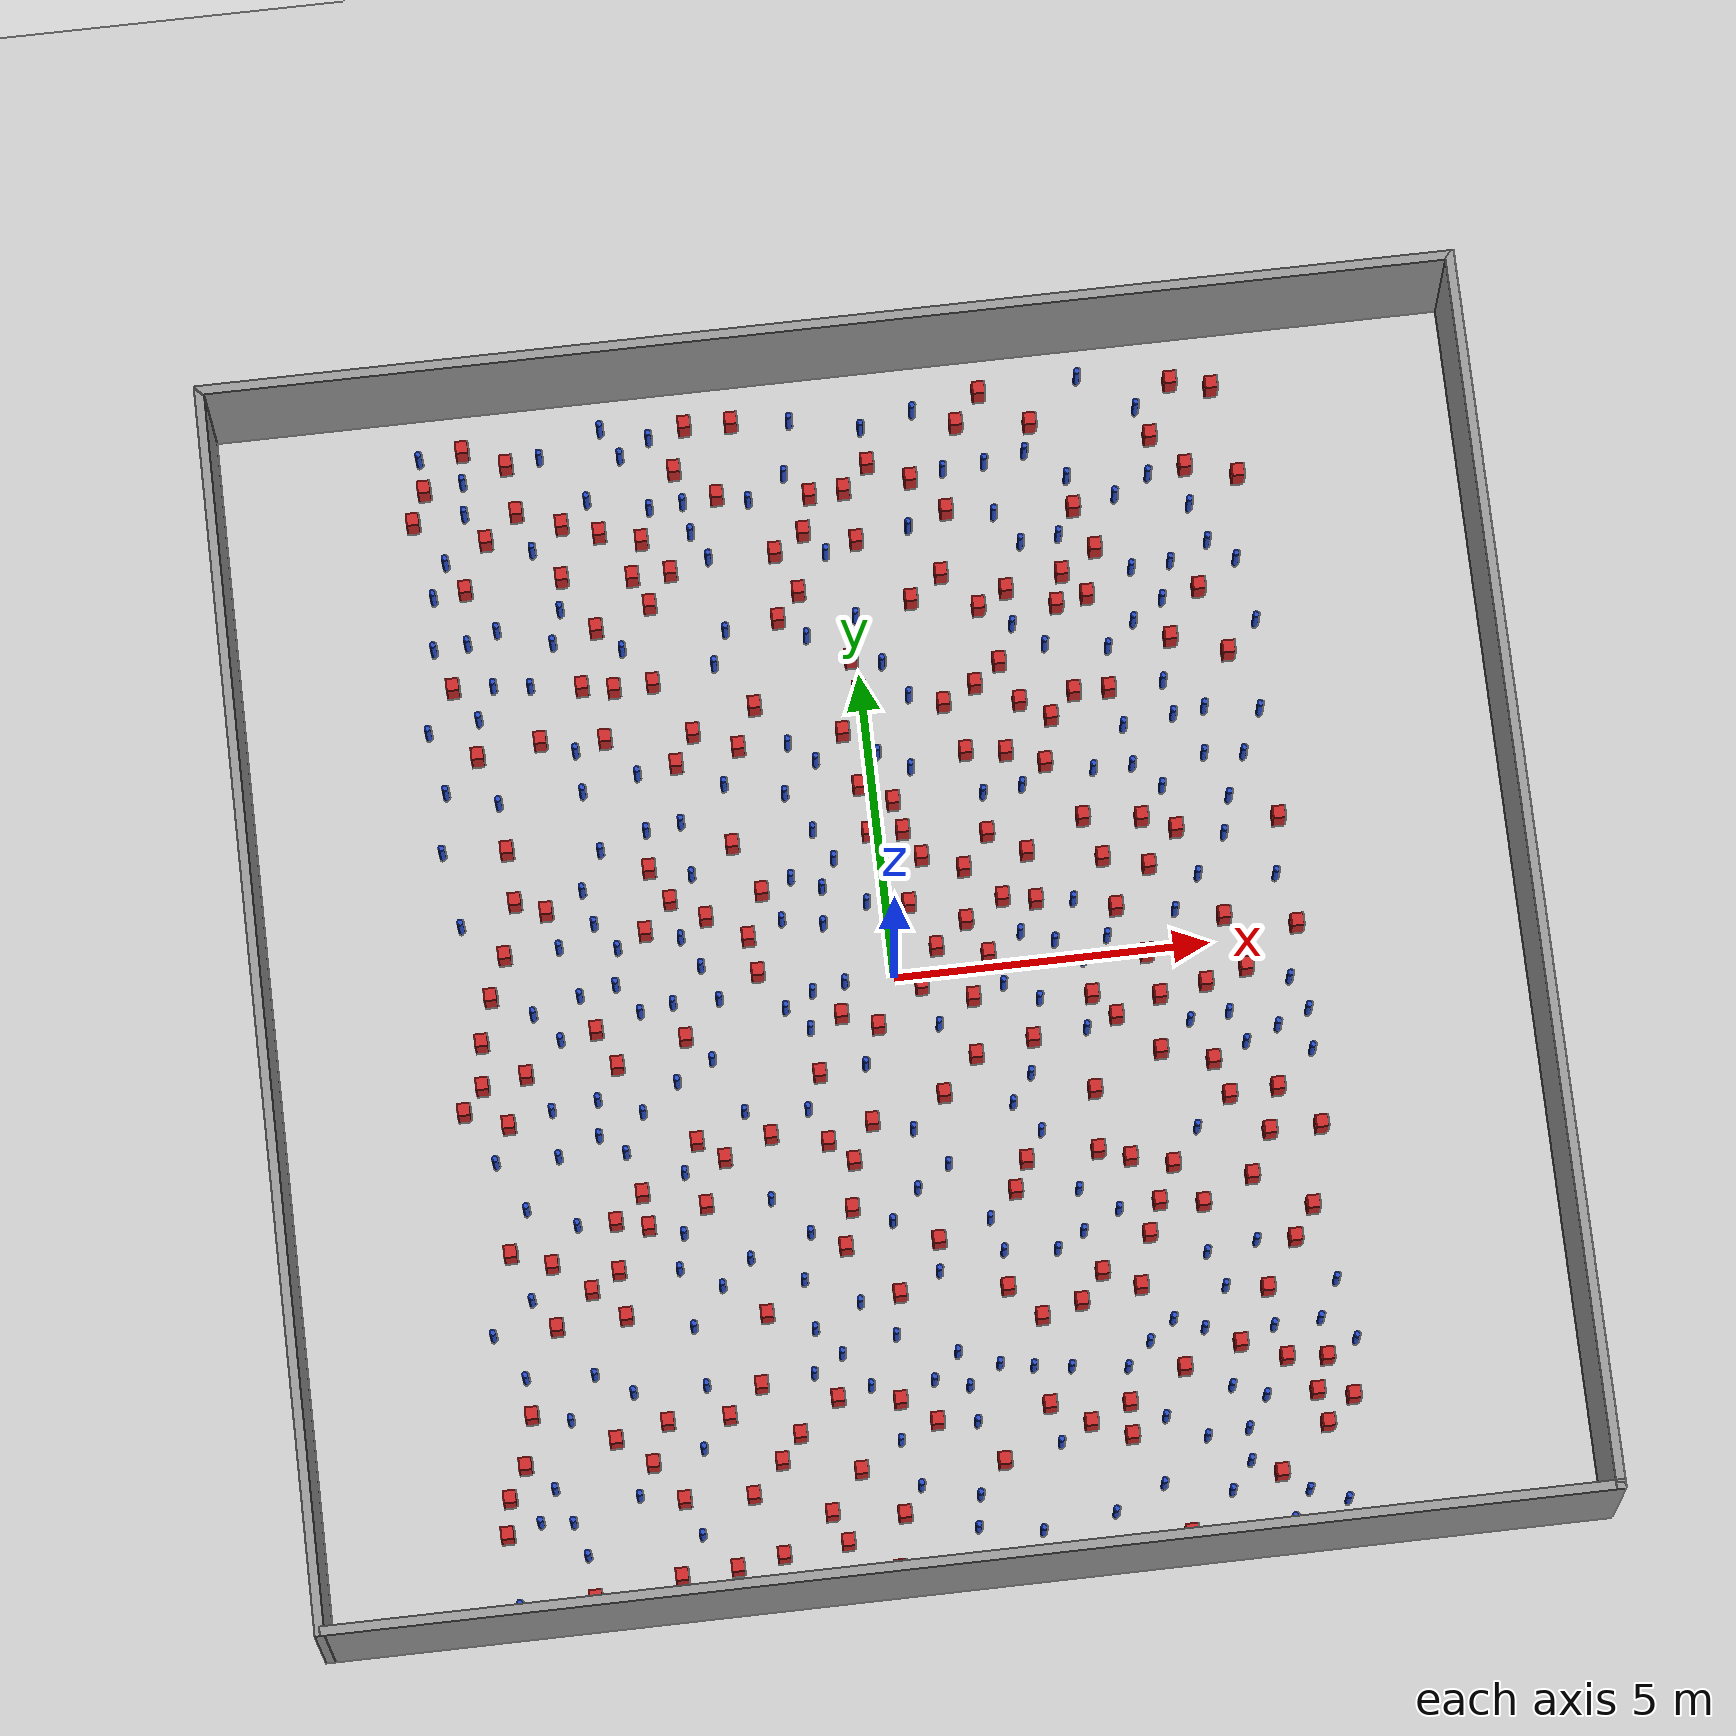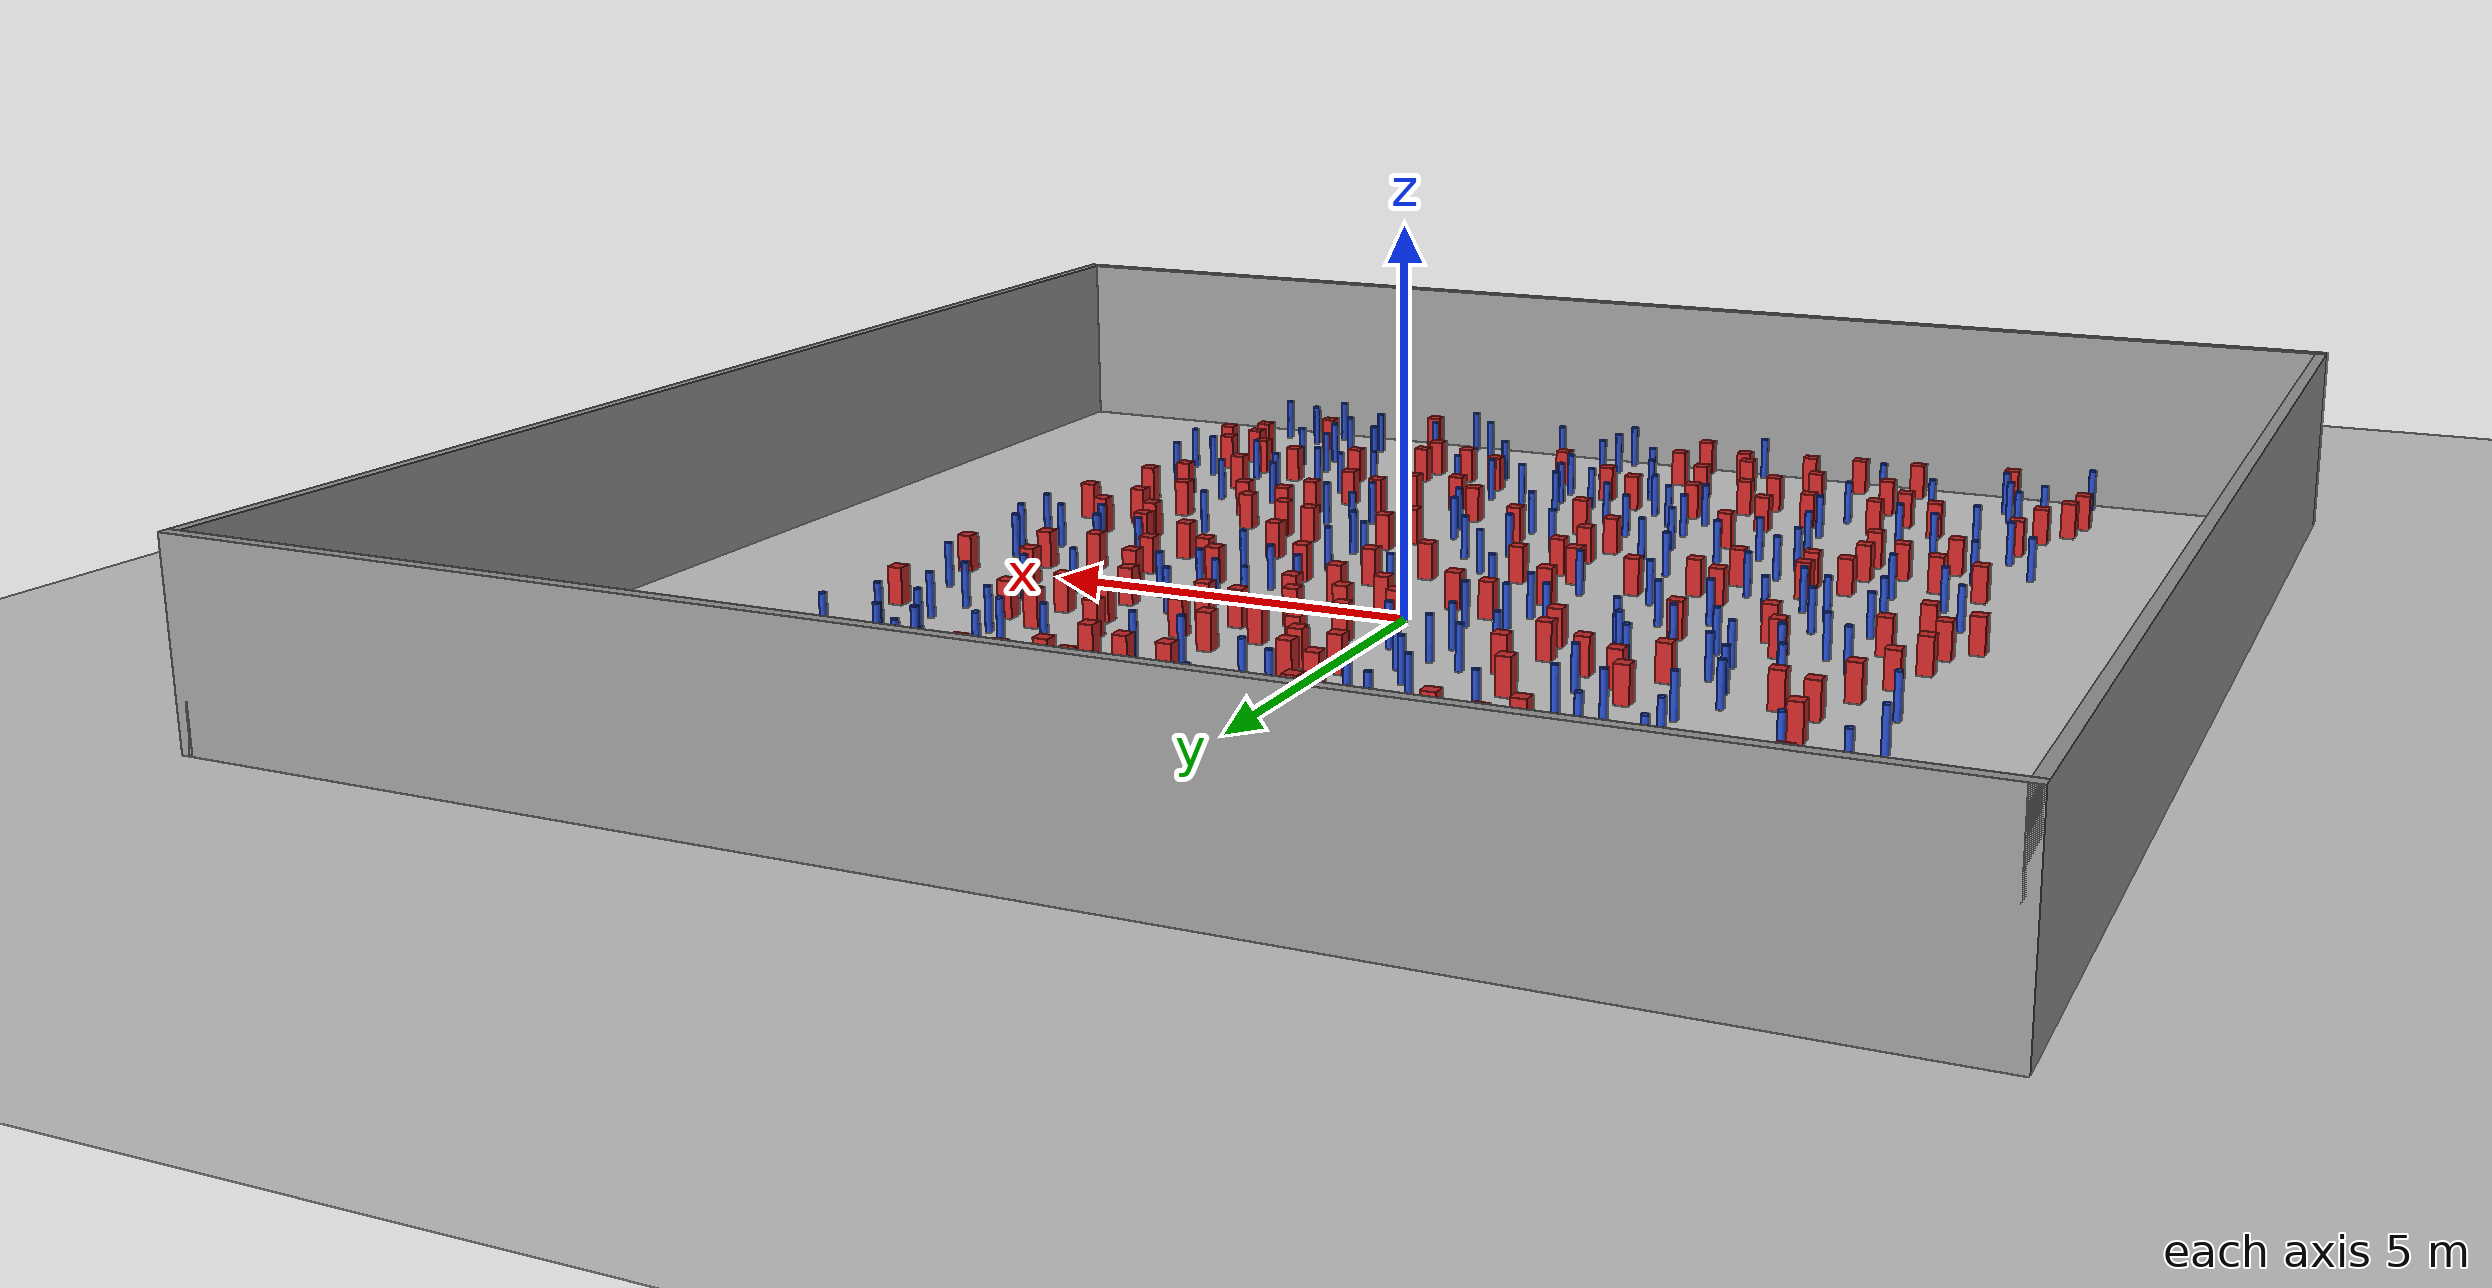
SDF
<sdf version="1.6">
 <world name="default">
  <light name="sun" type="directional">
   <pose>0 0 1000 0 -0 0</pose>
   <diffuse>0.8 0.8 0.8 1</diffuse>
   <specular>0.1 0.1 0.1 1</specular>
   <attenuation>
    <range>1000</range>
    <constant>0.9</constant>
    <linear>0.01</linear>
    <quadratic>0.001</quadratic>
   </attenuation>
   <direction>-0.5 0.5 -1</direction>
  </light>
  <model name="ground_plane">
   <static>1</static>
   <link name="link">
    <collision name="collision">
     <geometry><plane><normal>0 0 1</normal><size>100 100</size></plane></geometry>
     <surface><friction><ode><mu>100</mu><mu2>50</mu2></ode></friction></surface>
    </collision>
    <visual name="visual">
     <cast_shadows>0</cast_shadows>
     <geometry><plane><normal>0 0 1</normal><size>100 100</size></plane></geometry>
     <material>
      <ambient>1.0 1.0 1.0 1.0</ambient>
      <diffuse>0.8 0.8 0.8 1.0</diffuse>
      <specular>0.01 0.01 0.01 1.000000</specular>
     </material>
    </visual>
   </link>
  </model>
  <gravity>0 0 -9.8</gravity>
  <magnetic_field>6e-06 2.3e-05 -4.2e-05</magnetic_field>
  <atmosphere type="adiabatic"/>
  <physics name="default_physics" default="0" type="ode">
   <max_step_size>0.001</max_step_size>
   <real_time_factor>1</real_time_factor>
   <real_time_update_rate>1000</real_time_update_rate>
  </physics>
  <scene><ambient>0.4 0.4 0.4 1</ambient><background>0.7 0.7 0.7 1</background><shadows>1</shadows></scene>
  <spherical_coordinates>
   <surface_model>EARTH_WGS84</surface_model>
   <latitude_deg>0</latitude_deg>
   <longitude_deg>0</longitude_deg>
   <elevation>0</elevation>
   <heading_deg>0</heading_deg>
  </spherical_coordinates>
  <plugin name="gazebo_occupancy_map" filename="libgazebo_2Dmap_plugin.so">
   <map_resolution>0.05</map_resolution>
   <map_topic>generated_map</map_topic>
   <map_height>0.01</map_height>
   <map_size_x>50</map_size_x>
   <map_size_y>50</map_size_y>
  </plugin>
  <model name="NamedLocations">
   <static>true</static>
   <link name="DefaultStart"><pose>8.5 0 0 0 0 3.14</pose></link>
  </model>
  <model name="20x20_walls">
   <pose>0.044518 0.176112 0 0 -0 0</pose>
   <link name="Wall_1">
    <collision name="Wall_1_Collision">
     <geometry><box><size>20 0.15 2.5</size></box></geometry>
     <pose>0 0 1.25 0 -0 0</pose>
    </collision>
    <visual name="Wall_1_Visual">
     <pose>0 0 1.25 0 -0 0</pose>
     <geometry><box><size>20 0.15 2.5</size></box></geometry>
     <material>
      <script><uri>file://media/materials/scripts/gazebo.material</uri><name>Gazebo/Grey</name></script>
      <ambient>0.976471 0.992157 1 1</ambient>
     </material>
     <meta><layer>0</layer></meta>
    </visual>
    <pose>0 9.925 0 0 -0 0</pose>
   </link>
   <link name="Wall_3">
    <collision name="Wall_3_Collision">
     <geometry><box><size>20 0.15 2.5</size></box></geometry>
     <pose>0 0 1.25 0 -0 0</pose>
    </collision>
    <visual name="Wall_3_Visual">
     <pose>0 0 1.25 0 -0 0</pose>
     <geometry><box><size>20 0.15 2.5</size></box></geometry>
     <material>
      <script><uri>file://media/materials/scripts/gazebo.material</uri><name>Gazebo/Grey</name></script>
      <ambient>0.976471 0.992157 1 1</ambient>
     </material>
     <meta><layer>0</layer></meta>
    </visual>
    <pose>9.925 0 0 0 0 -1.5708</pose>
   </link>
   <link name="Wall_4">
    <collision name="Wall_4_Collision">
     <geometry><box><size>20 0.15 2.5</size></box></geometry>
     <pose>0 0 1.25 0 -0 0</pose>
    </collision>
    <visual name="Wall_4_Visual">
     <pose>0 0 1.25 0 -0 0</pose>
     <geometry><box><size>20 0.15 2.5</size></box></geometry>
     <material>
      <script><uri>file://media/materials/scripts/gazebo.material</uri><name>Gazebo/Grey</name></script>
      <ambient>0.976471 0.992157 1 1</ambient>
     </material>
     <meta><layer>0</layer></meta>
    </visual>
    <pose>0 -9.925 0 0 -0 3.14159</pose>
   </link>
   <link name="Wall_5">
    <collision name="Wall_5_Collision">
     <geometry><box><size>20 0.15 2.5</size></box></geometry>
     <pose>0 0 1.25 0 -0 0</pose>
    </collision>
    <visual name="Wall_5_Visual">
     <pose>0 0 1.25 0 -0 0</pose>
     <geometry><box><size>20 0.15 2.5</size></box></geometry>
     <material>
      <script><uri>file://media/materials/scripts/gazebo.material</uri><name>Gazebo/Grey</name></script>
      <ambient>0.976471 0.992157 1 1</ambient>
     </material>
     <meta><layer>0</layer></meta>
    </visual>
    <pose>-9.925 0 0 0 -0 1.5708</pose>
   </link>
   <static>1</static>
  </model>
  <model name="square_post_obstacle0">
   <static>true</static>
   <pose>1.99020298457 8.9363868212 1.91545236811e-07 -7.35059704564e-06 1.12565212e-07 2.39332434364e-05</pose>
   <link name="link">
    <pose>0 0 0.25 0 -0 0</pose>
    <inertial>
     <mass>100</mass>
     <inertia>
      <ixx>0.166667</ixx>
      <ixy>0</ixy>
      <ixz>0</ixz>
      <iyy>0.166667</iyy>
      <iyz>0</iyz>
      <izz>0.166667</izz>
     </inertia>
    </inertial>
    <collision name="collision"><geometry><box><size>.2 .2 .5</size></box></geometry></collision>
    <visual name="visual">
     <geometry><box><size>.2 .2 .5</size></box></geometry>
     <material>
      <script><name>Gazebo/Red</name><uri>file://media/materials/scripts/gazebo.material</uri></script>
     </material>
    </visual>
   </link>
  </model>
  <model name="square_post_obstacle1">
   <static>true</static>
   <pose>5.8524350811 -7.88041498456 1.91545236811e-07 -7.35059704564e-06 1.12565212e-07 2.39332434364e-05</pose>
   <link name="link">
    <pose>0 0 0.25 0 -0 0</pose>
    <inertial>
     <mass>100</mass>
     <inertia>
      <ixx>0.166667</ixx>
      <ixy>0</ixy>
      <ixz>0</ixz>
      <iyy>0.166667</iyy>
      <iyz>0</iyz>
      <izz>0.166667</izz>
     </inertia>
    </inertial>
    <collision name="collision"><geometry><box><size>.2 .2 .5</size></box></geometry></collision>
    <visual name="visual">
     <geometry><box><size>.2 .2 .5</size></box></geometry>
     <material>
      <script><name>Gazebo/Red</name><uri>file://media/materials/scripts/gazebo.material</uri></script>
     </material>
    </visual>
   </link>
  </model>
  <model name="pole_obstacle0">
   <static>true</static>
   <pose>2.45319481599 -4.44269924084 7.38925637345e-09 -8.47170692798e-08 1.24976765033e-08 -1.74513093019e-07</pose>
   <link name="link">
    <pose>0 0 0.3 0 -0 0</pose>
    <inertial>
     <mass>1</mass>
     <inertia><ixx>0.145833</ixx><ixy>0</ixy><ixz>0</ixz><iyy>0.145833</iyy><iyz>0</iyz><izz>0.125</izz></inertia>
    </inertial>
    <collision name="collision">
     <geometry><cylinder><radius>0.05</radius><length>.6</length></cylinder></geometry>
    </collision>
    <visual name="visual">
     <geometry><cylinder><radius>0.05</radius><length>.6</length></cylinder></geometry>
     <material>
      <script><name>Gazebo/Blue</name><uri>file://media/materials/scripts/gazebo.material</uri></script>
     </material>
    </visual>
   </link>
  </model>
  <model name="square_post_obstacle2">
   <static>true</static>
   <pose>-4.08696699237 6.18020313436 1.91545236811e-07 -7.35059704564e-06 1.12565212e-07 2.39332434364e-05</pose>
   <link name="link">
    <pose>0 0 0.25 0 -0 0</pose>
    <inertial>
     <mass>100</mass>
     <inertia>
      <ixx>0.166667</ixx>
      <ixy>0</ixy>
      <ixz>0</ixz>
      <iyy>0.166667</iyy>
      <iyz>0</iyz>
      <izz>0.166667</izz>
     </inertia>
    </inertial>
    <collision name="collision"><geometry><box><size>.2 .2 .5</size></box></geometry></collision>
    <visual name="visual">
     <geometry><box><size>.2 .2 .5</size></box></geometry>
     <material>
      <script><name>Gazebo/Red</name><uri>file://media/materials/scripts/gazebo.material</uri></script>
     </material>
    </visual>
   </link>
  </model>
  <model name="pole_obstacle1">
   <static>true</static>
   <pose>5.110812077 -4.89288464973 7.38925637345e-09 -8.47170692796e-08 1.24976764786e-08 -1.74513093032e-07</pose>
   <link name="link">
    <pose>0 0 0.3 0 -0 0</pose>
    <inertial>
     <mass>1</mass>
     <inertia><ixx>0.145833</ixx><ixy>0</ixy><ixz>0</ixz><iyy>0.145833</iyy><iyz>0</iyz><izz>0.125</izz></inertia>
    </inertial>
    <collision name="collision">
     <geometry><cylinder><radius>0.05</radius><length>.6</length></cylinder></geometry>
    </collision>
    <visual name="visual">
     <geometry><cylinder><radius>0.05</radius><length>.6</length></cylinder></geometry>
     <material>
      <script><name>Gazebo/Blue</name><uri>file://media/materials/scripts/gazebo.material</uri></script>
     </material>
    </visual>
   </link>
  </model>
  <model name="square_post_obstacle3">
   <static>true</static>
   <pose>1.17555070955 -5.18279903522 1.91545236811e-07 -7.35059704564e-06 1.12565212e-07 2.39332434364e-05</pose>
   <link name="link">
    <pose>0 0 0.25 0 -0 0</pose>
    <inertial>
     <mass>100</mass>
     <inertia>
      <ixx>0.166667</ixx>
      <ixy>0</ixy>
      <ixz>0</ixz>
      <iyy>0.166667</iyy>
      <iyz>0</iyz>
      <izz>0.166667</izz>
     </inertia>
    </inertial>
    <collision name="collision"><geometry><box><size>.2 .2 .5</size></box></geometry></collision>
    <visual name="visual">
     <geometry><box><size>.2 .2 .5</size></box></geometry>
     <material>
      <script><name>Gazebo/Red</name><uri>file://media/materials/scripts/gazebo.material</uri></script>
     </material>
    </visual>
   </link>
  </model>
  <model name="pole_obstacle2">
   <static>true</static>
   <pose>-5.38142675522 -3.46980054637 7.38925637345e-09 -8.47170692798e-08 1.24976764937e-08 -1.74513093023e-07</pose>
   <link name="link">
    <pose>0 0 0.3 0 -0 0</pose>
    <inertial>
     <mass>1</mass>
     <inertia><ixx>0.145833</ixx><ixy>0</ixy><ixz>0</ixz><iyy>0.145833</iyy><iyz>0</iyz><izz>0.125</izz></inertia>
    </inertial>
    <collision name="collision">
     <geometry><cylinder><radius>0.05</radius><length>.6</length></cylinder></geometry>
    </collision>
    <visual name="visual">
     <geometry><cylinder><radius>0.05</radius><length>.6</length></cylinder></geometry>
     <material>
      <script><name>Gazebo/Blue</name><uri>file://media/materials/scripts/gazebo.material</uri></script>
     </material>
    </visual>
   </link>
  </model>
  <model name="pole_obstacle3">
   <static>true</static>
   <pose>-3.40958924151 8.97512977727 7.38925637345e-09 -8.47170692799e-08 1.24976765012e-08 -1.74513093021e-07</pose>
   <link name="link">
    <pose>0 0 0.3 0 -0 0</pose>
    <inertial>
     <mass>1</mass>
     <inertia><ixx>0.145833</ixx><ixy>0</ixy><ixz>0</ixz><iyy>0.145833</iyy><iyz>0</iyz><izz>0.125</izz></inertia>
    </inertial>
    <collision name="collision">
     <geometry><cylinder><radius>0.05</radius><length>.6</length></cylinder></geometry>
    </collision>
    <visual name="visual">
     <geometry><cylinder><radius>0.05</radius><length>.6</length></cylinder></geometry>
     <material>
      <script><name>Gazebo/Blue</name><uri>file://media/materials/scripts/gazebo.material</uri></script>
     </material>
    </visual>
   </link>
  </model>
  <model name="square_post_obstacle4">
   <static>true</static>
   <pose>-1.94257678499 8.1703270499 1.91545236811e-07 -7.35059704564e-06 1.12565212e-07 2.39332434364e-05</pose>
   <link name="link">
    <pose>0 0 0.25 0 -0 0</pose>
    <inertial>
     <mass>100</mass>
     <inertia>
      <ixx>0.166667</ixx>
      <ixy>0</ixy>
      <ixz>0</ixz>
      <iyy>0.166667</iyy>
      <iyz>0</iyz>
      <izz>0.166667</izz>
     </inertia>
    </inertial>
    <collision name="collision"><geometry><box><size>.2 .2 .5</size></box></geometry></collision>
    <visual name="visual">
     <geometry><box><size>.2 .2 .5</size></box></geometry>
     <material>
      <script><name>Gazebo/Red</name><uri>file://media/materials/scripts/gazebo.material</uri></script>
     </material>
    </visual>
   </link>
  </model>
  <model name="square_post_obstacle5">
   <static>true</static>
   <pose>6.30125212651 -7.48989222779 1.91545236811e-07 -7.35059704564e-06 1.12565212e-07 2.39332434364e-05</pose>
   <link name="link">
    <pose>0 0 0.25 0 -0 0</pose>
    <inertial>
     <mass>100</mass>
     <inertia>
      <ixx>0.166667</ixx>
      <ixy>0</ixy>
      <ixz>0</ixz>
      <iyy>0.166667</iyy>
      <iyz>0</iyz>
      <izz>0.166667</izz>
     </inertia>
    </inertial>
    <collision name="collision"><geometry><box><size>.2 .2 .5</size></box></geometry></collision>
    <visual name="visual">
     <geometry><box><size>.2 .2 .5</size></box></geometry>
     <material>
      <script><name>Gazebo/Red</name><uri>file://media/materials/scripts/gazebo.material</uri></script>
     </material>
    </visual>
   </link>
  </model>
  <model name="square_post_obstacle6">
   <static>true</static>
   <pose>4.00243463076 -1.67645214226 1.91545236811e-07 -7.35059704564e-06 1.12565212e-07 2.39332434364e-05</pose>
   <link name="link">
    <pose>0 0 0.25 0 -0 0</pose>
    <inertial>
     <mass>100</mass>
     <inertia>
      <ixx>0.166667</ixx>
      <ixy>0</ixy>
      <ixz>0</ixz>
      <iyy>0.166667</iyy>
      <iyz>0</iyz>
      <izz>0.166667</izz>
     </inertia>
    </inertial>
    <collision name="collision"><geometry><box><size>.2 .2 .5</size></box></geometry></collision>
    <visual name="visual">
     <geometry><box><size>.2 .2 .5</size></box></geometry>
     <material>
      <script><name>Gazebo/Red</name><uri>file://media/materials/scripts/gazebo.material</uri></script>
     </material>
    </visual>
   </link>
  </model>
  <model name="pole_obstacle4">
   <static>true</static>
   <pose>-0.75053529397 1.97190595984 7.38925637345e-09 -8.47170692799e-08 1.24976765066e-08 -1.74513093016e-07</pose>
   <link name="link">
    <pose>0 0 0.3 0 -0 0</pose>
    <inertial>
     <mass>1</mass>
     <inertia><ixx>0.145833</ixx><ixy>0</ixy><ixz>0</ixz><iyy>0.145833</iyy><iyz>0</iyz><izz>0.125</izz></inertia>
    </inertial>
    <collision name="collision">
     <geometry><cylinder><radius>0.05</radius><length>.6</length></cylinder></geometry>
    </collision>
    <visual name="visual">
     <geometry><cylinder><radius>0.05</radius><length>.6</length></cylinder></geometry>
     <material>
      <script><name>Gazebo/Blue</name><uri>file://media/materials/scripts/gazebo.material</uri></script>
     </material>
    </visual>
   </link>
  </model>
  <model name="pole_obstacle5">
   <static>true</static>
   <pose>4.54238996978 2.56478637814 7.38925637345e-09 -8.47170692798e-08 1.24976764937e-08 -1.74513093023e-07</pose>
   <link name="link">
    <pose>0 0 0.3 0 -0 0</pose>
    <inertial>
     <mass>1</mass>
     <inertia><ixx>0.145833</ixx><ixy>0</ixy><ixz>0</ixz><iyy>0.145833</iyy><iyz>0</iyz><izz>0.125</izz></inertia>
    </inertial>
    <collision name="collision">
     <geometry><cylinder><radius>0.05</radius><length>.6</length></cylinder></geometry>
    </collision>
    <visual name="visual">
     <geometry><cylinder><radius>0.05</radius><length>.6</length></cylinder></geometry>
     <material>
      <script><name>Gazebo/Blue</name><uri>file://media/materials/scripts/gazebo.material</uri></script>
     </material>
    </visual>
   </link>
  </model>
  <model name="square_post_obstacle7">
   <static>true</static>
   <pose>2.81523320813 -7.72987050047 1.91545236811e-07 -7.35059704564e-06 1.12565212e-07 2.39332434364e-05</pose>
   <link name="link">
    <pose>0 0 0.25 0 -0 0</pose>
    <inertial>
     <mass>100</mass>
     <inertia>
      <ixx>0.166667</ixx>
      <ixy>0</ixy>
      <ixz>0</ixz>
      <iyy>0.166667</iyy>
      <iyz>0</iyz>
      <izz>0.166667</izz>
     </inertia>
    </inertial>
    <collision name="collision"><geometry><box><size>.2 .2 .5</size></box></geometry></collision>
    <visual name="visual">
     <geometry><box><size>.2 .2 .5</size></box></geometry>
     <material>
      <script><name>Gazebo/Red</name><uri>file://media/materials/scripts/gazebo.material</uri></script>
     </material>
    </visual>
   </link>
  </model>
  <model name="square_post_obstacle8">
   <static>true</static>
   <pose>-0.0129463398346 0.317881958594 1.91545236811e-07 -7.35059704564e-06 1.12565212e-07 2.39332434364e-05</pose>
   <link name="link">
    <pose>0 0 0.25 0 -0 0</pose>
    <inertial>
     <mass>100</mass>
     <inertia>
      <ixx>0.166667</ixx>
      <ixy>0</ixy>
      <ixz>0</ixz>
      <iyy>0.166667</iyy>
      <iyz>0</iyz>
      <izz>0.166667</izz>
     </inertia>
    </inertial>
    <collision name="collision"><geometry><box><size>.2 .2 .5</size></box></geometry></collision>
    <visual name="visual">
     <geometry><box><size>.2 .2 .5</size></box></geometry>
     <material>
      <script><name>Gazebo/Red</name><uri>file://media/materials/scripts/gazebo.material</uri></script>
     </material>
    </visual>
   </link>
  </model>
  <model name="pole_obstacle6">
   <static>true</static>
   <pose>6.16980746209 6.17317058995 7.38925637345e-09 -8.47170692796e-08 1.24976764786e-08 -1.74513093032e-07</pose>
   <link name="link">
    <pose>0 0 0.3 0 -0 0</pose>
    <inertial>
     <mass>1</mass>
     <inertia><ixx>0.145833</ixx><ixy>0</ixy><ixz>0</ixz><iyy>0.145833</iyy><iyz>0</iyz><izz>0.125</izz></inertia>
    </inertial>
    <collision name="collision">
     <geometry><cylinder><radius>0.05</radius><length>.6</length></cylinder></geometry>
    </collision>
    <visual name="visual">
     <geometry><cylinder><radius>0.05</radius><length>.6</length></cylinder></geometry>
     <material>
      <script><name>Gazebo/Blue</name><uri>file://media/materials/scripts/gazebo.material</uri></script>
     </material>
    </visual>
   </link>
  </model>
  <model name="pole_obstacle7">
   <static>true</static>
   <pose>6.15677421784 -0.760147875584 7.38925637345e-09 -8.47170692799e-08 1.24976765038e-08 -1.74513093018e-07</pose>
   <link name="link">
    <pose>0 0 0.3 0 -0 0</pose>
    <inertial>
     <mass>1</mass>
     <inertia><ixx>0.145833</ixx><ixy>0</ixy><ixz>0</ixz><iyy>0.145833</iyy><iyz>0</iyz><izz>0.125</izz></inertia>
    </inertial>
    <collision name="collision">
     <geometry><cylinder><radius>0.05</radius><length>.6</length></cylinder></geometry>
    </collision>
    <visual name="visual">
     <geometry><cylinder><radius>0.05</radius><length>.6</length></cylinder></geometry>
     <material>
      <script><name>Gazebo/Blue</name><uri>file://media/materials/scripts/gazebo.material</uri></script>
     </material>
    </visual>
   </link>
  </model>
  <model name="square_post_obstacle9">
   <static>true</static>
   <pose>-2.74050162465 4.29068194543 1.91545236811e-07 -7.35059704564e-06 1.12565212e-07 2.39332434364e-05</pose>
   <link name="link">
    <pose>0 0 0.25 0 -0 0</pose>
    <inertial>
     <mass>100</mass>
     <inertia>
      <ixx>0.166667</ixx>
      <ixy>0</ixy>
      <ixz>0</ixz>
      <iyy>0.166667</iyy>
      <iyz>0</iyz>
      <izz>0.166667</izz>
     </inertia>
    </inertial>
    <collision name="collision"><geometry><box><size>.2 .2 .5</size></box></geometry></collision>
    <visual name="visual">
     <geometry><box><size>.2 .2 .5</size></box></geometry>
     <material>
      <script><name>Gazebo/Red</name><uri>file://media/materials/scripts/gazebo.material</uri></script>
     </material>
    </visual>
   </link>
  </model>
  <model name="square_post_obstacle10">
   <static>true</static>
   <pose>-5.13952486066 -6.89971847633 1.91545236811e-07 -7.35059704564e-06 1.12565212e-07 2.39332434364e-05</pose>
   <link name="link">
    <pose>0 0 0.25 0 -0 0</pose>
    <inertial>
     <mass>100</mass>
     <inertia>
      <ixx>0.166667</ixx>
      <ixy>0</ixy>
      <ixz>0</ixz>
      <iyy>0.166667</iyy>
      <iyz>0</iyz>
      <izz>0.166667</izz>
     </inertia>
    </inertial>
    <collision name="collision"><geometry><box><size>.2 .2 .5</size></box></geometry></collision>
    <visual name="visual">
     <geometry><box><size>.2 .2 .5</size></box></geometry>
     <material>
      <script><name>Gazebo/Red</name><uri>file://media/materials/scripts/gazebo.material</uri></script>
     </material>
    </visual>
   </link>
  </model>
  <model name="square_post_obstacle11">
   <static>true</static>
   <pose>-6.36342929081 0.339561308146 1.91545236811e-07 -7.35059704564e-06 1.12565212e-07 2.39332434364e-05</pose>
   <link name="link">
    <pose>0 0 0.25 0 -0 0</pose>
    <inertial>
     <mass>100</mass>
     <inertia>
      <ixx>0.166667</ixx>
      <ixy>0</ixy>
      <ixz>0</ixz>
      <iyy>0.166667</iyy>
      <iyz>0</iyz>
      <izz>0.166667</izz>
     </inertia>
    </inertial>
    <collision name="collision"><geometry><box><size>.2 .2 .5</size></box></geometry></collision>
    <visual name="visual">
     <geometry><box><size>.2 .2 .5</size></box></geometry>
     <material>
      <script><name>Gazebo/Red</name><uri>file://media/materials/scripts/gazebo.material</uri></script>
     </material>
    </visual>
   </link>
  </model>
  <model name="square_post_obstacle12">
   <static>true</static>
   <pose>3.03835223823 -0.663720716733 1.91545236811e-07 -7.35059704564e-06 1.12565212e-07 2.39332434364e-05</pose>
   <link name="link">
    <pose>0 0 0.25 0 -0 0</pose>
    <inertial>
     <mass>100</mass>
     <inertia>
      <ixx>0.166667</ixx>
      <ixy>0</ixy>
      <ixz>0</ixz>
      <iyy>0.166667</iyy>
      <iyz>0</iyz>
      <izz>0.166667</izz>
     </inertia>
    </inertial>
    <collision name="collision"><geometry><box><size>.2 .2 .5</size></box></geometry></collision>
    <visual name="visual">
     <geometry><box><size>.2 .2 .5</size></box></geometry>
     <material>
      <script><name>Gazebo/Red</name><uri>file://media/materials/scripts/gazebo.material</uri></script>
     </material>
    </visual>
   </link>
  </model>
  <model name="square_post_obstacle13">
   <static>true</static>
   <pose>0.947055316499 6.09849386532 1.91545236811e-07 -7.35059704564e-06 1.12565212e-07 2.39332434364e-05</pose>
   <link name="link">
    <pose>0 0 0.25 0 -0 0</pose>
    <inertial>
     <mass>100</mass>
     <inertia>
      <ixx>0.166667</ixx>
      <ixy>0</ixy>
      <ixz>0</ixz>
      <iyy>0.166667</iyy>
      <iyz>0</iyz>
      <izz>0.166667</izz>
     </inertia>
    </inertial>
    <collision name="collision"><geometry><box><size>.2 .2 .5</size></box></geometry></collision>
    <visual name="visual">
     <geometry><box><size>.2 .2 .5</size></box></geometry>
     <material>
      <script><name>Gazebo/Red</name><uri>file://media/materials/scripts/gazebo.material</uri></script>
     </material>
    </visual>
   </link>
  </model>
  <model name="pole_obstacle8">
   <static>true</static>
   <pose>-1.87639103738 -5.52417425113 7.38925637345e-09 -8.47170692799e-08 1.24976765033e-08 -1.74513093018e-07</pose>
   <link name="link">
    <pose>0 0 0.3 0 -0 0</pose>
    <inertial>
     <mass>1</mass>
     <inertia><ixx>0.145833</ixx><ixy>0</ixy><ixz>0</ixz><iyy>0.145833</iyy><iyz>0</iyz><izz>0.125</izz></inertia>
    </inertial>
    <collision name="collision">
     <geometry><cylinder><radius>0.05</radius><length>.6</length></cylinder></geometry>
    </collision>
    <visual name="visual">
     <geometry><cylinder><radius>0.05</radius><length>.6</length></cylinder></geometry>
     <material>
      <script><name>Gazebo/Blue</name><uri>file://media/materials/scripts/gazebo.material</uri></script>
     </material>
    </visual>
   </link>
  </model>
  <model name="square_post_obstacle14">
   <static>true</static>
   <pose>-0.112037463065 5.22888776063 1.91545236811e-07 -7.35059704564e-06 1.12565212e-07 2.39332434364e-05</pose>
   <link name="link">
    <pose>0 0 0.25 0 -0 0</pose>
    <inertial>
     <mass>100</mass>
     <inertia>
      <ixx>0.166667</ixx>
      <ixy>0</ixy>
      <ixz>0</ixz>
      <iyy>0.166667</iyy>
      <iyz>0</iyz>
      <izz>0.166667</izz>
     </inertia>
    </inertial>
    <collision name="collision"><geometry><box><size>.2 .2 .5</size></box></geometry></collision>
    <visual name="visual">
     <geometry><box><size>.2 .2 .5</size></box></geometry>
     <material>
      <script><name>Gazebo/Red</name><uri>file://media/materials/scripts/gazebo.material</uri></script>
     </material>
    </visual>
   </link>
  </model>
  <model name="square_post_obstacle15">
   <static>true</static>
   <pose>-6.63554746986 -1.0725611367 1.91545236811e-07 -7.35059704564e-06 1.12565212e-07 2.39332434364e-05</pose>
   <link name="link">
    <pose>0 0 0.25 0 -0 0</pose>
    <inertial>
     <mass>100</mass>
     <inertia>
      <ixx>0.166667</ixx>
      <ixy>0</ixy>
      <ixz>0</ixz>
      <iyy>0.166667</iyy>
      <iyz>0</iyz>
      <izz>0.166667</izz>
     </inertia>
    </inertial>
    <collision name="collision"><geometry><box><size>.2 .2 .5</size></box></geometry></collision>
    <visual name="visual">
     <geometry><box><size>.2 .2 .5</size></box></geometry>
     <material>
      <script><name>Gazebo/Red</name><uri>file://media/materials/scripts/gazebo.material</uri></script>
     </material>
    </visual>
   </link>
  </model>
  <model name="square_post_obstacle16">
   <static>true</static>
   <pose>-0.980387862571 -2.91094023249 1.91545236811e-07 -7.35059704564e-06 1.12565212e-07 2.39332434364e-05</pose>
   <link name="link">
    <pose>0 0 0.25 0 -0 0</pose>
    <inertial>
     <mass>100</mass>
     <inertia>
      <ixx>0.166667</ixx>
      <ixy>0</ixy>
      <ixz>0</ixz>
      <iyy>0.166667</iyy>
      <iyz>0</iyz>
      <izz>0.166667</izz>
     </inertia>
    </inertial>
    <collision name="collision"><geometry><box><size>.2 .2 .5</size></box></geometry></collision>
    <visual name="visual">
     <geometry><box><size>.2 .2 .5</size></box></geometry>
     <material>
      <script><name>Gazebo/Red</name><uri>file://media/materials/scripts/gazebo.material</uri></script>
     </material>
    </visual>
   </link>
  </model>
  <model name="pole_obstacle9">
   <static>true</static>
   <pose>4.86439608183 3.7236601719 7.38925637345e-09 -8.47170692798e-08 1.24976764937e-08 -1.74513093023e-07</pose>
   <link name="link">
    <pose>0 0 0.3 0 -0 0</pose>
    <inertial>
     <mass>1</mass>
     <inertia><ixx>0.145833</ixx><ixy>0</ixy><ixz>0</ixz><iyy>0.145833</iyy><iyz>0</iyz><izz>0.125</izz></inertia>
    </inertial>
    <collision name="collision">
     <geometry><cylinder><radius>0.05</radius><length>.6</length></cylinder></geometry>
    </collision>
    <visual name="visual">
     <geometry><cylinder><radius>0.05</radius><length>.6</length></cylinder></geometry>
     <material>
      <script><name>Gazebo/Blue</name><uri>file://media/materials/scripts/gazebo.material</uri></script>
     </material>
    </visual>
   </link>
  </model>
  <model name="square_post_obstacle17">
   <static>true</static>
   <pose>5.25384583525 0.369909139949 1.91545236811e-07 -7.35059704564e-06 1.12565212e-07 2.39332434364e-05</pose>
   <link name="link">
    <pose>0 0 0.25 0 -0 0</pose>
    <inertial>
     <mass>100</mass>
     <inertia>
      <ixx>0.166667</ixx>
      <ixy>0</ixy>
      <ixz>0</ixz>
      <iyy>0.166667</iyy>
      <iyz>0</iyz>
      <izz>0.166667</izz>
     </inertia>
    </inertial>
    <collision name="collision"><geometry><box><size>.2 .2 .5</size></box></geometry></collision>
    <visual name="visual">
     <geometry><box><size>.2 .2 .5</size></box></geometry>
     <material>
      <script><name>Gazebo/Red</name><uri>file://media/materials/scripts/gazebo.material</uri></script>
     </material>
    </visual>
   </link>
  </model>
  <model name="square_post_obstacle18">
   <static>true</static>
   <pose>1.16525033121 8.103247018 1.91545236811e-07 -7.35059704564e-06 1.12565212e-07 2.39332434364e-05</pose>
   <link name="link">
    <pose>0 0 0.25 0 -0 0</pose>
    <inertial>
     <mass>100</mass>
     <inertia>
      <ixx>0.166667</ixx>
      <ixy>0</ixy>
      <ixz>0</ixz>
      <iyy>0.166667</iyy>
      <iyz>0</iyz>
      <izz>0.166667</izz>
     </inertia>
    </inertial>
    <collision name="collision"><geometry><box><size>.2 .2 .5</size></box></geometry></collision>
    <visual name="visual">
     <geometry><box><size>.2 .2 .5</size></box></geometry>
     <material>
      <script><name>Gazebo/Red</name><uri>file://media/materials/scripts/gazebo.material</uri></script>
     </material>
    </visual>
   </link>
  </model>
  <model name="pole_obstacle10">
   <static>true</static>
   <pose>4.88381314462 8.86168116422 7.38925637345e-09 -8.471706928e-08 1.24976765081e-08 -1.74513093015e-07</pose>
   <link name="link">
    <pose>0 0 0.3 0 -0 0</pose>
    <inertial>
     <mass>1</mass>
     <inertia><ixx>0.145833</ixx><ixy>0</ixy><ixz>0</ixz><iyy>0.145833</iyy><iyz>0</iyz><izz>0.125</izz></inertia>
    </inertial>
    <collision name="collision">
     <geometry><cylinder><radius>0.05</radius><length>.6</length></cylinder></geometry>
    </collision>
    <visual name="visual">
     <geometry><cylinder><radius>0.05</radius><length>.6</length></cylinder></geometry>
     <material>
      <script><name>Gazebo/Blue</name><uri>file://media/materials/scripts/gazebo.material</uri></script>
     </material>
    </visual>
   </link>
  </model>
  <model name="square_post_obstacle19">
   <static>true</static>
   <pose>-4.28214756523 -3.59136067005 1.91545236811e-07 -7.35059704564e-06 1.12565212e-07 2.39332434364e-05</pose>
   <link name="link">
    <pose>0 0 0.25 0 -0 0</pose>
    <inertial>
     <mass>100</mass>
     <inertia>
      <ixx>0.166667</ixx>
      <ixy>0</ixy>
      <ixz>0</ixz>
      <iyy>0.166667</iyy>
      <iyz>0</iyz>
      <izz>0.166667</izz>
     </inertia>
    </inertial>
    <collision name="collision"><geometry><box><size>.2 .2 .5</size></box></geometry></collision>
    <visual name="visual">
     <geometry><box><size>.2 .2 .5</size></box></geometry>
     <material>
      <script><name>Gazebo/Red</name><uri>file://media/materials/scripts/gazebo.material</uri></script>
     </material>
    </visual>
   </link>
  </model>
  <model name="pole_obstacle11">
   <static>true</static>
   <pose>2.42599380312 7.3634539889 7.38925637345e-09 -8.47170692798e-08 1.24976765033e-08 -1.74513093019e-07</pose>
   <link name="link">
    <pose>0 0 0.3 0 -0 0</pose>
    <inertial>
     <mass>1</mass>
     <inertia><ixx>0.145833</ixx><ixy>0</ixy><ixz>0</ixz><iyy>0.145833</iyy><iyz>0</iyz><izz>0.125</izz></inertia>
    </inertial>
    <collision name="collision">
     <geometry><cylinder><radius>0.05</radius><length>.6</length></cylinder></geometry>
    </collision>
    <visual name="visual">
     <geometry><cylinder><radius>0.05</radius><length>.6</length></cylinder></geometry>
     <material>
      <script><name>Gazebo/Blue</name><uri>file://media/materials/scripts/gazebo.material</uri></script>
     </material>
    </visual>
   </link>
  </model>
  <model name="square_post_obstacle20">
   <static>true</static>
   <pose>1.21002610688 0.756672883856 1.91545236811e-07 -7.35059704564e-06 1.12565212e-07 2.39332434364e-05</pose>
   <link name="link">
    <pose>0 0 0.25 0 -0 0</pose>
    <inertial>
     <mass>100</mass>
     <inertia>
      <ixx>0.166667</ixx>
      <ixy>0</ixy>
      <ixz>0</ixz>
      <iyy>0.166667</iyy>
      <iyz>0</iyz>
      <izz>0.166667</izz>
     </inertia>
    </inertial>
    <collision name="collision"><geometry><box><size>.2 .2 .5</size></box></geometry></collision>
    <visual name="visual">
     <geometry><box><size>.2 .2 .5</size></box></geometry>
     <material>
      <script><name>Gazebo/Red</name><uri>file://media/materials/scripts/gazebo.material</uri></script>
     </material>
    </visual>
   </link>
  </model>
  <model name="pole_obstacle12">
   <static>true</static>
   <pose>-4.62292605062 1.33828571062 7.38925637345e-09 -8.471706928e-08 1.24976765134e-08 -1.74513093015e-07</pose>
   <link name="link">
    <pose>0 0 0.3 0 -0 0</pose>
    <inertial>
     <mass>1</mass>
     <inertia><ixx>0.145833</ixx><ixy>0</ixy><ixz>0</ixz><iyy>0.145833</iyy><iyz>0</iyz><izz>0.125</izz></inertia>
    </inertial>
    <collision name="collision">
     <geometry><cylinder><radius>0.05</radius><length>.6</length></cylinder></geometry>
    </collision>
    <visual name="visual">
     <geometry><cylinder><radius>0.05</radius><length>.6</length></cylinder></geometry>
     <material>
      <script><name>Gazebo/Blue</name><uri>file://media/materials/scripts/gazebo.material</uri></script>
     </material>
    </visual>
   </link>
  </model>
  <model name="square_post_obstacle21">
   <static>true</static>
   <pose>-2.7512530869 -8.99102333689 1.91545236811e-07 -7.35059704564e-06 1.12565212e-07 2.39332434364e-05</pose>
   <link name="link">
    <pose>0 0 0.25 0 -0 0</pose>
    <inertial>
     <mass>100</mass>
     <inertia>
      <ixx>0.166667</ixx>
      <ixy>0</ixy>
      <ixz>0</ixz>
      <iyy>0.166667</iyy>
      <iyz>0</iyz>
      <izz>0.166667</izz>
     </inertia>
    </inertial>
    <collision name="collision"><geometry><box><size>.2 .2 .5</size></box></geometry></collision>
    <visual name="visual">
     <geometry><box><size>.2 .2 .5</size></box></geometry>
     <material>
      <script><name>Gazebo/Red</name><uri>file://media/materials/scripts/gazebo.material</uri></script>
     </material>
    </visual>
   </link>
  </model>
  <model name="pole_obstacle13">
   <static>true</static>
   <pose>-6.87187064369 -9.32866329716 7.38925637345e-09 -8.471706928e-08 1.24976765081e-08 -1.74513093015e-07</pose>
   <link name="link">
    <pose>0 0 0.3 0 -0 0</pose>
    <inertial>
     <mass>1</mass>
     <inertia><ixx>0.145833</ixx><ixy>0</ixy><ixz>0</ixz><iyy>0.145833</iyy><iyz>0</iyz><izz>0.125</izz></inertia>
    </inertial>
    <collision name="collision">
     <geometry><cylinder><radius>0.05</radius><length>.6</length></cylinder></geometry>
    </collision>
    <visual name="visual">
     <geometry><cylinder><radius>0.05</radius><length>.6</length></cylinder></geometry>
     <material>
      <script><name>Gazebo/Blue</name><uri>file://media/materials/scripts/gazebo.material</uri></script>
     </material>
    </visual>
   </link>
  </model>
  <model name="square_post_obstacle22">
   <static>true</static>
   <pose>-0.627810288311 -2.31708253477 1.91545236811e-07 -7.35059704564e-06 1.12565212e-07 2.39332434364e-05</pose>
   <link name="link">
    <pose>0 0 0.25 0 -0 0</pose>
    <inertial>
     <mass>100</mass>
     <inertia>
      <ixx>0.166667</ixx>
      <ixy>0</ixy>
      <ixz>0</ixz>
      <iyy>0.166667</iyy>
      <iyz>0</iyz>
      <izz>0.166667</izz>
     </inertia>
    </inertial>
    <collision name="collision"><geometry><box><size>.2 .2 .5</size></box></geometry></collision>
    <visual name="visual">
     <geometry><box><size>.2 .2 .5</size></box></geometry>
     <material>
      <script><name>Gazebo/Red</name><uri>file://media/materials/scripts/gazebo.material</uri></script>
     </material>
    </visual>
   </link>
  </model>
  <model name="pole_obstacle14">
   <static>true</static>
   <pose>0.145431486361 -4.83074506989 7.38925637345e-09 -8.471706928e-08 1.24976765036e-08 -1.74513093019e-07</pose>
   <link name="link">
    <pose>0 0 0.3 0 -0 0</pose>
    <inertial>
     <mass>1</mass>
     <inertia><ixx>0.145833</ixx><ixy>0</ixy><ixz>0</ixz><iyy>0.145833</iyy><iyz>0</iyz><izz>0.125</izz></inertia>
    </inertial>
    <collision name="collision">
     <geometry><cylinder><radius>0.05</radius><length>.6</length></cylinder></geometry>
    </collision>
    <visual name="visual">
     <geometry><cylinder><radius>0.05</radius><length>.6</length></cylinder></geometry>
     <material>
      <script><name>Gazebo/Blue</name><uri>file://media/materials/scripts/gazebo.material</uri></script>
     </material>
    </visual>
   </link>
  </model>
  <model name="pole_obstacle15">
   <static>true</static>
   <pose>-2.49472239428 8.10000024564 7.38925637345e-09 -8.47170692793e-08 1.24976764408e-08 -1.74513093041e-07</pose>
   <link name="link">
    <pose>0 0 0.3 0 -0 0</pose>
    <inertial>
     <mass>1</mass>
     <inertia><ixx>0.145833</ixx><ixy>0</ixy><ixz>0</ixz><iyy>0.145833</iyy><iyz>0</iyz><izz>0.125</izz></inertia>
    </inertial>
    <collision name="collision">
     <geometry><cylinder><radius>0.05</radius><length>.6</length></cylinder></geometry>
    </collision>
    <visual name="visual">
     <geometry><cylinder><radius>0.05</radius><length>.6</length></cylinder></geometry>
     <material>
      <script><name>Gazebo/Blue</name><uri>file://media/materials/scripts/gazebo.material</uri></script>
     </material>
    </visual>
   </link>
  </model>
  <model name="pole_obstacle16">
   <static>true</static>
   <pose>1.93347617222 -1.84121903709 7.38925637345e-09 -8.471706928e-08 1.24976765079e-08 -1.74513093017e-07</pose>
   <link name="link">
    <pose>0 0 0.3 0 -0 0</pose>
    <inertial>
     <mass>1</mass>
     <inertia><ixx>0.145833</ixx><ixy>0</ixy><ixz>0</ixz><iyy>0.145833</iyy><iyz>0</iyz><izz>0.125</izz></inertia>
    </inertial>
    <collision name="collision">
     <geometry><cylinder><radius>0.05</radius><length>.6</length></cylinder></geometry>
    </collision>
    <visual name="visual">
     <geometry><cylinder><radius>0.05</radius><length>.6</length></cylinder></geometry>
     <material>
      <script><name>Gazebo/Blue</name><uri>file://media/materials/scripts/gazebo.material</uri></script>
     </material>
    </visual>
   </link>
  </model>
  <model name="square_post_obstacle23">
   <static>true</static>
   <pose>-4.60558496701 -7.3352118702 1.91545236811e-07 -7.35059704564e-06 1.12565212e-07 2.39332434364e-05</pose>
   <link name="link">
    <pose>0 0 0.25 0 -0 0</pose>
    <inertial>
     <mass>100</mass>
     <inertia>
      <ixx>0.166667</ixx>
      <ixy>0</ixy>
      <ixz>0</ixz>
      <iyy>0.166667</iyy>
      <iyz>0</iyz>
      <izz>0.166667</izz>
     </inertia>
    </inertial>
    <collision name="collision"><geometry><box><size>.2 .2 .5</size></box></geometry></collision>
    <visual name="visual">
     <geometry><box><size>.2 .2 .5</size></box></geometry>
     <material>
      <script><name>Gazebo/Red</name><uri>file://media/materials/scripts/gazebo.material</uri></script>
     </material>
    </visual>
   </link>
  </model>
  <model name="pole_obstacle17">
   <static>true</static>
   <pose>5.14895536789 -9.33212256707 7.38925637345e-09 -8.471706928e-08 1.24976765081e-08 -1.74513093015e-07</pose>
   <link name="link">
    <pose>0 0 0.3 0 -0 0</pose>
    <inertial>
     <mass>1</mass>
     <inertia><ixx>0.145833</ixx><ixy>0</ixy><ixz>0</ixz><iyy>0.145833</iyy><iyz>0</iyz><izz>0.125</izz></inertia>
    </inertial>
    <collision name="collision">
     <geometry><cylinder><radius>0.05</radius><length>.6</length></cylinder></geometry>
    </collision>
    <visual name="visual">
     <geometry><cylinder><radius>0.05</radius><length>.6</length></cylinder></geometry>
     <material>
      <script><name>Gazebo/Blue</name><uri>file://media/materials/scripts/gazebo.material</uri></script>
     </material>
    </visual>
   </link>
  </model>
  <model name="square_post_obstacle24">
   <static>true</static>
   <pose>-2.14720096334 0.276899954422 1.91545236811e-07 -7.35059704564e-06 1.12565212e-07 2.39332434364e-05</pose>
   <link name="link">
    <pose>0 0 0.25 0 -0 0</pose>
    <inertial>
     <mass>100</mass>
     <inertia>
      <ixx>0.166667</ixx>
      <ixy>0</ixy>
      <ixz>0</ixz>
      <iyy>0.166667</iyy>
      <iyz>0</iyz>
      <izz>0.166667</izz>
     </inertia>
    </inertial>
    <collision name="collision"><geometry><box><size>.2 .2 .5</size></box></geometry></collision>
    <visual name="visual">
     <geometry><box><size>.2 .2 .5</size></box></geometry>
     <material>
      <script><name>Gazebo/Red</name><uri>file://media/materials/scripts/gazebo.material</uri></script>
     </material>
    </visual>
   </link>
  </model>
  <model name="square_post_obstacle25">
   <static>true</static>
   <pose>-6.46798068062 -3.79343933382 1.91545236811e-07 -7.35059704564e-06 1.12565212e-07 2.39332434364e-05</pose>
   <link name="link">
    <pose>0 0 0.25 0 -0 0</pose>
    <inertial>
     <mass>100</mass>
     <inertia>
      <ixx>0.166667</ixx>
      <ixy>0</ixy>
      <ixz>0</ixz>
      <iyy>0.166667</iyy>
      <iyz>0</iyz>
      <izz>0.166667</izz>
     </inertia>
    </inertial>
    <collision name="collision"><geometry><box><size>.2 .2 .5</size></box></geometry></collision>
    <visual name="visual">
     <geometry><box><size>.2 .2 .5</size></box></geometry>
     <material>
      <script><name>Gazebo/Red</name><uri>file://media/materials/scripts/gazebo.material</uri></script>
     </material>
    </visual>
   </link>
  </model>
  <model name="square_post_obstacle26">
   <static>true</static>
   <pose>-4.81714766103 -4.24669240295 1.91545236811e-07 -7.35059704564e-06 1.12565212e-07 2.39332434364e-05</pose>
   <link name="link">
    <pose>0 0 0.25 0 -0 0</pose>
    <inertial>
     <mass>100</mass>
     <inertia>
      <ixx>0.166667</ixx>
      <ixy>0</ixy>
      <ixz>0</ixz>
      <iyy>0.166667</iyy>
      <iyz>0</iyz>
      <izz>0.166667</izz>
     </inertia>
    </inertial>
    <collision name="collision"><geometry><box><size>.2 .2 .5</size></box></geometry></collision>
    <visual name="visual">
     <geometry><box><size>.2 .2 .5</size></box></geometry>
     <material>
      <script><name>Gazebo/Red</name><uri>file://media/materials/scripts/gazebo.material</uri></script>
     </material>
    </visual>
   </link>
  </model>
  <model name="square_post_obstacle27">
   <static>true</static>
   <pose>5.05536792014 8.38496246622 1.91545236811e-07 -7.35059704564e-06 1.12565212e-07 2.39332434364e-05</pose>
   <link name="link">
    <pose>0 0 0.25 0 -0 0</pose>
    <inertial>
     <mass>100</mass>
     <inertia>
      <ixx>0.166667</ixx>
      <ixy>0</ixy>
      <ixz>0</ixz>
      <iyy>0.166667</iyy>
      <iyz>0</iyz>
      <izz>0.166667</izz>
     </inertia>
    </inertial>
    <collision name="collision"><geometry><box><size>.2 .2 .5</size></box></geometry></collision>
    <visual name="visual">
     <geometry><box><size>.2 .2 .5</size></box></geometry>
     <material>
      <script><name>Gazebo/Red</name><uri>file://media/materials/scripts/gazebo.material</uri></script>
     </material>
    </visual>
   </link>
  </model>
  <model name="pole_obstacle18">
   <static>true</static>
   <pose>2.45848965624 -3.77160966524 7.38925637345e-09 -8.47170692798e-08 1.24976764939e-08 -1.74513093025e-07</pose>
   <link name="link">
    <pose>0 0 0.3 0 -0 0</pose>
    <inertial>
     <mass>1</mass>
     <inertia><ixx>0.145833</ixx><ixy>0</ixy><ixz>0</ixz><iyy>0.145833</iyy><iyz>0</iyz><izz>0.125</izz></inertia>
    </inertial>
    <collision name="collision">
     <geometry><cylinder><radius>0.05</radius><length>.6</length></cylinder></geometry>
    </collision>
    <visual name="visual">
     <geometry><cylinder><radius>0.05</radius><length>.6</length></cylinder></geometry>
     <material>
      <script><name>Gazebo/Blue</name><uri>file://media/materials/scripts/gazebo.material</uri></script>
     </material>
    </visual>
   </link>
  </model>
  <model name="square_post_obstacle28">
   <static>true</static>
   <pose>-2.98242574539 -2.64085419925 1.91545236811e-07 -7.35059704564e-06 1.12565212e-07 2.39332434364e-05</pose>
   <link name="link">
    <pose>0 0 0.25 0 -0 0</pose>
    <inertial>
     <mass>100</mass>
     <inertia>
      <ixx>0.166667</ixx>
      <ixy>0</ixy>
      <ixz>0</ixz>
      <iyy>0.166667</iyy>
      <iyz>0</iyz>
      <izz>0.166667</izz>
     </inertia>
    </inertial>
    <collision name="collision"><geometry><box><size>.2 .2 .5</size></box></geometry></collision>
    <visual name="visual">
     <geometry><box><size>.2 .2 .5</size></box></geometry>
     <material>
      <script><name>Gazebo/Red</name><uri>file://media/materials/scripts/gazebo.material</uri></script>
     </material>
    </visual>
   </link>
  </model>
  <model name="pole_obstacle19">
   <static>true</static>
   <pose>-4.86636003995 -7.82970636336 7.38925637345e-09 -8.47170692796e-08 1.24976764786e-08 -1.74513093032e-07</pose>
   <link name="link">
    <pose>0 0 0.3 0 -0 0</pose>
    <inertial>
     <mass>1</mass>
     <inertia><ixx>0.145833</ixx><ixy>0</ixy><ixz>0</ixz><iyy>0.145833</iyy><iyz>0</iyz><izz>0.125</izz></inertia>
    </inertial>
    <collision name="collision">
     <geometry><cylinder><radius>0.05</radius><length>.6</length></cylinder></geometry>
    </collision>
    <visual name="visual">
     <geometry><cylinder><radius>0.05</radius><length>.6</length></cylinder></geometry>
     <material>
      <script><name>Gazebo/Blue</name><uri>file://media/materials/scripts/gazebo.material</uri></script>
     </material>
    </visual>
   </link>
  </model>
  <model name="square_post_obstacle29">
   <static>true</static>
   <pose>-0.156257540047 2.35726194431 1.91545236811e-07 -7.35059704564e-06 1.12565212e-07 2.39332434364e-05</pose>
   <link name="link">
    <pose>0 0 0.25 0 -0 0</pose>
    <inertial>
     <mass>100</mass>
     <inertia>
      <ixx>0.166667</ixx>
      <ixy>0</ixy>
      <ixz>0</ixz>
      <iyy>0.166667</iyy>
      <iyz>0</iyz>
      <izz>0.166667</izz>
     </inertia>
    </inertial>
    <collision name="collision"><geometry><box><size>.2 .2 .5</size></box></geometry></collision>
    <visual name="visual">
     <geometry><box><size>.2 .2 .5</size></box></geometry>
     <material>
      <script><name>Gazebo/Red</name><uri>file://media/materials/scripts/gazebo.material</uri></script>
     </material>
    </visual>
   </link>
  </model>
  <model name="square_post_obstacle30">
   <static>true</static>
   <pose>-4.76900405241 -0.365671059773 1.91545236811e-07 -7.35059704564e-06 1.12565212e-07 2.39332434364e-05</pose>
   <link name="link">
    <pose>0 0 0.25 0 -0 0</pose>
    <inertial>
     <mass>100</mass>
     <inertia>
      <ixx>0.166667</ixx>
      <ixy>0</ixy>
      <ixz>0</ixz>
      <iyy>0.166667</iyy>
      <iyz>0</iyz>
      <izz>0.166667</izz>
     </inertia>
    </inertial>
    <collision name="collision"><geometry><box><size>.2 .2 .5</size></box></geometry></collision>
    <visual name="visual">
     <geometry><box><size>.2 .2 .5</size></box></geometry>
     <material>
      <script><name>Gazebo/Red</name><uri>file://media/materials/scripts/gazebo.material</uri></script>
     </material>
    </visual>
   </link>
  </model>
  <model name="pole_obstacle20">
   <static>true</static>
   <pose>-3.96666572395 -8.54690763764 7.38925637345e-09 -8.47170692799e-08 1.24976765043e-08 -1.74513093017e-07</pose>
   <link name="link">
    <pose>0 0 0.3 0 -0 0</pose>
    <inertial>
     <mass>1</mass>
     <inertia><ixx>0.145833</ixx><ixy>0</ixy><ixz>0</ixz><iyy>0.145833</iyy><iyz>0</iyz><izz>0.125</izz></inertia>
    </inertial>
    <collision name="collision">
     <geometry><cylinder><radius>0.05</radius><length>.6</length></cylinder></geometry>
    </collision>
    <visual name="visual">
     <geometry><cylinder><radius>0.05</radius><length>.6</length></cylinder></geometry>
     <material>
      <script><name>Gazebo/Blue</name><uri>file://media/materials/scripts/gazebo.material</uri></script>
     </material>
    </visual>
   </link>
  </model>
  <model name="pole_obstacle21">
   <static>true</static>
   <pose>-2.42110401922 7.58656722481 7.38925637345e-09 -8.47170692798e-08 1.24976765033e-08 -1.74513093019e-07</pose>
   <link name="link">
    <pose>0 0 0.3 0 -0 0</pose>
    <inertial>
     <mass>1</mass>
     <inertia><ixx>0.145833</ixx><ixy>0</ixy><ixz>0</ixz><iyy>0.145833</iyy><iyz>0</iyz><izz>0.125</izz></inertia>
    </inertial>
    <collision name="collision">
     <geometry><cylinder><radius>0.05</radius><length>.6</length></cylinder></geometry>
    </collision>
    <visual name="visual">
     <geometry><cylinder><radius>0.05</radius><length>.6</length></cylinder></geometry>
     <material>
      <script><name>Gazebo/Blue</name><uri>file://media/materials/scripts/gazebo.material</uri></script>
     </material>
    </visual>
   </link>
  </model>
  <model name="square_post_obstacle31">
   <static>true</static>
   <pose>-2.31864801103 2.40004000269 1.91545236811e-07 -7.35059704564e-06 1.12565212e-07 2.39332434364e-05</pose>
   <link name="link">
    <pose>0 0 0.25 0 -0 0</pose>
    <inertial>
     <mass>100</mass>
     <inertia>
      <ixx>0.166667</ixx>
      <ixy>0</ixy>
      <ixz>0</ixz>
      <iyy>0.166667</iyy>
      <iyz>0</iyz>
      <izz>0.166667</izz>
     </inertia>
    </inertial>
    <collision name="collision"><geometry><box><size>.2 .2 .5</size></box></geometry></collision>
    <visual name="visual">
     <geometry><box><size>.2 .2 .5</size></box></geometry>
     <material>
      <script><name>Gazebo/Red</name><uri>file://media/materials/scripts/gazebo.material</uri></script>
     </material>
    </visual>
   </link>
  </model>
  <model name="pole_obstacle22">
   <static>true</static>
   <pose>4.49500168611 6.20427569849 7.38925637345e-09 -8.47170692796e-08 1.24976764786e-08 -1.74513093032e-07</pose>
   <link name="link">
    <pose>0 0 0.3 0 -0 0</pose>
    <inertial>
     <mass>1</mass>
     <inertia><ixx>0.145833</ixx><ixy>0</ixy><ixz>0</ixz><iyy>0.145833</iyy><iyz>0</iyz><izz>0.125</izz></inertia>
    </inertial>
    <collision name="collision">
     <geometry><cylinder><radius>0.05</radius><length>.6</length></cylinder></geometry>
    </collision>
    <visual name="visual">
     <geometry><cylinder><radius>0.05</radius><length>.6</length></cylinder></geometry>
     <material>
      <script><name>Gazebo/Blue</name><uri>file://media/materials/scripts/gazebo.material</uri></script>
     </material>
    </visual>
   </link>
  </model>
  <model name="pole_obstacle23">
   <static>true</static>
   <pose>2.20990066824 -0.653696793738 7.38925637345e-09 -8.471706928e-08 1.24976765177e-08 -1.74513093012e-07</pose>
   <link name="link">
    <pose>0 0 0.3 0 -0 0</pose>
    <inertial>
     <mass>1</mass>
     <inertia><ixx>0.145833</ixx><ixy>0</ixy><ixz>0</ixz><iyy>0.145833</iyy><iyz>0</iyz><izz>0.125</izz></inertia>
    </inertial>
    <collision name="collision">
     <geometry><cylinder><radius>0.05</radius><length>.6</length></cylinder></geometry>
    </collision>
    <visual name="visual">
     <geometry><cylinder><radius>0.05</radius><length>.6</length></cylinder></geometry>
     <material>
      <script><name>Gazebo/Blue</name><uri>file://media/materials/scripts/gazebo.material</uri></script>
     </material>
    </visual>
   </link>
  </model>
  <model name="pole_obstacle24">
   <static>true</static>
   <pose>-1.40132719874 3.11840262572 7.38925637345e-09 -8.47170692799e-08 1.24976765053e-08 -1.74513093017e-07</pose>
   <link name="link">
    <pose>0 0 0.3 0 -0 0</pose>
    <inertial>
     <mass>1</mass>
     <inertia><ixx>0.145833</ixx><ixy>0</ixy><ixz>0</ixz><iyy>0.145833</iyy><iyz>0</iyz><izz>0.125</izz></inertia>
    </inertial>
    <collision name="collision">
     <geometry><cylinder><radius>0.05</radius><length>.6</length></cylinder></geometry>
    </collision>
    <visual name="visual">
     <geometry><cylinder><radius>0.05</radius><length>.6</length></cylinder></geometry>
     <material>
      <script><name>Gazebo/Blue</name><uri>file://media/materials/scripts/gazebo.material</uri></script>
     </material>
    </visual>
   </link>
  </model>
  <model name="pole_obstacle25">
   <static>true</static>
   <pose>-2.28186651283 5.36492532346 7.38925637345e-09 -8.47170692798e-08 1.24976765033e-08 -1.74513093019e-07</pose>
   <link name="link">
    <pose>0 0 0.3 0 -0 0</pose>
    <inertial>
     <mass>1</mass>
     <inertia><ixx>0.145833</ixx><ixy>0</ixy><ixz>0</ixz><iyy>0.145833</iyy><iyz>0</iyz><izz>0.125</izz></inertia>
    </inertial>
    <collision name="collision">
     <geometry><cylinder><radius>0.05</radius><length>.6</length></cylinder></geometry>
    </collision>
    <visual name="visual">
     <geometry><cylinder><radius>0.05</radius><length>.6</length></cylinder></geometry>
     <material>
      <script><name>Gazebo/Blue</name><uri>file://media/materials/scripts/gazebo.material</uri></script>
     </material>
    </visual>
   </link>
  </model>
  <model name="pole_obstacle26">
   <static>true</static>
   <pose>3.67127067409 -5.98958336278 7.38925637345e-09 -8.47170692798e-08 1.24976765033e-08 -1.74513093019e-07</pose>
   <link name="link">
    <pose>0 0 0.3 0 -0 0</pose>
    <inertial>
     <mass>1</mass>
     <inertia><ixx>0.145833</ixx><ixy>0</ixy><ixz>0</ixz><iyy>0.145833</iyy><iyz>0</iyz><izz>0.125</izz></inertia>
    </inertial>
    <collision name="collision">
     <geometry><cylinder><radius>0.05</radius><length>.6</length></cylinder></geometry>
    </collision>
    <visual name="visual">
     <geometry><cylinder><radius>0.05</radius><length>.6</length></cylinder></geometry>
     <material>
      <script><name>Gazebo/Blue</name><uri>file://media/materials/scripts/gazebo.material</uri></script>
     </material>
    </visual>
   </link>
  </model>
  <model name="pole_obstacle27">
   <static>true</static>
   <pose>0.218281617899 -9.46970340837 7.38925637345e-09 -8.47170692797e-08 1.24976764785e-08 -1.74513093032e-07</pose>
   <link name="link">
    <pose>0 0 0.3 0 -0 0</pose>
    <inertial>
     <mass>1</mass>
     <inertia><ixx>0.145833</ixx><ixy>0</ixy><ixz>0</ixz><iyy>0.145833</iyy><iyz>0</iyz><izz>0.125</izz></inertia>
    </inertial>
    <collision name="collision">
     <geometry><cylinder><radius>0.05</radius><length>.6</length></cylinder></geometry>
    </collision>
    <visual name="visual">
     <geometry><cylinder><radius>0.05</radius><length>.6</length></cylinder></geometry>
     <material>
      <script><name>Gazebo/Blue</name><uri>file://media/materials/scripts/gazebo.material</uri></script>
     </material>
    </visual>
   </link>
  </model>
  <model name="square_post_obstacle32">
   <static>true</static>
   <pose>2.00001026528 5.86001853332 1.91545236811e-07 -7.35059704564e-06 1.12565212e-07 2.39332434364e-05</pose>
   <link name="link">
    <pose>0 0 0.25 0 -0 0</pose>
    <inertial>
     <mass>100</mass>
     <inertia>
      <ixx>0.166667</ixx>
      <ixy>0</ixy>
      <ixz>0</ixz>
      <iyy>0.166667</iyy>
      <iyz>0</iyz>
      <izz>0.166667</izz>
     </inertia>
    </inertial>
    <collision name="collision"><geometry><box><size>.2 .2 .5</size></box></geometry></collision>
    <visual name="visual">
     <geometry><box><size>.2 .2 .5</size></box></geometry>
     <material>
      <script><name>Gazebo/Red</name><uri>file://media/materials/scripts/gazebo.material</uri></script>
     </material>
    </visual>
   </link>
  </model>
  <model name="square_post_obstacle33">
   <static>true</static>
   <pose>0.347890601713 1.13131780654 1.91545236811e-07 -7.35059704564e-06 1.12565212e-07 2.39332434364e-05</pose>
   <link name="link">
    <pose>0 0 0.25 0 -0 0</pose>
    <inertial>
     <mass>100</mass>
     <inertia>
      <ixx>0.166667</ixx>
      <ixy>0</ixy>
      <ixz>0</ixz>
      <iyy>0.166667</iyy>
      <iyz>0</iyz>
      <izz>0.166667</izz>
     </inertia>
    </inertial>
    <collision name="collision"><geometry><box><size>.2 .2 .5</size></box></geometry></collision>
    <visual name="visual">
     <geometry><box><size>.2 .2 .5</size></box></geometry>
     <material>
      <script><name>Gazebo/Red</name><uri>file://media/materials/scripts/gazebo.material</uri></script>
     </material>
    </visual>
   </link>
  </model>
  <model name="pole_obstacle28">
   <static>true</static>
   <pose>2.97211600172 -0.102306544609 7.38925637345e-09 -8.471706928e-08 1.24976765088e-08 -1.74513093017e-07</pose>
   <link name="link">
    <pose>0 0 0.3 0 -0 0</pose>
    <inertial>
     <mass>1</mass>
     <inertia><ixx>0.145833</ixx><ixy>0</ixy><ixz>0</ixz><iyy>0.145833</iyy><iyz>0</iyz><izz>0.125</izz></inertia>
    </inertial>
    <collision name="collision">
     <geometry><cylinder><radius>0.05</radius><length>.6</length></cylinder></geometry>
    </collision>
    <visual name="visual">
     <geometry><cylinder><radius>0.05</radius><length>.6</length></cylinder></geometry>
     <material>
      <script><name>Gazebo/Blue</name><uri>file://media/materials/scripts/gazebo.material</uri></script>
     </material>
    </visual>
   </link>
  </model>
  <model name="pole_obstacle29">
   <static>true</static>
   <pose>-4.01178348457 8.30314421972 7.38925637345e-09 -8.47170692799e-08 1.24976765075e-08 -1.74513093015e-07</pose>
   <link name="link">
    <pose>0 0 0.3 0 -0 0</pose>
    <inertial>
     <mass>1</mass>
     <inertia><ixx>0.145833</ixx><ixy>0</ixy><ixz>0</ixz><iyy>0.145833</iyy><iyz>0</iyz><izz>0.125</izz></inertia>
    </inertial>
    <collision name="collision">
     <geometry><cylinder><radius>0.05</radius><length>.6</length></cylinder></geometry>
    </collision>
    <visual name="visual">
     <geometry><cylinder><radius>0.05</radius><length>.6</length></cylinder></geometry>
     <material>
      <script><name>Gazebo/Blue</name><uri>file://media/materials/scripts/gazebo.material</uri></script>
     </material>
    </visual>
   </link>
  </model>
  <model name="square_post_obstacle34">
   <static>true</static>
   <pose>-1.093113975 -3.65987928961 1.91545236811e-07 -7.35059704564e-06 1.12565212e-07 2.39332434364e-05</pose>
   <link name="link">
    <pose>0 0 0.25 0 -0 0</pose>
    <inertial>
     <mass>100</mass>
     <inertia>
      <ixx>0.166667</ixx>
      <ixy>0</ixy>
      <ixz>0</ixz>
      <iyy>0.166667</iyy>
      <iyz>0</iyz>
      <izz>0.166667</izz>
     </inertia>
    </inertial>
    <collision name="collision"><geometry><box><size>.2 .2 .5</size></box></geometry></collision>
    <visual name="visual">
     <geometry><box><size>.2 .2 .5</size></box></geometry>
     <material>
      <script><name>Gazebo/Red</name><uri>file://media/materials/scripts/gazebo.material</uri></script>
     </material>
    </visual>
   </link>
  </model>
  <model name="pole_obstacle30">
   <static>true</static>
   <pose>-0.640609965322 -5.75604477994 7.38925637345e-09 -8.471706928e-08 1.24976765086e-08 -1.74513093015e-07</pose>
   <link name="link">
    <pose>0 0 0.3 0 -0 0</pose>
    <inertial>
     <mass>1</mass>
     <inertia><ixx>0.145833</ixx><ixy>0</ixy><ixz>0</ixz><iyy>0.145833</iyy><iyz>0</iyz><izz>0.125</izz></inertia>
    </inertial>
    <collision name="collision">
     <geometry><cylinder><radius>0.05</radius><length>.6</length></cylinder></geometry>
    </collision>
    <visual name="visual">
     <geometry><cylinder><radius>0.05</radius><length>.6</length></cylinder></geometry>
     <material>
      <script><name>Gazebo/Blue</name><uri>file://media/materials/scripts/gazebo.material</uri></script>
     </material>
    </visual>
   </link>
  </model>
  <model name="pole_obstacle31">
   <static>true</static>
   <pose>-6.42844407073 -5.79049608647 7.38925637345e-09 -8.47170692796e-08 1.24976764786e-08 -1.74513093032e-07</pose>
   <link name="link">
    <pose>0 0 0.3 0 -0 0</pose>
    <inertial>
     <mass>1</mass>
     <inertia><ixx>0.145833</ixx><ixy>0</ixy><ixz>0</ixz><iyy>0.145833</iyy><iyz>0</iyz><izz>0.125</izz></inertia>
    </inertial>
    <collision name="collision">
     <geometry><cylinder><radius>0.05</radius><length>.6</length></cylinder></geometry>
    </collision>
    <visual name="visual">
     <geometry><cylinder><radius>0.05</radius><length>.6</length></cylinder></geometry>
     <material>
      <script><name>Gazebo/Blue</name><uri>file://media/materials/scripts/gazebo.material</uri></script>
     </material>
    </visual>
   </link>
  </model>
  <model name="pole_obstacle32">
   <static>true</static>
   <pose>0.370580457258 -8.4109793026 7.38925637345e-09 -8.47170692796e-08 1.24976764724e-08 -1.74513093036e-07</pose>
   <link name="link">
    <pose>0 0 0.3 0 -0 0</pose>
    <inertial>
     <mass>1</mass>
     <inertia><ixx>0.145833</ixx><ixy>0</ixy><ixz>0</ixz><iyy>0.145833</iyy><iyz>0</iyz><izz>0.125</izz></inertia>
    </inertial>
    <collision name="collision">
     <geometry><cylinder><radius>0.05</radius><length>.6</length></cylinder></geometry>
    </collision>
    <visual name="visual">
     <geometry><cylinder><radius>0.05</radius><length>.6</length></cylinder></geometry>
     <material>
      <script><name>Gazebo/Blue</name><uri>file://media/materials/scripts/gazebo.material</uri></script>
     </material>
    </visual>
   </link>
  </model>
  <model name="pole_obstacle33">
   <static>true</static>
   <pose>-6.54553230775 -2.32718470068 7.38925637345e-09 -8.47170692798e-08 1.24976764937e-08 -1.74513093023e-07</pose>
   <link name="link">
    <pose>0 0 0.3 0 -0 0</pose>
    <inertial>
     <mass>1</mass>
     <inertia><ixx>0.145833</ixx><ixy>0</ixy><ixz>0</ixz><iyy>0.145833</iyy><iyz>0</iyz><izz>0.125</izz></inertia>
    </inertial>
    <collision name="collision">
     <geometry><cylinder><radius>0.05</radius><length>.6</length></cylinder></geometry>
    </collision>
    <visual name="visual">
     <geometry><cylinder><radius>0.05</radius><length>.6</length></cylinder></geometry>
     <material>
      <script><name>Gazebo/Blue</name><uri>file://media/materials/scripts/gazebo.material</uri></script>
     </material>
    </visual>
   </link>
  </model>
  <model name="square_post_obstacle35">
   <static>true</static>
   <pose>5.52235113387 5.78093469538 1.91545236811e-07 -7.35059704564e-06 1.12565212e-07 2.39332434364e-05</pose>
   <link name="link">
    <pose>0 0 0.25 0 -0 0</pose>
    <inertial>
     <mass>100</mass>
     <inertia>
      <ixx>0.166667</ixx>
      <ixy>0</ixy>
      <ixz>0</ixz>
      <iyy>0.166667</iyy>
      <iyz>0</iyz>
      <izz>0.166667</izz>
     </inertia>
    </inertial>
    <collision name="collision"><geometry><box><size>.2 .2 .5</size></box></geometry></collision>
    <visual name="visual">
     <geometry><box><size>.2 .2 .5</size></box></geometry>
     <material>
      <script><name>Gazebo/Red</name><uri>file://media/materials/scripts/gazebo.material</uri></script>
     </material>
    </visual>
   </link>
  </model>
  <model name="pole_obstacle34">
   <static>true</static>
   <pose>6.15226355741 0.936716093503 7.38925637345e-09 -8.47170692799e-08 1.24976765038e-08 -1.74513093018e-07</pose>
   <link name="link">
    <pose>0 0 0.3 0 -0 0</pose>
    <inertial>
     <mass>1</mass>
     <inertia><ixx>0.145833</ixx><ixy>0</ixy><ixz>0</ixz><iyy>0.145833</iyy><iyz>0</iyz><izz>0.125</izz></inertia>
    </inertial>
    <collision name="collision">
     <geometry><cylinder><radius>0.05</radius><length>.6</length></cylinder></geometry>
    </collision>
    <visual name="visual">
     <geometry><cylinder><radius>0.05</radius><length>.6</length></cylinder></geometry>
     <material>
      <script><name>Gazebo/Blue</name><uri>file://media/materials/scripts/gazebo.material</uri></script>
     </material>
    </visual>
   </link>
  </model>
  <model name="pole_obstacle35">
   <static>true</static>
   <pose>-4.69160205721 9.10326875302 7.38925637345e-09 -8.471706928e-08 1.24976765081e-08 -1.74513093015e-07</pose>
   <link name="link">
    <pose>0 0 0.3 0 -0 0</pose>
    <inertial>
     <mass>1</mass>
     <inertia><ixx>0.145833</ixx><ixy>0</ixy><ixz>0</ixz><iyy>0.145833</iyy><iyz>0</iyz><izz>0.125</izz></inertia>
    </inertial>
    <collision name="collision">
     <geometry><cylinder><radius>0.05</radius><length>.6</length></cylinder></geometry>
    </collision>
    <visual name="visual">
     <geometry><cylinder><radius>0.05</radius><length>.6</length></cylinder></geometry>
     <material>
      <script><name>Gazebo/Blue</name><uri>file://media/materials/scripts/gazebo.material</uri></script>
     </material>
    </visual>
   </link>
  </model>
  <model name="pole_obstacle36">
   <static>true</static>
   <pose>4.49692211645 0.537638080862 7.38925637345e-09 -8.471706928e-08 1.24976765164e-08 -1.74513093012e-07</pose>
   <link name="link">
    <pose>0 0 0.3 0 -0 0</pose>
    <inertial>
     <mass>1</mass>
     <inertia><ixx>0.145833</ixx><ixy>0</ixy><ixz>0</ixz><iyy>0.145833</iyy><iyz>0</iyz><izz>0.125</izz></inertia>
    </inertial>
    <collision name="collision">
     <geometry><cylinder><radius>0.05</radius><length>.6</length></cylinder></geometry>
    </collision>
    <visual name="visual">
     <geometry><cylinder><radius>0.05</radius><length>.6</length></cylinder></geometry>
     <material>
      <script><name>Gazebo/Blue</name><uri>file://media/materials/scripts/gazebo.material</uri></script>
     </material>
    </visual>
   </link>
  </model>
  <model name="square_post_obstacle36">
   <static>true</static>
   <pose>-0.634425203087 7.41490319729 1.91545236811e-07 -7.35059704564e-06 1.12565212e-07 2.39332434364e-05</pose>
   <link name="link">
    <pose>0 0 0.25 0 -0 0</pose>
    <inertial>
     <mass>100</mass>
     <inertia>
      <ixx>0.166667</ixx>
      <ixy>0</ixy>
      <ixz>0</ixz>
      <iyy>0.166667</iyy>
      <iyz>0</iyz>
      <izz>0.166667</izz>
     </inertia>
    </inertial>
    <collision name="collision"><geometry><box><size>.2 .2 .5</size></box></geometry></collision>
    <visual name="visual">
     <geometry><box><size>.2 .2 .5</size></box></geometry>
     <material>
      <script><name>Gazebo/Red</name><uri>file://media/materials/scripts/gazebo.material</uri></script>
     </material>
    </visual>
   </link>
  </model>
  <model name="square_post_obstacle37">
   <static>true</static>
   <pose>1.17955000722 -0.497676568372 1.91545236811e-07 -7.35059704564e-06 1.12565212e-07 2.39332434364e-05</pose>
   <link name="link">
    <pose>0 0 0.25 0 -0 0</pose>
    <inertial>
     <mass>100</mass>
     <inertia>
      <ixx>0.166667</ixx>
      <ixy>0</ixy>
      <ixz>0</ixz>
      <iyy>0.166667</iyy>
      <iyz>0</iyz>
      <izz>0.166667</izz>
     </inertia>
    </inertial>
    <collision name="collision"><geometry><box><size>.2 .2 .5</size></box></geometry></collision>
    <visual name="visual">
     <geometry><box><size>.2 .2 .5</size></box></geometry>
     <material>
      <script><name>Gazebo/Red</name><uri>file://media/materials/scripts/gazebo.material</uri></script>
     </material>
    </visual>
   </link>
  </model>
  <model name="pole_obstacle37">
   <static>true</static>
   <pose>4.25198157795 -8.78195436409 7.38925637345e-09 -8.471706928e-08 1.24976765081e-08 -1.74513093015e-07</pose>
   <link name="link">
    <pose>0 0 0.3 0 -0 0</pose>
    <inertial>
     <mass>1</mass>
     <inertia><ixx>0.145833</ixx><ixy>0</ixy><ixz>0</ixz><iyy>0.145833</iyy><iyz>0</iyz><izz>0.125</izz></inertia>
    </inertial>
    <collision name="collision">
     <geometry><cylinder><radius>0.05</radius><length>.6</length></cylinder></geometry>
    </collision>
    <visual name="visual">
     <geometry><cylinder><radius>0.05</radius><length>.6</length></cylinder></geometry>
     <material>
      <script><name>Gazebo/Blue</name><uri>file://media/materials/scripts/gazebo.material</uri></script>
     </material>
    </visual>
   </link>
  </model>
  <model name="pole_obstacle38">
   <static>true</static>
   <pose>2.00989700809 -6.5613850864 7.38925637345e-09 -8.47170692799e-08 1.24976765014e-08 -1.7451309302e-07</pose>
   <link name="link">
    <pose>0 0 0.3 0 -0 0</pose>
    <inertial>
     <mass>1</mass>
     <inertia><ixx>0.145833</ixx><ixy>0</ixy><ixz>0</ixz><iyy>0.145833</iyy><iyz>0</iyz><izz>0.125</izz></inertia>
    </inertial>
    <collision name="collision">
     <geometry><cylinder><radius>0.05</radius><length>.6</length></cylinder></geometry>
    </collision>
    <visual name="visual">
     <geometry><cylinder><radius>0.05</radius><length>.6</length></cylinder></geometry>
     <material>
      <script><name>Gazebo/Blue</name><uri>file://media/materials/scripts/gazebo.material</uri></script>
     </material>
    </visual>
   </link>
  </model>
  <model name="square_post_obstacle38">
   <static>true</static>
   <pose>4.97445771238 5.00716723049 1.91545236811e-07 -7.35059704564e-06 1.12565212e-07 2.39332434364e-05</pose>
   <link name="link">
    <pose>0 0 0.25 0 -0 0</pose>
    <inertial>
     <mass>100</mass>
     <inertia>
      <ixx>0.166667</ixx>
      <ixy>0</ixy>
      <ixz>0</ixz>
      <iyy>0.166667</iyy>
      <iyz>0</iyz>
      <izz>0.166667</izz>
     </inertia>
    </inertial>
    <collision name="collision"><geometry><box><size>.2 .2 .5</size></box></geometry></collision>
    <visual name="visual">
     <geometry><box><size>.2 .2 .5</size></box></geometry>
     <material>
      <script><name>Gazebo/Red</name><uri>file://media/materials/scripts/gazebo.material</uri></script>
     </material>
    </visual>
   </link>
  </model>
  <model name="square_post_obstacle39">
   <static>true</static>
   <pose>-1.19365380607 6.01688733724 1.91545236811e-07 -7.35059704564e-06 1.12565212e-07 2.39332434364e-05</pose>
   <link name="link">
    <pose>0 0 0.25 0 -0 0</pose>
    <inertial>
     <mass>100</mass>
     <inertia>
      <ixx>0.166667</ixx>
      <ixy>0</ixy>
      <ixz>0</ixz>
      <iyy>0.166667</iyy>
      <iyz>0</iyz>
      <izz>0.166667</izz>
     </inertia>
    </inertial>
    <collision name="collision"><geometry><box><size>.2 .2 .5</size></box></geometry></collision>
    <visual name="visual">
     <geometry><box><size>.2 .2 .5</size></box></geometry>
     <material>
      <script><name>Gazebo/Red</name><uri>file://media/materials/scripts/gazebo.material</uri></script>
     </material>
    </visual>
   </link>
  </model>
  <model name="pole_obstacle39">
   <static>true</static>
   <pose>-4.96155892591 7.56960836068 7.38925637345e-09 -8.47170692796e-08 1.24976764786e-08 -1.74513093032e-07</pose>
   <link name="link">
    <pose>0 0 0.3 0 -0 0</pose>
    <inertial>
     <mass>1</mass>
     <inertia><ixx>0.145833</ixx><ixy>0</ixy><ixz>0</ixz><iyy>0.145833</iyy><iyz>0</iyz><izz>0.125</izz></inertia>
    </inertial>
    <collision name="collision">
     <geometry><cylinder><radius>0.05</radius><length>.6</length></cylinder></geometry>
    </collision>
    <visual name="visual">
     <geometry><cylinder><radius>0.05</radius><length>.6</length></cylinder></geometry>
     <material>
      <script><name>Gazebo/Blue</name><uri>file://media/materials/scripts/gazebo.material</uri></script>
     </material>
    </visual>
   </link>
  </model>
  <model name="pole_obstacle40">
   <static>true</static>
   <pose>5.43878654084 -8.90056300066 7.38925637345e-09 -8.471706928e-08 1.24976765081e-08 -1.74513093015e-07</pose>
   <link name="link">
    <pose>0 0 0.3 0 -0 0</pose>
    <inertial>
     <mass>1</mass>
     <inertia><ixx>0.145833</ixx><ixy>0</ixy><ixz>0</ixz><iyy>0.145833</iyy><iyz>0</iyz><izz>0.125</izz></inertia>
    </inertial>
    <collision name="collision">
     <geometry><cylinder><radius>0.05</radius><length>.6</length></cylinder></geometry>
    </collision>
    <visual name="visual">
     <geometry><cylinder><radius>0.05</radius><length>.6</length></cylinder></geometry>
     <material>
      <script><name>Gazebo/Blue</name><uri>file://media/materials/scripts/gazebo.material</uri></script>
     </material>
    </visual>
   </link>
  </model>
  <model name="pole_obstacle41">
   <static>true</static>
   <pose>2.88680595156 -9.46219726965 7.38925637345e-09 -8.47170692793e-08 1.24976764408e-08 -1.74513093041e-07</pose>
   <link name="link">
    <pose>0 0 0.3 0 -0 0</pose>
    <inertial>
     <mass>1</mass>
     <inertia><ixx>0.145833</ixx><ixy>0</ixy><ixz>0</ixz><iyy>0.145833</iyy><iyz>0</iyz><izz>0.125</izz></inertia>
    </inertial>
    <collision name="collision">
     <geometry><cylinder><radius>0.05</radius><length>.6</length></cylinder></geometry>
    </collision>
    <visual name="visual">
     <geometry><cylinder><radius>0.05</radius><length>.6</length></cylinder></geometry>
     <material>
      <script><name>Gazebo/Blue</name><uri>file://media/materials/scripts/gazebo.material</uri></script>
     </material>
    </visual>
   </link>
  </model>
  <model name="pole_obstacle42">
   <static>true</static>
   <pose>0.625954875407 3.32088880928 7.38925637345e-09 -8.47170692799e-08 1.2497676509e-08 -1.74513093016e-07</pose>
   <link name="link">
    <pose>0 0 0.3 0 -0 0</pose>
    <inertial>
     <mass>1</mass>
     <inertia><ixx>0.145833</ixx><ixy>0</ixy><ixz>0</ixz><iyy>0.145833</iyy><iyz>0</iyz><izz>0.125</izz></inertia>
    </inertial>
    <collision name="collision">
     <geometry><cylinder><radius>0.05</radius><length>.6</length></cylinder></geometry>
    </collision>
    <visual name="visual">
     <geometry><cylinder><radius>0.05</radius><length>.6</length></cylinder></geometry>
     <material>
      <script><name>Gazebo/Blue</name><uri>file://media/materials/scripts/gazebo.material</uri></script>
     </material>
    </visual>
   </link>
  </model>
  <model name="pole_obstacle43">
   <static>true</static>
   <pose>4.41286751085 -2.99656042909 7.38925637345e-09 -8.47170692798e-08 1.24976764937e-08 -1.74513093023e-07</pose>
   <link name="link">
    <pose>0 0 0.3 0 -0 0</pose>
    <inertial>
     <mass>1</mass>
     <inertia><ixx>0.145833</ixx><ixy>0</ixy><ixz>0</ixz><iyy>0.145833</iyy><iyz>0</iyz><izz>0.125</izz></inertia>
    </inertial>
    <collision name="collision">
     <geometry><cylinder><radius>0.05</radius><length>.6</length></cylinder></geometry>
    </collision>
    <visual name="visual">
     <geometry><cylinder><radius>0.05</radius><length>.6</length></cylinder></geometry>
     <material>
      <script><name>Gazebo/Blue</name><uri>file://media/materials/scripts/gazebo.material</uri></script>
     </material>
    </visual>
   </link>
  </model>
  <model name="square_post_obstacle40">
   <static>true</static>
   <pose>-2.3351045229 9.38596355213 1.91545236811e-07 -7.35059704564e-06 1.12565212e-07 2.39332434364e-05</pose>
   <link name="link">
    <pose>0 0 0.25 0 -0 0</pose>
    <inertial>
     <mass>100</mass>
     <inertia>
      <ixx>0.166667</ixx>
      <ixy>0</ixy>
      <ixz>0</ixz>
      <iyy>0.166667</iyy>
      <iyz>0</iyz>
      <izz>0.166667</izz>
     </inertia>
    </inertial>
    <collision name="collision"><geometry><box><size>.2 .2 .5</size></box></geometry></collision>
    <visual name="visual">
     <geometry><box><size>.2 .2 .5</size></box></geometry>
     <material>
      <script><name>Gazebo/Red</name><uri>file://media/materials/scripts/gazebo.material</uri></script>
     </material>
    </visual>
   </link>
  </model>
  <model name="square_post_obstacle41">
   <static>true</static>
   <pose>5.75337226659 -2.47471514267 1.91545236811e-07 -7.35059704564e-06 1.12565212e-07 2.39332434364e-05</pose>
   <link name="link">
    <pose>0 0 0.25 0 -0 0</pose>
    <inertial>
     <mass>100</mass>
     <inertia>
      <ixx>0.166667</ixx>
      <ixy>0</ixy>
      <ixz>0</ixz>
      <iyy>0.166667</iyy>
      <iyz>0</iyz>
      <izz>0.166667</izz>
     </inertia>
    </inertial>
    <collision name="collision"><geometry><box><size>.2 .2 .5</size></box></geometry></collision>
    <visual name="visual">
     <geometry><box><size>.2 .2 .5</size></box></geometry>
     <material>
      <script><name>Gazebo/Red</name><uri>file://media/materials/scripts/gazebo.material</uri></script>
     </material>
    </visual>
   </link>
  </model>
  <model name="pole_obstacle44">
   <static>true</static>
   <pose>-3.59134192762 -1.35565609729 7.38925637345e-09 -8.47170692796e-08 1.24976764713e-08 -1.74513093037e-07</pose>
   <link name="link">
    <pose>0 0 0.3 0 -0 0</pose>
    <inertial>
     <mass>1</mass>
     <inertia><ixx>0.145833</ixx><ixy>0</ixy><ixz>0</ixz><iyy>0.145833</iyy><iyz>0</iyz><izz>0.125</izz></inertia>
    </inertial>
    <collision name="collision">
     <geometry><cylinder><radius>0.05</radius><length>.6</length></cylinder></geometry>
    </collision>
    <visual name="visual">
     <geometry><cylinder><radius>0.05</radius><length>.6</length></cylinder></geometry>
     <material>
      <script><name>Gazebo/Blue</name><uri>file://media/materials/scripts/gazebo.material</uri></script>
     </material>
    </visual>
   </link>
  </model>
  <model name="pole_obstacle45">
   <static>true</static>
   <pose>4.00981577223 9.48258028847 7.38925637345e-09 -8.47170692799e-08 1.24976765044e-08 -1.74513093018e-07</pose>
   <link name="link">
    <pose>0 0 0.3 0 -0 0</pose>
    <inertial>
     <mass>1</mass>
     <inertia><ixx>0.145833</ixx><ixy>0</ixy><ixz>0</ixz><iyy>0.145833</iyy><iyz>0</iyz><izz>0.125</izz></inertia>
    </inertial>
    <collision name="collision">
     <geometry><cylinder><radius>0.05</radius><length>.6</length></cylinder></geometry>
    </collision>
    <visual name="visual">
     <geometry><cylinder><radius>0.05</radius><length>.6</length></cylinder></geometry>
     <material>
      <script><name>Gazebo/Blue</name><uri>file://media/materials/scripts/gazebo.material</uri></script>
     </material>
    </visual>
   </link>
  </model>
  <model name="square_post_obstacle42">
   <static>true</static>
   <pose>-5.15264090439 8.25051557948 1.91545236811e-07 -7.35059704564e-06 1.12565212e-07 2.39332434364e-05</pose>
   <link name="link">
    <pose>0 0 0.25 0 -0 0</pose>
    <inertial>
     <mass>100</mass>
     <inertia>
      <ixx>0.166667</ixx>
      <ixy>0</ixy>
      <ixz>0</ixz>
      <iyy>0.166667</iyy>
      <iyz>0</iyz>
      <izz>0.166667</izz>
     </inertia>
    </inertial>
    <collision name="collision"><geometry><box><size>.2 .2 .5</size></box></geometry></collision>
    <visual name="visual">
     <geometry><box><size>.2 .2 .5</size></box></geometry>
     <material>
      <script><name>Gazebo/Red</name><uri>file://media/materials/scripts/gazebo.material</uri></script>
     </material>
    </visual>
   </link>
  </model>
  <model name="square_post_obstacle43">
   <static>true</static>
   <pose>6.12553239872 9.09348404291 1.91545236811e-07 -7.35059704564e-06 1.12565212e-07 2.39332434364e-05</pose>
   <link name="link">
    <pose>0 0 0.25 0 -0 0</pose>
    <inertial>
     <mass>100</mass>
     <inertia>
      <ixx>0.166667</ixx>
      <ixy>0</ixy>
      <ixz>0</ixz>
      <iyy>0.166667</iyy>
      <iyz>0</iyz>
      <izz>0.166667</izz>
     </inertia>
    </inertial>
    <collision name="collision"><geometry><box><size>.2 .2 .5</size></box></geometry></collision>
    <visual name="visual">
     <geometry><box><size>.2 .2 .5</size></box></geometry>
     <material>
      <script><name>Gazebo/Red</name><uri>file://media/materials/scripts/gazebo.material</uri></script>
     </material>
    </visual>
   </link>
  </model>
  <model name="square_post_obstacle44">
   <static>true</static>
   <pose>3.23896728383 2.22645428364 1.91545236811e-07 -7.35059704564e-06 1.12565212e-07 2.39332434364e-05</pose>
   <link name="link">
    <pose>0 0 0.25 0 -0 0</pose>
    <inertial>
     <mass>100</mass>
     <inertia>
      <ixx>0.166667</ixx>
      <ixy>0</ixy>
      <ixz>0</ixz>
      <iyy>0.166667</iyy>
      <iyz>0</iyz>
      <izz>0.166667</izz>
     </inertia>
    </inertial>
    <collision name="collision"><geometry><box><size>.2 .2 .5</size></box></geometry></collision>
    <visual name="visual">
     <geometry><box><size>.2 .2 .5</size></box></geometry>
     <material>
      <script><name>Gazebo/Red</name><uri>file://media/materials/scripts/gazebo.material</uri></script>
     </material>
    </visual>
   </link>
  </model>
  <model name="square_post_obstacle45">
   <static>true</static>
   <pose>-5.86912737096 2.69661752641 1.91545236811e-07 -7.35059704564e-06 1.12565212e-07 2.39332434364e-05</pose>
   <link name="link">
    <pose>0 0 0.25 0 -0 0</pose>
    <inertial>
     <mass>100</mass>
     <inertia>
      <ixx>0.166667</ixx>
      <ixy>0</ixy>
      <ixz>0</ixz>
      <iyy>0.166667</iyy>
      <iyz>0</iyz>
      <izz>0.166667</izz>
     </inertia>
    </inertial>
    <collision name="collision"><geometry><box><size>.2 .2 .5</size></box></geometry></collision>
    <visual name="visual">
     <geometry><box><size>.2 .2 .5</size></box></geometry>
     <material>
      <script><name>Gazebo/Red</name><uri>file://media/materials/scripts/gazebo.material</uri></script>
     </material>
    </visual>
   </link>
  </model>
  <model name="square_post_obstacle46">
   <static>true</static>
   <pose>-3.21342774587 7.56674703416 1.91545236811e-07 -7.35059704564e-06 1.12565212e-07 2.39332434364e-05</pose>
   <link name="link">
    <pose>0 0 0.25 0 -0 0</pose>
    <inertial>
     <mass>100</mass>
     <inertia>
      <ixx>0.166667</ixx>
      <ixy>0</ixy>
      <ixz>0</ixz>
      <iyy>0.166667</iyy>
      <iyz>0</iyz>
      <izz>0.166667</izz>
     </inertia>
    </inertial>
    <collision name="collision"><geometry><box><size>.2 .2 .5</size></box></geometry></collision>
    <visual name="visual">
     <geometry><box><size>.2 .2 .5</size></box></geometry>
     <material>
      <script><name>Gazebo/Red</name><uri>file://media/materials/scripts/gazebo.material</uri></script>
     </material>
    </visual>
   </link>
  </model>
  <model name="square_post_obstacle47">
   <static>true</static>
   <pose>-3.87257575507 7.75654048685 1.91545236811e-07 -7.35059704564e-06 1.12565212e-07 2.39332434364e-05</pose>
   <link name="link">
    <pose>0 0 0.25 0 -0 0</pose>
    <inertial>
     <mass>100</mass>
     <inertia>
      <ixx>0.166667</ixx>
      <ixy>0</ixy>
      <ixz>0</ixz>
      <iyy>0.166667</iyy>
      <iyz>0</iyz>
      <izz>0.166667</izz>
     </inertia>
    </inertial>
    <collision name="collision"><geometry><box><size>.2 .2 .5</size></box></geometry></collision>
    <visual name="visual">
     <geometry><box><size>.2 .2 .5</size></box></geometry>
     <material>
      <script><name>Gazebo/Red</name><uri>file://media/materials/scripts/gazebo.material</uri></script>
     </material>
    </visual>
   </link>
  </model>
  <model name="square_post_obstacle48">
   <static>true</static>
   <pose>-6.09147050206 7.04493701776 1.91545236811e-07 -7.35059704564e-06 1.12565212e-07 2.39332434364e-05</pose>
   <link name="link">
    <pose>0 0 0.25 0 -0 0</pose>
    <inertial>
     <mass>100</mass>
     <inertia>
      <ixx>0.166667</ixx>
      <ixy>0</ixy>
      <ixz>0</ixz>
      <iyy>0.166667</iyy>
      <iyz>0</iyz>
      <izz>0.166667</izz>
     </inertia>
    </inertial>
    <collision name="collision"><geometry><box><size>.2 .2 .5</size></box></geometry></collision>
    <visual name="visual">
     <geometry><box><size>.2 .2 .5</size></box></geometry>
     <material>
      <script><name>Gazebo/Red</name><uri>file://media/materials/scripts/gazebo.material</uri></script>
     </material>
    </visual>
   </link>
  </model>
  <model name="pole_obstacle46">
   <static>true</static>
   <pose>5.34829332922 -1.71451990077 7.38925637345e-09 -8.471706928e-08 1.24976765134e-08 -1.74513093015e-07</pose>
   <link name="link">
    <pose>0 0 0.3 0 -0 0</pose>
    <inertial>
     <mass>1</mass>
     <inertia><ixx>0.145833</ixx><ixy>0</ixy><ixz>0</ixz><iyy>0.145833</iyy><iyz>0</iyz><izz>0.125</izz></inertia>
    </inertial>
    <collision name="collision">
     <geometry><cylinder><radius>0.05</radius><length>.6</length></cylinder></geometry>
    </collision>
    <visual name="visual">
     <geometry><cylinder><radius>0.05</radius><length>.6</length></cylinder></geometry>
     <material>
      <script><name>Gazebo/Blue</name><uri>file://media/materials/scripts/gazebo.material</uri></script>
     </material>
    </visual>
   </link>
  </model>
  <model name="pole_obstacle47">
   <static>true</static>
   <pose>4.62525755946 -7.83946265827 7.38925637345e-09 -8.47170692796e-08 1.24976764786e-08 -1.74513093032e-07</pose>
   <link name="link">
    <pose>0 0 0.3 0 -0 0</pose>
    <inertial>
     <mass>1</mass>
     <inertia><ixx>0.145833</ixx><ixy>0</ixy><ixz>0</ixz><iyy>0.145833</iyy><iyz>0</iyz><izz>0.125</izz></inertia>
    </inertial>
    <collision name="collision">
     <geometry><cylinder><radius>0.05</radius><length>.6</length></cylinder></geometry>
    </collision>
    <visual name="visual">
     <geometry><cylinder><radius>0.05</radius><length>.6</length></cylinder></geometry>
     <material>
      <script><name>Gazebo/Blue</name><uri>file://media/materials/scripts/gazebo.material</uri></script>
     </material>
    </visual>
   </link>
  </model>
  <model name="pole_obstacle48">
   <static>true</static>
   <pose>-0.520418659637 -8.16272037802 7.38925637345e-09 -8.47170692796e-08 1.24976764704e-08 -1.74513093037e-07</pose>
   <link name="link">
    <pose>0 0 0.3 0 -0 0</pose>
    <inertial>
     <mass>1</mass>
     <inertia><ixx>0.145833</ixx><ixy>0</ixy><ixz>0</ixz><iyy>0.145833</iyy><iyz>0</iyz><izz>0.125</izz></inertia>
    </inertial>
    <collision name="collision">
     <geometry><cylinder><radius>0.05</radius><length>.6</length></cylinder></geometry>
    </collision>
    <visual name="visual">
     <geometry><cylinder><radius>0.05</radius><length>.6</length></cylinder></geometry>
     <material>
      <script><name>Gazebo/Blue</name><uri>file://media/materials/scripts/gazebo.material</uri></script>
     </material>
    </visual>
   </link>
  </model>
  <model name="pole_obstacle49">
   <static>true</static>
   <pose>0.00266151826803 -2.5237704497 7.38925637345e-09 -8.471706928e-08 1.24976765128e-08 -1.74513093013e-07</pose>
   <link name="link">
    <pose>0 0 0.3 0 -0 0</pose>
    <inertial>
     <mass>1</mass>
     <inertia><ixx>0.145833</ixx><ixy>0</ixy><ixz>0</ixz><iyy>0.145833</iyy><iyz>0</iyz><izz>0.125</izz></inertia>
    </inertial>
    <collision name="collision">
     <geometry><cylinder><radius>0.05</radius><length>.6</length></cylinder></geometry>
    </collision>
    <visual name="visual">
     <geometry><cylinder><radius>0.05</radius><length>.6</length></cylinder></geometry>
     <material>
      <script><name>Gazebo/Blue</name><uri>file://media/materials/scripts/gazebo.material</uri></script>
     </material>
    </visual>
   </link>
  </model>
  <model name="pole_obstacle50">
   <static>true</static>
   <pose>-5.92548192099 -8.1330993992 7.38925637345e-09 -8.471706928e-08 1.24976765081e-08 -1.74513093015e-07</pose>
   <link name="link">
    <pose>0 0 0.3 0 -0 0</pose>
    <inertial>
     <mass>1</mass>
     <inertia><ixx>0.145833</ixx><ixy>0</ixy><ixz>0</ixz><iyy>0.145833</iyy><iyz>0</iyz><izz>0.125</izz></inertia>
    </inertial>
    <collision name="collision">
     <geometry><cylinder><radius>0.05</radius><length>.6</length></cylinder></geometry>
    </collision>
    <visual name="visual">
     <geometry><cylinder><radius>0.05</radius><length>.6</length></cylinder></geometry>
     <material>
      <script><name>Gazebo/Blue</name><uri>file://media/materials/scripts/gazebo.material</uri></script>
     </material>
    </visual>
   </link>
  </model>
  <model name="square_post_obstacle49">
   <static>true</static>
   <pose>1.11537166356 -1.43196748717 1.91545236811e-07 -7.35059704564e-06 1.12565212e-07 2.39332434364e-05</pose>
   <link name="link">
    <pose>0 0 0.25 0 -0 0</pose>
    <inertial>
     <mass>100</mass>
     <inertia>
      <ixx>0.166667</ixx>
      <ixy>0</ixy>
      <ixz>0</ixz>
      <iyy>0.166667</iyy>
      <iyz>0</iyz>
      <izz>0.166667</izz>
     </inertia>
    </inertial>
    <collision name="collision"><geometry><box><size>.2 .2 .5</size></box></geometry></collision>
    <visual name="visual">
     <geometry><box><size>.2 .2 .5</size></box></geometry>
     <material>
      <script><name>Gazebo/Red</name><uri>file://media/materials/scripts/gazebo.material</uri></script>
     </material>
    </visual>
   </link>
  </model>
  <model name="square_post_obstacle50">
   <static>true</static>
   <pose>-2.05113072157 3.9813883755 1.91545236811e-07 -7.35059704564e-06 1.12565212e-07 2.39332434364e-05</pose>
   <link name="link">
    <pose>0 0 0.25 0 -0 0</pose>
    <inertial>
     <mass>100</mass>
     <inertia>
      <ixx>0.166667</ixx>
      <ixy>0</ixy>
      <ixz>0</ixz>
      <iyy>0.166667</iyy>
      <iyz>0</iyz>
      <izz>0.166667</izz>
     </inertia>
    </inertial>
    <collision name="collision"><geometry><box><size>.2 .2 .5</size></box></geometry></collision>
    <visual name="visual">
     <geometry><box><size>.2 .2 .5</size></box></geometry>
     <material>
      <script><name>Gazebo/Red</name><uri>file://media/materials/scripts/gazebo.material</uri></script>
     </material>
    </visual>
   </link>
  </model>
  <model name="square_post_obstacle51">
   <static>true</static>
   <pose>0.380697865721 2.33058414749 1.91545236811e-07 -7.35059704564e-06 1.12565212e-07 2.39332434364e-05</pose>
   <link name="link">
    <pose>0 0 0.25 0 -0 0</pose>
    <inertial>
     <mass>100</mass>
     <inertia>
      <ixx>0.166667</ixx>
      <ixy>0</ixy>
      <ixz>0</ixz>
      <iyy>0.166667</iyy>
      <iyz>0</iyz>
      <izz>0.166667</izz>
     </inertia>
    </inertial>
    <collision name="collision"><geometry><box><size>.2 .2 .5</size></box></geometry></collision>
    <visual name="visual">
     <geometry><box><size>.2 .2 .5</size></box></geometry>
     <material>
      <script><name>Gazebo/Red</name><uri>file://media/materials/scripts/gazebo.material</uri></script>
     </material>
    </visual>
   </link>
  </model>
  <model name="square_post_obstacle52">
   <static>true</static>
   <pose>0.542197385538 -1.99535825261 1.91545236811e-07 -7.35059704564e-06 1.12565212e-07 2.39332434364e-05</pose>
   <link name="link">
    <pose>0 0 0.25 0 -0 0</pose>
    <inertial>
     <mass>100</mass>
     <inertia>
      <ixx>0.166667</ixx>
      <ixy>0</ixy>
      <ixz>0</ixz>
      <iyy>0.166667</iyy>
      <iyz>0</iyz>
      <izz>0.166667</izz>
     </inertia>
    </inertial>
    <collision name="collision"><geometry><box><size>.2 .2 .5</size></box></geometry></collision>
    <visual name="visual">
     <geometry><box><size>.2 .2 .5</size></box></geometry>
     <material>
      <script><name>Gazebo/Red</name><uri>file://media/materials/scripts/gazebo.material</uri></script>
     </material>
    </visual>
   </link>
  </model>
  <model name="square_post_obstacle53">
   <static>true</static>
   <pose>-2.29252648537 -7.13390019268 1.91545236811e-07 -7.35059704564e-06 1.12565212e-07 2.39332434364e-05</pose>
   <link name="link">
    <pose>0 0 0.25 0 -0 0</pose>
    <inertial>
     <mass>100</mass>
     <inertia>
      <ixx>0.166667</ixx>
      <ixy>0</ixy>
      <ixz>0</ixz>
      <iyy>0.166667</iyy>
      <iyz>0</iyz>
      <izz>0.166667</izz>
     </inertia>
    </inertial>
    <collision name="collision"><geometry><box><size>.2 .2 .5</size></box></geometry></collision>
    <visual name="visual">
     <geometry><box><size>.2 .2 .5</size></box></geometry>
     <material>
      <script><name>Gazebo/Red</name><uri>file://media/materials/scripts/gazebo.material</uri></script>
     </material>
    </visual>
   </link>
  </model>
  <model name="pole_obstacle51">
   <static>true</static>
   <pose>1.32428582386 9.21189452642 7.38925637345e-09 -8.47170692798e-08 1.24976764881e-08 -1.74513093027e-07</pose>
   <link name="link">
    <pose>0 0 0.3 0 -0 0</pose>
    <inertial>
     <mass>1</mass>
     <inertia><ixx>0.145833</ixx><ixy>0</ixy><ixz>0</ixz><iyy>0.145833</iyy><iyz>0</iyz><izz>0.125</izz></inertia>
    </inertial>
    <collision name="collision">
     <geometry><cylinder><radius>0.05</radius><length>.6</length></cylinder></geometry>
    </collision>
    <visual name="visual">
     <geometry><cylinder><radius>0.05</radius><length>.6</length></cylinder></geometry>
     <material>
      <script><name>Gazebo/Blue</name><uri>file://media/materials/scripts/gazebo.material</uri></script>
     </material>
    </visual>
   </link>
  </model>
  <model name="square_post_obstacle54">
   <static>true</static>
   <pose>-3.90718365929 5.16577436458 1.91545236811e-07 -7.35059704564e-06 1.12565212e-07 2.39332434364e-05</pose>
   <link name="link">
    <pose>0 0 0.25 0 -0 0</pose>
    <inertial>
     <mass>100</mass>
     <inertia>
      <ixx>0.166667</ixx>
      <ixy>0</ixy>
      <ixz>0</ixz>
      <iyy>0.166667</iyy>
      <iyz>0</iyz>
      <izz>0.166667</izz>
     </inertia>
    </inertial>
    <collision name="collision"><geometry><box><size>.2 .2 .5</size></box></geometry></collision>
    <visual name="visual">
     <geometry><box><size>.2 .2 .5</size></box></geometry>
     <material>
      <script><name>Gazebo/Red</name><uri>file://media/materials/scripts/gazebo.material</uri></script>
     </material>
    </visual>
   </link>
  </model>
  <model name="square_post_obstacle55">
   <static>true</static>
   <pose>3.23925105209 5.76845098162 1.91545236811e-07 -7.35059704564e-06 1.12565212e-07 2.39332434364e-05</pose>
   <link name="link">
    <pose>0 0 0.25 0 -0 0</pose>
    <inertial>
     <mass>100</mass>
     <inertia>
      <ixx>0.166667</ixx>
      <ixy>0</ixy>
      <ixz>0</ixz>
      <iyy>0.166667</iyy>
      <iyz>0</iyz>
      <izz>0.166667</izz>
     </inertia>
    </inertial>
    <collision name="collision"><geometry><box><size>.2 .2 .5</size></box></geometry></collision>
    <visual name="visual">
     <geometry><box><size>.2 .2 .5</size></box></geometry>
     <material>
      <script><name>Gazebo/Red</name><uri>file://media/materials/scripts/gazebo.material</uri></script>
     </material>
    </visual>
   </link>
  </model>
  <model name="pole_obstacle52">
   <static>true</static>
   <pose>-1.44875402154 8.01813655431 7.38925637345e-09 -8.471706928e-08 1.24976765113e-08 -1.74513093014e-07</pose>
   <link name="link">
    <pose>0 0 0.3 0 -0 0</pose>
    <inertial>
     <mass>1</mass>
     <inertia><ixx>0.145833</ixx><ixy>0</ixy><ixz>0</ixz><iyy>0.145833</iyy><iyz>0</iyz><izz>0.125</izz></inertia>
    </inertial>
    <collision name="collision">
     <geometry><cylinder><radius>0.05</radius><length>.6</length></cylinder></geometry>
    </collision>
    <visual name="visual">
     <geometry><cylinder><radius>0.05</radius><length>.6</length></cylinder></geometry>
     <material>
      <script><name>Gazebo/Blue</name><uri>file://media/materials/scripts/gazebo.material</uri></script>
     </material>
    </visual>
   </link>
  </model>
  <model name="square_post_obstacle56">
   <static>true</static>
   <pose>3.32055986988 -3.33604358049 1.91545236811e-07 -7.35059704564e-06 1.12565212e-07 2.39332434364e-05</pose>
   <link name="link">
    <pose>0 0 0.25 0 -0 0</pose>
    <inertial>
     <mass>100</mass>
     <inertia>
      <ixx>0.166667</ixx>
      <ixy>0</ixy>
      <ixz>0</ixz>
      <iyy>0.166667</iyy>
      <iyz>0</iyz>
      <izz>0.166667</izz>
     </inertia>
    </inertial>
    <collision name="collision"><geometry><box><size>.2 .2 .5</size></box></geometry></collision>
    <visual name="visual">
     <geometry><box><size>.2 .2 .5</size></box></geometry>
     <material>
      <script><name>Gazebo/Red</name><uri>file://media/materials/scripts/gazebo.material</uri></script>
     </material>
    </visual>
   </link>
  </model>
  <model name="pole_obstacle53">
   <static>true</static>
   <pose>-4.7933635278 5.99765492462 7.38925637345e-09 -8.47170692796e-08 1.24976764786e-08 -1.74513093032e-07</pose>
   <link name="link">
    <pose>0 0 0.3 0 -0 0</pose>
    <inertial>
     <mass>1</mass>
     <inertia><ixx>0.145833</ixx><ixy>0</ixy><ixz>0</ixz><iyy>0.145833</iyy><iyz>0</iyz><izz>0.125</izz></inertia>
    </inertial>
    <collision name="collision">
     <geometry><cylinder><radius>0.05</radius><length>.6</length></cylinder></geometry>
    </collision>
    <visual name="visual">
     <geometry><cylinder><radius>0.05</radius><length>.6</length></cylinder></geometry>
     <material>
      <script><name>Gazebo/Blue</name><uri>file://media/materials/scripts/gazebo.material</uri></script>
     </material>
    </visual>
   </link>
  </model>
  <model name="square_post_obstacle57">
   <static>true</static>
   <pose>-0.0440668381316 4.68143036832 1.91545236811e-07 -7.35059704564e-06 1.12565212e-07 2.39332434364e-05</pose>
   <link name="link">
    <pose>0 0 0.25 0 -0 0</pose>
    <inertial>
     <mass>100</mass>
     <inertia>
      <ixx>0.166667</ixx>
      <ixy>0</ixy>
      <ixz>0</ixz>
      <iyy>0.166667</iyy>
      <iyz>0</iyz>
      <izz>0.166667</izz>
     </inertia>
    </inertial>
    <collision name="collision"><geometry><box><size>.2 .2 .5</size></box></geometry></collision>
    <visual name="visual">
     <geometry><box><size>.2 .2 .5</size></box></geometry>
     <material>
      <script><name>Gazebo/Red</name><uri>file://media/materials/scripts/gazebo.material</uri></script>
     </material>
    </visual>
   </link>
  </model>
  <model name="pole_obstacle54">
   <static>true</static>
   <pose>-4.57522564573 3.50415640879 7.38925637345e-09 -8.47170692798e-08 1.24976764937e-08 -1.74513093023e-07</pose>
   <link name="link">
    <pose>0 0 0.3 0 -0 0</pose>
    <inertial>
     <mass>1</mass>
     <inertia><ixx>0.145833</ixx><ixy>0</ixy><ixz>0</ixz><iyy>0.145833</iyy><iyz>0</iyz><izz>0.125</izz></inertia>
    </inertial>
    <collision name="collision">
     <geometry><cylinder><radius>0.05</radius><length>.6</length></cylinder></geometry>
    </collision>
    <visual name="visual">
     <geometry><cylinder><radius>0.05</radius><length>.6</length></cylinder></geometry>
     <material>
      <script><name>Gazebo/Blue</name><uri>file://media/materials/scripts/gazebo.material</uri></script>
     </material>
    </visual>
   </link>
  </model>
  <model name="pole_obstacle55">
   <static>true</static>
   <pose>5.42195279625 1.69428588885 7.38925637345e-09 -8.471706928e-08 1.24976765134e-08 -1.74513093015e-07</pose>
   <link name="link">
    <pose>0 0 0.3 0 -0 0</pose>
    <inertial>
     <mass>1</mass>
     <inertia><ixx>0.145833</ixx><ixy>0</ixy><ixz>0</ixz><iyy>0.145833</iyy><iyz>0</iyz><izz>0.125</izz></inertia>
    </inertial>
    <collision name="collision">
     <geometry><cylinder><radius>0.05</radius><length>.6</length></cylinder></geometry>
    </collision>
    <visual name="visual">
     <geometry><cylinder><radius>0.05</radius><length>.6</length></cylinder></geometry>
     <material>
      <script><name>Gazebo/Blue</name><uri>file://media/materials/scripts/gazebo.material</uri></script>
     </material>
    </visual>
   </link>
  </model>
  <model name="square_post_obstacle58">
   <static>true</static>
   <pose>3.34307952893 4.29897692383 1.91545236811e-07 -7.35059704564e-06 1.12565212e-07 2.39332434364e-05</pose>
   <link name="link">
    <pose>0 0 0.25 0 -0 0</pose>
    <inertial>
     <mass>100</mass>
     <inertia>
      <ixx>0.166667</ixx>
      <ixy>0</ixy>
      <ixz>0</ixz>
      <iyy>0.166667</iyy>
      <iyz>0</iyz>
      <izz>0.166667</izz>
     </inertia>
    </inertial>
    <collision name="collision"><geometry><box><size>.2 .2 .5</size></box></geometry></collision>
    <visual name="visual">
     <geometry><box><size>.2 .2 .5</size></box></geometry>
     <material>
      <script><name>Gazebo/Red</name><uri>file://media/materials/scripts/gazebo.material</uri></script>
     </material>
    </visual>
   </link>
  </model>
  <model name="square_post_obstacle59">
   <static>true</static>
   <pose>-1.35754683257 -1.4523518586 1.91545236811e-07 -7.35059704564e-06 1.12565212e-07 2.39332434364e-05</pose>
   <link name="link">
    <pose>0 0 0.25 0 -0 0</pose>
    <inertial>
     <mass>100</mass>
     <inertia>
      <ixx>0.166667</ixx>
      <ixy>0</ixy>
      <ixz>0</ixz>
      <iyy>0.166667</iyy>
      <iyz>0</iyz>
      <izz>0.166667</izz>
     </inertia>
    </inertial>
    <collision name="collision"><geometry><box><size>.2 .2 .5</size></box></geometry></collision>
    <visual name="visual">
     <geometry><box><size>.2 .2 .5</size></box></geometry>
     <material>
      <script><name>Gazebo/Red</name><uri>file://media/materials/scripts/gazebo.material</uri></script>
     </material>
    </visual>
   </link>
  </model>
  <model name="square_post_obstacle60">
   <static>true</static>
   <pose>2.41404011743 9.42373156853 1.91545236811e-07 -7.35059704564e-06 1.12565212e-07 2.39332434364e-05</pose>
   <link name="link">
    <pose>0 0 0.25 0 -0 0</pose>
    <inertial>
     <mass>100</mass>
     <inertia>
      <ixx>0.166667</ixx>
      <ixy>0</ixy>
      <ixz>0</ixz>
      <iyy>0.166667</iyy>
      <iyz>0</iyz>
      <izz>0.166667</izz>
     </inertia>
    </inertial>
    <collision name="collision"><geometry><box><size>.2 .2 .5</size></box></geometry></collision>
    <visual name="visual">
     <geometry><box><size>.2 .2 .5</size></box></geometry>
     <material>
      <script><name>Gazebo/Red</name><uri>file://media/materials/scripts/gazebo.material</uri></script>
     </material>
    </visual>
   </link>
  </model>
  <model name="pole_obstacle56">
   <static>true</static>
   <pose>2.03568391977 0.451290150566 7.38925637345e-09 -8.47170692799e-08 1.24976765122e-08 -1.74513093015e-07</pose>
   <link name="link">
    <pose>0 0 0.3 0 -0 0</pose>
    <inertial>
     <mass>1</mass>
     <inertia><ixx>0.145833</ixx><ixy>0</ixy><ixz>0</ixz><iyy>0.145833</iyy><iyz>0</iyz><izz>0.125</izz></inertia>
    </inertial>
    <collision name="collision">
     <geometry><cylinder><radius>0.05</radius><length>.6</length></cylinder></geometry>
    </collision>
    <visual name="visual">
     <geometry><cylinder><radius>0.05</radius><length>.6</length></cylinder></geometry>
     <material>
      <script><name>Gazebo/Blue</name><uri>file://media/materials/scripts/gazebo.material</uri></script>
     </material>
    </visual>
   </link>
  </model>
  <model name="pole_obstacle57">
   <static>true</static>
   <pose>-1.67618679546 1.06916677958 7.38925637345e-09 -8.471706928e-08 1.24976765079e-08 -1.74513093017e-07</pose>
   <link name="link">
    <pose>0 0 0.3 0 -0 0</pose>
    <inertial>
     <mass>1</mass>
     <inertia><ixx>0.145833</ixx><ixy>0</ixy><ixz>0</ixz><iyy>0.145833</iyy><iyz>0</iyz><izz>0.125</izz></inertia>
    </inertial>
    <collision name="collision">
     <geometry><cylinder><radius>0.05</radius><length>.6</length></cylinder></geometry>
    </collision>
    <visual name="visual">
     <geometry><cylinder><radius>0.05</radius><length>.6</length></cylinder></geometry>
     <material>
      <script><name>Gazebo/Blue</name><uri>file://media/materials/scripts/gazebo.material</uri></script>
     </material>
    </visual>
   </link>
  </model>
  <model name="square_post_obstacle61">
   <static>true</static>
   <pose>6.37324187477 7.58431328695 1.91545236811e-07 -7.35059704564e-06 1.12565212e-07 2.39332434364e-05</pose>
   <link name="link">
    <pose>0 0 0.25 0 -0 0</pose>
    <inertial>
     <mass>100</mass>
     <inertia>
      <ixx>0.166667</ixx>
      <ixy>0</ixy>
      <ixz>0</ixz>
      <iyy>0.166667</iyy>
      <iyz>0</iyz>
      <izz>0.166667</izz>
     </inertia>
    </inertial>
    <collision name="collision"><geometry><box><size>.2 .2 .5</size></box></geometry></collision>
    <visual name="visual">
     <geometry><box><size>.2 .2 .5</size></box></geometry>
     <material>
      <script><name>Gazebo/Red</name><uri>file://media/materials/scripts/gazebo.material</uri></script>
     </material>
    </visual>
   </link>
  </model>
  <model name="pole_obstacle58">
   <static>true</static>
   <pose>0.038327403687 5.90514391781 7.38925637345e-09 -8.471706928e-08 1.2497676505e-08 -1.74513093019e-07</pose>
   <link name="link">
    <pose>0 0 0.3 0 -0 0</pose>
    <inertial>
     <mass>1</mass>
     <inertia><ixx>0.145833</ixx><ixy>0</ixy><ixz>0</ixz><iyy>0.145833</iyy><iyz>0</iyz><izz>0.125</izz></inertia>
    </inertial>
    <collision name="collision">
     <geometry><cylinder><radius>0.05</radius><length>.6</length></cylinder></geometry>
    </collision>
    <visual name="visual">
     <geometry><cylinder><radius>0.05</radius><length>.6</length></cylinder></geometry>
     <material>
      <script><name>Gazebo/Blue</name><uri>file://media/materials/scripts/gazebo.material</uri></script>
     </material>
    </visual>
   </link>
  </model>
  <model name="pole_obstacle59">
   <static>true</static>
   <pose>-0.77320267444 5.66204168332 7.38925637345e-09 -8.471706928e-08 1.24976765086e-08 -1.74513093015e-07</pose>
   <link name="link">
    <pose>0 0 0.3 0 -0 0</pose>
    <inertial>
     <mass>1</mass>
     <inertia><ixx>0.145833</ixx><ixy>0</ixy><ixz>0</ixz><iyy>0.145833</iyy><iyz>0</iyz><izz>0.125</izz></inertia>
    </inertial>
    <collision name="collision">
     <geometry><cylinder><radius>0.05</radius><length>.6</length></cylinder></geometry>
    </collision>
    <visual name="visual">
     <geometry><cylinder><radius>0.05</radius><length>.6</length></cylinder></geometry>
     <material>
      <script><name>Gazebo/Blue</name><uri>file://media/materials/scripts/gazebo.material</uri></script>
     </material>
    </visual>
   </link>
  </model>
  <model name="pole_obstacle60">
   <static>true</static>
   <pose>0.460055146686 -7.26032263534 7.38925637345e-09 -8.471706928e-08 1.24976765095e-08 -1.74513093014e-07</pose>
   <link name="link">
    <pose>0 0 0.3 0 -0 0</pose>
    <inertial>
     <mass>1</mass>
     <inertia><ixx>0.145833</ixx><ixy>0</ixy><ixz>0</ixz><iyy>0.145833</iyy><iyz>0</iyz><izz>0.125</izz></inertia>
    </inertial>
    <collision name="collision">
     <geometry><cylinder><radius>0.05</radius><length>.6</length></cylinder></geometry>
    </collision>
    <visual name="visual">
     <geometry><cylinder><radius>0.05</radius><length>.6</length></cylinder></geometry>
     <material>
      <script><name>Gazebo/Blue</name><uri>file://media/materials/scripts/gazebo.material</uri></script>
     </material>
    </visual>
   </link>
  </model>
  <model name="square_post_obstacle62">
   <static>true</static>
   <pose>1.65205220888 -5.70170463473 1.91545236811e-07 -7.35059704564e-06 1.12565212e-07 2.39332434364e-05</pose>
   <link name="link">
    <pose>0 0 0.25 0 -0 0</pose>
    <inertial>
     <mass>100</mass>
     <inertia>
      <ixx>0.166667</ixx>
      <ixy>0</ixy>
      <ixz>0</ixz>
      <iyy>0.166667</iyy>
      <iyz>0</iyz>
      <izz>0.166667</izz>
     </inertia>
    </inertial>
    <collision name="collision"><geometry><box><size>.2 .2 .5</size></box></geometry></collision>
    <visual name="visual">
     <geometry><box><size>.2 .2 .5</size></box></geometry>
     <material>
      <script><name>Gazebo/Red</name><uri>file://media/materials/scripts/gazebo.material</uri></script>
     </material>
    </visual>
   </link>
  </model>
  <model name="square_post_obstacle63">
   <static>true</static>
   <pose>-5.87165512603 -5.03228632529 1.91545236811e-07 -7.35059704564e-06 1.12565212e-07 2.39332434364e-05</pose>
   <link name="link">
    <pose>0 0 0.25 0 -0 0</pose>
    <inertial>
     <mass>100</mass>
     <inertia>
      <ixx>0.166667</ixx>
      <ixy>0</ixy>
      <ixz>0</ixz>
      <iyy>0.166667</iyy>
      <iyz>0</iyz>
      <izz>0.166667</izz>
     </inertia>
    </inertial>
    <collision name="collision"><geometry><box><size>.2 .2 .5</size></box></geometry></collision>
    <visual name="visual">
     <geometry><box><size>.2 .2 .5</size></box></geometry>
     <material>
      <script><name>Gazebo/Red</name><uri>file://media/materials/scripts/gazebo.material</uri></script>
     </material>
    </visual>
   </link>
  </model>
  <model name="pole_obstacle61">
   <static>true</static>
   <pose>3.36711094771 -7.5144441604 7.38925637345e-09 -8.47170692798e-08 1.24976765033e-08 -1.74513093019e-07</pose>
   <link name="link">
    <pose>0 0 0.3 0 -0 0</pose>
    <inertial>
     <mass>1</mass>
     <inertia><ixx>0.145833</ixx><ixy>0</ixy><ixz>0</ixz><iyy>0.145833</iyy><iyz>0</iyz><izz>0.125</izz></inertia>
    </inertial>
    <collision name="collision">
     <geometry><cylinder><radius>0.05</radius><length>.6</length></cylinder></geometry>
    </collision>
    <visual name="visual">
     <geometry><cylinder><radius>0.05</radius><length>.6</length></cylinder></geometry>
     <material>
      <script><name>Gazebo/Blue</name><uri>file://media/materials/scripts/gazebo.material</uri></script>
     </material>
    </visual>
   </link>
  </model>
  <model name="pole_obstacle62">
   <static>true</static>
   <pose>5.94779780442 -6.24223520678 7.38925637345e-09 -8.47170692796e-08 1.24976764786e-08 -1.74513093032e-07</pose>
   <link name="link">
    <pose>0 0 0.3 0 -0 0</pose>
    <inertial>
     <mass>1</mass>
     <inertia><ixx>0.145833</ixx><ixy>0</ixy><ixz>0</ixz><iyy>0.145833</iyy><iyz>0</iyz><izz>0.125</izz></inertia>
    </inertial>
    <collision name="collision">
     <geometry><cylinder><radius>0.05</radius><length>.6</length></cylinder></geometry>
    </collision>
    <visual name="visual">
     <geometry><cylinder><radius>0.05</radius><length>.6</length></cylinder></geometry>
     <material>
      <script><name>Gazebo/Blue</name><uri>file://media/materials/scripts/gazebo.material</uri></script>
     </material>
    </visual>
   </link>
  </model>
  <model name="square_post_obstacle64">
   <static>true</static>
   <pose>-0.356073567444 -0.783404883348 1.91545236811e-07 -7.35059704564e-06 1.12565212e-07 2.39332434364e-05</pose>
   <link name="link">
    <pose>0 0 0.25 0 -0 0</pose>
    <inertial>
     <mass>100</mass>
     <inertia>
      <ixx>0.166667</ixx>
      <ixy>0</ixy>
      <ixz>0</ixz>
      <iyy>0.166667</iyy>
      <iyz>0</iyz>
      <izz>0.166667</izz>
     </inertia>
    </inertial>
    <collision name="collision"><geometry><box><size>.2 .2 .5</size></box></geometry></collision>
    <visual name="visual">
     <geometry><box><size>.2 .2 .5</size></box></geometry>
     <material>
      <script><name>Gazebo/Red</name><uri>file://media/materials/scripts/gazebo.material</uri></script>
     </material>
    </visual>
   </link>
  </model>
  <model name="square_post_obstacle65">
   <static>true</static>
   <pose>-1.94325476517 1.58443841942 1.91545236811e-07 -7.35059704564e-06 1.12565212e-07 2.39332434364e-05</pose>
   <link name="link">
    <pose>0 0 0.25 0 -0 0</pose>
    <inertial>
     <mass>100</mass>
     <inertia>
      <ixx>0.166667</ixx>
      <ixy>0</ixy>
      <ixz>0</ixz>
      <iyy>0.166667</iyy>
      <iyz>0</iyz>
      <izz>0.166667</izz>
     </inertia>
    </inertial>
    <collision name="collision"><geometry><box><size>.2 .2 .5</size></box></geometry></collision>
    <visual name="visual">
     <geometry><box><size>.2 .2 .5</size></box></geometry>
     <material>
      <script><name>Gazebo/Red</name><uri>file://media/materials/scripts/gazebo.material</uri></script>
     </material>
    </visual>
   </link>
  </model>
  <model name="pole_obstacle63">
   <static>true</static>
   <pose>4.4237340085 5.33318457855 7.38925637345e-09 -8.47170692796e-08 1.24976764786e-08 -1.74513093032e-07</pose>
   <link name="link">
    <pose>0 0 0.3 0 -0 0</pose>
    <inertial>
     <mass>1</mass>
     <inertia><ixx>0.145833</ixx><ixy>0</ixy><ixz>0</ixz><iyy>0.145833</iyy><iyz>0</iyz><izz>0.125</izz></inertia>
    </inertial>
    <collision name="collision">
     <geometry><cylinder><radius>0.05</radius><length>.6</length></cylinder></geometry>
    </collision>
    <visual name="visual">
     <geometry><cylinder><radius>0.05</radius><length>.6</length></cylinder></geometry>
     <material>
      <script><name>Gazebo/Blue</name><uri>file://media/materials/scripts/gazebo.material</uri></script>
     </material>
    </visual>
   </link>
  </model>
  <model name="square_post_obstacle66">
   <static>true</static>
   <pose>-0.507123574653 -5.09535236411 1.91545236811e-07 -7.35059704564e-06 1.12565212e-07 2.39332434364e-05</pose>
   <link name="link">
    <pose>0 0 0.25 0 -0 0</pose>
    <inertial>
     <mass>100</mass>
     <inertia>
      <ixx>0.166667</ixx>
      <ixy>0</ixy>
      <ixz>0</ixz>
      <iyy>0.166667</iyy>
      <iyz>0</iyz>
      <izz>0.166667</izz>
     </inertia>
    </inertial>
    <collision name="collision"><geometry><box><size>.2 .2 .5</size></box></geometry></collision>
    <visual name="visual">
     <geometry><box><size>.2 .2 .5</size></box></geometry>
     <material>
      <script><name>Gazebo/Red</name><uri>file://media/materials/scripts/gazebo.material</uri></script>
     </material>
    </visual>
   </link>
  </model>
  <model name="pole_obstacle64">
   <static>true</static>
   <pose>-4.2951970392 0.903173799367 7.38925637345e-09 -8.47170692799e-08 1.24976765038e-08 -1.74513093018e-07</pose>
   <link name="link">
    <pose>0 0 0.3 0 -0 0</pose>
    <inertial>
     <mass>1</mass>
     <inertia><ixx>0.145833</ixx><ixy>0</ixy><ixz>0</ixz><iyy>0.145833</iyy><iyz>0</iyz><izz>0.125</izz></inertia>
    </inertial>
    <collision name="collision">
     <geometry><cylinder><radius>0.05</radius><length>.6</length></cylinder></geometry>
    </collision>
    <visual name="visual">
     <geometry><cylinder><radius>0.05</radius><length>.6</length></cylinder></geometry>
     <material>
      <script><name>Gazebo/Blue</name><uri>file://media/materials/scripts/gazebo.material</uri></script>
     </material>
    </visual>
   </link>
  </model>
  <model name="square_post_obstacle67">
   <static>true</static>
   <pose>1.47637966966 -3.65562101043 1.91545236811e-07 -7.35059704564e-06 1.12565212e-07 2.39332434364e-05</pose>
   <link name="link">
    <pose>0 0 0.25 0 -0 0</pose>
    <inertial>
     <mass>100</mass>
     <inertia>
      <ixx>0.166667</ixx>
      <ixy>0</ixy>
      <ixz>0</ixz>
      <iyy>0.166667</iyy>
      <iyz>0</iyz>
      <izz>0.166667</izz>
     </inertia>
    </inertial>
    <collision name="collision"><geometry><box><size>.2 .2 .5</size></box></geometry></collision>
    <visual name="visual">
     <geometry><box><size>.2 .2 .5</size></box></geometry>
     <material>
      <script><name>Gazebo/Red</name><uri>file://media/materials/scripts/gazebo.material</uri></script>
     </material>
    </visual>
   </link>
  </model>
  <model name="pole_obstacle65">
   <static>true</static>
   <pose>0.48113209461 -3.14065445239 7.38925637345e-09 -8.471706928e-08 1.24976765089e-08 -1.74513093016e-07</pose>
   <link name="link">
    <pose>0 0 0.3 0 -0 0</pose>
    <inertial>
     <mass>1</mass>
     <inertia><ixx>0.145833</ixx><ixy>0</ixy><ixz>0</ixz><iyy>0.145833</iyy><iyz>0</iyz><izz>0.125</izz></inertia>
    </inertial>
    <collision name="collision">
     <geometry><cylinder><radius>0.05</radius><length>.6</length></cylinder></geometry>
    </collision>
    <visual name="visual">
     <geometry><cylinder><radius>0.05</radius><length>.6</length></cylinder></geometry>
     <material>
      <script><name>Gazebo/Blue</name><uri>file://media/materials/scripts/gazebo.material</uri></script>
     </material>
    </visual>
   </link>
  </model>
  <model name="square_post_obstacle68">
   <static>true</static>
   <pose>3.97317553825 -0.0992174458361 1.91545236811e-07 -7.35059704564e-06 1.12565212e-07 2.39332434364e-05</pose>
   <link name="link">
    <pose>0 0 0.25 0 -0 0</pose>
    <inertial>
     <mass>100</mass>
     <inertia>
      <ixx>0.166667</ixx>
      <ixy>0</ixy>
      <ixz>0</ixz>
      <iyy>0.166667</iyy>
      <iyz>0</iyz>
      <izz>0.166667</izz>
     </inertia>
    </inertial>
    <collision name="collision"><geometry><box><size>.2 .2 .5</size></box></geometry></collision>
    <visual name="visual">
     <geometry><box><size>.2 .2 .5</size></box></geometry>
     <material>
      <script><name>Gazebo/Red</name><uri>file://media/materials/scripts/gazebo.material</uri></script>
     </material>
    </visual>
   </link>
  </model>
  <model name="pole_obstacle66">
   <static>true</static>
   <pose>6.2660378032 -5.65372171169 7.38925637345e-09 -8.47170692796e-08 1.24976764786e-08 -1.74513093032e-07</pose>
   <link name="link">
    <pose>0 0 0.3 0 -0 0</pose>
    <inertial>
     <mass>1</mass>
     <inertia><ixx>0.145833</ixx><ixy>0</ixy><ixz>0</ixz><iyy>0.145833</iyy><iyz>0</iyz><izz>0.125</izz></inertia>
    </inertial>
    <collision name="collision">
     <geometry><cylinder><radius>0.05</radius><length>.6</length></cylinder></geometry>
    </collision>
    <visual name="visual">
     <geometry><cylinder><radius>0.05</radius><length>.6</length></cylinder></geometry>
     <material>
      <script><name>Gazebo/Blue</name><uri>file://media/materials/scripts/gazebo.material</uri></script>
     </material>
    </visual>
   </link>
  </model>
  <model name="square_post_obstacle69">
   <static>true</static>
   <pose>1.70439567199 2.14129918748 1.91545236811e-07 -7.35059704564e-06 1.12565212e-07 2.39332434364e-05</pose>
   <link name="link">
    <pose>0 0 0.25 0 -0 0</pose>
    <inertial>
     <mass>100</mass>
     <inertia>
      <ixx>0.166667</ixx>
      <ixy>0</ixy>
      <ixz>0</ixz>
      <iyy>0.166667</iyy>
      <iyz>0</iyz>
      <izz>0.166667</izz>
     </inertia>
    </inertial>
    <collision name="collision"><geometry><box><size>.2 .2 .5</size></box></geometry></collision>
    <visual name="visual">
     <geometry><box><size>.2 .2 .5</size></box></geometry>
     <material>
      <script><name>Gazebo/Red</name><uri>file://media/materials/scripts/gazebo.material</uri></script>
     </material>
    </visual>
   </link>
  </model>
  <model name="square_post_obstacle70">
   <static>true</static>
   <pose>4.84049237456 -0.670427888841 1.91545236811e-07 -7.35059704564e-06 1.12565212e-07 2.39332434364e-05</pose>
   <link name="link">
    <pose>0 0 0.25 0 -0 0</pose>
    <inertial>
     <mass>100</mass>
     <inertia>
      <ixx>0.166667</ixx>
      <ixy>0</ixy>
      <ixz>0</ixz>
      <iyy>0.166667</iyy>
      <iyz>0</iyz>
      <izz>0.166667</izz>
     </inertia>
    </inertial>
    <collision name="collision"><geometry><box><size>.2 .2 .5</size></box></geometry></collision>
    <visual name="visual">
     <geometry><box><size>.2 .2 .5</size></box></geometry>
     <material>
      <script><name>Gazebo/Red</name><uri>file://media/materials/scripts/gazebo.material</uri></script>
     </material>
    </visual>
   </link>
  </model>
  <model name="pole_obstacle67">
   <static>true</static>
   <pose>-3.65346776015 -6.22328937623 7.38925637345e-09 -8.47170692794e-08 1.24976764468e-08 -1.7451309304e-07</pose>
   <link name="link">
    <pose>0 0 0.3 0 -0 0</pose>
    <inertial>
     <mass>1</mass>
     <inertia><ixx>0.145833</ixx><ixy>0</ixy><ixz>0</ixz><iyy>0.145833</iyy><iyz>0</iyz><izz>0.125</izz></inertia>
    </inertial>
    <collision name="collision">
     <geometry><cylinder><radius>0.05</radius><length>.6</length></cylinder></geometry>
    </collision>
    <visual name="visual">
     <geometry><cylinder><radius>0.05</radius><length>.6</length></cylinder></geometry>
     <material>
      <script><name>Gazebo/Blue</name><uri>file://media/materials/scripts/gazebo.material</uri></script>
     </material>
    </visual>
   </link>
  </model>
  <model name="square_post_obstacle71">
   <static>true</static>
   <pose>-5.84186291157 -4.0312585812 1.91545236811e-07 -7.35059704564e-06 1.12565212e-07 2.39332434364e-05</pose>
   <link name="link">
    <pose>0 0 0.25 0 -0 0</pose>
    <inertial>
     <mass>100</mass>
     <inertia>
      <ixx>0.166667</ixx>
      <ixy>0</ixy>
      <ixz>0</ixz>
      <iyy>0.166667</iyy>
      <iyz>0</iyz>
      <izz>0.166667</izz>
     </inertia>
    </inertial>
    <collision name="collision"><geometry><box><size>.2 .2 .5</size></box></geometry></collision>
    <visual name="visual">
     <geometry><box><size>.2 .2 .5</size></box></geometry>
     <material>
      <script><name>Gazebo/Red</name><uri>file://media/materials/scripts/gazebo.material</uri></script>
     </material>
    </visual>
   </link>
  </model>
  <model name="pole_obstacle68">
   <static>true</static>
   <pose>-5.6582532612 6.30687704618 7.38925637345e-09 -8.47170692796e-08 1.24976764786e-08 -1.74513093032e-07</pose>
   <link name="link">
    <pose>0 0 0.3 0 -0 0</pose>
    <inertial>
     <mass>1</mass>
     <inertia><ixx>0.145833</ixx><ixy>0</ixy><ixz>0</ixz><iyy>0.145833</iyy><iyz>0</iyz><izz>0.125</izz></inertia>
    </inertial>
    <collision name="collision">
     <geometry><cylinder><radius>0.05</radius><length>.6</length></cylinder></geometry>
    </collision>
    <visual name="visual">
     <geometry><cylinder><radius>0.05</radius><length>.6</length></cylinder></geometry>
     <material>
      <script><name>Gazebo/Blue</name><uri>file://media/materials/scripts/gazebo.material</uri></script>
     </material>
    </visual>
   </link>
  </model>
  <model name="square_post_obstacle72">
   <static>true</static>
   <pose>-5.15905597445 4.42697742856 1.91545236811e-07 -7.35059704564e-06 1.12565212e-07 2.39332434364e-05</pose>
   <link name="link">
    <pose>0 0 0.25 0 -0 0</pose>
    <inertial>
     <mass>100</mass>
     <inertia>
      <ixx>0.166667</ixx>
      <ixy>0</ixy>
      <ixz>0</ixz>
      <iyy>0.166667</iyy>
      <iyz>0</iyz>
      <izz>0.166667</izz>
     </inertia>
    </inertial>
    <collision name="collision"><geometry><box><size>.2 .2 .5</size></box></geometry></collision>
    <visual name="visual">
     <geometry><box><size>.2 .2 .5</size></box></geometry>
     <material>
      <script><name>Gazebo/Red</name><uri>file://media/materials/scripts/gazebo.material</uri></script>
     </material>
    </visual>
   </link>
  </model>
  <model name="square_post_obstacle73">
   <static>true</static>
   <pose>2.66612881722 -5.10111255644 1.91545236811e-07 -7.35059704564e-06 1.12565212e-07 2.39332434364e-05</pose>
   <link name="link">
    <pose>0 0 0.25 0 -0 0</pose>
    <inertial>
     <mass>100</mass>
     <inertia>
      <ixx>0.166667</ixx>
      <ixy>0</ixy>
      <ixz>0</ixz>
      <iyy>0.166667</iyy>
      <iyz>0</iyz>
      <izz>0.166667</izz>
     </inertia>
    </inertial>
    <collision name="collision"><geometry><box><size>.2 .2 .5</size></box></geometry></collision>
    <visual name="visual">
     <geometry><box><size>.2 .2 .5</size></box></geometry>
     <material>
      <script><name>Gazebo/Red</name><uri>file://media/materials/scripts/gazebo.material</uri></script>
     </material>
    </visual>
   </link>
  </model>
  <model name="square_post_obstacle74">
   <static>true</static>
   <pose>-3.83693648597 1.13790932641 1.91545236811e-07 -7.35059704564e-06 1.12565212e-07 2.39332434364e-05</pose>
   <link name="link">
    <pose>0 0 0.25 0 -0 0</pose>
    <inertial>
     <mass>100</mass>
     <inertia>
      <ixx>0.166667</ixx>
      <ixy>0</ixy>
      <ixz>0</ixz>
      <iyy>0.166667</iyy>
      <iyz>0</iyz>
      <izz>0.166667</izz>
     </inertia>
    </inertial>
    <collision name="collision"><geometry><box><size>.2 .2 .5</size></box></geometry></collision>
    <visual name="visual">
     <geometry><box><size>.2 .2 .5</size></box></geometry>
     <material>
      <script><name>Gazebo/Red</name><uri>file://media/materials/scripts/gazebo.material</uri></script>
     </material>
    </visual>
   </link>
  </model>
  <model name="square_post_obstacle75">
   <static>true</static>
   <pose>3.24001456475 -5.39599290933 1.91545236811e-07 -7.35059704564e-06 1.12565212e-07 2.39332434364e-05</pose>
   <link name="link">
    <pose>0 0 0.25 0 -0 0</pose>
    <inertial>
     <mass>100</mass>
     <inertia>
      <ixx>0.166667</ixx>
      <ixy>0</ixy>
      <ixz>0</ixz>
      <iyy>0.166667</iyy>
      <iyz>0</iyz>
      <izz>0.166667</izz>
     </inertia>
    </inertial>
    <collision name="collision"><geometry><box><size>.2 .2 .5</size></box></geometry></collision>
    <visual name="visual">
     <geometry><box><size>.2 .2 .5</size></box></geometry>
     <material>
      <script><name>Gazebo/Red</name><uri>file://media/materials/scripts/gazebo.material</uri></script>
     </material>
    </visual>
   </link>
  </model>
  <model name="pole_obstacle69">
   <static>true</static>
   <pose>-4.79204010713 -6.20416195175 7.38925637345e-09 -8.47170692796e-08 1.24976764786e-08 -1.74513093032e-07</pose>
   <link name="link">
    <pose>0 0 0.3 0 -0 0</pose>
    <inertial>
     <mass>1</mass>
     <inertia><ixx>0.145833</ixx><ixy>0</ixy><ixz>0</ixz><iyy>0.145833</iyy><iyz>0</iyz><izz>0.125</izz></inertia>
    </inertial>
    <collision name="collision">
     <geometry><cylinder><radius>0.05</radius><length>.6</length></cylinder></geometry>
    </collision>
    <visual name="visual">
     <geometry><cylinder><radius>0.05</radius><length>.6</length></cylinder></geometry>
     <material>
      <script><name>Gazebo/Blue</name><uri>file://media/materials/scripts/gazebo.material</uri></script>
     </material>
    </visual>
   </link>
  </model>
  <model name="pole_obstacle70">
   <static>true</static>
   <pose>3.97271697191 -7.89106494173 7.38925637345e-09 -8.47170692798e-08 1.24976764915e-08 -1.74513093026e-07</pose>
   <link name="link">
    <pose>0 0 0.3 0 -0 0</pose>
    <inertial>
     <mass>1</mass>
     <inertia><ixx>0.145833</ixx><ixy>0</ixy><ixz>0</ixz><iyy>0.145833</iyy><iyz>0</iyz><izz>0.125</izz></inertia>
    </inertial>
    <collision name="collision">
     <geometry><cylinder><radius>0.05</radius><length>.6</length></cylinder></geometry>
    </collision>
    <visual name="visual">
     <geometry><cylinder><radius>0.05</radius><length>.6</length></cylinder></geometry>
     <material>
      <script><name>Gazebo/Blue</name><uri>file://media/materials/scripts/gazebo.material</uri></script>
     </material>
    </visual>
   </link>
  </model>
  <model name="pole_obstacle71">
   <static>true</static>
   <pose>0.909518761275 -6.3886095551 7.38925637345e-09 -8.471706928e-08 1.24976765086e-08 -1.74513093015e-07</pose>
   <link name="link">
    <pose>0 0 0.3 0 -0 0</pose>
    <inertial>
     <mass>1</mass>
     <inertia><ixx>0.145833</ixx><ixy>0</ixy><ixz>0</ixz><iyy>0.145833</iyy><iyz>0</iyz><izz>0.125</izz></inertia>
    </inertial>
    <collision name="collision">
     <geometry><cylinder><radius>0.05</radius><length>.6</length></cylinder></geometry>
    </collision>
    <visual name="visual">
     <geometry><cylinder><radius>0.05</radius><length>.6</length></cylinder></geometry>
     <material>
      <script><name>Gazebo/Blue</name><uri>file://media/materials/scripts/gazebo.material</uri></script>
     </material>
    </visual>
   </link>
  </model>
  <model name="square_post_obstacle76">
   <static>true</static>
   <pose>-6.96265155672 -8.20502199091 1.91545236811e-07 -7.35059704564e-06 1.12565212e-07 2.39332434364e-05</pose>
   <link name="link">
    <pose>0 0 0.25 0 -0 0</pose>
    <inertial>
     <mass>100</mass>
     <inertia>
      <ixx>0.166667</ixx>
      <ixy>0</ixy>
      <ixz>0</ixz>
      <iyy>0.166667</iyy>
      <iyz>0</iyz>
      <izz>0.166667</izz>
     </inertia>
    </inertial>
    <collision name="collision"><geometry><box><size>.2 .2 .5</size></box></geometry></collision>
    <visual name="visual">
     <geometry><box><size>.2 .2 .5</size></box></geometry>
     <material>
      <script><name>Gazebo/Red</name><uri>file://media/materials/scripts/gazebo.material</uri></script>
     </material>
    </visual>
   </link>
  </model>
  <model name="pole_obstacle72">
   <static>true</static>
   <pose>-4.96477721161 0.195381901351 7.38925637345e-09 -8.471706928e-08 1.24976765151e-08 -1.74513093014e-07</pose>
   <link name="link">
    <pose>0 0 0.3 0 -0 0</pose>
    <inertial>
     <mass>1</mass>
     <inertia><ixx>0.145833</ixx><ixy>0</ixy><ixz>0</ixz><iyy>0.145833</iyy><iyz>0</iyz><izz>0.125</izz></inertia>
    </inertial>
    <collision name="collision">
     <geometry><cylinder><radius>0.05</radius><length>.6</length></cylinder></geometry>
    </collision>
    <visual name="visual">
     <geometry><cylinder><radius>0.05</radius><length>.6</length></cylinder></geometry>
     <material>
      <script><name>Gazebo/Blue</name><uri>file://media/materials/scripts/gazebo.material</uri></script>
     </material>
    </visual>
   </link>
  </model>
  <model name="pole_obstacle73">
   <static>true</static>
   <pose>-4.38709843425 0.314621887469 7.38925637345e-09 -8.47170692798e-08 1.24976765003e-08 -1.7451309302e-07</pose>
   <link name="link">
    <pose>0 0 0.3 0 -0 0</pose>
    <inertial>
     <mass>1</mass>
     <inertia><ixx>0.145833</ixx><ixy>0</ixy><ixz>0</ixz><iyy>0.145833</iyy><iyz>0</iyz><izz>0.125</izz></inertia>
    </inertial>
    <collision name="collision">
     <geometry><cylinder><radius>0.05</radius><length>.6</length></cylinder></geometry>
    </collision>
    <visual name="visual">
     <geometry><cylinder><radius>0.05</radius><length>.6</length></cylinder></geometry>
     <material>
      <script><name>Gazebo/Blue</name><uri>file://media/materials/scripts/gazebo.material</uri></script>
     </material>
    </visual>
   </link>
  </model>
  <model name="pole_obstacle74">
   <static>true</static>
   <pose>-2.33085970781 -3.38845330504 7.38925637345e-09 -8.47170692798e-08 1.24976764939e-08 -1.74513093025e-07</pose>
   <link name="link">
    <pose>0 0 0.3 0 -0 0</pose>
    <inertial>
     <mass>1</mass>
     <inertia><ixx>0.145833</ixx><ixy>0</ixy><ixz>0</ixz><iyy>0.145833</iyy><iyz>0</iyz><izz>0.125</izz></inertia>
    </inertial>
    <collision name="collision">
     <geometry><cylinder><radius>0.05</radius><length>.6</length></cylinder></geometry>
    </collision>
    <visual name="visual">
     <geometry><cylinder><radius>0.05</radius><length>.6</length></cylinder></geometry>
     <material>
      <script><name>Gazebo/Blue</name><uri>file://media/materials/scripts/gazebo.material</uri></script>
     </material>
    </visual>
   </link>
  </model>
  <model name="pole_obstacle75">
   <static>true</static>
   <pose>3.96847444776 4.94687574597 7.38925637345e-09 -8.47170692798e-08 1.24976764915e-08 -1.74513093026e-07</pose>
   <link name="link">
    <pose>0 0 0.3 0 -0 0</pose>
    <inertial>
     <mass>1</mass>
     <inertia><ixx>0.145833</ixx><ixy>0</ixy><ixz>0</ixz><iyy>0.145833</iyy><iyz>0</iyz><izz>0.125</izz></inertia>
    </inertial>
    <collision name="collision">
     <geometry><cylinder><radius>0.05</radius><length>.6</length></cylinder></geometry>
    </collision>
    <visual name="visual">
     <geometry><cylinder><radius>0.05</radius><length>.6</length></cylinder></geometry>
     <material>
      <script><name>Gazebo/Blue</name><uri>file://media/materials/scripts/gazebo.material</uri></script>
     </material>
    </visual>
   </link>
  </model>
  <model name="pole_obstacle76">
   <static>true</static>
   <pose>0.372016328345 5.09658520721 7.38925637345e-09 -8.471706928e-08 1.24976765079e-08 -1.74513093015e-07</pose>
   <link name="link">
    <pose>0 0 0.3 0 -0 0</pose>
    <inertial>
     <mass>1</mass>
     <inertia><ixx>0.145833</ixx><ixy>0</ixy><ixz>0</ixz><iyy>0.145833</iyy><iyz>0</iyz><izz>0.125</izz></inertia>
    </inertial>
    <collision name="collision">
     <geometry><cylinder><radius>0.05</radius><length>.6</length></cylinder></geometry>
    </collision>
    <visual name="visual">
     <geometry><cylinder><radius>0.05</radius><length>.6</length></cylinder></geometry>
     <material>
      <script><name>Gazebo/Blue</name><uri>file://media/materials/scripts/gazebo.material</uri></script>
     </material>
    </visual>
   </link>
  </model>
  <model name="pole_obstacle77">
   <static>true</static>
   <pose>4.13741881495 -6.18328651159 7.38925637345e-09 -8.47170692796e-08 1.24976764786e-08 -1.74513093032e-07</pose>
   <link name="link">
    <pose>0 0 0.3 0 -0 0</pose>
    <inertial>
     <mass>1</mass>
     <inertia><ixx>0.145833</ixx><ixy>0</ixy><ixz>0</ixz><iyy>0.145833</iyy><iyz>0</iyz><izz>0.125</izz></inertia>
    </inertial>
    <collision name="collision">
     <geometry><cylinder><radius>0.05</radius><length>.6</length></cylinder></geometry>
    </collision>
    <visual name="visual">
     <geometry><cylinder><radius>0.05</radius><length>.6</length></cylinder></geometry>
     <material>
      <script><name>Gazebo/Blue</name><uri>file://media/materials/scripts/gazebo.material</uri></script>
     </material>
    </visual>
   </link>
  </model>
  <model name="pole_obstacle78">
   <static>true</static>
   <pose>3.02912214632 8.33232185064 7.38925637345e-09 -8.47170692793e-08 1.24976764408e-08 -1.74513093041e-07</pose>
   <link name="link">
    <pose>0 0 0.3 0 -0 0</pose>
    <inertial>
     <mass>1</mass>
     <inertia><ixx>0.145833</ixx><ixy>0</ixy><ixz>0</ixz><iyy>0.145833</iyy><iyz>0</iyz><izz>0.125</izz></inertia>
    </inertial>
    <collision name="collision">
     <geometry><cylinder><radius>0.05</radius><length>.6</length></cylinder></geometry>
    </collision>
    <visual name="visual">
     <geometry><cylinder><radius>0.05</radius><length>.6</length></cylinder></geometry>
     <material>
      <script><name>Gazebo/Blue</name><uri>file://media/materials/scripts/gazebo.material</uri></script>
     </material>
    </visual>
   </link>
  </model>
  <model name="square_post_obstacle77">
   <static>true</static>
   <pose>-6.28989270197 -1.73136755375 1.91545236811e-07 -7.35059704564e-06 1.12565212e-07 2.39332434364e-05</pose>
   <link name="link">
    <pose>0 0 0.25 0 -0 0</pose>
    <inertial>
     <mass>100</mass>
     <inertia>
      <ixx>0.166667</ixx>
      <ixy>0</ixy>
      <ixz>0</ixz>
      <iyy>0.166667</iyy>
      <iyz>0</iyz>
      <izz>0.166667</izz>
     </inertia>
    </inertial>
    <collision name="collision"><geometry><box><size>.2 .2 .5</size></box></geometry></collision>
    <visual name="visual">
     <geometry><box><size>.2 .2 .5</size></box></geometry>
     <material>
      <script><name>Gazebo/Red</name><uri>file://media/materials/scripts/gazebo.material</uri></script>
     </material>
    </visual>
   </link>
  </model>
  <model name="pole_obstacle79">
   <static>true</static>
   <pose>-3.08736341742 2.83496775026 7.38925637345e-09 -8.47170692798e-08 1.24976764939e-08 -1.74513093025e-07</pose>
   <link name="link">
    <pose>0 0 0.3 0 -0 0</pose>
    <inertial>
     <mass>1</mass>
     <inertia><ixx>0.145833</ixx><ixy>0</ixy><ixz>0</ixz><iyy>0.145833</iyy><iyz>0</iyz><izz>0.125</izz></inertia>
    </inertial>
    <collision name="collision">
     <geometry><cylinder><radius>0.05</radius><length>.6</length></cylinder></geometry>
    </collision>
    <visual name="visual">
     <geometry><cylinder><radius>0.05</radius><length>.6</length></cylinder></geometry>
     <material>
      <script><name>Gazebo/Blue</name><uri>file://media/materials/scripts/gazebo.material</uri></script>
     </material>
    </visual>
   </link>
  </model>
  <model name="square_post_obstacle78">
   <static>true</static>
   <pose>-2.23327106368 0.869202071408 1.91545236811e-07 -7.35059704564e-06 1.12565212e-07 2.39332434364e-05</pose>
   <link name="link">
    <pose>0 0 0.25 0 -0 0</pose>
    <inertial>
     <mass>100</mass>
     <inertia>
      <ixx>0.166667</ixx>
      <ixy>0</ixy>
      <ixz>0</ixz>
      <iyy>0.166667</iyy>
      <iyz>0</iyz>
      <izz>0.166667</izz>
     </inertia>
    </inertial>
    <collision name="collision"><geometry><box><size>.2 .2 .5</size></box></geometry></collision>
    <visual name="visual">
     <geometry><box><size>.2 .2 .5</size></box></geometry>
     <material>
      <script><name>Gazebo/Red</name><uri>file://media/materials/scripts/gazebo.material</uri></script>
     </material>
    </visual>
   </link>
  </model>
  <model name="square_post_obstacle79">
   <static>true</static>
   <pose>0.804886437363 -7.90606189338 1.91545236811e-07 -7.35059704564e-06 1.12565212e-07 2.39332434364e-05</pose>
   <link name="link">
    <pose>0 0 0.25 0 -0 0</pose>
    <inertial>
     <mass>100</mass>
     <inertia>
      <ixx>0.166667</ixx>
      <ixy>0</ixy>
      <ixz>0</ixz>
      <iyy>0.166667</iyy>
      <iyz>0</iyz>
      <izz>0.166667</izz>
     </inertia>
    </inertial>
    <collision name="collision"><geometry><box><size>.2 .2 .5</size></box></geometry></collision>
    <visual name="visual">
     <geometry><box><size>.2 .2 .5</size></box></geometry>
     <material>
      <script><name>Gazebo/Red</name><uri>file://media/materials/scripts/gazebo.material</uri></script>
     </material>
    </visual>
   </link>
  </model>
  <model name="pole_obstacle80">
   <static>true</static>
   <pose>-5.588898609 -1.58997670715 7.38925637345e-09 -8.471706928e-08 1.24976765134e-08 -1.74513093015e-07</pose>
   <link name="link">
    <pose>0 0 0.3 0 -0 0</pose>
    <inertial>
     <mass>1</mass>
     <inertia><ixx>0.145833</ixx><ixy>0</ixy><ixz>0</ixz><iyy>0.145833</iyy><iyz>0</iyz><izz>0.125</izz></inertia>
    </inertial>
    <collision name="collision">
     <geometry><cylinder><radius>0.05</radius><length>.6</length></cylinder></geometry>
    </collision>
    <visual name="visual">
     <geometry><cylinder><radius>0.05</radius><length>.6</length></cylinder></geometry>
     <material>
      <script><name>Gazebo/Blue</name><uri>file://media/materials/scripts/gazebo.material</uri></script>
     </material>
    </visual>
   </link>
  </model>
  <model name="pole_obstacle81">
   <static>true</static>
   <pose>1.18306871838 -4.61463756703 7.38925637345e-09 -8.47170692799e-08 1.24976765033e-08 -1.74513093018e-07</pose>
   <link name="link">
    <pose>0 0 0.3 0 -0 0</pose>
    <inertial>
     <mass>1</mass>
     <inertia><ixx>0.145833</ixx><ixy>0</ixy><ixz>0</ixz><iyy>0.145833</iyy><iyz>0</iyz><izz>0.125</izz></inertia>
    </inertial>
    <collision name="collision">
     <geometry><cylinder><radius>0.05</radius><length>.6</length></cylinder></geometry>
    </collision>
    <visual name="visual">
     <geometry><cylinder><radius>0.05</radius><length>.6</length></cylinder></geometry>
     <material>
      <script><name>Gazebo/Blue</name><uri>file://media/materials/scripts/gazebo.material</uri></script>
     </material>
    </visual>
   </link>
  </model>
  <model name="pole_obstacle82">
   <static>true</static>
   <pose>1.60013649807 -2.28201325467 7.38925637345e-09 -8.47170692799e-08 1.24976765053e-08 -1.74513093017e-07</pose>
   <link name="link">
    <pose>0 0 0.3 0 -0 0</pose>
    <inertial>
     <mass>1</mass>
     <inertia><ixx>0.145833</ixx><ixy>0</ixy><ixz>0</ixz><iyy>0.145833</iyy><iyz>0</iyz><izz>0.125</izz></inertia>
    </inertial>
    <collision name="collision">
     <geometry><cylinder><radius>0.05</radius><length>.6</length></cylinder></geometry>
    </collision>
    <visual name="visual">
     <geometry><cylinder><radius>0.05</radius><length>.6</length></cylinder></geometry>
     <material>
      <script><name>Gazebo/Blue</name><uri>file://media/materials/scripts/gazebo.material</uri></script>
     </material>
    </visual>
   </link>
  </model>
  <model name="pole_obstacle83">
   <static>true</static>
   <pose>0.282120769581 -6.13484240213 7.38925637345e-09 -8.47170692799e-08 1.24976765101e-08 -1.74513093014e-07</pose>
   <link name="link">
    <pose>0 0 0.3 0 -0 0</pose>
    <inertial>
     <mass>1</mass>
     <inertia><ixx>0.145833</ixx><ixy>0</ixy><ixz>0</ixz><iyy>0.145833</iyy><iyz>0</iyz><izz>0.125</izz></inertia>
    </inertial>
    <collision name="collision">
     <geometry><cylinder><radius>0.05</radius><length>.6</length></cylinder></geometry>
    </collision>
    <visual name="visual">
     <geometry><cylinder><radius>0.05</radius><length>.6</length></cylinder></geometry>
     <material>
      <script><name>Gazebo/Blue</name><uri>file://media/materials/scripts/gazebo.material</uri></script>
     </material>
    </visual>
   </link>
  </model>
  <model name="pole_obstacle84">
   <static>true</static>
   <pose>-2.7553563836 -4.29183904211 7.38925637345e-09 -8.47170692798e-08 1.24976765033e-08 -1.74513093019e-07</pose>
   <link name="link">
    <pose>0 0 0.3 0 -0 0</pose>
    <inertial>
     <mass>1</mass>
     <inertia><ixx>0.145833</ixx><ixy>0</ixy><ixz>0</ixz><iyy>0.145833</iyy><iyz>0</iyz><izz>0.125</izz></inertia>
    </inertial>
    <collision name="collision">
     <geometry><cylinder><radius>0.05</radius><length>.6</length></cylinder></geometry>
    </collision>
    <visual name="visual">
     <geometry><cylinder><radius>0.05</radius><length>.6</length></cylinder></geometry>
     <material>
      <script><name>Gazebo/Blue</name><uri>file://media/materials/scripts/gazebo.material</uri></script>
     </material>
    </visual>
   </link>
  </model>
  <model name="pole_obstacle85">
   <static>true</static>
   <pose>-5.91340965436 3.46501152392 7.38925637345e-09 -8.47170692798e-08 1.24976764937e-08 -1.74513093023e-07</pose>
   <link name="link">
    <pose>0 0 0.3 0 -0 0</pose>
    <inertial>
     <mass>1</mass>
     <inertia><ixx>0.145833</ixx><ixy>0</ixy><ixz>0</ixz><iyy>0.145833</iyy><iyz>0</iyz><izz>0.125</izz></inertia>
    </inertial>
    <collision name="collision">
     <geometry><cylinder><radius>0.05</radius><length>.6</length></cylinder></geometry>
    </collision>
    <visual name="visual">
     <geometry><cylinder><radius>0.05</radius><length>.6</length></cylinder></geometry>
     <material>
      <script><name>Gazebo/Blue</name><uri>file://media/materials/scripts/gazebo.material</uri></script>
     </material>
    </visual>
   </link>
  </model>
  <model name="square_post_obstacle80">
   <static>true</static>
   <pose>4.09728990456 -0.79292504854 1.91545236811e-07 -7.35059704564e-06 1.12565212e-07 2.39332434364e-05</pose>
   <link name="link">
    <pose>0 0 0.25 0 -0 0</pose>
    <inertial>
     <mass>100</mass>
     <inertia>
      <ixx>0.166667</ixx>
      <ixy>0</ixy>
      <ixz>0</ixz>
      <iyy>0.166667</iyy>
      <iyz>0</iyz>
      <izz>0.166667</izz>
     </inertia>
    </inertial>
    <collision name="collision"><geometry><box><size>.2 .2 .5</size></box></geometry></collision>
    <visual name="visual">
     <geometry><box><size>.2 .2 .5</size></box></geometry>
     <material>
      <script><name>Gazebo/Red</name><uri>file://media/materials/scripts/gazebo.material</uri></script>
     </material>
    </visual>
   </link>
  </model>
  <model name="pole_obstacle86">
   <static>true</static>
   <pose>-6.60397817089 9.28048440079 7.38925637345e-09 -8.471706928e-08 1.24976765081e-08 -1.74513093015e-07</pose>
   <link name="link">
    <pose>0 0 0.3 0 -0 0</pose>
    <inertial>
     <mass>1</mass>
     <inertia><ixx>0.145833</ixx><ixy>0</ixy><ixz>0</ixz><iyy>0.145833</iyy><iyz>0</iyz><izz>0.125</izz></inertia>
    </inertial>
    <collision name="collision">
     <geometry><cylinder><radius>0.05</radius><length>.6</length></cylinder></geometry>
    </collision>
    <visual name="visual">
     <geometry><cylinder><radius>0.05</radius><length>.6</length></cylinder></geometry>
     <material>
      <script><name>Gazebo/Blue</name><uri>file://media/materials/scripts/gazebo.material</uri></script>
     </material>
    </visual>
   </link>
  </model>
  <model name="pole_obstacle87">
   <static>true</static>
   <pose>-0.62110609969 -1.40363559387 7.38925637345e-09 -8.47170692799e-08 1.24976765033e-08 -1.7451309302e-07</pose>
   <link name="link">
    <pose>0 0 0.3 0 -0 0</pose>
    <inertial>
     <mass>1</mass>
     <inertia><ixx>0.145833</ixx><ixy>0</ixy><ixz>0</ixz><iyy>0.145833</iyy><iyz>0</iyz><izz>0.125</izz></inertia>
    </inertial>
    <collision name="collision">
     <geometry><cylinder><radius>0.05</radius><length>.6</length></cylinder></geometry>
    </collision>
    <visual name="visual">
     <geometry><cylinder><radius>0.05</radius><length>.6</length></cylinder></geometry>
     <material>
      <script><name>Gazebo/Blue</name><uri>file://media/materials/scripts/gazebo.material</uri></script>
     </material>
    </visual>
   </link>
  </model>
  <model name="square_post_obstacle81">
   <static>true</static>
   <pose>-6.07745499159 0.99381337129 1.91545236811e-07 -7.35059704564e-06 1.12565212e-07 2.39332434364e-05</pose>
   <link name="link">
    <pose>0 0 0.25 0 -0 0</pose>
    <inertial>
     <mass>100</mass>
     <inertia>
      <ixx>0.166667</ixx>
      <ixy>0</ixy>
      <ixz>0</ixz>
      <iyy>0.166667</iyy>
      <iyz>0</iyz>
      <izz>0.166667</izz>
     </inertia>
    </inertial>
    <collision name="collision"><geometry><box><size>.2 .2 .5</size></box></geometry></collision>
    <visual name="visual">
     <geometry><box><size>.2 .2 .5</size></box></geometry>
     <material>
      <script><name>Gazebo/Red</name><uri>file://media/materials/scripts/gazebo.material</uri></script>
     </material>
    </visual>
   </link>
  </model>
  <model name="pole_obstacle88">
   <static>true</static>
   <pose>-4.85939433383 -1.50722507727 7.38925637345e-09 -8.471706928e-08 1.24976765134e-08 -1.74513093015e-07</pose>
   <link name="link">
    <pose>0 0 0.3 0 -0 0</pose>
    <inertial>
     <mass>1</mass>
     <inertia><ixx>0.145833</ixx><ixy>0</ixy><ixz>0</ixz><iyy>0.145833</iyy><iyz>0</iyz><izz>0.125</izz></inertia>
    </inertial>
    <collision name="collision">
     <geometry><cylinder><radius>0.05</radius><length>.6</length></cylinder></geometry>
    </collision>
    <visual name="visual">
     <geometry><cylinder><radius>0.05</radius><length>.6</length></cylinder></geometry>
     <material>
      <script><name>Gazebo/Blue</name><uri>file://media/materials/scripts/gazebo.material</uri></script>
     </material>
    </visual>
   </link>
  </model>
  <model name="pole_obstacle89">
   <static>true</static>
   <pose>3.21432584726 -8.55921578674 7.38925637345e-09 -8.47170692793e-08 1.24976764408e-08 -1.74513093041e-07</pose>
   <link name="link">
    <pose>0 0 0.3 0 -0 0</pose>
    <inertial>
     <mass>1</mass>
     <inertia><ixx>0.145833</ixx><ixy>0</ixy><ixz>0</ixz><iyy>0.145833</iyy><iyz>0</iyz><izz>0.125</izz></inertia>
    </inertial>
    <collision name="collision">
     <geometry><cylinder><radius>0.05</radius><length>.6</length></cylinder></geometry>
    </collision>
    <visual name="visual">
     <geometry><cylinder><radius>0.05</radius><length>.6</length></cylinder></geometry>
     <material>
      <script><name>Gazebo/Blue</name><uri>file://media/materials/scripts/gazebo.material</uri></script>
     </material>
    </visual>
   </link>
  </model>
  <model name="square_post_obstacle82">
   <static>true</static>
   <pose>-3.06060975111 3.8110474315 1.91545236811e-07 -7.35059704564e-06 1.12565212e-07 2.39332434364e-05</pose>
   <link name="link">
    <pose>0 0 0.25 0 -0 0</pose>
    <inertial>
     <mass>100</mass>
     <inertia>
      <ixx>0.166667</ixx>
      <ixy>0</ixy>
      <ixz>0</ixz>
      <iyy>0.166667</iyy>
      <iyz>0</iyz>
      <izz>0.166667</izz>
     </inertia>
    </inertial>
    <collision name="collision"><geometry><box><size>.2 .2 .5</size></box></geometry></collision>
    <visual name="visual">
     <geometry><box><size>.2 .2 .5</size></box></geometry>
     <material>
      <script><name>Gazebo/Red</name><uri>file://media/materials/scripts/gazebo.material</uri></script>
     </material>
    </visual>
   </link>
  </model>
  <model name="pole_obstacle90">
   <static>true</static>
   <pose>-6.70700598225 1.5238169817 7.38925637345e-09 -8.471706928e-08 1.24976765134e-08 -1.74513093015e-07</pose>
   <link name="link">
    <pose>0 0 0.3 0 -0 0</pose>
    <inertial>
     <mass>1</mass>
     <inertia><ixx>0.145833</ixx><ixy>0</ixy><ixz>0</ixz><iyy>0.145833</iyy><iyz>0</iyz><izz>0.125</izz></inertia>
    </inertial>
    <collision name="collision">
     <geometry><cylinder><radius>0.05</radius><length>.6</length></cylinder></geometry>
    </collision>
    <visual name="visual">
     <geometry><cylinder><radius>0.05</radius><length>.6</length></cylinder></geometry>
     <material>
      <script><name>Gazebo/Blue</name><uri>file://media/materials/scripts/gazebo.material</uri></script>
     </material>
    </visual>
   </link>
  </model>
  <model name="pole_obstacle91">
   <static>true</static>
   <pose>-6.35601513902 7.51399601596 7.38925637345e-09 -8.47170692796e-08 1.24976764786e-08 -1.74513093032e-07</pose>
   <link name="link">
    <pose>0 0 0.3 0 -0 0</pose>
    <inertial>
     <mass>1</mass>
     <inertia><ixx>0.145833</ixx><ixy>0</ixy><ixz>0</ixz><iyy>0.145833</iyy><iyz>0</iyz><izz>0.125</izz></inertia>
    </inertial>
    <collision name="collision">
     <geometry><cylinder><radius>0.05</radius><length>.6</length></cylinder></geometry>
    </collision>
    <visual name="visual">
     <geometry><cylinder><radius>0.05</radius><length>.6</length></cylinder></geometry>
     <material>
      <script><name>Gazebo/Blue</name><uri>file://media/materials/scripts/gazebo.material</uri></script>
     </material>
    </visual>
   </link>
  </model>
  <model name="pole_obstacle92">
   <static>true</static>
   <pose>-4.39818850485 2.51587769652 7.38925637345e-09 -8.47170692798e-08 1.24976764937e-08 -1.74513093023e-07</pose>
   <link name="link">
    <pose>0 0 0.3 0 -0 0</pose>
    <inertial>
     <mass>1</mass>
     <inertia><ixx>0.145833</ixx><ixy>0</ixy><ixz>0</ixz><iyy>0.145833</iyy><iyz>0</iyz><izz>0.125</izz></inertia>
    </inertial>
    <collision name="collision">
     <geometry><cylinder><radius>0.05</radius><length>.6</length></cylinder></geometry>
    </collision>
    <visual name="visual">
     <geometry><cylinder><radius>0.05</radius><length>.6</length></cylinder></geometry>
     <material>
      <script><name>Gazebo/Blue</name><uri>file://media/materials/scripts/gazebo.material</uri></script>
     </material>
    </visual>
   </link>
  </model>
  <model name="pole_obstacle93">
   <static>true</static>
   <pose>-1.87948259001 -9.48408217607 7.38925637345e-09 -8.47170692798e-08 1.24976764881e-08 -1.74513093027e-07</pose>
   <link name="link">
    <pose>0 0 0.3 0 -0 0</pose>
    <inertial>
     <mass>1</mass>
     <inertia><ixx>0.145833</ixx><ixy>0</ixy><ixz>0</ixz><iyy>0.145833</iyy><iyz>0</iyz><izz>0.125</izz></inertia>
    </inertial>
    <collision name="collision">
     <geometry><cylinder><radius>0.05</radius><length>.6</length></cylinder></geometry>
    </collision>
    <visual name="visual">
     <geometry><cylinder><radius>0.05</radius><length>.6</length></cylinder></geometry>
     <material>
      <script><name>Gazebo/Blue</name><uri>file://media/materials/scripts/gazebo.material</uri></script>
     </material>
    </visual>
   </link>
  </model>
  <model name="pole_obstacle94">
   <static>true</static>
   <pose>-3.64505518364 2.76328638376 7.38925637345e-09 -8.47170692798e-08 1.24976764939e-08 -1.74513093025e-07</pose>
   <link name="link">
    <pose>0 0 0.3 0 -0 0</pose>
    <inertial>
     <mass>1</mass>
     <inertia><ixx>0.145833</ixx><ixy>0</ixy><ixz>0</ixz><iyy>0.145833</iyy><iyz>0</iyz><izz>0.125</izz></inertia>
    </inertial>
    <collision name="collision">
     <geometry><cylinder><radius>0.05</radius><length>.6</length></cylinder></geometry>
    </collision>
    <visual name="visual">
     <geometry><cylinder><radius>0.05</radius><length>.6</length></cylinder></geometry>
     <material>
      <script><name>Gazebo/Blue</name><uri>file://media/materials/scripts/gazebo.material</uri></script>
     </material>
    </visual>
   </link>
  </model>
  <model name="square_post_obstacle83">
   <static>true</static>
   <pose>1.70178001027 -3.19657636864 1.91545236811e-07 -7.35059704564e-06 1.12565212e-07 2.39332434364e-05</pose>
   <link name="link">
    <pose>0 0 0.25 0 -0 0</pose>
    <inertial>
     <mass>100</mass>
     <inertia>
      <ixx>0.166667</ixx>
      <ixy>0</ixy>
      <ixz>0</ixz>
      <iyy>0.166667</iyy>
      <iyz>0</iyz>
      <izz>0.166667</izz>
     </inertia>
    </inertial>
    <collision name="collision"><geometry><box><size>.2 .2 .5</size></box></geometry></collision>
    <visual name="visual">
     <geometry><box><size>.2 .2 .5</size></box></geometry>
     <material>
      <script><name>Gazebo/Red</name><uri>file://media/materials/scripts/gazebo.material</uri></script>
     </material>
    </visual>
   </link>
  </model>
  <model name="pole_obstacle95">
   <static>true</static>
   <pose>0.405110132146 -6.68753545809 7.38925637345e-09 -8.471706928e-08 1.24976765079e-08 -1.74513093015e-07</pose>
   <link name="link">
    <pose>0 0 0.3 0 -0 0</pose>
    <inertial>
     <mass>1</mass>
     <inertia><ixx>0.145833</ixx><ixy>0</ixy><ixz>0</ixz><iyy>0.145833</iyy><iyz>0</iyz><izz>0.125</izz></inertia>
    </inertial>
    <collision name="collision">
     <geometry><cylinder><radius>0.05</radius><length>.6</length></cylinder></geometry>
    </collision>
    <visual name="visual">
     <geometry><cylinder><radius>0.05</radius><length>.6</length></cylinder></geometry>
     <material>
      <script><name>Gazebo/Blue</name><uri>file://media/materials/scripts/gazebo.material</uri></script>
     </material>
    </visual>
   </link>
  </model>
  <model name="pole_obstacle96">
   <static>true</static>
   <pose>6.0168835938 -9.11356275432 7.38925637345e-09 -8.471706928e-08 1.24976765081e-08 -1.74513093015e-07</pose>
   <link name="link">
    <pose>0 0 0.3 0 -0 0</pose>
    <inertial>
     <mass>1</mass>
     <inertia><ixx>0.145833</ixx><ixy>0</ixy><ixz>0</ixz><iyy>0.145833</iyy><iyz>0</iyz><izz>0.125</izz></inertia>
    </inertial>
    <collision name="collision">
     <geometry><cylinder><radius>0.05</radius><length>.6</length></cylinder></geometry>
    </collision>
    <visual name="visual">
     <geometry><cylinder><radius>0.05</radius><length>.6</length></cylinder></geometry>
     <material>
      <script><name>Gazebo/Blue</name><uri>file://media/materials/scripts/gazebo.material</uri></script>
     </material>
    </visual>
   </link>
  </model>
  <model name="square_post_obstacle84">
   <static>true</static>
   <pose>-1.65178411315 -6.63323031922 1.91545236811e-07 -7.35059704564e-06 1.12565212e-07 2.39332434364e-05</pose>
   <link name="link">
    <pose>0 0 0.25 0 -0 0</pose>
    <inertial>
     <mass>100</mass>
     <inertia>
      <ixx>0.166667</ixx>
      <ixy>0</ixy>
      <ixz>0</ixz>
      <iyy>0.166667</iyy>
      <iyz>0</iyz>
      <izz>0.166667</izz>
     </inertia>
    </inertial>
    <collision name="collision"><geometry><box><size>.2 .2 .5</size></box></geometry></collision>
    <visual name="visual">
     <geometry><box><size>.2 .2 .5</size></box></geometry>
     <material>
      <script><name>Gazebo/Red</name><uri>file://media/materials/scripts/gazebo.material</uri></script>
     </material>
    </visual>
   </link>
  </model>
  <model name="square_post_obstacle85">
   <static>true</static>
   <pose>-3.38546086479 -0.642851858333 1.91545236811e-07 -7.35059704564e-06 1.12565212e-07 2.39332434364e-05</pose>
   <link name="link">
    <pose>0 0 0.25 0 -0 0</pose>
    <inertial>
     <mass>100</mass>
     <inertia>
      <ixx>0.166667</ixx>
      <ixy>0</ixy>
      <ixz>0</ixz>
      <iyy>0.166667</iyy>
      <iyz>0</iyz>
      <izz>0.166667</izz>
     </inertia>
    </inertial>
    <collision name="collision"><geometry><box><size>.2 .2 .5</size></box></geometry></collision>
    <visual name="visual">
     <geometry><box><size>.2 .2 .5</size></box></geometry>
     <material>
      <script><name>Gazebo/Red</name><uri>file://media/materials/scripts/gazebo.material</uri></script>
     </material>
    </visual>
   </link>
  </model>
  <model name="square_post_obstacle86">
   <static>true</static>
   <pose>-2.80793216993 -6.29262559915 1.91545236811e-07 -7.35059704564e-06 1.12565212e-07 2.39332434364e-05</pose>
   <link name="link">
    <pose>0 0 0.25 0 -0 0</pose>
    <inertial>
     <mass>100</mass>
     <inertia>
      <ixx>0.166667</ixx>
      <ixy>0</ixy>
      <ixz>0</ixz>
      <iyy>0.166667</iyy>
      <iyz>0</iyz>
      <izz>0.166667</izz>
     </inertia>
    </inertial>
    <collision name="collision"><geometry><box><size>.2 .2 .5</size></box></geometry></collision>
    <visual name="visual">
     <geometry><box><size>.2 .2 .5</size></box></geometry>
     <material>
      <script><name>Gazebo/Red</name><uri>file://media/materials/scripts/gazebo.material</uri></script>
     </material>
    </visual>
   </link>
  </model>
  <model name="square_post_obstacle87">
   <static>true</static>
   <pose>-2.86172564171 1.268861844 1.91545236811e-07 -7.35059704564e-06 1.12565212e-07 2.39332434364e-05</pose>
   <link name="link">
    <pose>0 0 0.25 0 -0 0</pose>
    <inertial>
     <mass>100</mass>
     <inertia>
      <ixx>0.166667</ixx>
      <ixy>0</ixy>
      <ixz>0</ixz>
      <iyy>0.166667</iyy>
      <iyz>0</iyz>
      <izz>0.166667</izz>
     </inertia>
    </inertial>
    <collision name="collision"><geometry><box><size>.2 .2 .5</size></box></geometry></collision>
    <visual name="visual">
     <geometry><box><size>.2 .2 .5</size></box></geometry>
     <material>
      <script><name>Gazebo/Red</name><uri>file://media/materials/scripts/gazebo.material</uri></script>
     </material>
    </visual>
   </link>
  </model>
  <model name="pole_obstacle97">
   <static>true</static>
   <pose>-1.1169498687 -6.51305377569 7.38925637345e-09 -8.47170692799e-08 1.24976765033e-08 -1.74513093018e-07</pose>
   <link name="link">
    <pose>0 0 0.3 0 -0 0</pose>
    <inertial>
     <mass>1</mass>
     <inertia><ixx>0.145833</ixx><ixy>0</ixy><ixz>0</ixz><iyy>0.145833</iyy><iyz>0</iyz><izz>0.125</izz></inertia>
    </inertial>
    <collision name="collision">
     <geometry><cylinder><radius>0.05</radius><length>.6</length></cylinder></geometry>
    </collision>
    <visual name="visual">
     <geometry><cylinder><radius>0.05</radius><length>.6</length></cylinder></geometry>
     <material>
      <script><name>Gazebo/Blue</name><uri>file://media/materials/scripts/gazebo.material</uri></script>
     </material>
    </visual>
   </link>
  </model>
  <model name="pole_obstacle98">
   <static>true</static>
   <pose>6.45386179996 -6.62031490919 7.38925637345e-09 -8.47170692796e-08 1.24976764786e-08 -1.74513093032e-07</pose>
   <link name="link">
    <pose>0 0 0.3 0 -0 0</pose>
    <inertial>
     <mass>1</mass>
     <inertia><ixx>0.145833</ixx><ixy>0</ixy><ixz>0</ixz><iyy>0.145833</iyy><iyz>0</iyz><izz>0.125</izz></inertia>
    </inertial>
    <collision name="collision">
     <geometry><cylinder><radius>0.05</radius><length>.6</length></cylinder></geometry>
    </collision>
    <visual name="visual">
     <geometry><cylinder><radius>0.05</radius><length>.6</length></cylinder></geometry>
     <material>
      <script><name>Gazebo/Blue</name><uri>file://media/materials/scripts/gazebo.material</uri></script>
     </material>
    </visual>
   </link>
  </model>
  <model name="pole_obstacle99">
   <static>true</static>
   <pose>-5.36016746258 -5.85819607551 7.38925637345e-09 -8.47170692796e-08 1.24976764786e-08 -1.74513093032e-07</pose>
   <link name="link">
    <pose>0 0 0.3 0 -0 0</pose>
    <inertial>
     <mass>1</mass>
     <inertia><ixx>0.145833</ixx><ixy>0</ixy><ixz>0</ixz><iyy>0.145833</iyy><iyz>0</iyz><izz>0.125</izz></inertia>
    </inertial>
    <collision name="collision">
     <geometry><cylinder><radius>0.05</radius><length>.6</length></cylinder></geometry>
    </collision>
    <visual name="visual">
     <geometry><cylinder><radius>0.05</radius><length>.6</length></cylinder></geometry>
     <material>
      <script><name>Gazebo/Blue</name><uri>file://media/materials/scripts/gazebo.material</uri></script>
     </material>
    </visual>
   </link>
  </model>
  <model name="pole_obstacle100">
   <static>true</static>
   <pose>2.55865952431 0.255963174134 7.38925637345e-09 -8.471706928e-08 1.24976765126e-08 -1.74513093015e-07</pose>
   <link name="link">
    <pose>0 0 0.3 0 -0 0</pose>
    <inertial>
     <mass>1</mass>
     <inertia><ixx>0.145833</ixx><ixy>0</ixy><ixz>0</ixz><iyy>0.145833</iyy><iyz>0</iyz><izz>0.125</izz></inertia>
    </inertial>
    <collision name="collision">
     <geometry><cylinder><radius>0.05</radius><length>.6</length></cylinder></geometry>
    </collision>
    <visual name="visual">
     <geometry><cylinder><radius>0.05</radius><length>.6</length></cylinder></geometry>
     <material>
      <script><name>Gazebo/Blue</name><uri>file://media/materials/scripts/gazebo.material</uri></script>
     </material>
    </visual>
   </link>
  </model>
  <model name="square_post_obstacle88">
   <static>true</static>
   <pose>4.805602678 -1.93061500642 1.91545236811e-07 -7.35059704564e-06 1.12565212e-07 2.39332434364e-05</pose>
   <link name="link">
    <pose>0 0 0.25 0 -0 0</pose>
    <inertial>
     <mass>100</mass>
     <inertia>
      <ixx>0.166667</ixx>
      <ixy>0</ixy>
      <ixz>0</ixz>
      <iyy>0.166667</iyy>
      <iyz>0</iyz>
      <izz>0.166667</izz>
     </inertia>
    </inertial>
    <collision name="collision"><geometry><box><size>.2 .2 .5</size></box></geometry></collision>
    <visual name="visual">
     <geometry><box><size>.2 .2 .5</size></box></geometry>
     <material>
      <script><name>Gazebo/Red</name><uri>file://media/materials/scripts/gazebo.material</uri></script>
     </material>
    </visual>
   </link>
  </model>
  <model name="pole_obstacle101">
   <static>true</static>
   <pose>-3.71044978352 5.77630626236 7.38925637345e-09 -8.47170692794e-08 1.24976764468e-08 -1.7451309304e-07</pose>
   <link name="link">
    <pose>0 0 0.3 0 -0 0</pose>
    <inertial>
     <mass>1</mass>
     <inertia><ixx>0.145833</ixx><ixy>0</ixy><ixz>0</ixz><iyy>0.145833</iyy><iyz>0</iyz><izz>0.125</izz></inertia>
    </inertial>
    <collision name="collision">
     <geometry><cylinder><radius>0.05</radius><length>.6</length></cylinder></geometry>
    </collision>
    <visual name="visual">
     <geometry><cylinder><radius>0.05</radius><length>.6</length></cylinder></geometry>
     <material>
      <script><name>Gazebo/Blue</name><uri>file://media/materials/scripts/gazebo.material</uri></script>
     </material>
    </visual>
   </link>
  </model>
  <model name="square_post_obstacle89">
   <static>true</static>
   <pose>2.8452078195 -7.21534029138 1.91545236811e-07 -7.35059704564e-06 1.12565212e-07 2.39332434364e-05</pose>
   <link name="link">
    <pose>0 0 0.25 0 -0 0</pose>
    <inertial>
     <mass>100</mass>
     <inertia>
      <ixx>0.166667</ixx>
      <ixy>0</ixy>
      <ixz>0</ixz>
      <iyy>0.166667</iyy>
      <iyz>0</iyz>
      <izz>0.166667</izz>
     </inertia>
    </inertial>
    <collision name="collision"><geometry><box><size>.2 .2 .5</size></box></geometry></collision>
    <visual name="visual">
     <geometry><box><size>.2 .2 .5</size></box></geometry>
     <material>
      <script><name>Gazebo/Red</name><uri>file://media/materials/scripts/gazebo.material</uri></script>
     </material>
    </visual>
   </link>
  </model>
  <model name="square_post_obstacle90">
   <static>true</static>
   <pose>2.46440706959 4.23406513678 1.91545236811e-07 -7.35059704564e-06 1.12565212e-07 2.39332434364e-05</pose>
   <link name="link">
    <pose>0 0 0.25 0 -0 0</pose>
    <inertial>
     <mass>100</mass>
     <inertia>
      <ixx>0.166667</ixx>
      <ixy>0</ixy>
      <ixz>0</ixz>
      <iyy>0.166667</iyy>
      <iyz>0</iyz>
      <izz>0.166667</izz>
     </inertia>
    </inertial>
    <collision name="collision"><geometry><box><size>.2 .2 .5</size></box></geometry></collision>
    <visual name="visual">
     <geometry><box><size>.2 .2 .5</size></box></geometry>
     <material>
      <script><name>Gazebo/Red</name><uri>file://media/materials/scripts/gazebo.material</uri></script>
     </material>
    </visual>
   </link>
  </model>
  <model name="pole_obstacle102">
   <static>true</static>
   <pose>3.40522608948 6.88542766014 7.38925637345e-09 -8.47170692798e-08 1.24976765033e-08 -1.74513093019e-07</pose>
   <link name="link">
    <pose>0 0 0.3 0 -0 0</pose>
    <inertial>
     <mass>1</mass>
     <inertia><ixx>0.145833</ixx><ixy>0</ixy><ixz>0</ixz><iyy>0.145833</iyy><iyz>0</iyz><izz>0.125</izz></inertia>
    </inertial>
    <collision name="collision">
     <geometry><cylinder><radius>0.05</radius><length>.6</length></cylinder></geometry>
    </collision>
    <visual name="visual">
     <geometry><cylinder><radius>0.05</radius><length>.6</length></cylinder></geometry>
     <material>
      <script><name>Gazebo/Blue</name><uri>file://media/materials/scripts/gazebo.material</uri></script>
     </material>
    </visual>
   </link>
  </model>
  <model name="square_post_obstacle91">
   <static>true</static>
   <pose>-3.35051383092 -3.348216367 1.91545236811e-07 -7.35059704564e-06 1.12565212e-07 2.39332434364e-05</pose>
   <link name="link">
    <pose>0 0 0.25 0 -0 0</pose>
    <inertial>
     <mass>100</mass>
     <inertia>
      <ixx>0.166667</ixx>
      <ixy>0</ixy>
      <ixz>0</ixz>
      <iyy>0.166667</iyy>
      <iyz>0</iyz>
      <izz>0.166667</izz>
     </inertia>
    </inertial>
    <collision name="collision"><geometry><box><size>.2 .2 .5</size></box></geometry></collision>
    <visual name="visual">
     <geometry><box><size>.2 .2 .5</size></box></geometry>
     <material>
      <script><name>Gazebo/Red</name><uri>file://media/materials/scripts/gazebo.material</uri></script>
     </material>
    </visual>
   </link>
  </model>
  <model name="pole_obstacle103">
   <static>true</static>
   <pose>5.36540105432 3.78649801736 7.38925637345e-09 -8.47170692798e-08 1.24976764937e-08 -1.74513093023e-07</pose>
   <link name="link">
    <pose>0 0 0.3 0 -0 0</pose>
    <inertial>
     <mass>1</mass>
     <inertia><ixx>0.145833</ixx><ixy>0</ixy><ixz>0</ixz><iyy>0.145833</iyy><iyz>0</iyz><izz>0.125</izz></inertia>
    </inertial>
    <collision name="collision">
     <geometry><cylinder><radius>0.05</radius><length>.6</length></cylinder></geometry>
    </collision>
    <visual name="visual">
     <geometry><cylinder><radius>0.05</radius><length>.6</length></cylinder></geometry>
     <material>
      <script><name>Gazebo/Blue</name><uri>file://media/materials/scripts/gazebo.material</uri></script>
     </material>
    </visual>
   </link>
  </model>
  <model name="pole_obstacle104">
   <static>true</static>
   <pose>-6.09014546299 4.87315624739 7.38925637345e-09 -8.47170692796e-08 1.24976764786e-08 -1.74513093032e-07</pose>
   <link name="link">
    <pose>0 0 0.3 0 -0 0</pose>
    <inertial>
     <mass>1</mass>
     <inertia><ixx>0.145833</ixx><ixy>0</ixy><ixz>0</ixz><iyy>0.145833</iyy><iyz>0</iyz><izz>0.125</izz></inertia>
    </inertial>
    <collision name="collision">
     <geometry><cylinder><radius>0.05</radius><length>.6</length></cylinder></geometry>
    </collision>
    <visual name="visual">
     <geometry><cylinder><radius>0.05</radius><length>.6</length></cylinder></geometry>
     <material>
      <script><name>Gazebo/Blue</name><uri>file://media/materials/scripts/gazebo.material</uri></script>
     </material>
    </visual>
   </link>
  </model>
  <model name="square_post_obstacle92">
   <static>true</static>
   <pose>-3.11346608398 -8.00720449494 1.91545236811e-07 -7.35059704564e-06 1.12565212e-07 2.39332434364e-05</pose>
   <link name="link">
    <pose>0 0 0.25 0 -0 0</pose>
    <inertial>
     <mass>100</mass>
     <inertia>
      <ixx>0.166667</ixx>
      <ixy>0</ixy>
      <ixz>0</ixz>
      <iyy>0.166667</iyy>
      <iyz>0</iyz>
      <izz>0.166667</izz>
     </inertia>
    </inertial>
    <collision name="collision"><geometry><box><size>.2 .2 .5</size></box></geometry></collision>
    <visual name="visual">
     <geometry><box><size>.2 .2 .5</size></box></geometry>
     <material>
      <script><name>Gazebo/Red</name><uri>file://media/materials/scripts/gazebo.material</uri></script>
     </material>
    </visual>
   </link>
  </model>
  <model name="square_post_obstacle93">
   <static>true</static>
   <pose>-2.22517822564 -2.35212511262 1.91545236811e-07 -7.35059704564e-06 1.12565212e-07 2.39332434364e-05</pose>
   <link name="link">
    <pose>0 0 0.25 0 -0 0</pose>
    <inertial>
     <mass>100</mass>
     <inertia>
      <ixx>0.166667</ixx>
      <ixy>0</ixy>
      <ixz>0</ixz>
      <iyy>0.166667</iyy>
      <iyz>0</iyz>
      <izz>0.166667</izz>
     </inertia>
    </inertial>
    <collision name="collision"><geometry><box><size>.2 .2 .5</size></box></geometry></collision>
    <visual name="visual">
     <geometry><box><size>.2 .2 .5</size></box></geometry>
     <material>
      <script><name>Gazebo/Red</name><uri>file://media/materials/scripts/gazebo.material</uri></script>
     </material>
    </visual>
   </link>
  </model>
  <model name="pole_obstacle105">
   <static>true</static>
   <pose>-0.48616510923 -3.95364297576 7.38925637345e-09 -8.471706928e-08 1.24976765081e-08 -1.74513093015e-07</pose>
   <link name="link">
    <pose>0 0 0.3 0 -0 0</pose>
    <inertial>
     <mass>1</mass>
     <inertia><ixx>0.145833</ixx><ixy>0</ixy><ixz>0</ixz><iyy>0.145833</iyy><iyz>0</iyz><izz>0.125</izz></inertia>
    </inertial>
    <collision name="collision">
     <geometry><cylinder><radius>0.05</radius><length>.6</length></cylinder></geometry>
    </collision>
    <visual name="visual">
     <geometry><cylinder><radius>0.05</radius><length>.6</length></cylinder></geometry>
     <material>
      <script><name>Gazebo/Blue</name><uri>file://media/materials/scripts/gazebo.material</uri></script>
     </material>
    </visual>
   </link>
  </model>
  <model name="pole_obstacle106">
   <static>true</static>
   <pose>2.36874512764 8.22493178309 7.38925637345e-09 -8.47170692793e-08 1.24976764408e-08 -1.74513093041e-07</pose>
   <link name="link">
    <pose>0 0 0.3 0 -0 0</pose>
    <inertial>
     <mass>1</mass>
     <inertia><ixx>0.145833</ixx><ixy>0</ixy><ixz>0</ixz><iyy>0.145833</iyy><iyz>0</iyz><izz>0.125</izz></inertia>
    </inertial>
    <collision name="collision">
     <geometry><cylinder><radius>0.05</radius><length>.6</length></cylinder></geometry>
    </collision>
    <visual name="visual">
     <geometry><cylinder><radius>0.05</radius><length>.6</length></cylinder></geometry>
     <material>
      <script><name>Gazebo/Blue</name><uri>file://media/materials/scripts/gazebo.material</uri></script>
     </material>
    </visual>
   </link>
  </model>
  <model name="square_post_obstacle94">
   <static>true</static>
   <pose>2.75186810921 3.18628712781 1.91545236811e-07 -7.35059704564e-06 1.12565212e-07 2.39332434364e-05</pose>
   <link name="link">
    <pose>0 0 0.25 0 -0 0</pose>
    <inertial>
     <mass>100</mass>
     <inertia>
      <ixx>0.166667</ixx>
      <ixy>0</ixy>
      <ixz>0</ixz>
      <iyy>0.166667</iyy>
      <iyz>0</iyz>
      <izz>0.166667</izz>
     </inertia>
    </inertial>
    <collision name="collision"><geometry><box><size>.2 .2 .5</size></box></geometry></collision>
    <visual name="visual">
     <geometry><box><size>.2 .2 .5</size></box></geometry>
     <material>
      <script><name>Gazebo/Red</name><uri>file://media/materials/scripts/gazebo.material</uri></script>
     </material>
    </visual>
   </link>
  </model>
  <model name="pole_obstacle107">
   <static>true</static>
   <pose>6.35493137794 5.12069562702 7.38925637345e-09 -8.47170692796e-08 1.24976764786e-08 -1.74513093032e-07</pose>
   <link name="link">
    <pose>0 0 0.3 0 -0 0</pose>
    <inertial>
     <mass>1</mass>
     <inertia><ixx>0.145833</ixx><ixy>0</ixy><ixz>0</ixz><iyy>0.145833</iyy><iyz>0</iyz><izz>0.125</izz></inertia>
    </inertial>
    <collision name="collision">
     <geometry><cylinder><radius>0.05</radius><length>.6</length></cylinder></geometry>
    </collision>
    <visual name="visual">
     <geometry><cylinder><radius>0.05</radius><length>.6</length></cylinder></geometry>
     <material>
      <script><name>Gazebo/Blue</name><uri>file://media/materials/scripts/gazebo.material</uri></script>
     </material>
    </visual>
   </link>
  </model>
  <model name="square_post_obstacle95">
   <static>true</static>
   <pose>-1.58668031617 9.36268741837 1.91545236811e-07 -7.35059704564e-06 1.12565212e-07 2.39332434364e-05</pose>
   <link name="link">
    <pose>0 0 0.25 0 -0 0</pose>
    <inertial>
     <mass>100</mass>
     <inertia>
      <ixx>0.166667</ixx>
      <ixy>0</ixy>
      <ixz>0</ixz>
      <iyy>0.166667</iyy>
      <iyz>0</iyz>
      <izz>0.166667</izz>
     </inertia>
    </inertial>
    <collision name="collision"><geometry><box><size>.2 .2 .5</size></box></geometry></collision>
    <visual name="visual">
     <geometry><box><size>.2 .2 .5</size></box></geometry>
     <material>
      <script><name>Gazebo/Red</name><uri>file://media/materials/scripts/gazebo.material</uri></script>
     </material>
    </visual>
   </link>
  </model>
  <model name="pole_obstacle108">
   <static>true</static>
   <pose>-3.0079295225 1.96256701853 7.38925637345e-09 -8.47170692793e-08 1.24976764428e-08 -1.74513093041e-07</pose>
   <link name="link">
    <pose>0 0 0.3 0 -0 0</pose>
    <inertial>
     <mass>1</mass>
     <inertia><ixx>0.145833</ixx><ixy>0</ixy><ixz>0</ixz><iyy>0.145833</iyy><iyz>0</iyz><izz>0.125</izz></inertia>
    </inertial>
    <collision name="collision">
     <geometry><cylinder><radius>0.05</radius><length>.6</length></cylinder></geometry>
    </collision>
    <visual name="visual">
     <geometry><cylinder><radius>0.05</radius><length>.6</length></cylinder></geometry>
     <material>
      <script><name>Gazebo/Blue</name><uri>file://media/materials/scripts/gazebo.material</uri></script>
     </material>
    </visual>
   </link>
  </model>
  <model name="square_post_obstacle96">
   <static>true</static>
   <pose>-3.39512595008 1.60033203194 1.91545236811e-07 -7.35059704564e-06 1.12565212e-07 2.39332434364e-05</pose>
   <link name="link">
    <pose>0 0 0.25 0 -0 0</pose>
    <inertial>
     <mass>100</mass>
     <inertia>
      <ixx>0.166667</ixx>
      <ixy>0</ixy>
      <ixz>0</ixz>
      <iyy>0.166667</iyy>
      <iyz>0</iyz>
      <izz>0.166667</izz>
     </inertia>
    </inertial>
    <collision name="collision"><geometry><box><size>.2 .2 .5</size></box></geometry></collision>
    <visual name="visual">
     <geometry><box><size>.2 .2 .5</size></box></geometry>
     <material>
      <script><name>Gazebo/Red</name><uri>file://media/materials/scripts/gazebo.material</uri></script>
     </material>
    </visual>
   </link>
  </model>
  <model name="pole_obstacle109">
   <static>true</static>
   <pose>4.54108719141 -5.56778793481 7.38925637345e-09 -8.47170692796e-08 1.24976764786e-08 -1.74513093032e-07</pose>
   <link name="link">
    <pose>0 0 0.3 0 -0 0</pose>
    <inertial>
     <mass>1</mass>
     <inertia><ixx>0.145833</ixx><ixy>0</ixy><ixz>0</ixz><iyy>0.145833</iyy><iyz>0</iyz><izz>0.125</izz></inertia>
    </inertial>
    <collision name="collision">
     <geometry><cylinder><radius>0.05</radius><length>.6</length></cylinder></geometry>
    </collision>
    <visual name="visual">
     <geometry><cylinder><radius>0.05</radius><length>.6</length></cylinder></geometry>
     <material>
      <script><name>Gazebo/Blue</name><uri>file://media/materials/scripts/gazebo.material</uri></script>
     </material>
    </visual>
   </link>
  </model>
  <model name="square_post_obstacle97">
   <static>true</static>
   <pose>4.36598024586 -4.18890298477 1.91545236811e-07 -7.35059704564e-06 1.12565212e-07 2.39332434364e-05</pose>
   <link name="link">
    <pose>0 0 0.25 0 -0 0</pose>
    <inertial>
     <mass>100</mass>
     <inertia>
      <ixx>0.166667</ixx>
      <ixy>0</ixy>
      <ixz>0</ixz>
      <iyy>0.166667</iyy>
      <iyz>0</iyz>
      <izz>0.166667</izz>
     </inertia>
    </inertial>
    <collision name="collision"><geometry><box><size>.2 .2 .5</size></box></geometry></collision>
    <visual name="visual">
     <geometry><box><size>.2 .2 .5</size></box></geometry>
     <material>
      <script><name>Gazebo/Red</name><uri>file://media/materials/scripts/gazebo.material</uri></script>
     </material>
    </visual>
   </link>
  </model>
  <model name="square_post_obstacle98">
   <static>true</static>
   <pose>2.34094670929 0.967388931751 1.91545236811e-07 -7.35059704564e-06 1.12565212e-07 2.39332434364e-05</pose>
   <link name="link">
    <pose>0 0 0.25 0 -0 0</pose>
    <inertial>
     <mass>100</mass>
     <inertia>
      <ixx>0.166667</ixx>
      <ixy>0</ixy>
      <ixz>0</ixz>
      <iyy>0.166667</iyy>
      <iyz>0</iyz>
      <izz>0.166667</izz>
     </inertia>
    </inertial>
    <collision name="collision"><geometry><box><size>.2 .2 .5</size></box></geometry></collision>
    <visual name="visual">
     <geometry><box><size>.2 .2 .5</size></box></geometry>
     <material>
      <script><name>Gazebo/Red</name><uri>file://media/materials/scripts/gazebo.material</uri></script>
     </material>
    </visual>
   </link>
  </model>
  <model name="pole_obstacle110">
   <static>true</static>
   <pose>2.79018038874 6.83040456094 7.38925637345e-09 -8.47170692798e-08 1.24976765033e-08 -1.74513093019e-07</pose>
   <link name="link">
    <pose>0 0 0.3 0 -0 0</pose>
    <inertial>
     <mass>1</mass>
     <inertia><ixx>0.145833</ixx><ixy>0</ixy><ixz>0</ixz><iyy>0.145833</iyy><iyz>0</iyz><izz>0.125</izz></inertia>
    </inertial>
    <collision name="collision">
     <geometry><cylinder><radius>0.05</radius><length>.6</length></cylinder></geometry>
    </collision>
    <visual name="visual">
     <geometry><cylinder><radius>0.05</radius><length>.6</length></cylinder></geometry>
     <material>
      <script><name>Gazebo/Blue</name><uri>file://media/materials/scripts/gazebo.material</uri></script>
     </material>
    </visual>
   </link>
  </model>
  <model name="pole_obstacle111">
   <static>true</static>
   <pose>-3.0235765314 0.466484024352 7.38925637345e-09 -8.47170692801e-08 1.24976765209e-08 -1.74513093011e-07</pose>
   <link name="link">
    <pose>0 0 0.3 0 -0 0</pose>
    <inertial>
     <mass>1</mass>
     <inertia><ixx>0.145833</ixx><ixy>0</ixy><ixz>0</ixz><iyy>0.145833</iyy><iyz>0</iyz><izz>0.125</izz></inertia>
    </inertial>
    <collision name="collision">
     <geometry><cylinder><radius>0.05</radius><length>.6</length></cylinder></geometry>
    </collision>
    <visual name="visual">
     <geometry><cylinder><radius>0.05</radius><length>.6</length></cylinder></geometry>
     <material>
      <script><name>Gazebo/Blue</name><uri>file://media/materials/scripts/gazebo.material</uri></script>
     </material>
    </visual>
   </link>
  </model>
  <model name="pole_obstacle112">
   <static>true</static>
   <pose>-6.72551076548 3.73088490796 7.38925637345e-09 -8.47170692798e-08 1.24976764937e-08 -1.74513093023e-07</pose>
   <link name="link">
    <pose>0 0 0.3 0 -0 0</pose>
    <inertial>
     <mass>1</mass>
     <inertia><ixx>0.145833</ixx><ixy>0</ixy><ixz>0</ixz><iyy>0.145833</iyy><iyz>0</iyz><izz>0.125</izz></inertia>
    </inertial>
    <collision name="collision">
     <geometry><cylinder><radius>0.05</radius><length>.6</length></cylinder></geometry>
    </collision>
    <visual name="visual">
     <geometry><cylinder><radius>0.05</radius><length>.6</length></cylinder></geometry>
     <material>
      <script><name>Gazebo/Blue</name><uri>file://media/materials/scripts/gazebo.material</uri></script>
     </material>
    </visual>
   </link>
  </model>
  <model name="square_post_obstacle99">
   <static>true</static>
   <pose>-3.38834026939 -2.32274445864 1.91545236811e-07 -7.35059704564e-06 1.12565212e-07 2.39332434364e-05</pose>
   <link name="link">
    <pose>0 0 0.25 0 -0 0</pose>
    <inertial>
     <mass>100</mass>
     <inertia>
      <ixx>0.166667</ixx>
      <ixy>0</ixy>
      <ixz>0</ixz>
      <iyy>0.166667</iyy>
      <iyz>0</iyz>
      <izz>0.166667</izz>
     </inertia>
    </inertial>
    <collision name="collision"><geometry><box><size>.2 .2 .5</size></box></geometry></collision>
    <visual name="visual">
     <geometry><box><size>.2 .2 .5</size></box></geometry>
     <material>
      <script><name>Gazebo/Red</name><uri>file://media/materials/scripts/gazebo.material</uri></script>
     </material>
    </visual>
   </link>
  </model>
  <model name="pole_obstacle113">
   <static>true</static>
   <pose>-1.77847440267 -3.9937022802 7.38925637345e-09 -8.471706928e-08 1.24976765103e-08 -1.74513093014e-07</pose>
   <link name="link">
    <pose>0 0 0.3 0 -0 0</pose>
    <inertial>
     <mass>1</mass>
     <inertia><ixx>0.145833</ixx><ixy>0</ixy><ixz>0</ixz><iyy>0.145833</iyy><iyz>0</iyz><izz>0.125</izz></inertia>
    </inertial>
    <collision name="collision">
     <geometry><cylinder><radius>0.05</radius><length>.6</length></cylinder></geometry>
    </collision>
    <visual name="visual">
     <geometry><cylinder><radius>0.05</radius><length>.6</length></cylinder></geometry>
     <material>
      <script><name>Gazebo/Blue</name><uri>file://media/materials/scripts/gazebo.material</uri></script>
     </material>
    </visual>
   </link>
  </model>
  <model name="square_post_obstacle100">
   <static>true</static>
   <pose>1.79534412347 4.59141570505 1.91545236811e-07 -7.35059704564e-06 1.12565212e-07 2.39332434364e-05</pose>
   <link name="link">
    <pose>0 0 0.25 0 -0 0</pose>
    <inertial>
     <mass>100</mass>
     <inertia>
      <ixx>0.166667</ixx>
      <ixy>0</ixy>
      <ixz>0</ixz>
      <iyy>0.166667</iyy>
      <iyz>0</iyz>
      <izz>0.166667</izz>
     </inertia>
    </inertial>
    <collision name="collision"><geometry><box><size>.2 .2 .5</size></box></geometry></collision>
    <visual name="visual">
     <geometry><box><size>.2 .2 .5</size></box></geometry>
     <material>
      <script><name>Gazebo/Red</name><uri>file://media/materials/scripts/gazebo.material</uri></script>
     </material>
    </visual>
   </link>
  </model>
  <model name="square_post_obstacle101">
   <static>true</static>
   <pose>5.19624560357 -5.64636741555 1.91545236811e-07 -7.35059704564e-06 1.12565212e-07 2.39332434364e-05</pose>
   <link name="link">
    <pose>0 0 0.25 0 -0 0</pose>
    <inertial>
     <mass>100</mass>
     <inertia>
      <ixx>0.166667</ixx>
      <ixy>0</ixy>
      <ixz>0</ixz>
      <iyy>0.166667</iyy>
      <iyz>0</iyz>
      <izz>0.166667</izz>
     </inertia>
    </inertial>
    <collision name="collision"><geometry><box><size>.2 .2 .5</size></box></geometry></collision>
    <visual name="visual">
     <geometry><box><size>.2 .2 .5</size></box></geometry>
     <material>
      <script><name>Gazebo/Red</name><uri>file://media/materials/scripts/gazebo.material</uri></script>
     </material>
    </visual>
   </link>
  </model>
  <model name="pole_obstacle114">
   <static>true</static>
   <pose>1.02913164631 -4.07853367812 7.38925637345e-09 -8.47170692799e-08 1.24976765021e-08 -1.74513093019e-07</pose>
   <link name="link">
    <pose>0 0 0.3 0 -0 0</pose>
    <inertial>
     <mass>1</mass>
     <inertia><ixx>0.145833</ixx><ixy>0</ixy><ixz>0</ixz><iyy>0.145833</iyy><iyz>0</iyz><izz>0.125</izz></inertia>
    </inertial>
    <collision name="collision">
     <geometry><cylinder><radius>0.05</radius><length>.6</length></cylinder></geometry>
    </collision>
    <visual name="visual">
     <geometry><cylinder><radius>0.05</radius><length>.6</length></cylinder></geometry>
     <material>
      <script><name>Gazebo/Blue</name><uri>file://media/materials/scripts/gazebo.material</uri></script>
     </material>
    </visual>
   </link>
  </model>
  <model name="pole_obstacle115">
   <static>true</static>
   <pose>-3.68496593204 3.699500266 7.38925637345e-09 -8.47170692798e-08 1.24976764939e-08 -1.74513093025e-07</pose>
   <link name="link">
    <pose>0 0 0.3 0 -0 0</pose>
    <inertial>
     <mass>1</mass>
     <inertia><ixx>0.145833</ixx><ixy>0</ixy><ixz>0</ixz><iyy>0.145833</iyy><iyz>0</iyz><izz>0.125</izz></inertia>
    </inertial>
    <collision name="collision">
     <geometry><cylinder><radius>0.05</radius><length>.6</length></cylinder></geometry>
    </collision>
    <visual name="visual">
     <geometry><cylinder><radius>0.05</radius><length>.6</length></cylinder></geometry>
     <material>
      <script><name>Gazebo/Blue</name><uri>file://media/materials/scripts/gazebo.material</uri></script>
     </material>
    </visual>
   </link>
  </model>
  <model name="square_post_obstacle102">
   <static>true</static>
   <pose>-0.820459691793 6.43376785788 1.91545236811e-07 -7.35059704564e-06 1.12565212e-07 2.39332434364e-05</pose>
   <link name="link">
    <pose>0 0 0.25 0 -0 0</pose>
    <inertial>
     <mass>100</mass>
     <inertia>
      <ixx>0.166667</ixx>
      <ixy>0</ixy>
      <ixz>0</ixz>
      <iyy>0.166667</iyy>
      <iyz>0</iyz>
      <izz>0.166667</izz>
     </inertia>
    </inertial>
    <collision name="collision"><geometry><box><size>.2 .2 .5</size></box></geometry></collision>
    <visual name="visual">
     <geometry><box><size>.2 .2 .5</size></box></geometry>
     <material>
      <script><name>Gazebo/Red</name><uri>file://media/materials/scripts/gazebo.material</uri></script>
     </material>
    </visual>
   </link>
  </model>
  <model name="pole_obstacle116">
   <static>true</static>
   <pose>4.37862728378 7.44336205832 7.38925637345e-09 -8.47170692796e-08 1.24976764786e-08 -1.74513093032e-07</pose>
   <link name="link">
    <pose>0 0 0.3 0 -0 0</pose>
    <inertial>
     <mass>1</mass>
     <inertia><ixx>0.145833</ixx><ixy>0</ixy><ixz>0</ixz><iyy>0.145833</iyy><iyz>0</iyz><izz>0.125</izz></inertia>
    </inertial>
    <collision name="collision">
     <geometry><cylinder><radius>0.05</radius><length>.6</length></cylinder></geometry>
    </collision>
    <visual name="visual">
     <geometry><cylinder><radius>0.05</radius><length>.6</length></cylinder></geometry>
     <material>
      <script><name>Gazebo/Blue</name><uri>file://media/materials/scripts/gazebo.material</uri></script>
     </material>
    </visual>
   </link>
  </model>
  <model name="pole_obstacle117">
   <static>true</static>
   <pose>5.13882890534 -1.20481461348 7.38925637345e-09 -8.471706928e-08 1.24976765134e-08 -1.74513093015e-07</pose>
   <link name="link">
    <pose>0 0 0.3 0 -0 0</pose>
    <inertial>
     <mass>1</mass>
     <inertia><ixx>0.145833</ixx><ixy>0</ixy><ixz>0</ixz><iyy>0.145833</iyy><iyz>0</iyz><izz>0.125</izz></inertia>
    </inertial>
    <collision name="collision">
     <geometry><cylinder><radius>0.05</radius><length>.6</length></cylinder></geometry>
    </collision>
    <visual name="visual">
     <geometry><cylinder><radius>0.05</radius><length>.6</length></cylinder></geometry>
     <material>
      <script><name>Gazebo/Blue</name><uri>file://media/materials/scripts/gazebo.material</uri></script>
     </material>
    </visual>
   </link>
  </model>
  <model name="pole_obstacle118">
   <static>true</static>
   <pose>-5.22107887538 5.32691213291 7.38925637345e-09 -8.47170692796e-08 1.24976764786e-08 -1.74513093032e-07</pose>
   <link name="link">
    <pose>0 0 0.3 0 -0 0</pose>
    <inertial>
     <mass>1</mass>
     <inertia><ixx>0.145833</ixx><ixy>0</ixy><ixz>0</ixz><iyy>0.145833</iyy><iyz>0</iyz><izz>0.125</izz></inertia>
    </inertial>
    <collision name="collision">
     <geometry><cylinder><radius>0.05</radius><length>.6</length></cylinder></geometry>
    </collision>
    <visual name="visual">
     <geometry><cylinder><radius>0.05</radius><length>.6</length></cylinder></geometry>
     <material>
      <script><name>Gazebo/Blue</name><uri>file://media/materials/scripts/gazebo.material</uri></script>
     </material>
    </visual>
   </link>
  </model>
  <model name="square_post_obstacle103">
   <static>true</static>
   <pose>-5.7092826459 -9.33688329334 1.91545236811e-07 -7.35059704564e-06 1.12565212e-07 2.39332434364e-05</pose>
   <link name="link">
    <pose>0 0 0.25 0 -0 0</pose>
    <inertial>
     <mass>100</mass>
     <inertia>
      <ixx>0.166667</ixx>
      <ixy>0</ixy>
      <ixz>0</ixz>
      <iyy>0.166667</iyy>
      <iyz>0</iyz>
      <izz>0.166667</izz>
     </inertia>
    </inertial>
    <collision name="collision"><geometry><box><size>.2 .2 .5</size></box></geometry></collision>
    <visual name="visual">
     <geometry><box><size>.2 .2 .5</size></box></geometry>
     <material>
      <script><name>Gazebo/Red</name><uri>file://media/materials/scripts/gazebo.material</uri></script>
     </material>
    </visual>
   </link>
  </model>
  <model name="square_post_obstacle104">
   <static>true</static>
   <pose>-6.57745564052 -7.15433630933 1.91545236811e-07 -7.35059704564e-06 1.12565212e-07 2.39332434364e-05</pose>
   <link name="link">
    <pose>0 0 0.25 0 -0 0</pose>
    <inertial>
     <mass>100</mass>
     <inertia>
      <ixx>0.166667</ixx>
      <ixy>0</ixy>
      <ixz>0</ixz>
      <iyy>0.166667</iyy>
      <iyz>0</iyz>
      <izz>0.166667</izz>
     </inertia>
    </inertial>
    <collision name="collision"><geometry><box><size>.2 .2 .5</size></box></geometry></collision>
    <visual name="visual">
     <geometry><box><size>.2 .2 .5</size></box></geometry>
     <material>
      <script><name>Gazebo/Red</name><uri>file://media/materials/scripts/gazebo.material</uri></script>
     </material>
    </visual>
   </link>
  </model>
  <model name="square_post_obstacle105">
   <static>true</static>
   <pose>-0.468337408497 8.0217643782 1.91545236811e-07 -7.35059704564e-06 1.12565212e-07 2.39332434364e-05</pose>
   <link name="link">
    <pose>0 0 0.25 0 -0 0</pose>
    <inertial>
     <mass>100</mass>
     <inertia>
      <ixx>0.166667</ixx>
      <ixy>0</ixy>
      <ixz>0</ixz>
      <iyy>0.166667</iyy>
      <iyz>0</iyz>
      <izz>0.166667</izz>
     </inertia>
    </inertial>
    <collision name="collision"><geometry><box><size>.2 .2 .5</size></box></geometry></collision>
    <visual name="visual">
     <geometry><box><size>.2 .2 .5</size></box></geometry>
     <material>
      <script><name>Gazebo/Red</name><uri>file://media/materials/scripts/gazebo.material</uri></script>
     </material>
    </visual>
   </link>
  </model>
  <model name="square_post_obstacle106">
   <static>true</static>
   <pose>3.16924433621 8.81471888307 1.91545236811e-07 -7.35059704564e-06 1.12565212e-07 2.39332434364e-05</pose>
   <link name="link">
    <pose>0 0 0.25 0 -0 0</pose>
    <inertial>
     <mass>100</mass>
     <inertia>
      <ixx>0.166667</ixx>
      <ixy>0</ixy>
      <ixz>0</ixz>
      <iyy>0.166667</iyy>
      <iyz>0</iyz>
      <izz>0.166667</izz>
     </inertia>
    </inertial>
    <collision name="collision"><geometry><box><size>.2 .2 .5</size></box></geometry></collision>
    <visual name="visual">
     <geometry><box><size>.2 .2 .5</size></box></geometry>
     <material>
      <script><name>Gazebo/Red</name><uri>file://media/materials/scripts/gazebo.material</uri></script>
     </material>
    </visual>
   </link>
  </model>
  <model name="square_post_obstacle107">
   <static>true</static>
   <pose>5.1773045139 -3.83583907621 1.91545236811e-07 -7.35059704564e-06 1.12565212e-07 2.39332434364e-05</pose>
   <link name="link">
    <pose>0 0 0.25 0 -0 0</pose>
    <inertial>
     <mass>100</mass>
     <inertia>
      <ixx>0.166667</ixx>
      <ixy>0</ixy>
      <ixz>0</ixz>
      <iyy>0.166667</iyy>
      <iyz>0</iyz>
      <izz>0.166667</izz>
     </inertia>
    </inertial>
    <collision name="collision"><geometry><box><size>.2 .2 .5</size></box></geometry></collision>
    <visual name="visual">
     <geometry><box><size>.2 .2 .5</size></box></geometry>
     <material>
      <script><name>Gazebo/Red</name><uri>file://media/materials/scripts/gazebo.material</uri></script>
     </material>
    </visual>
   </link>
  </model>
  <model name="pole_obstacle119">
   <static>true</static>
   <pose>-0.753557937524 -7.41727583534 7.38925637345e-09 -8.471706928e-08 1.24976765086e-08 -1.74513093015e-07</pose>
   <link name="link">
    <pose>0 0 0.3 0 -0 0</pose>
    <inertial>
     <mass>1</mass>
     <inertia><ixx>0.145833</ixx><ixy>0</ixy><ixz>0</ixz><iyy>0.145833</iyy><iyz>0</iyz><izz>0.125</izz></inertia>
    </inertial>
    <collision name="collision">
     <geometry><cylinder><radius>0.05</radius><length>.6</length></cylinder></geometry>
    </collision>
    <visual name="visual">
     <geometry><cylinder><radius>0.05</radius><length>.6</length></cylinder></geometry>
     <material>
      <script><name>Gazebo/Blue</name><uri>file://media/materials/scripts/gazebo.material</uri></script>
     </material>
    </visual>
   </link>
  </model>
  <model name="square_post_obstacle108">
   <static>true</static>
   <pose>1.82022127979 1.06612872411 1.91545236811e-07 -7.35059704564e-06 1.12565212e-07 2.39332434364e-05</pose>
   <link name="link">
    <pose>0 0 0.25 0 -0 0</pose>
    <inertial>
     <mass>100</mass>
     <inertia>
      <ixx>0.166667</ixx>
      <ixy>0</ixy>
      <ixz>0</ixz>
      <iyy>0.166667</iyy>
      <iyz>0</iyz>
      <izz>0.166667</izz>
     </inertia>
    </inertial>
    <collision name="collision"><geometry><box><size>.2 .2 .5</size></box></geometry></collision>
    <visual name="visual">
     <geometry><box><size>.2 .2 .5</size></box></geometry>
     <material>
      <script><name>Gazebo/Red</name><uri>file://media/materials/scripts/gazebo.material</uri></script>
     </material>
    </visual>
   </link>
  </model>
  <model name="square_post_obstacle109">
   <static>true</static>
   <pose>2.89922569255 -2.19452560358 1.91545236811e-07 -7.35059704564e-06 1.12565212e-07 2.39332434364e-05</pose>
   <link name="link">
    <pose>0 0 0.25 0 -0 0</pose>
    <inertial>
     <mass>100</mass>
     <inertia>
      <ixx>0.166667</ixx>
      <ixy>0</ixy>
      <ixz>0</ixz>
      <iyy>0.166667</iyy>
      <iyz>0</iyz>
      <izz>0.166667</izz>
     </inertia>
    </inertial>
    <collision name="collision"><geometry><box><size>.2 .2 .5</size></box></geometry></collision>
    <visual name="visual">
     <geometry><box><size>.2 .2 .5</size></box></geometry>
     <material>
      <script><name>Gazebo/Red</name><uri>file://media/materials/scripts/gazebo.material</uri></script>
     </material>
    </visual>
   </link>
  </model>
  <model name="square_post_obstacle110">
   <static>true</static>
   <pose>-5.23725024286 9.05527912844 1.91545236811e-07 -7.35059704564e-06 1.12565212e-07 2.39332434364e-05</pose>
   <link name="link">
    <pose>0 0 0.25 0 -0 0</pose>
    <inertial>
     <mass>100</mass>
     <inertia>
      <ixx>0.166667</ixx>
      <ixy>0</ixy>
      <ixz>0</ixz>
      <iyy>0.166667</iyy>
      <iyz>0</iyz>
      <izz>0.166667</izz>
     </inertia>
    </inertial>
    <collision name="collision"><geometry><box><size>.2 .2 .5</size></box></geometry></collision>
    <visual name="visual">
     <geometry><box><size>.2 .2 .5</size></box></geometry>
     <material>
      <script><name>Gazebo/Red</name><uri>file://media/materials/scripts/gazebo.material</uri></script>
     </material>
    </visual>
   </link>
  </model>
  <model name="square_post_obstacle111">
   <static>true</static>
   <pose>-4.77867525229 -4.97800064063 1.91545236811e-07 -7.35059704564e-06 1.12565212e-07 2.39332434364e-05</pose>
   <link name="link">
    <pose>0 0 0.25 0 -0 0</pose>
    <inertial>
     <mass>100</mass>
     <inertia>
      <ixx>0.166667</ixx>
      <ixy>0</ixy>
      <ixz>0</ixz>
      <iyy>0.166667</iyy>
      <iyz>0</iyz>
      <izz>0.166667</izz>
     </inertia>
    </inertial>
    <collision name="collision"><geometry><box><size>.2 .2 .5</size></box></geometry></collision>
    <visual name="visual">
     <geometry><box><size>.2 .2 .5</size></box></geometry>
     <material>
      <script><name>Gazebo/Red</name><uri>file://media/materials/scripts/gazebo.material</uri></script>
     </material>
    </visual>
   </link>
  </model>
  <model name="pole_obstacle120">
   <static>true</static>
   <pose>-4.74958864953 1.89649233311 7.38925637345e-09 -8.471706928e-08 1.24976765134e-08 -1.74513093015e-07</pose>
   <link name="link">
    <pose>0 0 0.3 0 -0 0</pose>
    <inertial>
     <mass>1</mass>
     <inertia><ixx>0.145833</ixx><ixy>0</ixy><ixz>0</ixz><iyy>0.145833</iyy><iyz>0</iyz><izz>0.125</izz></inertia>
    </inertial>
    <collision name="collision">
     <geometry><cylinder><radius>0.05</radius><length>.6</length></cylinder></geometry>
    </collision>
    <visual name="visual">
     <geometry><cylinder><radius>0.05</radius><length>.6</length></cylinder></geometry>
     <material>
      <script><name>Gazebo/Blue</name><uri>file://media/materials/scripts/gazebo.material</uri></script>
     </material>
    </visual>
   </link>
  </model>
  <model name="square_post_obstacle112">
   <static>true</static>
   <pose>3.75536360353 -6.75383638732 1.91545236811e-07 -7.35059704564e-06 1.12565212e-07 2.39332434364e-05</pose>
   <link name="link">
    <pose>0 0 0.25 0 -0 0</pose>
    <inertial>
     <mass>100</mass>
     <inertia>
      <ixx>0.166667</ixx>
      <ixy>0</ixy>
      <ixz>0</ixz>
      <iyy>0.166667</iyy>
      <iyz>0</iyz>
      <izz>0.166667</izz>
     </inertia>
    </inertial>
    <collision name="collision"><geometry><box><size>.2 .2 .5</size></box></geometry></collision>
    <visual name="visual">
     <geometry><box><size>.2 .2 .5</size></box></geometry>
     <material>
      <script><name>Gazebo/Red</name><uri>file://media/materials/scripts/gazebo.material</uri></script>
     </material>
    </visual>
   </link>
  </model>
  <model name="pole_obstacle121">
   <static>true</static>
   <pose>3.49970595557 2.97972236115 7.38925637345e-09 -8.47170692798e-08 1.24976764939e-08 -1.74513093025e-07</pose>
   <link name="link">
    <pose>0 0 0.3 0 -0 0</pose>
    <inertial>
     <mass>1</mass>
     <inertia><ixx>0.145833</ixx><ixy>0</ixy><ixz>0</ixz><iyy>0.145833</iyy><iyz>0</iyz><izz>0.125</izz></inertia>
    </inertial>
    <collision name="collision">
     <geometry><cylinder><radius>0.05</radius><length>.6</length></cylinder></geometry>
    </collision>
    <visual name="visual">
     <geometry><cylinder><radius>0.05</radius><length>.6</length></cylinder></geometry>
     <material>
      <script><name>Gazebo/Blue</name><uri>file://media/materials/scripts/gazebo.material</uri></script>
     </material>
    </visual>
   </link>
  </model>
  <model name="pole_obstacle122">
   <static>true</static>
   <pose>5.89256325081 2.96693084631 7.38925637345e-09 -8.47170692798e-08 1.24976764937e-08 -1.74513093023e-07</pose>
   <link name="link">
    <pose>0 0 0.3 0 -0 0</pose>
    <inertial>
     <mass>1</mass>
     <inertia><ixx>0.145833</ixx><ixy>0</ixy><ixz>0</ixz><iyy>0.145833</iyy><iyz>0</iyz><izz>0.125</izz></inertia>
    </inertial>
    <collision name="collision">
     <geometry><cylinder><radius>0.05</radius><length>.6</length></cylinder></geometry>
    </collision>
    <visual name="visual">
     <geometry><cylinder><radius>0.05</radius><length>.6</length></cylinder></geometry>
     <material>
      <script><name>Gazebo/Blue</name><uri>file://media/materials/scripts/gazebo.material</uri></script>
     </material>
    </visual>
   </link>
  </model>
  <model name="pole_obstacle123">
   <static>true</static>
   <pose>-2.18525332466 7.13585992671 7.38925637345e-09 -8.47170692798e-08 1.24976765033e-08 -1.74513093019e-07</pose>
   <link name="link">
    <pose>0 0 0.3 0 -0 0</pose>
    <inertial>
     <mass>1</mass>
     <inertia><ixx>0.145833</ixx><ixy>0</ixy><ixz>0</ixz><iyy>0.145833</iyy><iyz>0</iyz><izz>0.125</izz></inertia>
    </inertial>
    <collision name="collision">
     <geometry><cylinder><radius>0.05</radius><length>.6</length></cylinder></geometry>
    </collision>
    <visual name="visual">
     <geometry><cylinder><radius>0.05</radius><length>.6</length></cylinder></geometry>
     <material>
      <script><name>Gazebo/Blue</name><uri>file://media/materials/scripts/gazebo.material</uri></script>
     </material>
    </visual>
   </link>
  </model>
  <model name="pole_obstacle124">
   <static>true</static>
   <pose>-6.88121440331 2.76149243064 7.38925637345e-09 -8.47170692798e-08 1.24976764937e-08 -1.74513093023e-07</pose>
   <link name="link">
    <pose>0 0 0.3 0 -0 0</pose>
    <inertial>
     <mass>1</mass>
     <inertia><ixx>0.145833</ixx><ixy>0</ixy><ixz>0</ixz><iyy>0.145833</iyy><iyz>0</iyz><izz>0.125</izz></inertia>
    </inertial>
    <collision name="collision">
     <geometry><cylinder><radius>0.05</radius><length>.6</length></cylinder></geometry>
    </collision>
    <visual name="visual">
     <geometry><cylinder><radius>0.05</radius><length>.6</length></cylinder></geometry>
     <material>
      <script><name>Gazebo/Blue</name><uri>file://media/materials/scripts/gazebo.material</uri></script>
     </material>
    </visual>
   </link>
  </model>
  <model name="pole_obstacle125">
   <static>true</static>
   <pose>-3.74428500968 -3.78072300067 7.38925637345e-09 -8.47170692798e-08 1.24976764939e-08 -1.74513093025e-07</pose>
   <link name="link">
    <pose>0 0 0.3 0 -0 0</pose>
    <inertial>
     <mass>1</mass>
     <inertia><ixx>0.145833</ixx><ixy>0</ixy><ixz>0</ixz><iyy>0.145833</iyy><iyz>0</iyz><izz>0.125</izz></inertia>
    </inertial>
    <collision name="collision">
     <geometry><cylinder><radius>0.05</radius><length>.6</length></cylinder></geometry>
    </collision>
    <visual name="visual">
     <geometry><cylinder><radius>0.05</radius><length>.6</length></cylinder></geometry>
     <material>
      <script><name>Gazebo/Blue</name><uri>file://media/materials/scripts/gazebo.material</uri></script>
     </material>
    </visual>
   </link>
  </model>
  <model name="pole_obstacle126">
   <static>true</static>
   <pose>-1.32401901308 -0.139205662608 7.38925637345e-09 -8.47170692798e-08 1.24976765004e-08 -1.7451309302e-07</pose>
   <link name="link">
    <pose>0 0 0.3 0 -0 0</pose>
    <inertial>
     <mass>1</mass>
     <inertia><ixx>0.145833</ixx><ixy>0</ixy><ixz>0</ixz><iyy>0.145833</iyy><iyz>0</iyz><izz>0.125</izz></inertia>
    </inertial>
    <collision name="collision">
     <geometry><cylinder><radius>0.05</radius><length>.6</length></cylinder></geometry>
    </collision>
    <visual name="visual">
     <geometry><cylinder><radius>0.05</radius><length>.6</length></cylinder></geometry>
     <material>
      <script><name>Gazebo/Blue</name><uri>file://media/materials/scripts/gazebo.material</uri></script>
     </material>
    </visual>
   </link>
  </model>
  <model name="pole_obstacle127">
   <static>true</static>
   <pose>1.0425724639 7.29478614006 7.38925637345e-09 -8.47170692799e-08 1.24976765021e-08 -1.74513093019e-07</pose>
   <link name="link">
    <pose>0 0 0.3 0 -0 0</pose>
    <inertial>
     <mass>1</mass>
     <inertia><ixx>0.145833</ixx><ixy>0</ixy><ixz>0</ixz><iyy>0.145833</iyy><iyz>0</iyz><izz>0.125</izz></inertia>
    </inertial>
    <collision name="collision">
     <geometry><cylinder><radius>0.05</radius><length>.6</length></cylinder></geometry>
    </collision>
    <visual name="visual">
     <geometry><cylinder><radius>0.05</radius><length>.6</length></cylinder></geometry>
     <material>
      <script><name>Gazebo/Blue</name><uri>file://media/materials/scripts/gazebo.material</uri></script>
     </material>
    </visual>
   </link>
  </model>
  <model name="square_post_obstacle113">
   <static>true</static>
   <pose>5.53743807144 -3.15821754719 1.91545236811e-07 -7.35059704564e-06 1.12565212e-07 2.39332434364e-05</pose>
   <link name="link">
    <pose>0 0 0.25 0 -0 0</pose>
    <inertial>
     <mass>100</mass>
     <inertia>
      <ixx>0.166667</ixx>
      <ixy>0</ixy>
      <ixz>0</ixz>
      <iyy>0.166667</iyy>
      <iyz>0</iyz>
      <izz>0.166667</izz>
     </inertia>
    </inertial>
    <collision name="collision"><geometry><box><size>.2 .2 .5</size></box></geometry></collision>
    <visual name="visual">
     <geometry><box><size>.2 .2 .5</size></box></geometry>
     <material>
      <script><name>Gazebo/Red</name><uri>file://media/materials/scripts/gazebo.material</uri></script>
     </material>
    </visual>
   </link>
  </model>
  <model name="pole_obstacle128">
   <static>true</static>
   <pose>5.75253897023 6.52076620754 7.38925637345e-09 -8.47170692796e-08 1.24976764786e-08 -1.74513093032e-07</pose>
   <link name="link">
    <pose>0 0 0.3 0 -0 0</pose>
    <inertial>
     <mass>1</mass>
     <inertia><ixx>0.145833</ixx><ixy>0</ixy><ixz>0</ixz><iyy>0.145833</iyy><iyz>0</iyz><izz>0.125</izz></inertia>
    </inertial>
    <collision name="collision">
     <geometry><cylinder><radius>0.05</radius><length>.6</length></cylinder></geometry>
    </collision>
    <visual name="visual">
     <geometry><cylinder><radius>0.05</radius><length>.6</length></cylinder></geometry>
     <material>
      <script><name>Gazebo/Blue</name><uri>file://media/materials/scripts/gazebo.material</uri></script>
     </material>
    </visual>
   </link>
  </model>
  <model name="pole_obstacle129">
   <static>true</static>
   <pose>-1.97135333609 -6.22411552088 7.38925637345e-09 -8.47170692799e-08 1.2497676507e-08 -1.74513093016e-07</pose>
   <link name="link">
    <pose>0 0 0.3 0 -0 0</pose>
    <inertial>
     <mass>1</mass>
     <inertia><ixx>0.145833</ixx><ixy>0</ixy><ixz>0</ixz><iyy>0.145833</iyy><iyz>0</iyz><izz>0.125</izz></inertia>
    </inertial>
    <collision name="collision">
     <geometry><cylinder><radius>0.05</radius><length>.6</length></cylinder></geometry>
    </collision>
    <visual name="visual">
     <geometry><cylinder><radius>0.05</radius><length>.6</length></cylinder></geometry>
     <material>
      <script><name>Gazebo/Blue</name><uri>file://media/materials/scripts/gazebo.material</uri></script>
     </material>
    </visual>
   </link>
  </model>
  <model name="square_post_obstacle114">
   <static>true</static>
   <pose>5.50180842541 -0.495988527625 1.91545236811e-07 -7.35059704564e-06 1.12565212e-07 2.39332434364e-05</pose>
   <link name="link">
    <pose>0 0 0.25 0 -0 0</pose>
    <inertial>
     <mass>100</mass>
     <inertia>
      <ixx>0.166667</ixx>
      <ixy>0</ixy>
      <ixz>0</ixz>
      <iyy>0.166667</iyy>
      <iyz>0</iyz>
      <izz>0.166667</izz>
     </inertia>
    </inertial>
    <collision name="collision"><geometry><box><size>.2 .2 .5</size></box></geometry></collision>
    <visual name="visual">
     <geometry><box><size>.2 .2 .5</size></box></geometry>
     <material>
      <script><name>Gazebo/Red</name><uri>file://media/materials/scripts/gazebo.material</uri></script>
     </material>
    </visual>
   </link>
  </model>
  <model name="pole_obstacle130">
   <static>true</static>
   <pose>1.27187517223 -9.07288518427 7.38925637345e-09 -8.47170692798e-08 1.24976764881e-08 -1.74513093027e-07</pose>
   <link name="link">
    <pose>0 0 0.3 0 -0 0</pose>
    <inertial>
     <mass>1</mass>
     <inertia><ixx>0.145833</ixx><ixy>0</ixy><ixz>0</ixz><iyy>0.145833</iyy><iyz>0</iyz><izz>0.125</izz></inertia>
    </inertial>
    <collision name="collision">
     <geometry><cylinder><radius>0.05</radius><length>.6</length></cylinder></geometry>
    </collision>
    <visual name="visual">
     <geometry><cylinder><radius>0.05</radius><length>.6</length></cylinder></geometry>
     <material>
      <script><name>Gazebo/Blue</name><uri>file://media/materials/scripts/gazebo.material</uri></script>
     </material>
    </visual>
   </link>
  </model>
  <model name="pole_obstacle131">
   <static>true</static>
   <pose>-0.987112999868 1.52915309288 7.38925637345e-09 -8.47170692798e-08 1.2497676504e-08 -1.74513093019e-07</pose>
   <link name="link">
    <pose>0 0 0.3 0 -0 0</pose>
    <inertial>
     <mass>1</mass>
     <inertia><ixx>0.145833</ixx><ixy>0</ixy><ixz>0</ixz><iyy>0.145833</iyy><iyz>0</iyz><izz>0.125</izz></inertia>
    </inertial>
    <collision name="collision">
     <geometry><cylinder><radius>0.05</radius><length>.6</length></cylinder></geometry>
    </collision>
    <visual name="visual">
     <geometry><cylinder><radius>0.05</radius><length>.6</length></cylinder></geometry>
     <material>
      <script><name>Gazebo/Blue</name><uri>file://media/materials/scripts/gazebo.material</uri></script>
     </material>
    </visual>
   </link>
  </model>
  <model name="pole_obstacle132">
   <static>true</static>
   <pose>-3.52542103041 -0.0788988232357 7.38925637345e-09 -8.471706928e-08 1.24976765088e-08 -1.74513093017e-07</pose>
   <link name="link">
    <pose>0 0 0.3 0 -0 0</pose>
    <inertial>
     <mass>1</mass>
     <inertia><ixx>0.145833</ixx><ixy>0</ixy><ixz>0</ixz><iyy>0.145833</iyy><iyz>0</iyz><izz>0.125</izz></inertia>
    </inertial>
    <collision name="collision">
     <geometry><cylinder><radius>0.05</radius><length>.6</length></cylinder></geometry>
    </collision>
    <visual name="visual">
     <geometry><cylinder><radius>0.05</radius><length>.6</length></cylinder></geometry>
     <material>
      <script><name>Gazebo/Blue</name><uri>file://media/materials/scripts/gazebo.material</uri></script>
     </material>
    </visual>
   </link>
  </model>
  <model name="pole_obstacle133">
   <static>true</static>
   <pose>6.3856419927 -1.29599310036 7.38925637345e-09 -8.471706928e-08 1.24976765134e-08 -1.74513093015e-07</pose>
   <link name="link">
    <pose>0 0 0.3 0 -0 0</pose>
    <inertial>
     <mass>1</mass>
     <inertia><ixx>0.145833</ixx><ixy>0</ixy><ixz>0</ixz><iyy>0.145833</iyy><iyz>0</iyz><izz>0.125</izz></inertia>
    </inertial>
    <collision name="collision">
     <geometry><cylinder><radius>0.05</radius><length>.6</length></cylinder></geometry>
    </collision>
    <visual name="visual">
     <geometry><cylinder><radius>0.05</radius><length>.6</length></cylinder></geometry>
     <material>
      <script><name>Gazebo/Blue</name><uri>file://media/materials/scripts/gazebo.material</uri></script>
     </material>
    </visual>
   </link>
  </model>
  <model name="square_post_obstacle115">
   <static>true</static>
   <pose>-6.96098390381 -1.45668449698 1.91545236811e-07 -7.35059704564e-06 1.12565212e-07 2.39332434364e-05</pose>
   <link name="link">
    <pose>0 0 0.25 0 -0 0</pose>
    <inertial>
     <mass>100</mass>
     <inertia>
      <ixx>0.166667</ixx>
      <ixy>0</ixy>
      <ixz>0</ixz>
      <iyy>0.166667</iyy>
      <iyz>0</iyz>
      <izz>0.166667</izz>
     </inertia>
    </inertial>
    <collision name="collision"><geometry><box><size>.2 .2 .5</size></box></geometry></collision>
    <visual name="visual">
     <geometry><box><size>.2 .2 .5</size></box></geometry>
     <material>
      <script><name>Gazebo/Red</name><uri>file://media/materials/scripts/gazebo.material</uri></script>
     </material>
    </visual>
   </link>
  </model>
  <model name="pole_obstacle134">
   <static>true</static>
   <pose>3.04232876489 -4.1602074259 7.38925637345e-09 -8.47170692798e-08 1.24976765033e-08 -1.74513093019e-07</pose>
   <link name="link">
    <pose>0 0 0.3 0 -0 0</pose>
    <inertial>
     <mass>1</mass>
     <inertia><ixx>0.145833</ixx><ixy>0</ixy><ixz>0</ixz><iyy>0.145833</iyy><iyz>0</iyz><izz>0.125</izz></inertia>
    </inertial>
    <collision name="collision">
     <geometry><cylinder><radius>0.05</radius><length>.6</length></cylinder></geometry>
    </collision>
    <visual name="visual">
     <geometry><cylinder><radius>0.05</radius><length>.6</length></cylinder></geometry>
     <material>
      <script><name>Gazebo/Blue</name><uri>file://media/materials/scripts/gazebo.material</uri></script>
     </material>
    </visual>
   </link>
  </model>
  <model name="pole_obstacle135">
   <static>true</static>
   <pose>2.49891222209 5.48955628942 7.38925637345e-09 -8.47170692798e-08 1.24976765033e-08 -1.74513093019e-07</pose>
   <link name="link">
    <pose>0 0 0.3 0 -0 0</pose>
    <inertial>
     <mass>1</mass>
     <inertia><ixx>0.145833</ixx><ixy>0</ixy><ixz>0</ixz><iyy>0.145833</iyy><iyz>0</iyz><izz>0.125</izz></inertia>
    </inertial>
    <collision name="collision">
     <geometry><cylinder><radius>0.05</radius><length>.6</length></cylinder></geometry>
    </collision>
    <visual name="visual">
     <geometry><cylinder><radius>0.05</radius><length>.6</length></cylinder></geometry>
     <material>
      <script><name>Gazebo/Blue</name><uri>file://media/materials/scripts/gazebo.material</uri></script>
     </material>
    </visual>
   </link>
  </model>
  <model name="square_post_obstacle116">
   <static>true</static>
   <pose>0.191159308041 7.17806644672 1.91545236811e-07 -7.35059704564e-06 1.12565212e-07 2.39332434364e-05</pose>
   <link name="link">
    <pose>0 0 0.25 0 -0 0</pose>
    <inertial>
     <mass>100</mass>
     <inertia>
      <ixx>0.166667</ixx>
      <ixy>0</ixy>
      <ixz>0</ixz>
      <iyy>0.166667</iyy>
      <iyz>0</iyz>
      <izz>0.166667</izz>
     </inertia>
    </inertial>
    <collision name="collision"><geometry><box><size>.2 .2 .5</size></box></geometry></collision>
    <visual name="visual">
     <geometry><box><size>.2 .2 .5</size></box></geometry>
     <material>
      <script><name>Gazebo/Red</name><uri>file://media/materials/scripts/gazebo.material</uri></script>
     </material>
    </visual>
   </link>
  </model>
  <model name="square_post_obstacle117">
   <static>true</static>
   <pose>2.20672416516 -7.4568853936 1.91545236811e-07 -7.35059704564e-06 1.12565212e-07 2.39332434364e-05</pose>
   <link name="link">
    <pose>0 0 0.25 0 -0 0</pose>
    <inertial>
     <mass>100</mass>
     <inertia>
      <ixx>0.166667</ixx>
      <ixy>0</ixy>
      <ixz>0</ixz>
      <iyy>0.166667</iyy>
      <iyz>0</iyz>
      <izz>0.166667</izz>
     </inertia>
    </inertial>
    <collision name="collision"><geometry><box><size>.2 .2 .5</size></box></geometry></collision>
    <visual name="visual">
     <geometry><box><size>.2 .2 .5</size></box></geometry>
     <material>
      <script><name>Gazebo/Red</name><uri>file://media/materials/scripts/gazebo.material</uri></script>
     </material>
    </visual>
   </link>
  </model>
  <model name="pole_obstacle136">
   <static>true</static>
   <pose>-1.46029759138 1.73915464593 7.38925637345e-09 -8.471706928e-08 1.24976765079e-08 -1.74513093017e-07</pose>
   <link name="link">
    <pose>0 0 0.3 0 -0 0</pose>
    <inertial>
     <mass>1</mass>
     <inertia><ixx>0.145833</ixx><ixy>0</ixy><ixz>0</ixz><iyy>0.145833</iyy><iyz>0</iyz><izz>0.125</izz></inertia>
    </inertial>
    <collision name="collision">
     <geometry><cylinder><radius>0.05</radius><length>.6</length></cylinder></geometry>
    </collision>
    <visual name="visual">
     <geometry><cylinder><radius>0.05</radius><length>.6</length></cylinder></geometry>
     <material>
      <script><name>Gazebo/Blue</name><uri>file://media/materials/scripts/gazebo.material</uri></script>
     </material>
    </visual>
   </link>
  </model>
  <model name="square_post_obstacle118">
   <static>true</static>
   <pose>-0.218139517069 3.13630341641 1.91545236811e-07 -7.35059704564e-06 1.12565212e-07 2.39332434364e-05</pose>
   <link name="link">
    <pose>0 0 0.25 0 -0 0</pose>
    <inertial>
     <mass>100</mass>
     <inertia>
      <ixx>0.166667</ixx>
      <ixy>0</ixy>
      <ixz>0</ixz>
      <iyy>0.166667</iyy>
      <iyz>0</iyz>
      <izz>0.166667</izz>
     </inertia>
    </inertial>
    <collision name="collision"><geometry><box><size>.2 .2 .5</size></box></geometry></collision>
    <visual name="visual">
     <geometry><box><size>.2 .2 .5</size></box></geometry>
     <material>
      <script><name>Gazebo/Red</name><uri>file://media/materials/scripts/gazebo.material</uri></script>
     </material>
    </visual>
   </link>
  </model>
  <model name="pole_obstacle137">
   <static>true</static>
   <pose>-0.313622576142 1.20833844272 7.38925637345e-09 -8.47170692798e-08 1.24976765025e-08 -1.74513093018e-07</pose>
   <link name="link">
    <pose>0 0 0.3 0 -0 0</pose>
    <inertial>
     <mass>1</mass>
     <inertia><ixx>0.145833</ixx><ixy>0</ixy><ixz>0</ixz><iyy>0.145833</iyy><iyz>0</iyz><izz>0.125</izz></inertia>
    </inertial>
    <collision name="collision">
     <geometry><cylinder><radius>0.05</radius><length>.6</length></cylinder></geometry>
    </collision>
    <visual name="visual">
     <geometry><cylinder><radius>0.05</radius><length>.6</length></cylinder></geometry>
     <material>
      <script><name>Gazebo/Blue</name><uri>file://media/materials/scripts/gazebo.material</uri></script>
     </material>
    </visual>
   </link>
  </model>
  <model name="pole_obstacle138">
   <static>true</static>
   <pose>-2.04545635734 5.90000535007 7.38925637345e-09 -8.471706928e-08 1.24976765103e-08 -1.74513093015e-07</pose>
   <link name="link">
    <pose>0 0 0.3 0 -0 0</pose>
    <inertial>
     <mass>1</mass>
     <inertia><ixx>0.145833</ixx><ixy>0</ixy><ixz>0</ixz><iyy>0.145833</iyy><iyz>0</iyz><izz>0.125</izz></inertia>
    </inertial>
    <collision name="collision">
     <geometry><cylinder><radius>0.05</radius><length>.6</length></cylinder></geometry>
    </collision>
    <visual name="visual">
     <geometry><cylinder><radius>0.05</radius><length>.6</length></cylinder></geometry>
     <material>
      <script><name>Gazebo/Blue</name><uri>file://media/materials/scripts/gazebo.material</uri></script>
     </material>
    </visual>
   </link>
  </model>
  <model name="square_post_obstacle119">
   <static>true</static>
   <pose>-5.26790321171 -4.50678568617 1.91545236811e-07 -7.35059704564e-06 1.12565212e-07 2.39332434364e-05</pose>
   <link name="link">
    <pose>0 0 0.25 0 -0 0</pose>
    <inertial>
     <mass>100</mass>
     <inertia>
      <ixx>0.166667</ixx>
      <ixy>0</ixy>
      <ixz>0</ixz>
      <iyy>0.166667</iyy>
      <iyz>0</iyz>
      <izz>0.166667</izz>
     </inertia>
    </inertial>
    <collision name="collision"><geometry><box><size>.2 .2 .5</size></box></geometry></collision>
    <visual name="visual">
     <geometry><box><size>.2 .2 .5</size></box></geometry>
     <material>
      <script><name>Gazebo/Red</name><uri>file://media/materials/scripts/gazebo.material</uri></script>
     </material>
    </visual>
   </link>
  </model>
  <model name="square_post_obstacle120">
   <static>true</static>
   <pose>3.68701081456 -4.08731762734 1.91545236811e-07 -7.35059704564e-06 1.12565212e-07 2.39332434364e-05</pose>
   <link name="link">
    <pose>0 0 0.25 0 -0 0</pose>
    <inertial>
     <mass>100</mass>
     <inertia>
      <ixx>0.166667</ixx>
      <ixy>0</ixy>
      <ixz>0</ixz>
      <iyy>0.166667</iyy>
      <iyz>0</iyz>
      <izz>0.166667</izz>
     </inertia>
    </inertial>
    <collision name="collision"><geometry><box><size>.2 .2 .5</size></box></geometry></collision>
    <visual name="visual">
     <geometry><box><size>.2 .2 .5</size></box></geometry>
     <material>
      <script><name>Gazebo/Red</name><uri>file://media/materials/scripts/gazebo.material</uri></script>
     </material>
    </visual>
   </link>
  </model>
  <model name="square_post_obstacle121">
   <static>true</static>
   <pose>-4.32526539329 -3.05539992471 1.91545236811e-07 -7.35059704564e-06 1.12565212e-07 2.39332434364e-05</pose>
   <link name="link">
    <pose>0 0 0.25 0 -0 0</pose>
    <inertial>
     <mass>100</mass>
     <inertia>
      <ixx>0.166667</ixx>
      <ixy>0</ixy>
      <ixz>0</ixz>
      <iyy>0.166667</iyy>
      <iyz>0</iyz>
      <izz>0.166667</izz>
     </inertia>
    </inertial>
    <collision name="collision"><geometry><box><size>.2 .2 .5</size></box></geometry></collision>
    <visual name="visual">
     <geometry><box><size>.2 .2 .5</size></box></geometry>
     <material>
      <script><name>Gazebo/Red</name><uri>file://media/materials/scripts/gazebo.material</uri></script>
     </material>
    </visual>
   </link>
  </model>
  <model name="square_post_obstacle122">
   <static>true</static>
   <pose>5.72048666476 -4.90826845732 1.91545236811e-07 -7.35059704564e-06 1.12565212e-07 2.39332434364e-05</pose>
   <link name="link">
    <pose>0 0 0.25 0 -0 0</pose>
    <inertial>
     <mass>100</mass>
     <inertia>
      <ixx>0.166667</ixx>
      <ixy>0</ixy>
      <ixz>0</ixz>
      <iyy>0.166667</iyy>
      <iyz>0</iyz>
      <izz>0.166667</izz>
     </inertia>
    </inertial>
    <collision name="collision"><geometry><box><size>.2 .2 .5</size></box></geometry></collision>
    <visual name="visual">
     <geometry><box><size>.2 .2 .5</size></box></geometry>
     <material>
      <script><name>Gazebo/Red</name><uri>file://media/materials/scripts/gazebo.material</uri></script>
     </material>
    </visual>
   </link>
  </model>
  <model name="pole_obstacle139">
   <static>true</static>
   <pose>-6.42999250251 -8.07547870685 7.38925637345e-09 -8.471706928e-08 1.24976765081e-08 -1.74513093015e-07</pose>
   <link name="link">
    <pose>0 0 0.3 0 -0 0</pose>
    <inertial>
     <mass>1</mass>
     <inertia><ixx>0.145833</ixx><ixy>0</ixy><ixz>0</ixz><iyy>0.145833</iyy><iyz>0</iyz><izz>0.125</izz></inertia>
    </inertial>
    <collision name="collision">
     <geometry><cylinder><radius>0.05</radius><length>.6</length></cylinder></geometry>
    </collision>
    <visual name="visual">
     <geometry><cylinder><radius>0.05</radius><length>.6</length></cylinder></geometry>
     <material>
      <script><name>Gazebo/Blue</name><uri>file://media/materials/scripts/gazebo.material</uri></script>
     </material>
    </visual>
   </link>
  </model>
  <model name="square_post_obstacle123">
   <static>true</static>
   <pose>-4.35123300278 -9.1462637451 1.91545236811e-07 -7.35059704564e-06 1.12565212e-07 2.39332434364e-05</pose>
   <link name="link">
    <pose>0 0 0.25 0 -0 0</pose>
    <inertial>
     <mass>100</mass>
     <inertia>
      <ixx>0.166667</ixx>
      <ixy>0</ixy>
      <ixz>0</ixz>
      <iyy>0.166667</iyy>
      <iyz>0</iyz>
      <izz>0.166667</izz>
     </inertia>
    </inertial>
    <collision name="collision"><geometry><box><size>.2 .2 .5</size></box></geometry></collision>
    <visual name="visual">
     <geometry><box><size>.2 .2 .5</size></box></geometry>
     <material>
      <script><name>Gazebo/Red</name><uri>file://media/materials/scripts/gazebo.material</uri></script>
     </material>
    </visual>
   </link>
  </model>
  <model name="square_post_obstacle124">
   <static>true</static>
   <pose>3.37688881154 -1.04663580848 1.91545236811e-07 -7.35059704564e-06 1.12565212e-07 2.39332434364e-05</pose>
   <link name="link">
    <pose>0 0 0.25 0 -0 0</pose>
    <inertial>
     <mass>100</mass>
     <inertia>
      <ixx>0.166667</ixx>
      <ixy>0</ixy>
      <ixz>0</ixz>
      <iyy>0.166667</iyy>
      <iyz>0</iyz>
      <izz>0.166667</izz>
     </inertia>
    </inertial>
    <collision name="collision"><geometry><box><size>.2 .2 .5</size></box></geometry></collision>
    <visual name="visual">
     <geometry><box><size>.2 .2 .5</size></box></geometry>
     <material>
      <script><name>Gazebo/Red</name><uri>file://media/materials/scripts/gazebo.material</uri></script>
     </material>
    </visual>
   </link>
  </model>
  <model name="square_post_obstacle125">
   <static>true</static>
   <pose>2.14942397595 3.43456352625 1.91545236811e-07 -7.35059704564e-06 1.12565212e-07 2.39332434364e-05</pose>
   <link name="link">
    <pose>0 0 0.25 0 -0 0</pose>
    <inertial>
     <mass>100</mass>
     <inertia>
      <ixx>0.166667</ixx>
      <ixy>0</ixy>
      <ixz>0</ixz>
      <iyy>0.166667</iyy>
      <iyz>0</iyz>
      <izz>0.166667</izz>
     </inertia>
    </inertial>
    <collision name="collision"><geometry><box><size>.2 .2 .5</size></box></geometry></collision>
    <visual name="visual">
     <geometry><box><size>.2 .2 .5</size></box></geometry>
     <material>
      <script><name>Gazebo/Red</name><uri>file://media/materials/scripts/gazebo.material</uri></script>
     </material>
    </visual>
   </link>
  </model>
  <model name="pole_obstacle140">
   <static>true</static>
   <pose>4.92893289476 1.07229710617 7.38925637345e-09 -8.471706928e-08 1.24976765134e-08 -1.74513093015e-07</pose>
   <link name="link">
    <pose>0 0 0.3 0 -0 0</pose>
    <inertial>
     <mass>1</mass>
     <inertia><ixx>0.145833</ixx><ixy>0</ixy><ixz>0</ixz><iyy>0.145833</iyy><iyz>0</iyz><izz>0.125</izz></inertia>
    </inertial>
    <collision name="collision">
     <geometry><cylinder><radius>0.05</radius><length>.6</length></cylinder></geometry>
    </collision>
    <visual name="visual">
     <geometry><cylinder><radius>0.05</radius><length>.6</length></cylinder></geometry>
     <material>
      <script><name>Gazebo/Blue</name><uri>file://media/materials/scripts/gazebo.material</uri></script>
     </material>
    </visual>
   </link>
  </model>
  <model name="pole_obstacle141">
   <static>true</static>
   <pose>4.12055723762 2.97585806209 7.38925637345e-09 -8.47170692798e-08 1.24976764937e-08 -1.74513093023e-07</pose>
   <link name="link">
    <pose>0 0 0.3 0 -0 0</pose>
    <inertial>
     <mass>1</mass>
     <inertia><ixx>0.145833</ixx><ixy>0</ixy><ixz>0</ixz><iyy>0.145833</iyy><iyz>0</iyz><izz>0.125</izz></inertia>
    </inertial>
    <collision name="collision">
     <geometry><cylinder><radius>0.05</radius><length>.6</length></cylinder></geometry>
    </collision>
    <visual name="visual">
     <geometry><cylinder><radius>0.05</radius><length>.6</length></cylinder></geometry>
     <material>
      <script><name>Gazebo/Blue</name><uri>file://media/materials/scripts/gazebo.material</uri></script>
     </material>
    </visual>
   </link>
  </model>
  <model name="square_post_obstacle126">
   <static>true</static>
   <pose>4.66367284686 -6.46945786732 1.91545236811e-07 -7.35059704564e-06 1.12565212e-07 2.39332434364e-05</pose>
   <link name="link">
    <pose>0 0 0.25 0 -0 0</pose>
    <inertial>
     <mass>100</mass>
     <inertia>
      <ixx>0.166667</ixx>
      <ixy>0</ixy>
      <ixz>0</ixz>
      <iyy>0.166667</iyy>
      <iyz>0</iyz>
      <izz>0.166667</izz>
     </inertia>
    </inertial>
    <collision name="collision"><geometry><box><size>.2 .2 .5</size></box></geometry></collision>
    <visual name="visual">
     <geometry><box><size>.2 .2 .5</size></box></geometry>
     <material>
      <script><name>Gazebo/Red</name><uri>file://media/materials/scripts/gazebo.material</uri></script>
     </material>
    </visual>
   </link>
  </model>
  <model name="square_post_obstacle127">
   <static>true</static>
   <pose>6.37756579108 0.111631129207 1.91545236811e-07 -7.35059704564e-06 1.12565212e-07 2.39332434364e-05</pose>
   <link name="link">
    <pose>0 0 0.25 0 -0 0</pose>
    <inertial>
     <mass>100</mass>
     <inertia>
      <ixx>0.166667</ixx>
      <ixy>0</ixy>
      <ixz>0</ixz>
      <iyy>0.166667</iyy>
      <iyz>0</iyz>
      <izz>0.166667</izz>
     </inertia>
    </inertial>
    <collision name="collision"><geometry><box><size>.2 .2 .5</size></box></geometry></collision>
    <visual name="visual">
     <geometry><box><size>.2 .2 .5</size></box></geometry>
     <material>
      <script><name>Gazebo/Red</name><uri>file://media/materials/scripts/gazebo.material</uri></script>
     </material>
    </visual>
   </link>
  </model>
  <model name="square_post_obstacle128">
   <static>true</static>
   <pose>3.90174752887 4.27979499866 1.91545236811e-07 -7.35059704564e-06 1.12565212e-07 2.39332434364e-05</pose>
   <link name="link">
    <pose>0 0 0.25 0 -0 0</pose>
    <inertial>
     <mass>100</mass>
     <inertia>
      <ixx>0.166667</ixx>
      <ixy>0</ixy>
      <ixz>0</ixz>
      <iyy>0.166667</iyy>
      <iyz>0</iyz>
      <izz>0.166667</izz>
     </inertia>
    </inertial>
    <collision name="collision"><geometry><box><size>.2 .2 .5</size></box></geometry></collision>
    <visual name="visual">
     <geometry><box><size>.2 .2 .5</size></box></geometry>
     <material>
      <script><name>Gazebo/Red</name><uri>file://media/materials/scripts/gazebo.material</uri></script>
     </material>
    </visual>
   </link>
  </model>
  <model name="square_post_obstacle129">
   <static>true</static>
   <pose>2.03746928216 -1.26183296181 1.91545236811e-07 -7.35059704564e-06 1.12565212e-07 2.39332434364e-05</pose>
   <link name="link">
    <pose>0 0 0.25 0 -0 0</pose>
    <inertial>
     <mass>100</mass>
     <inertia>
      <ixx>0.166667</ixx>
      <ixy>0</ixy>
      <ixz>0</ixz>
      <iyy>0.166667</iyy>
      <iyz>0</iyz>
      <izz>0.166667</izz>
     </inertia>
    </inertial>
    <collision name="collision"><geometry><box><size>.2 .2 .5</size></box></geometry></collision>
    <visual name="visual">
     <geometry><box><size>.2 .2 .5</size></box></geometry>
     <material>
      <script><name>Gazebo/Red</name><uri>file://media/materials/scripts/gazebo.material</uri></script>
     </material>
    </visual>
   </link>
  </model>
  <model name="pole_obstacle142">
   <static>true</static>
   <pose>4.52007379734 -1.26332180528 7.38925637345e-09 -8.471706928e-08 1.24976765134e-08 -1.74513093015e-07</pose>
   <link name="link">
    <pose>0 0 0.3 0 -0 0</pose>
    <inertial>
     <mass>1</mass>
     <inertia><ixx>0.145833</ixx><ixy>0</ixy><ixz>0</ixz><iyy>0.145833</iyy><iyz>0</iyz><izz>0.125</izz></inertia>
    </inertial>
    <collision name="collision">
     <geometry><cylinder><radius>0.05</radius><length>.6</length></cylinder></geometry>
    </collision>
    <visual name="visual">
     <geometry><cylinder><radius>0.05</radius><length>.6</length></cylinder></geometry>
     <material>
      <script><name>Gazebo/Blue</name><uri>file://media/materials/scripts/gazebo.material</uri></script>
     </material>
    </visual>
   </link>
  </model>
  <model name="square_post_obstacle130">
   <static>true</static>
   <pose>-1.34482599598 -2.55570255908 1.91545236811e-07 -7.35059704564e-06 1.12565212e-07 2.39332434364e-05</pose>
   <link name="link">
    <pose>0 0 0.25 0 -0 0</pose>
    <inertial>
     <mass>100</mass>
     <inertia>
      <ixx>0.166667</ixx>
      <ixy>0</ixy>
      <ixz>0</ixz>
      <iyy>0.166667</iyy>
      <iyz>0</iyz>
      <izz>0.166667</izz>
     </inertia>
    </inertial>
    <collision name="collision"><geometry><box><size>.2 .2 .5</size></box></geometry></collision>
    <visual name="visual">
     <geometry><box><size>.2 .2 .5</size></box></geometry>
     <material>
      <script><name>Gazebo/Red</name><uri>file://media/materials/scripts/gazebo.material</uri></script>
     </material>
    </visual>
   </link>
  </model>
  <model name="square_post_obstacle131">
   <static>true</static>
   <pose>3.58319737693 0.709496786827 1.91545236811e-07 -7.35059704564e-06 1.12565212e-07 2.39332434364e-05</pose>
   <link name="link">
    <pose>0 0 0.25 0 -0 0</pose>
    <inertial>
     <mass>100</mass>
     <inertia>
      <ixx>0.166667</ixx>
      <ixy>0</ixy>
      <ixz>0</ixz>
      <iyy>0.166667</iyy>
      <iyz>0</iyz>
      <izz>0.166667</izz>
     </inertia>
    </inertial>
    <collision name="collision"><geometry><box><size>.2 .2 .5</size></box></geometry></collision>
    <visual name="visual">
     <geometry><box><size>.2 .2 .5</size></box></geometry>
     <material>
      <script><name>Gazebo/Red</name><uri>file://media/materials/scripts/gazebo.material</uri></script>
     </material>
    </visual>
   </link>
  </model>
  <model name="square_post_obstacle132">
   <static>true</static>
   <pose>-1.72328964582 4.62413059294 1.91545236811e-07 -7.35059704564e-06 1.12565212e-07 2.39332434364e-05</pose>
   <link name="link">
    <pose>0 0 0.25 0 -0 0</pose>
    <inertial>
     <mass>100</mass>
     <inertia>
      <ixx>0.166667</ixx>
      <ixy>0</ixy>
      <ixz>0</ixz>
      <iyy>0.166667</iyy>
      <iyz>0</iyz>
      <izz>0.166667</izz>
     </inertia>
    </inertial>
    <collision name="collision"><geometry><box><size>.2 .2 .5</size></box></geometry></collision>
    <visual name="visual">
     <geometry><box><size>.2 .2 .5</size></box></geometry>
     <material>
      <script><name>Gazebo/Red</name><uri>file://media/materials/scripts/gazebo.material</uri></script>
     </material>
    </visual>
   </link>
  </model>
  <model name="pole_obstacle143">
   <static>true</static>
   <pose>-4.62286211676 6.54126792948 7.38925637345e-09 -8.47170692796e-08 1.24976764786e-08 -1.74513093032e-07</pose>
   <link name="link">
    <pose>0 0 0.3 0 -0 0</pose>
    <inertial>
     <mass>1</mass>
     <inertia><ixx>0.145833</ixx><ixy>0</ixy><ixz>0</ixz><iyy>0.145833</iyy><iyz>0</iyz><izz>0.125</izz></inertia>
    </inertial>
    <collision name="collision">
     <geometry><cylinder><radius>0.05</radius><length>.6</length></cylinder></geometry>
    </collision>
    <visual name="visual">
     <geometry><cylinder><radius>0.05</radius><length>.6</length></cylinder></geometry>
     <material>
      <script><name>Gazebo/Blue</name><uri>file://media/materials/scripts/gazebo.material</uri></script>
     </material>
    </visual>
   </link>
  </model>
  <model name="square_post_obstacle133">
   <static>true</static>
   <pose>-6.57890906202 -0.376502928126 1.91545236811e-07 -7.35059704564e-06 1.12565212e-07 2.39332434364e-05</pose>
   <link name="link">
    <pose>0 0 0.25 0 -0 0</pose>
    <inertial>
     <mass>100</mass>
     <inertia>
      <ixx>0.166667</ixx>
      <ixy>0</ixy>
      <ixz>0</ixz>
      <iyy>0.166667</iyy>
      <iyz>0</iyz>
      <izz>0.166667</izz>
     </inertia>
    </inertial>
    <collision name="collision"><geometry><box><size>.2 .2 .5</size></box></geometry></collision>
    <visual name="visual">
     <geometry><box><size>.2 .2 .5</size></box></geometry>
     <material>
      <script><name>Gazebo/Red</name><uri>file://media/materials/scripts/gazebo.material</uri></script>
     </material>
    </visual>
   </link>
  </model>
  <model name="pole_obstacle144">
   <static>true</static>
   <pose>-3.63124527315 -2.81808188732 7.38925637345e-09 -8.47170692798e-08 1.24976764939e-08 -1.74513093025e-07</pose>
   <link name="link">
    <pose>0 0 0.3 0 -0 0</pose>
    <inertial>
     <mass>1</mass>
     <inertia><ixx>0.145833</ixx><ixy>0</ixy><ixz>0</ixz><iyy>0.145833</iyy><iyz>0</iyz><izz>0.125</izz></inertia>
    </inertial>
    <collision name="collision">
     <geometry><cylinder><radius>0.05</radius><length>.6</length></cylinder></geometry>
    </collision>
    <visual name="visual">
     <geometry><cylinder><radius>0.05</radius><length>.6</length></cylinder></geometry>
     <material>
      <script><name>Gazebo/Blue</name><uri>file://media/materials/scripts/gazebo.material</uri></script>
     </material>
    </visual>
   </link>
  </model>
  <model name="square_post_obstacle134">
   <static>true</static>
   <pose>2.29128909394 1.76275824219 1.91545236811e-07 -7.35059704564e-06 1.12565212e-07 2.39332434364e-05</pose>
   <link name="link">
    <pose>0 0 0.25 0 -0 0</pose>
    <inertial>
     <mass>100</mass>
     <inertia>
      <ixx>0.166667</ixx>
      <ixy>0</ixy>
      <ixz>0</ixz>
      <iyy>0.166667</iyy>
      <iyz>0</iyz>
      <izz>0.166667</izz>
     </inertia>
    </inertial>
    <collision name="collision"><geometry><box><size>.2 .2 .5</size></box></geometry></collision>
    <visual name="visual">
     <geometry><box><size>.2 .2 .5</size></box></geometry>
     <material>
      <script><name>Gazebo/Red</name><uri>file://media/materials/scripts/gazebo.material</uri></script>
     </material>
    </visual>
   </link>
  </model>
  <model name="square_post_obstacle135">
   <static>true</static>
   <pose>1.2628710877 4.3396809338 1.91545236811e-07 -7.35059704564e-06 1.12565212e-07 2.39332434364e-05</pose>
   <link name="link">
    <pose>0 0 0.25 0 -0 0</pose>
    <inertial>
     <mass>100</mass>
     <inertia>
      <ixx>0.166667</ixx>
      <ixy>0</ixy>
      <ixz>0</ixz>
      <iyy>0.166667</iyy>
      <iyz>0</iyz>
      <izz>0.166667</izz>
     </inertia>
    </inertial>
    <collision name="collision"><geometry><box><size>.2 .2 .5</size></box></geometry></collision>
    <visual name="visual">
     <geometry><box><size>.2 .2 .5</size></box></geometry>
     <material>
      <script><name>Gazebo/Red</name><uri>file://media/materials/scripts/gazebo.material</uri></script>
     </material>
    </visual>
   </link>
  </model>
  <model name="pole_obstacle145">
   <static>true</static>
   <pose>2.01550627889 -4.6844382027 7.38925637345e-09 -8.47170692799e-08 1.24976765014e-08 -1.7451309302e-07</pose>
   <link name="link">
    <pose>0 0 0.3 0 -0 0</pose>
    <inertial>
     <mass>1</mass>
     <inertia><ixx>0.145833</ixx><ixy>0</ixy><ixz>0</ixz><iyy>0.145833</iyy><iyz>0</iyz><izz>0.125</izz></inertia>
    </inertial>
    <collision name="collision">
     <geometry><cylinder><radius>0.05</radius><length>.6</length></cylinder></geometry>
    </collision>
    <visual name="visual">
     <geometry><cylinder><radius>0.05</radius><length>.6</length></cylinder></geometry>
     <material>
      <script><name>Gazebo/Blue</name><uri>file://media/materials/scripts/gazebo.material</uri></script>
     </material>
    </visual>
   </link>
  </model>
  <model name="square_post_obstacle136">
   <static>true</static>
   <pose>0.396001858806 -0.224659655318 1.91545236811e-07 -7.35059704564e-06 1.12565212e-07 2.39332434364e-05</pose>
   <link name="link">
    <pose>0 0 0.25 0 -0 0</pose>
    <inertial>
     <mass>100</mass>
     <inertia>
      <ixx>0.166667</ixx>
      <ixy>0</ixy>
      <ixz>0</ixz>
      <iyy>0.166667</iyy>
      <iyz>0</iyz>
      <izz>0.166667</izz>
     </inertia>
    </inertial>
    <collision name="collision"><geometry><box><size>.2 .2 .5</size></box></geometry></collision>
    <visual name="visual">
     <geometry><box><size>.2 .2 .5</size></box></geometry>
     <material>
      <script><name>Gazebo/Red</name><uri>file://media/materials/scripts/gazebo.material</uri></script>
     </material>
    </visual>
   </link>
  </model>
  <model name="pole_obstacle146">
   <static>true</static>
   <pose>-3.74949912184 -5.27789308659 7.38925637345e-09 -8.47170692794e-08 1.24976764468e-08 -1.7451309304e-07</pose>
   <link name="link">
    <pose>0 0 0.3 0 -0 0</pose>
    <inertial>
     <mass>1</mass>
     <inertia><ixx>0.145833</ixx><ixy>0</ixy><ixz>0</ixz><iyy>0.145833</iyy><iyz>0</iyz><izz>0.125</izz></inertia>
    </inertial>
    <collision name="collision">
     <geometry><cylinder><radius>0.05</radius><length>.6</length></cylinder></geometry>
    </collision>
    <visual name="visual">
     <geometry><cylinder><radius>0.05</radius><length>.6</length></cylinder></geometry>
     <material>
      <script><name>Gazebo/Blue</name><uri>file://media/materials/scripts/gazebo.material</uri></script>
     </material>
    </visual>
   </link>
  </model>
  <model name="pole_obstacle147">
   <static>true</static>
   <pose>-5.8055686989 5.39411957204 7.38925637345e-09 -8.47170692796e-08 1.24976764786e-08 -1.74513093032e-07</pose>
   <link name="link">
    <pose>0 0 0.3 0 -0 0</pose>
    <inertial>
     <mass>1</mass>
     <inertia><ixx>0.145833</ixx><ixy>0</ixy><ixz>0</ixz><iyy>0.145833</iyy><iyz>0</iyz><izz>0.125</izz></inertia>
    </inertial>
    <collision name="collision">
     <geometry><cylinder><radius>0.05</radius><length>.6</length></cylinder></geometry>
    </collision>
    <visual name="visual">
     <geometry><cylinder><radius>0.05</radius><length>.6</length></cylinder></geometry>
     <material>
      <script><name>Gazebo/Blue</name><uri>file://media/materials/scripts/gazebo.material</uri></script>
     </material>
    </visual>
   </link>
  </model>
  <model name="pole_obstacle148">
   <static>true</static>
   <pose>0.593964791001 -0.890331978313 7.38925637345e-09 -8.47170692799e-08 1.24976765008e-08 -1.7451309302e-07</pose>
   <link name="link">
    <pose>0 0 0.3 0 -0 0</pose>
    <inertial>
     <mass>1</mass>
     <inertia><ixx>0.145833</ixx><ixy>0</ixy><ixz>0</ixz><iyy>0.145833</iyy><iyz>0</iyz><izz>0.125</izz></inertia>
    </inertial>
    <collision name="collision">
     <geometry><cylinder><radius>0.05</radius><length>.6</length></cylinder></geometry>
    </collision>
    <visual name="visual">
     <geometry><cylinder><radius>0.05</radius><length>.6</length></cylinder></geometry>
     <material>
      <script><name>Gazebo/Blue</name><uri>file://media/materials/scripts/gazebo.material</uri></script>
     </material>
    </visual>
   </link>
  </model>
  <model name="square_post_obstacle137">
   <static>true</static>
   <pose>5.55254809147 7.8212834985 1.91545236811e-07 -7.35059704564e-06 1.12565212e-07 2.39332434364e-05</pose>
   <link name="link">
    <pose>0 0 0.25 0 -0 0</pose>
    <inertial>
     <mass>100</mass>
     <inertia>
      <ixx>0.166667</ixx>
      <ixy>0</ixy>
      <ixz>0</ixz>
      <iyy>0.166667</iyy>
      <iyz>0</iyz>
      <izz>0.166667</izz>
     </inertia>
    </inertial>
    <collision name="collision"><geometry><box><size>.2 .2 .5</size></box></geometry></collision>
    <visual name="visual">
     <geometry><box><size>.2 .2 .5</size></box></geometry>
     <material>
      <script><name>Gazebo/Red</name><uri>file://media/materials/scripts/gazebo.material</uri></script>
     </material>
    </visual>
   </link>
  </model>
  <model name="square_post_obstacle138">
   <static>true</static>
   <pose>-1.41567288323 -7.80470076123 1.91545236811e-07 -7.35059704564e-06 1.12565212e-07 2.39332434364e-05</pose>
   <link name="link">
    <pose>0 0 0.25 0 -0 0</pose>
    <inertial>
     <mass>100</mass>
     <inertia>
      <ixx>0.166667</ixx>
      <ixy>0</ixy>
      <ixz>0</ixz>
      <iyy>0.166667</iyy>
      <iyz>0</iyz>
      <izz>0.166667</izz>
     </inertia>
    </inertial>
    <collision name="collision"><geometry><box><size>.2 .2 .5</size></box></geometry></collision>
    <visual name="visual">
     <geometry><box><size>.2 .2 .5</size></box></geometry>
     <material>
      <script><name>Gazebo/Red</name><uri>file://media/materials/scripts/gazebo.material</uri></script>
     </material>
    </visual>
   </link>
  </model>
  <model name="square_post_obstacle139">
   <static>true</static>
   <pose>-6.17028208846 4.27921297826 1.91545236811e-07 -7.35059704564e-06 1.12565212e-07 2.39332434364e-05</pose>
   <link name="link">
    <pose>0 0 0.25 0 -0 0</pose>
    <inertial>
     <mass>100</mass>
     <inertia>
      <ixx>0.166667</ixx>
      <ixy>0</ixy>
      <ixz>0</ixz>
      <iyy>0.166667</iyy>
      <iyz>0</iyz>
      <izz>0.166667</izz>
     </inertia>
    </inertial>
    <collision name="collision"><geometry><box><size>.2 .2 .5</size></box></geometry></collision>
    <visual name="visual">
     <geometry><box><size>.2 .2 .5</size></box></geometry>
     <material>
      <script><name>Gazebo/Red</name><uri>file://media/materials/scripts/gazebo.material</uri></script>
     </material>
    </visual>
   </link>
  </model>
  <model name="square_post_obstacle140">
   <static>true</static>
   <pose>0.0830916929346 8.04364694045 1.91545236811e-07 -7.35059704564e-06 1.12565212e-07 2.39332434364e-05</pose>
   <link name="link">
    <pose>0 0 0.25 0 -0 0</pose>
    <inertial>
     <mass>100</mass>
     <inertia>
      <ixx>0.166667</ixx>
      <ixy>0</ixy>
      <ixz>0</ixz>
      <iyy>0.166667</iyy>
      <iyz>0</iyz>
      <izz>0.166667</izz>
     </inertia>
    </inertial>
    <collision name="collision"><geometry><box><size>.2 .2 .5</size></box></geometry></collision>
    <visual name="visual">
     <geometry><box><size>.2 .2 .5</size></box></geometry>
     <material>
      <script><name>Gazebo/Red</name><uri>file://media/materials/scripts/gazebo.material</uri></script>
     </material>
    </visual>
   </link>
  </model>
  <model name="pole_obstacle149">
   <static>true</static>
   <pose>5.87504987981 -1.50695841925 7.38925637345e-09 -8.471706928e-08 1.24976765134e-08 -1.74513093015e-07</pose>
   <link name="link">
    <pose>0 0 0.3 0 -0 0</pose>
    <inertial>
     <mass>1</mass>
     <inertia><ixx>0.145833</ixx><ixy>0</ixy><ixz>0</ixz><iyy>0.145833</iyy><iyz>0</iyz><izz>0.125</izz></inertia>
    </inertial>
    <collision name="collision">
     <geometry><cylinder><radius>0.05</radius><length>.6</length></cylinder></geometry>
    </collision>
    <visual name="visual">
     <geometry><cylinder><radius>0.05</radius><length>.6</length></cylinder></geometry>
     <material>
      <script><name>Gazebo/Blue</name><uri>file://media/materials/scripts/gazebo.material</uri></script>
     </material>
    </visual>
   </link>
  </model>
  <model name="pole_obstacle150">
   <static>true</static>
   <pose>-6.14178081339 6.13746120378 7.38925637345e-09 -8.47170692796e-08 1.24976764786e-08 -1.74513093032e-07</pose>
   <link name="link">
    <pose>0 0 0.3 0 -0 0</pose>
    <inertial>
     <mass>1</mass>
     <inertia><ixx>0.145833</ixx><ixy>0</ixy><ixz>0</ixz><iyy>0.145833</iyy><iyz>0</iyz><izz>0.125</izz></inertia>
    </inertial>
    <collision name="collision">
     <geometry><cylinder><radius>0.05</radius><length>.6</length></cylinder></geometry>
    </collision>
    <visual name="visual">
     <geometry><cylinder><radius>0.05</radius><length>.6</length></cylinder></geometry>
     <material>
      <script><name>Gazebo/Blue</name><uri>file://media/materials/scripts/gazebo.material</uri></script>
     </material>
    </visual>
   </link>
  </model>
  <model name="pole_obstacle151">
   <static>true</static>
   <pose>2.89081946941 -1.21370943535 7.38925637345e-09 -8.471706928e-08 1.24976765152e-08 -1.74513093012e-07</pose>
   <link name="link">
    <pose>0 0 0.3 0 -0 0</pose>
    <inertial>
     <mass>1</mass>
     <inertia><ixx>0.145833</ixx><ixy>0</ixy><ixz>0</ixz><iyy>0.145833</iyy><iyz>0</iyz><izz>0.125</izz></inertia>
    </inertial>
    <collision name="collision">
     <geometry><cylinder><radius>0.05</radius><length>.6</length></cylinder></geometry>
    </collision>
    <visual name="visual">
     <geometry><cylinder><radius>0.05</radius><length>.6</length></cylinder></geometry>
     <material>
      <script><name>Gazebo/Blue</name><uri>file://media/materials/scripts/gazebo.material</uri></script>
     </material>
    </visual>
   </link>
  </model>
  <model name="square_post_obstacle141">
   <static>true</static>
   <pose>-3.3499106459 -6.72623296167 1.91545236811e-07 -7.35059704564e-06 1.12565212e-07 2.39332434364e-05</pose>
   <link name="link">
    <pose>0 0 0.25 0 -0 0</pose>
    <inertial>
     <mass>100</mass>
     <inertia>
      <ixx>0.166667</ixx>
      <ixy>0</ixy>
      <ixz>0</ixz>
      <iyy>0.166667</iyy>
      <iyz>0</iyz>
      <izz>0.166667</izz>
     </inertia>
    </inertial>
    <collision name="collision"><geometry><box><size>.2 .2 .5</size></box></geometry></collision>
    <visual name="visual">
     <geometry><box><size>.2 .2 .5</size></box></geometry>
     <material>
      <script><name>Gazebo/Red</name><uri>file://media/materials/scripts/gazebo.material</uri></script>
     </material>
    </visual>
   </link>
  </model>
  <model name="pole_obstacle152">
   <static>true</static>
   <pose>-0.655866442568 9.26204357178 7.38925637345e-09 -8.47170692797e-08 1.249767648e-08 -1.74513093032e-07</pose>
   <link name="link">
    <pose>0 0 0.3 0 -0 0</pose>
    <inertial>
     <mass>1</mass>
     <inertia><ixx>0.145833</ixx><ixy>0</ixy><ixz>0</ixz><iyy>0.145833</iyy><iyz>0</iyz><izz>0.125</izz></inertia>
    </inertial>
    <collision name="collision">
     <geometry><cylinder><radius>0.05</radius><length>.6</length></cylinder></geometry>
    </collision>
    <visual name="visual">
     <geometry><cylinder><radius>0.05</radius><length>.6</length></cylinder></geometry>
     <material>
      <script><name>Gazebo/Blue</name><uri>file://media/materials/scripts/gazebo.material</uri></script>
     </material>
    </visual>
   </link>
  </model>
  <model name="pole_obstacle153">
   <static>true</static>
   <pose>-5.97672177642 8.2904693648 7.38925637345e-09 -8.471706928e-08 1.24976765081e-08 -1.74513093015e-07</pose>
   <link name="link">
    <pose>0 0 0.3 0 -0 0</pose>
    <inertial>
     <mass>1</mass>
     <inertia><ixx>0.145833</ixx><ixy>0</ixy><ixz>0</ixz><iyy>0.145833</iyy><iyz>0</iyz><izz>0.125</izz></inertia>
    </inertial>
    <collision name="collision">
     <geometry><cylinder><radius>0.05</radius><length>.6</length></cylinder></geometry>
    </collision>
    <visual name="visual">
     <geometry><cylinder><radius>0.05</radius><length>.6</length></cylinder></geometry>
     <material>
      <script><name>Gazebo/Blue</name><uri>file://media/materials/scripts/gazebo.material</uri></script>
     </material>
    </visual>
   </link>
  </model>
  <model name="square_post_obstacle142">
   <static>true</static>
   <pose>-0.994535052985 -9.40036060526 1.91545236811e-07 -7.35059704564e-06 1.12565212e-07 2.39332434364e-05</pose>
   <link name="link">
    <pose>0 0 0.25 0 -0 0</pose>
    <inertial>
     <mass>100</mass>
     <inertia>
      <ixx>0.166667</ixx>
      <ixy>0</ixy>
      <ixz>0</ixz>
      <iyy>0.166667</iyy>
      <iyz>0</iyz>
      <izz>0.166667</izz>
     </inertia>
    </inertial>
    <collision name="collision"><geometry><box><size>.2 .2 .5</size></box></geometry></collision>
    <visual name="visual">
     <geometry><box><size>.2 .2 .5</size></box></geometry>
     <material>
      <script><name>Gazebo/Red</name><uri>file://media/materials/scripts/gazebo.material</uri></script>
     </material>
    </visual>
   </link>
  </model>
  <model name="square_post_obstacle143">
   <static>true</static>
   <pose>0.627832228468 1.87246103683 1.91545236811e-07 -7.35059704564e-06 1.12565212e-07 2.39332434364e-05</pose>
   <link name="link">
    <pose>0 0 0.25 0 -0 0</pose>
    <inertial>
     <mass>100</mass>
     <inertia>
      <ixx>0.166667</ixx>
      <ixy>0</ixy>
      <ixz>0</ixz>
      <iyy>0.166667</iyy>
      <iyz>0</iyz>
      <izz>0.166667</izz>
     </inertia>
    </inertial>
    <collision name="collision"><geometry><box><size>.2 .2 .5</size></box></geometry></collision>
    <visual name="visual">
     <geometry><box><size>.2 .2 .5</size></box></geometry>
     <material>
      <script><name>Gazebo/Red</name><uri>file://media/materials/scripts/gazebo.material</uri></script>
     </material>
    </visual>
   </link>
  </model>
  <model name="pole_obstacle154">
   <static>true</static>
   <pose>-0.312014094386 7.00983795267 7.38925637345e-09 -8.471706928e-08 1.24976765079e-08 -1.74513093015e-07</pose>
   <link name="link">
    <pose>0 0 0.3 0 -0 0</pose>
    <inertial>
     <mass>1</mass>
     <inertia><ixx>0.145833</ixx><ixy>0</ixy><ixz>0</ixz><iyy>0.145833</iyy><iyz>0</iyz><izz>0.125</izz></inertia>
    </inertial>
    <collision name="collision">
     <geometry><cylinder><radius>0.05</radius><length>.6</length></cylinder></geometry>
    </collision>
    <visual name="visual">
     <geometry><cylinder><radius>0.05</radius><length>.6</length></cylinder></geometry>
     <material>
      <script><name>Gazebo/Blue</name><uri>file://media/materials/scripts/gazebo.material</uri></script>
     </material>
    </visual>
   </link>
  </model>
  <model name="square_post_obstacle144">
   <static>true</static>
   <pose>-0.158456428336 -7.1664505277 1.91545236811e-07 -7.35059704564e-06 1.12565212e-07 2.39332434364e-05</pose>
   <link name="link">
    <pose>0 0 0.25 0 -0 0</pose>
    <inertial>
     <mass>100</mass>
     <inertia>
      <ixx>0.166667</ixx>
      <ixy>0</ixy>
      <ixz>0</ixz>
      <iyy>0.166667</iyy>
      <iyz>0</iyz>
      <izz>0.166667</izz>
     </inertia>
    </inertial>
    <collision name="collision"><geometry><box><size>.2 .2 .5</size></box></geometry></collision>
    <visual name="visual">
     <geometry><box><size>.2 .2 .5</size></box></geometry>
     <material>
      <script><name>Gazebo/Red</name><uri>file://media/materials/scripts/gazebo.material</uri></script>
     </material>
    </visual>
   </link>
  </model>
  <model name="pole_obstacle155">
   <static>true</static>
   <pose>-6.90387626817 4.73940212859 7.38925637345e-09 -8.47170692796e-08 1.24976764786e-08 -1.74513093032e-07</pose>
   <link name="link">
    <pose>0 0 0.3 0 -0 0</pose>
    <inertial>
     <mass>1</mass>
     <inertia><ixx>0.145833</ixx><ixy>0</ixy><ixz>0</ixz><iyy>0.145833</iyy><iyz>0</iyz><izz>0.125</izz></inertia>
    </inertial>
    <collision name="collision">
     <geometry><cylinder><radius>0.05</radius><length>.6</length></cylinder></geometry>
    </collision>
    <visual name="visual">
     <geometry><cylinder><radius>0.05</radius><length>.6</length></cylinder></geometry>
     <material>
      <script><name>Gazebo/Blue</name><uri>file://media/materials/scripts/gazebo.material</uri></script>
     </material>
    </visual>
   </link>
  </model>
  <model name="square_post_obstacle145">
   <static>true</static>
   <pose>-0.914130557711 -0.540611516582 1.91545236811e-07 -7.35059704564e-06 1.12565212e-07 2.39332434364e-05</pose>
   <link name="link">
    <pose>0 0 0.25 0 -0 0</pose>
    <inertial>
     <mass>100</mass>
     <inertia>
      <ixx>0.166667</ixx>
      <ixy>0</ixy>
      <ixz>0</ixz>
      <iyy>0.166667</iyy>
      <iyz>0</iyz>
      <izz>0.166667</izz>
     </inertia>
    </inertial>
    <collision name="collision"><geometry><box><size>.2 .2 .5</size></box></geometry></collision>
    <visual name="visual">
     <geometry><box><size>.2 .2 .5</size></box></geometry>
     <material>
      <script><name>Gazebo/Red</name><uri>file://media/materials/scripts/gazebo.material</uri></script>
     </material>
    </visual>
   </link>
  </model>
  <model name="square_post_obstacle146">
   <static>true</static>
   <pose>-3.28443474042 5.18222889206 1.91545236811e-07 -7.35059704564e-06 1.12565212e-07 2.39332434364e-05</pose>
   <link name="link">
    <pose>0 0 0.25 0 -0 0</pose>
    <inertial>
     <mass>100</mass>
     <inertia>
      <ixx>0.166667</ixx>
      <ixy>0</ixy>
      <ixz>0</ixz>
      <iyy>0.166667</iyy>
      <iyz>0</iyz>
      <izz>0.166667</izz>
     </inertia>
    </inertial>
    <collision name="collision"><geometry><box><size>.2 .2 .5</size></box></geometry></collision>
    <visual name="visual">
     <geometry><box><size>.2 .2 .5</size></box></geometry>
     <material>
      <script><name>Gazebo/Red</name><uri>file://media/materials/scripts/gazebo.material</uri></script>
     </material>
    </visual>
   </link>
  </model>
  <model name="pole_obstacle156">
   <static>true</static>
   <pose>3.65130878749 7.83848110295 7.38925637345e-09 -8.47170692798e-08 1.24976765033e-08 -1.74513093019e-07</pose>
   <link name="link">
    <pose>0 0 0.3 0 -0 0</pose>
    <inertial>
     <mass>1</mass>
     <inertia><ixx>0.145833</ixx><ixy>0</ixy><ixz>0</ixz><iyy>0.145833</iyy><iyz>0</iyz><izz>0.125</izz></inertia>
    </inertial>
    <collision name="collision">
     <geometry><cylinder><radius>0.05</radius><length>.6</length></cylinder></geometry>
    </collision>
    <visual name="visual">
     <geometry><cylinder><radius>0.05</radius><length>.6</length></cylinder></geometry>
     <material>
      <script><name>Gazebo/Blue</name><uri>file://media/materials/scripts/gazebo.material</uri></script>
     </material>
    </visual>
   </link>
  </model>
  <model name="square_post_obstacle147">
   <static>true</static>
   <pose>-0.378874167778 4.04087323291 1.91545236811e-07 -7.35059704564e-06 1.12565212e-07 2.39332434364e-05</pose>
   <link name="link">
    <pose>0 0 0.25 0 -0 0</pose>
    <inertial>
     <mass>100</mass>
     <inertia>
      <ixx>0.166667</ixx>
      <ixy>0</ixy>
      <ixz>0</ixz>
      <iyy>0.166667</iyy>
      <iyz>0</iyz>
      <izz>0.166667</izz>
     </inertia>
    </inertial>
    <collision name="collision"><geometry><box><size>.2 .2 .5</size></box></geometry></collision>
    <visual name="visual">
     <geometry><box><size>.2 .2 .5</size></box></geometry>
     <material>
      <script><name>Gazebo/Red</name><uri>file://media/materials/scripts/gazebo.material</uri></script>
     </material>
    </visual>
   </link>
  </model>
  <model name="square_post_obstacle148">
   <static>true</static>
   <pose>-6.8069986825 8.25143732754 1.91545236811e-07 -7.35059704564e-06 1.12565212e-07 2.39332434364e-05</pose>
   <link name="link">
    <pose>0 0 0.25 0 -0 0</pose>
    <inertial>
     <mass>100</mass>
     <inertia>
      <ixx>0.166667</ixx>
      <ixy>0</ixy>
      <ixz>0</ixz>
      <iyy>0.166667</iyy>
      <iyz>0</iyz>
      <izz>0.166667</izz>
     </inertia>
    </inertial>
    <collision name="collision"><geometry><box><size>.2 .2 .5</size></box></geometry></collision>
    <visual name="visual">
     <geometry><box><size>.2 .2 .5</size></box></geometry>
     <material>
      <script><name>Gazebo/Red</name><uri>file://media/materials/scripts/gazebo.material</uri></script>
     </material>
    </visual>
   </link>
  </model>
  <model name="square_post_obstacle149">
   <static>true</static>
   <pose>-1.12334226836 7.12361320429 1.91545236811e-07 -7.35059704564e-06 1.12565212e-07 2.39332434364e-05</pose>
   <link name="link">
    <pose>0 0 0.25 0 -0 0</pose>
    <inertial>
     <mass>100</mass>
     <inertia>
      <ixx>0.166667</ixx>
      <ixy>0</ixy>
      <ixz>0</ixz>
      <iyy>0.166667</iyy>
      <iyz>0</iyz>
      <izz>0.166667</izz>
     </inertia>
    </inertial>
    <collision name="collision"><geometry><box><size>.2 .2 .5</size></box></geometry></collision>
    <visual name="visual">
     <geometry><box><size>.2 .2 .5</size></box></geometry>
     <material>
      <script><name>Gazebo/Red</name><uri>file://media/materials/scripts/gazebo.material</uri></script>
     </material>
    </visual>
   </link>
  </model>
  <model name="square_post_obstacle150">
   <static>true</static>
   <pose>5.86073012109 4.68006630033 1.91545236811e-07 -7.35059704564e-06 1.12565212e-07 2.39332434364e-05</pose>
   <link name="link">
    <pose>0 0 0.25 0 -0 0</pose>
    <inertial>
     <mass>100</mass>
     <inertia>
      <ixx>0.166667</ixx>
      <ixy>0</ixy>
      <ixz>0</ixz>
      <iyy>0.166667</iyy>
      <iyz>0</iyz>
      <izz>0.166667</izz>
     </inertia>
    </inertial>
    <collision name="collision"><geometry><box><size>.2 .2 .5</size></box></geometry></collision>
    <visual name="visual">
     <geometry><box><size>.2 .2 .5</size></box></geometry>
     <material>
      <script><name>Gazebo/Red</name><uri>file://media/materials/scripts/gazebo.material</uri></script>
     </material>
    </visual>
   </link>
  </model>
  <model name="square_post_obstacle151">
   <static>true</static>
   <pose>5.48302333761 9.25082555628 1.91545236811e-07 -7.35059704564e-06 1.12565212e-07 2.39332434364e-05</pose>
   <link name="link">
    <pose>0 0 0.25 0 -0 0</pose>
    <inertial>
     <mass>100</mass>
     <inertia>
      <ixx>0.166667</ixx>
      <ixy>0</ixy>
      <ixz>0</ixz>
      <iyy>0.166667</iyy>
      <iyz>0</iyz>
      <izz>0.166667</izz>
     </inertia>
    </inertial>
    <collision name="collision"><geometry><box><size>.2 .2 .5</size></box></geometry></collision>
    <visual name="visual">
     <geometry><box><size>.2 .2 .5</size></box></geometry>
     <material>
      <script><name>Gazebo/Red</name><uri>file://media/materials/scripts/gazebo.material</uri></script>
     </material>
    </visual>
   </link>
  </model>
  <model name="pole_obstacle157">
   <static>true</static>
   <pose>3.38433895781 0.232022976258 7.38925637345e-09 -8.471706928e-08 1.24976765149e-08 -1.74513093013e-07</pose>
   <link name="link">
    <pose>0 0 0.3 0 -0 0</pose>
    <inertial>
     <mass>1</mass>
     <inertia><ixx>0.145833</ixx><ixy>0</ixy><ixz>0</ixz><iyy>0.145833</iyy><iyz>0</iyz><izz>0.125</izz></inertia>
    </inertial>
    <collision name="collision">
     <geometry><cylinder><radius>0.05</radius><length>.6</length></cylinder></geometry>
    </collision>
    <visual name="visual">
     <geometry><cylinder><radius>0.05</radius><length>.6</length></cylinder></geometry>
     <material>
      <script><name>Gazebo/Blue</name><uri>file://media/materials/scripts/gazebo.material</uri></script>
     </material>
    </visual>
   </link>
  </model>
  <model name="pole_obstacle158">
   <static>true</static>
   <pose>-2.34068117959 3.37456024272 7.38925637345e-09 -8.47170692798e-08 1.24976764939e-08 -1.74513093025e-07</pose>
   <link name="link">
    <pose>0 0 0.3 0 -0 0</pose>
    <inertial>
     <mass>1</mass>
     <inertia><ixx>0.145833</ixx><ixy>0</ixy><ixz>0</ixz><iyy>0.145833</iyy><iyz>0</iyz><izz>0.125</izz></inertia>
    </inertial>
    <collision name="collision">
     <geometry><cylinder><radius>0.05</radius><length>.6</length></cylinder></geometry>
    </collision>
    <visual name="visual">
     <geometry><cylinder><radius>0.05</radius><length>.6</length></cylinder></geometry>
     <material>
      <script><name>Gazebo/Blue</name><uri>file://media/materials/scripts/gazebo.material</uri></script>
     </material>
    </visual>
   </link>
  </model>
  <model name="pole_obstacle159">
   <static>true</static>
   <pose>-1.03534202115 0.936207359389 7.38925637345e-09 -8.47170692799e-08 1.24976765069e-08 -1.74513093017e-07</pose>
   <link name="link">
    <pose>0 0 0.3 0 -0 0</pose>
    <inertial>
     <mass>1</mass>
     <inertia><ixx>0.145833</ixx><ixy>0</ixy><ixz>0</ixz><iyy>0.145833</iyy><iyz>0</iyz><izz>0.125</izz></inertia>
    </inertial>
    <collision name="collision">
     <geometry><cylinder><radius>0.05</radius><length>.6</length></cylinder></geometry>
    </collision>
    <visual name="visual">
     <geometry><cylinder><radius>0.05</radius><length>.6</length></cylinder></geometry>
     <material>
      <script><name>Gazebo/Blue</name><uri>file://media/materials/scripts/gazebo.material</uri></script>
     </material>
    </visual>
   </link>
  </model>
  <model name="square_post_obstacle152">
   <static>true</static>
   <pose>3.69757697838 7.33962806094 1.91545236811e-07 -7.35059704564e-06 1.12565212e-07 2.39332434364e-05</pose>
   <link name="link">
    <pose>0 0 0.25 0 -0 0</pose>
    <inertial>
     <mass>100</mass>
     <inertia>
      <ixx>0.166667</ixx>
      <ixy>0</ixy>
      <ixz>0</ixz>
      <iyy>0.166667</iyy>
      <iyz>0</iyz>
      <izz>0.166667</izz>
     </inertia>
    </inertial>
    <collision name="collision"><geometry><box><size>.2 .2 .5</size></box></geometry></collision>
    <visual name="visual">
     <geometry><box><size>.2 .2 .5</size></box></geometry>
     <material>
      <script><name>Gazebo/Red</name><uri>file://media/materials/scripts/gazebo.material</uri></script>
     </material>
    </visual>
   </link>
  </model>
  <model name="square_post_obstacle153">
   <static>true</static>
   <pose>4.68096405431 1.87436678496 1.91545236811e-07 -7.35059704564e-06 1.12565212e-07 2.39332434364e-05</pose>
   <link name="link">
    <pose>0 0 0.25 0 -0 0</pose>
    <inertial>
     <mass>100</mass>
     <inertia>
      <ixx>0.166667</ixx>
      <ixy>0</ixy>
      <ixz>0</ixz>
      <iyy>0.166667</iyy>
      <iyz>0</iyz>
      <izz>0.166667</izz>
     </inertia>
    </inertial>
    <collision name="collision"><geometry><box><size>.2 .2 .5</size></box></geometry></collision>
    <visual name="visual">
     <geometry><box><size>.2 .2 .5</size></box></geometry>
     <material>
      <script><name>Gazebo/Red</name><uri>file://media/materials/scripts/gazebo.material</uri></script>
     </material>
    </visual>
   </link>
  </model>
  <model name="pole_obstacle160">
   <static>true</static>
   <pose>4.05605083759 3.62994173317 7.38925637345e-09 -8.47170692798e-08 1.24976764937e-08 -1.74513093023e-07</pose>
   <link name="link">
    <pose>0 0 0.3 0 -0 0</pose>
    <inertial>
     <mass>1</mass>
     <inertia><ixx>0.145833</ixx><ixy>0</ixy><ixz>0</ixz><iyy>0.145833</iyy><iyz>0</iyz><izz>0.125</izz></inertia>
    </inertial>
    <collision name="collision">
     <geometry><cylinder><radius>0.05</radius><length>.6</length></cylinder></geometry>
    </collision>
    <visual name="visual">
     <geometry><cylinder><radius>0.05</radius><length>.6</length></cylinder></geometry>
     <material>
      <script><name>Gazebo/Blue</name><uri>file://media/materials/scripts/gazebo.material</uri></script>
     </material>
    </visual>
   </link>
  </model>
  <model name="pole_obstacle161">
   <static>true</static>
   <pose>4.3205931974 -4.99926315197 7.38925637345e-09 -8.47170692796e-08 1.24976764786e-08 -1.74513093032e-07</pose>
   <link name="link">
    <pose>0 0 0.3 0 -0 0</pose>
    <inertial>
     <mass>1</mass>
     <inertia><ixx>0.145833</ixx><ixy>0</ixy><ixz>0</ixz><iyy>0.145833</iyy><iyz>0</iyz><izz>0.125</izz></inertia>
    </inertial>
    <collision name="collision">
     <geometry><cylinder><radius>0.05</radius><length>.6</length></cylinder></geometry>
    </collision>
    <visual name="visual">
     <geometry><cylinder><radius>0.05</radius><length>.6</length></cylinder></geometry>
     <material>
      <script><name>Gazebo/Blue</name><uri>file://media/materials/scripts/gazebo.material</uri></script>
     </material>
    </visual>
   </link>
  </model>
  <model name="pole_obstacle162">
   <static>true</static>
   <pose>-6.15752032212 -7.57849903664 7.38925637345e-09 -8.47170692796e-08 1.24976764786e-08 -1.74513093032e-07</pose>
   <link name="link">
    <pose>0 0 0.3 0 -0 0</pose>
    <inertial>
     <mass>1</mass>
     <inertia><ixx>0.145833</ixx><ixy>0</ixy><ixz>0</ixz><iyy>0.145833</iyy><iyz>0</iyz><izz>0.125</izz></inertia>
    </inertial>
    <collision name="collision">
     <geometry><cylinder><radius>0.05</radius><length>.6</length></cylinder></geometry>
    </collision>
    <visual name="visual">
     <geometry><cylinder><radius>0.05</radius><length>.6</length></cylinder></geometry>
     <material>
      <script><name>Gazebo/Blue</name><uri>file://media/materials/scripts/gazebo.material</uri></script>
     </material>
    </visual>
   </link>
  </model>
  <model name="square_post_obstacle154">
   <static>true</static>
   <pose>-4.54397332136 7.0826201514 1.91545236811e-07 -7.35059704564e-06 1.12565212e-07 2.39332434364e-05</pose>
   <link name="link">
    <pose>0 0 0.25 0 -0 0</pose>
    <inertial>
     <mass>100</mass>
     <inertia>
      <ixx>0.166667</ixx>
      <ixy>0</ixy>
      <ixz>0</ixz>
      <iyy>0.166667</iyy>
      <iyz>0</iyz>
      <izz>0.166667</izz>
     </inertia>
    </inertial>
    <collision name="collision"><geometry><box><size>.2 .2 .5</size></box></geometry></collision>
    <visual name="visual">
     <geometry><box><size>.2 .2 .5</size></box></geometry>
     <material>
      <script><name>Gazebo/Red</name><uri>file://media/materials/scripts/gazebo.material</uri></script>
     </material>
    </visual>
   </link>
  </model>
  <model name="pole_obstacle163">
   <static>true</static>
   <pose>-3.03274331533 8.06505137518 7.38925637345e-09 -8.47170692793e-08 1.24976764408e-08 -1.74513093041e-07</pose>
   <link name="link">
    <pose>0 0 0.3 0 -0 0</pose>
    <inertial>
     <mass>1</mass>
     <inertia><ixx>0.145833</ixx><ixy>0</ixy><ixz>0</ixz><iyy>0.145833</iyy><iyz>0</iyz><izz>0.125</izz></inertia>
    </inertial>
    <collision name="collision">
     <geometry><cylinder><radius>0.05</radius><length>.6</length></cylinder></geometry>
    </collision>
    <visual name="visual">
     <geometry><cylinder><radius>0.05</radius><length>.6</length></cylinder></geometry>
     <material>
      <script><name>Gazebo/Blue</name><uri>file://media/materials/scripts/gazebo.material</uri></script>
     </material>
    </visual>
   </link>
  </model>
  <model name="square_post_obstacle155">
   <static>true</static>
   <pose>1.27295138165 1.61369168136 1.91545236811e-07 -7.35059704564e-06 1.12565212e-07 2.39332434364e-05</pose>
   <link name="link">
    <pose>0 0 0.25 0 -0 0</pose>
    <inertial>
     <mass>100</mass>
     <inertia>
      <ixx>0.166667</ixx>
      <ixy>0</ixy>
      <ixz>0</ixz>
      <iyy>0.166667</iyy>
      <iyz>0</iyz>
      <izz>0.166667</izz>
     </inertia>
    </inertial>
    <collision name="collision"><geometry><box><size>.2 .2 .5</size></box></geometry></collision>
    <visual name="visual">
     <geometry><box><size>.2 .2 .5</size></box></geometry>
     <material>
      <script><name>Gazebo/Red</name><uri>file://media/materials/scripts/gazebo.material</uri></script>
     </material>
    </visual>
   </link>
  </model>
  <model name="square_post_obstacle156">
   <static>true</static>
   <pose>3.38527021186 6.27252516093 1.91545236811e-07 -7.35059704564e-06 1.12565212e-07 2.39332434364e-05</pose>
   <link name="link">
    <pose>0 0 0.25 0 -0 0</pose>
    <inertial>
     <mass>100</mass>
     <inertia>
      <ixx>0.166667</ixx>
      <ixy>0</ixy>
      <ixz>0</ixz>
      <iyy>0.166667</iyy>
      <iyz>0</iyz>
      <izz>0.166667</izz>
     </inertia>
    </inertial>
    <collision name="collision"><geometry><box><size>.2 .2 .5</size></box></geometry></collision>
    <visual name="visual">
     <geometry><box><size>.2 .2 .5</size></box></geometry>
     <material>
      <script><name>Gazebo/Red</name><uri>file://media/materials/scripts/gazebo.material</uri></script>
     </material>
    </visual>
   </link>
  </model>
  <model name="square_post_obstacle157">
   <static>true</static>
   <pose>-5.82889775743 1.84261788223 1.91545236811e-07 -7.35059704564e-06 1.12565212e-07 2.39332434364e-05</pose>
   <link name="link">
    <pose>0 0 0.25 0 -0 0</pose>
    <inertial>
     <mass>100</mass>
     <inertia>
      <ixx>0.166667</ixx>
      <ixy>0</ixy>
      <ixz>0</ixz>
      <iyy>0.166667</iyy>
      <iyz>0</iyz>
      <izz>0.166667</izz>
     </inertia>
    </inertial>
    <collision name="collision"><geometry><box><size>.2 .2 .5</size></box></geometry></collision>
    <visual name="visual">
     <geometry><box><size>.2 .2 .5</size></box></geometry>
     <material>
      <script><name>Gazebo/Red</name><uri>file://media/materials/scripts/gazebo.material</uri></script>
     </material>
    </visual>
   </link>
  </model>
  <model name="pole_obstacle164">
   <static>true</static>
   <pose>1.42935370931 -6.48853267664 7.38925637345e-09 -8.47170692799e-08 1.24976765033e-08 -1.74513093018e-07</pose>
   <link name="link">
    <pose>0 0 0.3 0 -0 0</pose>
    <inertial>
     <mass>1</mass>
     <inertia><ixx>0.145833</ixx><ixy>0</ixy><ixz>0</ixz><iyy>0.145833</iyy><iyz>0</iyz><izz>0.125</izz></inertia>
    </inertial>
    <collision name="collision">
     <geometry><cylinder><radius>0.05</radius><length>.6</length></cylinder></geometry>
    </collision>
    <visual name="visual">
     <geometry><cylinder><radius>0.05</radius><length>.6</length></cylinder></geometry>
     <material>
      <script><name>Gazebo/Blue</name><uri>file://media/materials/scripts/gazebo.material</uri></script>
     </material>
    </visual>
   </link>
  </model>
  <model name="pole_obstacle165">
   <static>true</static>
   <pose>-1.77206338817 -0.361732222276 7.38925637345e-09 -8.47170692799e-08 1.24976765065e-08 -1.74513093017e-07</pose>
   <link name="link">
    <pose>0 0 0.3 0 -0 0</pose>
    <inertial>
     <mass>1</mass>
     <inertia><ixx>0.145833</ixx><ixy>0</ixy><ixz>0</ixz><iyy>0.145833</iyy><iyz>0</iyz><izz>0.125</izz></inertia>
    </inertial>
    <collision name="collision">
     <geometry><cylinder><radius>0.05</radius><length>.6</length></cylinder></geometry>
    </collision>
    <visual name="visual">
     <geometry><cylinder><radius>0.05</radius><length>.6</length></cylinder></geometry>
     <material>
      <script><name>Gazebo/Blue</name><uri>file://media/materials/scripts/gazebo.material</uri></script>
     </material>
    </visual>
   </link>
  </model>
  <model name="pole_obstacle166">
   <static>true</static>
   <pose>-1.2668207055 3.93279596137 7.38925637345e-09 -8.47170692799e-08 1.24976765053e-08 -1.74513093017e-07</pose>
   <link name="link">
    <pose>0 0 0.3 0 -0 0</pose>
    <inertial>
     <mass>1</mass>
     <inertia><ixx>0.145833</ixx><ixy>0</ixy><ixz>0</ixz><iyy>0.145833</iyy><iyz>0</iyz><izz>0.125</izz></inertia>
    </inertial>
    <collision name="collision">
     <geometry><cylinder><radius>0.05</radius><length>.6</length></cylinder></geometry>
    </collision>
    <visual name="visual">
     <geometry><cylinder><radius>0.05</radius><length>.6</length></cylinder></geometry>
     <material>
      <script><name>Gazebo/Blue</name><uri>file://media/materials/scripts/gazebo.material</uri></script>
     </material>
    </visual>
   </link>
  </model>
  <model name="square_post_obstacle158">
   <static>true</static>
   <pose>4.15856500477 2.11439326302 1.91545236811e-07 -7.35059704564e-06 1.12565212e-07 2.39332434364e-05</pose>
   <link name="link">
    <pose>0 0 0.25 0 -0 0</pose>
    <inertial>
     <mass>100</mass>
     <inertia>
      <ixx>0.166667</ixx>
      <ixy>0</ixy>
      <ixz>0</ixz>
      <iyy>0.166667</iyy>
      <iyz>0</iyz>
      <izz>0.166667</izz>
     </inertia>
    </inertial>
    <collision name="collision"><geometry><box><size>.2 .2 .5</size></box></geometry></collision>
    <visual name="visual">
     <geometry><box><size>.2 .2 .5</size></box></geometry>
     <material>
      <script><name>Gazebo/Red</name><uri>file://media/materials/scripts/gazebo.material</uri></script>
     </material>
    </visual>
   </link>
  </model>
  <model name="square_post_obstacle159">
   <static>true</static>
   <pose>-1.74448392679 -8.90378455853 1.91545236811e-07 -7.35059704564e-06 1.12565212e-07 2.39332434364e-05</pose>
   <link name="link">
    <pose>0 0 0.25 0 -0 0</pose>
    <inertial>
     <mass>100</mass>
     <inertia>
      <ixx>0.166667</ixx>
      <ixy>0</ixy>
      <ixz>0</ixz>
      <iyy>0.166667</iyy>
      <iyz>0</iyz>
      <izz>0.166667</izz>
     </inertia>
    </inertial>
    <collision name="collision"><geometry><box><size>.2 .2 .5</size></box></geometry></collision>
    <visual name="visual">
     <geometry><box><size>.2 .2 .5</size></box></geometry>
     <material>
      <script><name>Gazebo/Red</name><uri>file://media/materials/scripts/gazebo.material</uri></script>
     </material>
    </visual>
   </link>
  </model>
  <model name="pole_obstacle167">
   <static>true</static>
   <pose>2.42167713961 -8.91231590278 7.38925637345e-09 -8.47170692793e-08 1.24976764408e-08 -1.74513093041e-07</pose>
   <link name="link">
    <pose>0 0 0.3 0 -0 0</pose>
    <inertial>
     <mass>1</mass>
     <inertia><ixx>0.145833</ixx><ixy>0</ixy><ixz>0</ixz><iyy>0.145833</iyy><iyz>0</iyz><izz>0.125</izz></inertia>
    </inertial>
    <collision name="collision">
     <geometry><cylinder><radius>0.05</radius><length>.6</length></cylinder></geometry>
    </collision>
    <visual name="visual">
     <geometry><cylinder><radius>0.05</radius><length>.6</length></cylinder></geometry>
     <material>
      <script><name>Gazebo/Blue</name><uri>file://media/materials/scripts/gazebo.material</uri></script>
     </material>
    </visual>
   </link>
  </model>
  <model name="square_post_obstacle160">
   <static>true</static>
   <pose>-5.68297586807 7.83076603731 1.91545236811e-07 -7.35059704564e-06 1.12565212e-07 2.39332434364e-05</pose>
   <link name="link">
    <pose>0 0 0.25 0 -0 0</pose>
    <inertial>
     <mass>100</mass>
     <inertia>
      <ixx>0.166667</ixx>
      <ixy>0</ixy>
      <ixz>0</ixz>
      <iyy>0.166667</iyy>
      <iyz>0</iyz>
      <izz>0.166667</izz>
     </inertia>
    </inertial>
    <collision name="collision"><geometry><box><size>.2 .2 .5</size></box></geometry></collision>
    <visual name="visual">
     <geometry><box><size>.2 .2 .5</size></box></geometry>
     <material>
      <script><name>Gazebo/Red</name><uri>file://media/materials/scripts/gazebo.material</uri></script>
     </material>
    </visual>
   </link>
  </model>
  <model name="pole_obstacle168">
   <static>true</static>
   <pose>2.34425377297 2.83354693219 7.38925637345e-09 -8.47170692798e-08 1.24976764939e-08 -1.74513093025e-07</pose>
   <link name="link">
    <pose>0 0 0.3 0 -0 0</pose>
    <inertial>
     <mass>1</mass>
     <inertia><ixx>0.145833</ixx><ixy>0</ixy><ixz>0</ixz><iyy>0.145833</iyy><iyz>0</iyz><izz>0.125</izz></inertia>
    </inertial>
    <collision name="collision">
     <geometry><cylinder><radius>0.05</radius><length>.6</length></cylinder></geometry>
    </collision>
    <visual name="visual">
     <geometry><cylinder><radius>0.05</radius><length>.6</length></cylinder></geometry>
     <material>
      <script><name>Gazebo/Blue</name><uri>file://media/materials/scripts/gazebo.material</uri></script>
     </material>
    </visual>
   </link>
  </model>
  <model name="pole_obstacle169">
   <static>true</static>
   <pose>3.26965984362 -6.29893591241 7.38925637345e-09 -8.47170692798e-08 1.24976765033e-08 -1.74513093019e-07</pose>
   <link name="link">
    <pose>0 0 0.3 0 -0 0</pose>
    <inertial>
     <mass>1</mass>
     <inertia><ixx>0.145833</ixx><ixy>0</ixy><ixz>0</ixz><iyy>0.145833</iyy><iyz>0</iyz><izz>0.125</izz></inertia>
    </inertial>
    <collision name="collision">
     <geometry><cylinder><radius>0.05</radius><length>.6</length></cylinder></geometry>
    </collision>
    <visual name="visual">
     <geometry><cylinder><radius>0.05</radius><length>.6</length></cylinder></geometry>
     <material>
      <script><name>Gazebo/Blue</name><uri>file://media/materials/scripts/gazebo.material</uri></script>
     </material>
    </visual>
   </link>
  </model>
  <model name="pole_obstacle170">
   <static>true</static>
   <pose>-2.59273391709 -1.94883324799 7.38925637345e-09 -8.471706928e-08 1.24976765152e-08 -1.74513093012e-07</pose>
   <link name="link">
    <pose>0 0 0.3 0 -0 0</pose>
    <inertial>
     <mass>1</mass>
     <inertia><ixx>0.145833</ixx><ixy>0</ixy><ixz>0</ixz><iyy>0.145833</iyy><iyz>0</iyz><izz>0.125</izz></inertia>
    </inertial>
    <collision name="collision">
     <geometry><cylinder><radius>0.05</radius><length>.6</length></cylinder></geometry>
    </collision>
    <visual name="visual">
     <geometry><cylinder><radius>0.05</radius><length>.6</length></cylinder></geometry>
     <material>
      <script><name>Gazebo/Blue</name><uri>file://media/materials/scripts/gazebo.material</uri></script>
     </material>
    </visual>
   </link>
  </model>
  <model name="square_post_obstacle161">
   <static>true</static>
   <pose>-4.13608142635 4.3456915622 1.91545236811e-07 -7.35059704564e-06 1.12565212e-07 2.39332434364e-05</pose>
   <link name="link">
    <pose>0 0 0.25 0 -0 0</pose>
    <inertial>
     <mass>100</mass>
     <inertia>
      <ixx>0.166667</ixx>
      <ixy>0</ixy>
      <ixz>0</ixz>
      <iyy>0.166667</iyy>
      <iyz>0</iyz>
      <izz>0.166667</izz>
     </inertia>
    </inertial>
    <collision name="collision"><geometry><box><size>.2 .2 .5</size></box></geometry></collision>
    <visual name="visual">
     <geometry><box><size>.2 .2 .5</size></box></geometry>
     <material>
      <script><name>Gazebo/Red</name><uri>file://media/materials/scripts/gazebo.material</uri></script>
     </material>
    </visual>
   </link>
  </model>
  <model name="pole_obstacle171">
   <static>true</static>
   <pose>-3.67910185884 9.46648139004 7.38925637345e-09 -8.47170692793e-08 1.24976764408e-08 -1.74513093041e-07</pose>
   <link name="link">
    <pose>0 0 0.3 0 -0 0</pose>
    <inertial>
     <mass>1</mass>
     <inertia><ixx>0.145833</ixx><ixy>0</ixy><ixz>0</ixz><iyy>0.145833</iyy><iyz>0</iyz><izz>0.125</izz></inertia>
    </inertial>
    <collision name="collision">
     <geometry><cylinder><radius>0.05</radius><length>.6</length></cylinder></geometry>
    </collision>
    <visual name="visual">
     <geometry><cylinder><radius>0.05</radius><length>.6</length></cylinder></geometry>
     <material>
      <script><name>Gazebo/Blue</name><uri>file://media/materials/scripts/gazebo.material</uri></script>
     </material>
    </visual>
   </link>
  </model>
  <model name="square_post_obstacle162">
   <static>true</static>
   <pose>2.83413425002 -3.16032797785 1.91545236811e-07 -7.35059704564e-06 1.12565212e-07 2.39332434364e-05</pose>
   <link name="link">
    <pose>0 0 0.25 0 -0 0</pose>
    <inertial>
     <mass>100</mass>
     <inertia>
      <ixx>0.166667</ixx>
      <ixy>0</ixy>
      <ixz>0</ixz>
      <iyy>0.166667</iyy>
      <iyz>0</iyz>
      <izz>0.166667</izz>
     </inertia>
    </inertial>
    <collision name="collision"><geometry><box><size>.2 .2 .5</size></box></geometry></collision>
    <visual name="visual">
     <geometry><box><size>.2 .2 .5</size></box></geometry>
     <material>
      <script><name>Gazebo/Red</name><uri>file://media/materials/scripts/gazebo.material</uri></script>
     </material>
    </visual>
   </link>
  </model>
  <model name="pole_obstacle172">
   <static>true</static>
   <pose>6.2372734884 3.65811585942 7.38925637345e-09 -8.47170692798e-08 1.24976764937e-08 -1.74513093023e-07</pose>
   <link name="link">
    <pose>0 0 0.3 0 -0 0</pose>
    <inertial>
     <mass>1</mass>
     <inertia><ixx>0.145833</ixx><ixy>0</ixy><ixz>0</ixz><iyy>0.145833</iyy><iyz>0</iyz><izz>0.125</izz></inertia>
    </inertial>
    <collision name="collision">
     <geometry><cylinder><radius>0.05</radius><length>.6</length></cylinder></geometry>
    </collision>
    <visual name="visual">
     <geometry><cylinder><radius>0.05</radius><length>.6</length></cylinder></geometry>
     <material>
      <script><name>Gazebo/Blue</name><uri>file://media/materials/scripts/gazebo.material</uri></script>
     </material>
    </visual>
   </link>
  </model>
  <model name="square_post_obstacle163">
   <static>true</static>
   <pose>-4.45433677787 7.96075167962 1.91545236811e-07 -7.35059704564e-06 1.12565212e-07 2.39332434364e-05</pose>
   <link name="link">
    <pose>0 0 0.25 0 -0 0</pose>
    <inertial>
     <mass>100</mass>
     <inertia>
      <ixx>0.166667</ixx>
      <ixy>0</ixy>
      <ixz>0</ixz>
      <iyy>0.166667</iyy>
      <iyz>0</iyz>
      <izz>0.166667</izz>
     </inertia>
    </inertial>
    <collision name="collision"><geometry><box><size>.2 .2 .5</size></box></geometry></collision>
    <visual name="visual">
     <geometry><box><size>.2 .2 .5</size></box></geometry>
     <material>
      <script><name>Gazebo/Red</name><uri>file://media/materials/scripts/gazebo.material</uri></script>
     </material>
    </visual>
   </link>
  </model>
  <model name="pole_obstacle173">
   <static>true</static>
   <pose>-3.79927400691 -7.20753230383 7.38925637345e-09 -8.47170692798e-08 1.24976765033e-08 -1.74513093019e-07</pose>
   <link name="link">
    <pose>0 0 0.3 0 -0 0</pose>
    <inertial>
     <mass>1</mass>
     <inertia><ixx>0.145833</ixx><ixy>0</ixy><ixz>0</ixz><iyy>0.145833</iyy><iyz>0</iyz><izz>0.125</izz></inertia>
    </inertial>
    <collision name="collision">
     <geometry><cylinder><radius>0.05</radius><length>.6</length></cylinder></geometry>
    </collision>
    <visual name="visual">
     <geometry><cylinder><radius>0.05</radius><length>.6</length></cylinder></geometry>
     <material>
      <script><name>Gazebo/Blue</name><uri>file://media/materials/scripts/gazebo.material</uri></script>
     </material>
    </visual>
   </link>
  </model>
  <model name="pole_obstacle174">
   <static>true</static>
   <pose>1.69760334319 8.1815824738 7.38925637345e-09 -8.47170692798e-08 1.24976764881e-08 -1.74513093027e-07</pose>
   <link name="link">
    <pose>0 0 0.3 0 -0 0</pose>
    <inertial>
     <mass>1</mass>
     <inertia><ixx>0.145833</ixx><ixy>0</ixy><ixz>0</ixz><iyy>0.145833</iyy><iyz>0</iyz><izz>0.125</izz></inertia>
    </inertial>
    <collision name="collision">
     <geometry><cylinder><radius>0.05</radius><length>.6</length></cylinder></geometry>
    </collision>
    <visual name="visual">
     <geometry><cylinder><radius>0.05</radius><length>.6</length></cylinder></geometry>
     <material>
      <script><name>Gazebo/Blue</name><uri>file://media/materials/scripts/gazebo.material</uri></script>
     </material>
    </visual>
   </link>
  </model>
  <model name="square_post_obstacle164">
   <static>true</static>
   <pose>3.7409412789 5.86140878984 1.91545236811e-07 -7.35059704564e-06 1.12565212e-07 2.39332434364e-05</pose>
   <link name="link">
    <pose>0 0 0.25 0 -0 0</pose>
    <inertial>
     <mass>100</mass>
     <inertia>
      <ixx>0.166667</ixx>
      <ixy>0</ixy>
      <ixz>0</ixz>
      <iyy>0.166667</iyy>
      <iyz>0</iyz>
      <izz>0.166667</izz>
     </inertia>
    </inertial>
    <collision name="collision"><geometry><box><size>.2 .2 .5</size></box></geometry></collision>
    <visual name="visual">
     <geometry><box><size>.2 .2 .5</size></box></geometry>
     <material>
      <script><name>Gazebo/Red</name><uri>file://media/materials/scripts/gazebo.material</uri></script>
     </material>
    </visual>
   </link>
  </model>
  <model name="pole_obstacle175">
   <static>true</static>
   <pose>0.467057330307 9.01841752403 7.38925637345e-09 -8.47170692797e-08 1.24976764852e-08 -1.74513093028e-07</pose>
   <link name="link">
    <pose>0 0 0.3 0 -0 0</pose>
    <inertial>
     <mass>1</mass>
     <inertia><ixx>0.145833</ixx><ixy>0</ixy><ixz>0</ixz><iyy>0.145833</iyy><iyz>0</iyz><izz>0.125</izz></inertia>
    </inertial>
    <collision name="collision">
     <geometry><cylinder><radius>0.05</radius><length>.6</length></cylinder></geometry>
    </collision>
    <visual name="visual">
     <geometry><cylinder><radius>0.05</radius><length>.6</length></cylinder></geometry>
     <material>
      <script><name>Gazebo/Blue</name><uri>file://media/materials/scripts/gazebo.material</uri></script>
     </material>
    </visual>
   </link>
  </model>
  <model name="pole_obstacle176">
   <static>true</static>
   <pose>-3.0068580534 -1.0548012321 7.38925637345e-09 -8.471706928e-08 1.24976765152e-08 -1.74513093012e-07</pose>
   <link name="link">
    <pose>0 0 0.3 0 -0 0</pose>
    <inertial>
     <mass>1</mass>
     <inertia><ixx>0.145833</ixx><ixy>0</ixy><ixz>0</ixz><iyy>0.145833</iyy><iyz>0</iyz><izz>0.125</izz></inertia>
    </inertial>
    <collision name="collision">
     <geometry><cylinder><radius>0.05</radius><length>.6</length></cylinder></geometry>
    </collision>
    <visual name="visual">
     <geometry><cylinder><radius>0.05</radius><length>.6</length></cylinder></geometry>
     <material>
      <script><name>Gazebo/Blue</name><uri>file://media/materials/scripts/gazebo.material</uri></script>
     </material>
    </visual>
   </link>
  </model>
  <model name="square_post_obstacle165">
   <static>true</static>
   <pose>3.97311591454 -3.51120696415 1.91545236811e-07 -7.35059704564e-06 1.12565212e-07 2.39332434364e-05</pose>
   <link name="link">
    <pose>0 0 0.25 0 -0 0</pose>
    <inertial>
     <mass>100</mass>
     <inertia>
      <ixx>0.166667</ixx>
      <ixy>0</ixy>
      <ixz>0</ixz>
      <iyy>0.166667</iyy>
      <iyz>0</iyz>
      <izz>0.166667</izz>
     </inertia>
    </inertial>
    <collision name="collision"><geometry><box><size>.2 .2 .5</size></box></geometry></collision>
    <visual name="visual">
     <geometry><box><size>.2 .2 .5</size></box></geometry>
     <material>
      <script><name>Gazebo/Red</name><uri>file://media/materials/scripts/gazebo.material</uri></script>
     </material>
    </visual>
   </link>
  </model>
  <model name="pole_obstacle177">
   <static>true</static>
   <pose>-1.60050500024 -2.02374152461 7.38925637345e-09 -8.47170692798e-08 1.24976764909e-08 -1.74513093024e-07</pose>
   <link name="link">
    <pose>0 0 0.3 0 -0 0</pose>
    <inertial>
     <mass>1</mass>
     <inertia><ixx>0.145833</ixx><ixy>0</ixy><ixz>0</ixz><iyy>0.145833</iyy><iyz>0</iyz><izz>0.125</izz></inertia>
    </inertial>
    <collision name="collision">
     <geometry><cylinder><radius>0.05</radius><length>.6</length></cylinder></geometry>
    </collision>
    <visual name="visual">
     <geometry><cylinder><radius>0.05</radius><length>.6</length></cylinder></geometry>
     <material>
      <script><name>Gazebo/Blue</name><uri>file://media/materials/scripts/gazebo.material</uri></script>
     </material>
    </visual>
   </link>
  </model>
  <model name="square_post_obstacle166">
   <static>true</static>
   <pose>-2.61821901127 -7.52193127638 1.91545236811e-07 -7.35059704564e-06 1.12565212e-07 2.39332434364e-05</pose>
   <link name="link">
    <pose>0 0 0.25 0 -0 0</pose>
    <inertial>
     <mass>100</mass>
     <inertia>
      <ixx>0.166667</ixx>
      <ixy>0</ixy>
      <ixz>0</ixz>
      <iyy>0.166667</iyy>
      <iyz>0</iyz>
      <izz>0.166667</izz>
     </inertia>
    </inertial>
    <collision name="collision"><geometry><box><size>.2 .2 .5</size></box></geometry></collision>
    <visual name="visual">
     <geometry><box><size>.2 .2 .5</size></box></geometry>
     <material>
      <script><name>Gazebo/Red</name><uri>file://media/materials/scripts/gazebo.material</uri></script>
     </material>
    </visual>
   </link>
  </model>
  <model name="square_post_obstacle167">
   <static>true</static>
   <pose>-3.42352071097 6.97677424563 1.91545236811e-07 -7.35059704564e-06 1.12565212e-07 2.39332434364e-05</pose>
   <link name="link">
    <pose>0 0 0.25 0 -0 0</pose>
    <inertial>
     <mass>100</mass>
     <inertia>
      <ixx>0.166667</ixx>
      <ixy>0</ixy>
      <ixz>0</ixz>
      <iyy>0.166667</iyy>
      <iyz>0</iyz>
      <izz>0.166667</izz>
     </inertia>
    </inertial>
    <collision name="collision"><geometry><box><size>.2 .2 .5</size></box></geometry></collision>
    <visual name="visual">
     <geometry><box><size>.2 .2 .5</size></box></geometry>
     <material>
      <script><name>Gazebo/Red</name><uri>file://media/materials/scripts/gazebo.material</uri></script>
     </material>
    </visual>
   </link>
  </model>
  <model name="square_post_obstacle168">
   <static>true</static>
   <pose>3.46857931395 1.53829510034 1.91545236811e-07 -7.35059704564e-06 1.12565212e-07 2.39332434364e-05</pose>
   <link name="link">
    <pose>0 0 0.25 0 -0 0</pose>
    <inertial>
     <mass>100</mass>
     <inertia>
      <ixx>0.166667</ixx>
      <ixy>0</ixy>
      <ixz>0</ixz>
      <iyy>0.166667</iyy>
      <iyz>0</iyz>
      <izz>0.166667</izz>
     </inertia>
    </inertial>
    <collision name="collision"><geometry><box><size>.2 .2 .5</size></box></geometry></collision>
    <visual name="visual">
     <geometry><box><size>.2 .2 .5</size></box></geometry>
     <material>
      <script><name>Gazebo/Red</name><uri>file://media/materials/scripts/gazebo.material</uri></script>
     </material>
    </visual>
   </link>
  </model>
  <model name="pole_obstacle178">
   <static>true</static>
   <pose>4.94600683975 7.72974636067 7.38925637345e-09 -8.47170692796e-08 1.24976764786e-08 -1.74513093032e-07</pose>
   <link name="link">
    <pose>0 0 0.3 0 -0 0</pose>
    <inertial>
     <mass>1</mass>
     <inertia><ixx>0.145833</ixx><ixy>0</ixy><ixz>0</ixz><iyy>0.145833</iyy><iyz>0</iyz><izz>0.125</izz></inertia>
    </inertial>
    <collision name="collision">
     <geometry><cylinder><radius>0.05</radius><length>.6</length></cylinder></geometry>
    </collision>
    <visual name="visual">
     <geometry><cylinder><radius>0.05</radius><length>.6</length></cylinder></geometry>
     <material>
      <script><name>Gazebo/Blue</name><uri>file://media/materials/scripts/gazebo.material</uri></script>
     </material>
    </visual>
   </link>
  </model>
  <model name="square_post_obstacle169">
   <static>true</static>
   <pose>1.67446310713 7.52096902511 1.91545236811e-07 -7.35059704564e-06 1.12565212e-07 2.39332434364e-05</pose>
   <link name="link">
    <pose>0 0 0.25 0 -0 0</pose>
    <inertial>
     <mass>100</mass>
     <inertia>
      <ixx>0.166667</ixx>
      <ixy>0</ixy>
      <ixz>0</ixz>
      <iyy>0.166667</iyy>
      <iyz>0</iyz>
      <izz>0.166667</izz>
     </inertia>
    </inertial>
    <collision name="collision"><geometry><box><size>.2 .2 .5</size></box></geometry></collision>
    <visual name="visual">
     <geometry><box><size>.2 .2 .5</size></box></geometry>
     <material>
      <script><name>Gazebo/Red</name><uri>file://media/materials/scripts/gazebo.material</uri></script>
     </material>
    </visual>
   </link>
  </model>
  <model name="pole_obstacle179">
   <static>true</static>
   <pose>2.9282415062 0.884010751341 7.38925637345e-09 -8.471706928e-08 1.24976765177e-08 -1.74513093012e-07</pose>
   <link name="link">
    <pose>0 0 0.3 0 -0 0</pose>
    <inertial>
     <mass>1</mass>
     <inertia><ixx>0.145833</ixx><ixy>0</ixy><ixz>0</ixz><iyy>0.145833</iyy><iyz>0</iyz><izz>0.125</izz></inertia>
    </inertial>
    <collision name="collision">
     <geometry><cylinder><radius>0.05</radius><length>.6</length></cylinder></geometry>
    </collision>
    <visual name="visual">
     <geometry><cylinder><radius>0.05</radius><length>.6</length></cylinder></geometry>
     <material>
      <script><name>Gazebo/Blue</name><uri>file://media/materials/scripts/gazebo.material</uri></script>
     </material>
    </visual>
   </link>
  </model>
  <model name="pole_obstacle180">
   <static>true</static>
   <pose>1.98645115755 -2.77325909988 7.38925637345e-09 -8.47170692799e-08 1.24976765015e-08 -1.74513093019e-07</pose>
   <link name="link">
    <pose>0 0 0.3 0 -0 0</pose>
    <inertial>
     <mass>1</mass>
     <inertia><ixx>0.145833</ixx><ixy>0</ixy><ixz>0</ixz><iyy>0.145833</iyy><iyz>0</iyz><izz>0.125</izz></inertia>
    </inertial>
    <collision name="collision">
     <geometry><cylinder><radius>0.05</radius><length>.6</length></cylinder></geometry>
    </collision>
    <visual name="visual">
     <geometry><cylinder><radius>0.05</radius><length>.6</length></cylinder></geometry>
     <material>
      <script><name>Gazebo/Blue</name><uri>file://media/materials/scripts/gazebo.material</uri></script>
     </material>
    </visual>
   </link>
  </model>
  <model name="pole_obstacle181">
   <static>true</static>
   <pose>-0.836165735155 8.38915919518 7.38925637345e-09 -8.47170692797e-08 1.249767648e-08 -1.74513093032e-07</pose>
   <link name="link">
    <pose>0 0 0.3 0 -0 0</pose>
    <inertial>
     <mass>1</mass>
     <inertia><ixx>0.145833</ixx><ixy>0</ixy><ixz>0</ixz><iyy>0.145833</iyy><iyz>0</iyz><izz>0.125</izz></inertia>
    </inertial>
    <collision name="collision">
     <geometry><cylinder><radius>0.05</radius><length>.6</length></cylinder></geometry>
    </collision>
    <visual name="visual">
     <geometry><cylinder><radius>0.05</radius><length>.6</length></cylinder></geometry>
     <material>
      <script><name>Gazebo/Blue</name><uri>file://media/materials/scripts/gazebo.material</uri></script>
     </material>
    </visual>
   </link>
  </model>
  <model name="square_post_obstacle170">
   <static>true</static>
   <pose>-5.9357755639 -0.963053794089 1.91545236811e-07 -7.35059704564e-06 1.12565212e-07 2.39332434364e-05</pose>
   <link name="link">
    <pose>0 0 0.25 0 -0 0</pose>
    <inertial>
     <mass>100</mass>
     <inertia>
      <ixx>0.166667</ixx>
      <ixy>0</ixy>
      <ixz>0</ixz>
      <iyy>0.166667</iyy>
      <iyz>0</iyz>
      <izz>0.166667</izz>
     </inertia>
    </inertial>
    <collision name="collision"><geometry><box><size>.2 .2 .5</size></box></geometry></collision>
    <visual name="visual">
     <geometry><box><size>.2 .2 .5</size></box></geometry>
     <material>
      <script><name>Gazebo/Red</name><uri>file://media/materials/scripts/gazebo.material</uri></script>
     </material>
    </visual>
   </link>
  </model>
  <model name="pole_obstacle182">
   <static>true</static>
   <pose>-4.17604589535 -1.78013472798 7.38925637345e-09 -8.471706928e-08 1.24976765134e-08 -1.74513093015e-07</pose>
   <link name="link">
    <pose>0 0 0.3 0 -0 0</pose>
    <inertial>
     <mass>1</mass>
     <inertia><ixx>0.145833</ixx><ixy>0</ixy><ixz>0</ixz><iyy>0.145833</iyy><iyz>0</iyz><izz>0.125</izz></inertia>
    </inertial>
    <collision name="collision">
     <geometry><cylinder><radius>0.05</radius><length>.6</length></cylinder></geometry>
    </collision>
    <visual name="visual">
     <geometry><cylinder><radius>0.05</radius><length>.6</length></cylinder></geometry>
     <material>
      <script><name>Gazebo/Blue</name><uri>file://media/materials/scripts/gazebo.material</uri></script>
     </material>
    </visual>
   </link>
  </model>
  <model name="square_post_obstacle171">
   <static>true</static>
   <pose>5.35117023408 -6.76733724169 1.91545236811e-07 -7.35059704564e-06 1.12565212e-07 2.39332434364e-05</pose>
   <link name="link">
    <pose>0 0 0.25 0 -0 0</pose>
    <inertial>
     <mass>100</mass>
     <inertia>
      <ixx>0.166667</ixx>
      <ixy>0</ixy>
      <ixz>0</ixz>
      <iyy>0.166667</iyy>
      <iyz>0</iyz>
      <izz>0.166667</izz>
     </inertia>
    </inertial>
    <collision name="collision"><geometry><box><size>.2 .2 .5</size></box></geometry></collision>
    <visual name="visual">
     <geometry><box><size>.2 .2 .5</size></box></geometry>
     <material>
      <script><name>Gazebo/Red</name><uri>file://media/materials/scripts/gazebo.material</uri></script>
     </material>
    </visual>
   </link>
  </model>
  <model name="pole_obstacle183">
   <static>true</static>
   <pose>-6.60518295874 6.9611081427 7.38925637345e-09 -8.47170692796e-08 1.24976764786e-08 -1.74513093032e-07</pose>
   <link name="link">
    <pose>0 0 0.3 0 -0 0</pose>
    <inertial>
     <mass>1</mass>
     <inertia><ixx>0.145833</ixx><ixy>0</ixy><ixz>0</ixz><iyy>0.145833</iyy><iyz>0</iyz><izz>0.125</izz></inertia>
    </inertial>
    <collision name="collision">
     <geometry><cylinder><radius>0.05</radius><length>.6</length></cylinder></geometry>
    </collision>
    <visual name="visual">
     <geometry><cylinder><radius>0.05</radius><length>.6</length></cylinder></geometry>
     <material>
      <script><name>Gazebo/Blue</name><uri>file://media/materials/scripts/gazebo.material</uri></script>
     </material>
    </visual>
   </link>
  </model>
  <model name="square_post_obstacle172">
   <static>true</static>
   <pose>0.503794099636 8.43590900523 1.91545236811e-07 -7.35059704564e-06 1.12565212e-07 2.39332434364e-05</pose>
   <link name="link">
    <pose>0 0 0.25 0 -0 0</pose>
    <inertial>
     <mass>100</mass>
     <inertia>
      <ixx>0.166667</ixx>
      <ixy>0</ixy>
      <ixz>0</ixz>
      <iyy>0.166667</iyy>
      <iyz>0</iyz>
      <izz>0.166667</izz>
     </inertia>
    </inertial>
    <collision name="collision"><geometry><box><size>.2 .2 .5</size></box></geometry></collision>
    <visual name="visual">
     <geometry><box><size>.2 .2 .5</size></box></geometry>
     <material>
      <script><name>Gazebo/Red</name><uri>file://media/materials/scripts/gazebo.material</uri></script>
     </material>
    </visual>
   </link>
  </model>
  <model name="pole_obstacle184">
   <static>true</static>
   <pose>1.67592481859 -0.351511306393 7.38925637345e-09 -8.47170692799e-08 1.24976765065e-08 -1.74513093017e-07</pose>
   <link name="link">
    <pose>0 0 0.3 0 -0 0</pose>
    <inertial>
     <mass>1</mass>
     <inertia><ixx>0.145833</ixx><ixy>0</ixy><ixz>0</ixz><iyy>0.145833</iyy><iyz>0</iyz><izz>0.125</izz></inertia>
    </inertial>
    <collision name="collision">
     <geometry><cylinder><radius>0.05</radius><length>.6</length></cylinder></geometry>
    </collision>
    <visual name="visual">
     <geometry><cylinder><radius>0.05</radius><length>.6</length></cylinder></geometry>
     <material>
      <script><name>Gazebo/Blue</name><uri>file://media/materials/scripts/gazebo.material</uri></script>
     </material>
    </visual>
   </link>
  </model>
  <model name="pole_obstacle185">
   <static>true</static>
   <pose>6.3634189961 -1.95118319305 7.38925637345e-09 -8.47170692801e-08 1.24976765219e-08 -1.74513093009e-07</pose>
   <link name="link">
    <pose>0 0 0.3 0 -0 0</pose>
    <inertial>
     <mass>1</mass>
     <inertia><ixx>0.145833</ixx><ixy>0</ixy><ixz>0</ixz><iyy>0.145833</iyy><iyz>0</iyz><izz>0.125</izz></inertia>
    </inertial>
    <collision name="collision">
     <geometry><cylinder><radius>0.05</radius><length>.6</length></cylinder></geometry>
    </collision>
    <visual name="visual">
     <geometry><cylinder><radius>0.05</radius><length>.6</length></cylinder></geometry>
     <material>
      <script><name>Gazebo/Blue</name><uri>file://media/materials/scripts/gazebo.material</uri></script>
     </material>
    </visual>
   </link>
  </model>
  <model name="pole_obstacle186">
   <static>true</static>
   <pose>-0.128668530449 -6.53406145833 7.38925637345e-09 -8.47170692799e-08 1.24976765043e-08 -1.74513093019e-07</pose>
   <link name="link">
    <pose>0 0 0.3 0 -0 0</pose>
    <inertial>
     <mass>1</mass>
     <inertia><ixx>0.145833</ixx><ixy>0</ixy><ixz>0</ixz><iyy>0.145833</iyy><iyz>0</iyz><izz>0.125</izz></inertia>
    </inertial>
    <collision name="collision">
     <geometry><cylinder><radius>0.05</radius><length>.6</length></cylinder></geometry>
    </collision>
    <visual name="visual">
     <geometry><cylinder><radius>0.05</radius><length>.6</length></cylinder></geometry>
     <material>
      <script><name>Gazebo/Blue</name><uri>file://media/materials/scripts/gazebo.material</uri></script>
     </material>
    </visual>
   </link>
  </model>
  <model name="pole_obstacle187">
   <static>true</static>
   <pose>-4.89965670117 -2.08032664569 7.38925637345e-09 -8.47170692798e-08 1.24976764937e-08 -1.74513093023e-07</pose>
   <link name="link">
    <pose>0 0 0.3 0 -0 0</pose>
    <inertial>
     <mass>1</mass>
     <inertia><ixx>0.145833</ixx><ixy>0</ixy><ixz>0</ixz><iyy>0.145833</iyy><iyz>0</iyz><izz>0.125</izz></inertia>
    </inertial>
    <collision name="collision">
     <geometry><cylinder><radius>0.05</radius><length>.6</length></cylinder></geometry>
    </collision>
    <visual name="visual">
     <geometry><cylinder><radius>0.05</radius><length>.6</length></cylinder></geometry>
     <material>
      <script><name>Gazebo/Blue</name><uri>file://media/materials/scripts/gazebo.material</uri></script>
     </material>
    </visual>
   </link>
  </model>
  <model name="square_post_obstacle173">
   <static>true</static>
   <pose>-5.90993798425 9.36205959601 1.91545236811e-07 -7.35059704564e-06 1.12565212e-07 2.39332434364e-05</pose>
   <link name="link">
    <pose>0 0 0.25 0 -0 0</pose>
    <inertial>
     <mass>100</mass>
     <inertia>
      <ixx>0.166667</ixx>
      <ixy>0</ixy>
      <ixz>0</ixz>
      <iyy>0.166667</iyy>
      <iyz>0</iyz>
      <izz>0.166667</izz>
     </inertia>
    </inertial>
    <collision name="collision"><geometry><box><size>.2 .2 .5</size></box></geometry></collision>
    <visual name="visual">
     <geometry><box><size>.2 .2 .5</size></box></geometry>
     <material>
      <script><name>Gazebo/Red</name><uri>file://media/materials/scripts/gazebo.material</uri></script>
     </material>
    </visual>
   </link>
  </model>
  <model name="square_post_obstacle174">
   <static>true</static>
   <pose>-6.39969964057 -6.37700795201 1.91545236811e-07 -7.35059704564e-06 1.12565212e-07 2.39332434364e-05</pose>
   <link name="link">
    <pose>0 0 0.25 0 -0 0</pose>
    <inertial>
     <mass>100</mass>
     <inertia>
      <ixx>0.166667</ixx>
      <ixy>0</ixy>
      <ixz>0</ixz>
      <iyy>0.166667</iyy>
      <iyz>0</iyz>
      <izz>0.166667</izz>
     </inertia>
    </inertial>
    <collision name="collision"><geometry><box><size>.2 .2 .5</size></box></geometry></collision>
    <visual name="visual">
     <geometry><box><size>.2 .2 .5</size></box></geometry>
     <material>
      <script><name>Gazebo/Red</name><uri>file://media/materials/scripts/gazebo.material</uri></script>
     </material>
    </visual>
   </link>
  </model>
  <model name="square_post_obstacle175">
   <static>true</static>
   <pose>3.54540759466 -9.35574024246 1.91545236811e-07 -7.35059704564e-06 1.12565212e-07 2.39332434364e-05</pose>
   <link name="link">
    <pose>0 0 0.25 0 -0 0</pose>
    <inertial>
     <mass>100</mass>
     <inertia>
      <ixx>0.166667</ixx>
      <ixy>0</ixy>
      <ixz>0</ixz>
      <iyy>0.166667</iyy>
      <iyz>0</iyz>
      <izz>0.166667</izz>
     </inertia>
    </inertial>
    <collision name="collision"><geometry><box><size>.2 .2 .5</size></box></geometry></collision>
    <visual name="visual">
     <geometry><box><size>.2 .2 .5</size></box></geometry>
     <material>
      <script><name>Gazebo/Red</name><uri>file://media/materials/scripts/gazebo.material</uri></script>
     </material>
    </visual>
   </link>
  </model>
  <model name="square_post_obstacle176">
   <static>true</static>
   <pose>-4.41064235671 5.25064218217 1.91545236811e-07 -7.35059704564e-06 1.12565212e-07 2.39332434364e-05</pose>
   <link name="link">
    <pose>0 0 0.25 0 -0 0</pose>
    <inertial>
     <mass>100</mass>
     <inertia>
      <ixx>0.166667</ixx>
      <ixy>0</ixy>
      <ixz>0</ixz>
      <iyy>0.166667</iyy>
      <iyz>0</iyz>
      <izz>0.166667</izz>
     </inertia>
    </inertial>
    <collision name="collision"><geometry><box><size>.2 .2 .5</size></box></geometry></collision>
    <visual name="visual">
     <geometry><box><size>.2 .2 .5</size></box></geometry>
     <material>
      <script><name>Gazebo/Red</name><uri>file://media/materials/scripts/gazebo.material</uri></script>
     </material>
    </visual>
   </link>
  </model>
  <model name="square_post_obstacle177">
   <static>true</static>
   <pose>6.05611245263 -4.42226631797 1.91545236811e-07 -7.35059704564e-06 1.12565212e-07 2.39332434364e-05</pose>
   <link name="link">
    <pose>0 0 0.25 0 -0 0</pose>
    <inertial>
     <mass>100</mass>
     <inertia>
      <ixx>0.166667</ixx>
      <ixy>0</ixy>
      <ixz>0</ixz>
      <iyy>0.166667</iyy>
      <iyz>0</iyz>
      <izz>0.166667</izz>
     </inertia>
    </inertial>
    <collision name="collision"><geometry><box><size>.2 .2 .5</size></box></geometry></collision>
    <visual name="visual">
     <geometry><box><size>.2 .2 .5</size></box></geometry>
     <material>
      <script><name>Gazebo/Red</name><uri>file://media/materials/scripts/gazebo.material</uri></script>
     </material>
    </visual>
   </link>
  </model>
  <model name="square_post_obstacle178">
   <static>true</static>
   <pose>-4.18649235406 -7.95555474052 1.91545236811e-07 -7.35059704564e-06 1.12565212e-07 2.39332434364e-05</pose>
   <link name="link">
    <pose>0 0 0.25 0 -0 0</pose>
    <inertial>
     <mass>100</mass>
     <inertia>
      <ixx>0.166667</ixx>
      <ixy>0</ixy>
      <ixz>0</ixz>
      <iyy>0.166667</iyy>
      <iyz>0</iyz>
      <izz>0.166667</izz>
     </inertia>
    </inertial>
    <collision name="collision"><geometry><box><size>.2 .2 .5</size></box></geometry></collision>
    <visual name="visual">
     <geometry><box><size>.2 .2 .5</size></box></geometry>
     <material>
      <script><name>Gazebo/Red</name><uri>file://media/materials/scripts/gazebo.material</uri></script>
     </material>
    </visual>
   </link>
  </model>
  <model name="square_post_obstacle179">
   <static>true</static>
   <pose>4.1787353244 1.32487419497 1.91545236811e-07 -7.35059704564e-06 1.12565212e-07 2.39332434364e-05</pose>
   <link name="link">
    <pose>0 0 0.25 0 -0 0</pose>
    <inertial>
     <mass>100</mass>
     <inertia>
      <ixx>0.166667</ixx>
      <ixy>0</ixy>
      <ixz>0</ixz>
      <iyy>0.166667</iyy>
      <iyz>0</iyz>
      <izz>0.166667</izz>
     </inertia>
    </inertial>
    <collision name="collision"><geometry><box><size>.2 .2 .5</size></box></geometry></collision>
    <visual name="visual">
     <geometry><box><size>.2 .2 .5</size></box></geometry>
     <material>
      <script><name>Gazebo/Red</name><uri>file://media/materials/scripts/gazebo.material</uri></script>
     </material>
    </visual>
   </link>
  </model>
  <model name="square_post_obstacle180">
   <static>true</static>
   <pose>-3.66884872619 2.14942913618 1.91545236811e-07 -7.35059704564e-06 1.12565212e-07 2.39332434364e-05</pose>
   <link name="link">
    <pose>0 0 0.25 0 -0 0</pose>
    <inertial>
     <mass>100</mass>
     <inertia>
      <ixx>0.166667</ixx>
      <ixy>0</ixy>
      <ixz>0</ixz>
      <iyy>0.166667</iyy>
      <iyz>0</iyz>
      <izz>0.166667</izz>
     </inertia>
    </inertial>
    <collision name="collision"><geometry><box><size>.2 .2 .5</size></box></geometry></collision>
    <visual name="visual">
     <geometry><box><size>.2 .2 .5</size></box></geometry>
     <material>
      <script><name>Gazebo/Red</name><uri>file://media/materials/scripts/gazebo.material</uri></script>
     </material>
    </visual>
   </link>
  </model>
  <model name="square_post_obstacle181">
   <static>true</static>
   <pose>1.60537371197 -7.10591968944 1.91545236811e-07 -7.35059704564e-06 1.12565212e-07 2.39332434364e-05</pose>
   <link name="link">
    <pose>0 0 0.25 0 -0 0</pose>
    <inertial>
     <mass>100</mass>
     <inertia>
      <ixx>0.166667</ixx>
      <ixy>0</ixy>
      <ixz>0</ixz>
      <iyy>0.166667</iyy>
      <iyz>0</iyz>
      <izz>0.166667</izz>
     </inertia>
    </inertial>
    <collision name="collision"><geometry><box><size>.2 .2 .5</size></box></geometry></collision>
    <visual name="visual">
     <geometry><box><size>.2 .2 .5</size></box></geometry>
     <material>
      <script><name>Gazebo/Red</name><uri>file://media/materials/scripts/gazebo.material</uri></script>
     </material>
    </visual>
   </link>
  </model>
  <model name="square_post_obstacle182">
   <static>true</static>
   <pose>-6.44740756808 5.44818615864 1.91545236811e-07 -7.35059704564e-06 1.12565212e-07 2.39332434364e-05</pose>
   <link name="link">
    <pose>0 0 0.25 0 -0 0</pose>
    <inertial>
     <mass>100</mass>
     <inertia>
      <ixx>0.166667</ixx>
      <ixy>0</ixy>
      <ixz>0</ixz>
      <iyy>0.166667</iyy>
      <iyz>0</iyz>
      <izz>0.166667</izz>
     </inertia>
    </inertial>
    <collision name="collision"><geometry><box><size>.2 .2 .5</size></box></geometry></collision>
    <visual name="visual">
     <geometry><box><size>.2 .2 .5</size></box></geometry>
     <material>
      <script><name>Gazebo/Red</name><uri>file://media/materials/scripts/gazebo.material</uri></script>
     </material>
    </visual>
   </link>
  </model>
  <model name="square_post_obstacle183">
   <static>true</static>
   <pose>0.692492661465 0.384332234139 1.91545236811e-07 -7.35059704564e-06 1.12565212e-07 2.39332434364e-05</pose>
   <link name="link">
    <pose>0 0 0.25 0 -0 0</pose>
    <inertial>
     <mass>100</mass>
     <inertia>
      <ixx>0.166667</ixx>
      <ixy>0</ixy>
      <ixz>0</ixz>
      <iyy>0.166667</iyy>
      <iyz>0</iyz>
      <izz>0.166667</izz>
     </inertia>
    </inertial>
    <collision name="collision"><geometry><box><size>.2 .2 .5</size></box></geometry></collision>
    <visual name="visual">
     <geometry><box><size>.2 .2 .5</size></box></geometry>
     <material>
      <script><name>Gazebo/Red</name><uri>file://media/materials/scripts/gazebo.material</uri></script>
     </material>
    </visual>
   </link>
  </model>
  <model name="square_post_obstacle184">
   <static>true</static>
   <pose>2.93462833641 3.92752598488 1.91545236811e-07 -7.35059704564e-06 1.12565212e-07 2.39332434364e-05</pose>
   <link name="link">
    <pose>0 0 0.25 0 -0 0</pose>
    <inertial>
     <mass>100</mass>
     <inertia>
      <ixx>0.166667</ixx>
      <ixy>0</ixy>
      <ixz>0</ixz>
      <iyy>0.166667</iyy>
      <iyz>0</iyz>
      <izz>0.166667</izz>
     </inertia>
    </inertial>
    <collision name="collision"><geometry><box><size>.2 .2 .5</size></box></geometry></collision>
    <visual name="visual">
     <geometry><box><size>.2 .2 .5</size></box></geometry>
     <material>
      <script><name>Gazebo/Red</name><uri>file://media/materials/scripts/gazebo.material</uri></script>
     </material>
    </visual>
   </link>
  </model>
  <model name="square_post_obstacle185">
   <static>true</static>
   <pose>-1.25992734559 -4.25837988657 1.91545236811e-07 -7.35059704564e-06 1.12565212e-07 2.39332434364e-05</pose>
   <link name="link">
    <pose>0 0 0.25 0 -0 0</pose>
    <inertial>
     <mass>100</mass>
     <inertia>
      <ixx>0.166667</ixx>
      <ixy>0</ixy>
      <ixz>0</ixz>
      <iyy>0.166667</iyy>
      <iyz>0</iyz>
      <izz>0.166667</izz>
     </inertia>
    </inertial>
    <collision name="collision"><geometry><box><size>.2 .2 .5</size></box></geometry></collision>
    <visual name="visual">
     <geometry><box><size>.2 .2 .5</size></box></geometry>
     <material>
      <script><name>Gazebo/Red</name><uri>file://media/materials/scripts/gazebo.material</uri></script>
     </material>
    </visual>
   </link>
  </model>
  <model name="square_post_obstacle186">
   <static>true</static>
   <pose>-4.3163699004 -6.70720003596 1.91545236811e-07 -7.35059704564e-06 1.12565212e-07 2.39332434364e-05</pose>
   <link name="link">
    <pose>0 0 0.25 0 -0 0</pose>
    <inertial>
     <mass>100</mass>
     <inertia>
      <ixx>0.166667</ixx>
      <ixy>0</ixy>
      <ixz>0</ixz>
      <iyy>0.166667</iyy>
      <iyz>0</iyz>
      <izz>0.166667</izz>
     </inertia>
    </inertial>
    <collision name="collision"><geometry><box><size>.2 .2 .5</size></box></geometry></collision>
    <visual name="visual">
     <geometry><box><size>.2 .2 .5</size></box></geometry>
     <material>
      <script><name>Gazebo/Red</name><uri>file://media/materials/scripts/gazebo.material</uri></script>
     </material>
    </visual>
   </link>
  </model>
  <model name="square_post_obstacle187">
   <static>true</static>
   <pose>2.28756848284 -5.53989882112 1.91545236811e-07 -7.35059704564e-06 1.12565212e-07 2.39332434364e-05</pose>
   <link name="link">
    <pose>0 0 0.25 0 -0 0</pose>
    <inertial>
     <mass>100</mass>
     <inertia>
      <ixx>0.166667</ixx>
      <ixy>0</ixy>
      <ixz>0</ixz>
      <iyy>0.166667</iyy>
      <iyz>0</iyz>
      <izz>0.166667</izz>
     </inertia>
    </inertial>
    <collision name="collision"><geometry><box><size>.2 .2 .5</size></box></geometry></collision>
    <visual name="visual">
     <geometry><box><size>.2 .2 .5</size></box></geometry>
     <material>
      <script><name>Gazebo/Red</name><uri>file://media/materials/scripts/gazebo.material</uri></script>
     </material>
    </visual>
   </link>
  </model>
  <model name="square_post_obstacle188">
   <static>true</static>
   <pose>-2.60011308362 -5.18870242911 1.91545236811e-07 -7.35059704564e-06 1.12565212e-07 2.39332434364e-05</pose>
   <link name="link">
    <pose>0 0 0.25 0 -0 0</pose>
    <inertial>
     <mass>100</mass>
     <inertia>
      <ixx>0.166667</ixx>
      <ixy>0</ixy>
      <ixz>0</ixz>
      <iyy>0.166667</iyy>
      <iyz>0</iyz>
      <izz>0.166667</izz>
     </inertia>
    </inertial>
    <collision name="collision"><geometry><box><size>.2 .2 .5</size></box></geometry></collision>
    <visual name="visual">
     <geometry><box><size>.2 .2 .5</size></box></geometry>
     <material>
      <script><name>Gazebo/Red</name><uri>file://media/materials/scripts/gazebo.material</uri></script>
     </material>
    </visual>
   </link>
  </model>
  <model name="square_post_obstacle189">
   <static>true</static>
   <pose>-3.48145998218 -9.10802010159 1.91545236811e-07 -7.35059704564e-06 1.12565212e-07 2.39332434364e-05</pose>
   <link name="link">
    <pose>0 0 0.25 0 -0 0</pose>
    <inertial>
     <mass>100</mass>
     <inertia>
      <ixx>0.166667</ixx>
      <ixy>0</ixy>
      <ixz>0</ixz>
      <iyy>0.166667</iyy>
      <iyz>0</iyz>
      <izz>0.166667</izz>
     </inertia>
    </inertial>
    <collision name="collision"><geometry><box><size>.2 .2 .5</size></box></geometry></collision>
    <visual name="visual">
     <geometry><box><size>.2 .2 .5</size></box></geometry>
     <material>
      <script><name>Gazebo/Red</name><uri>file://media/materials/scripts/gazebo.material</uri></script>
     </material>
    </visual>
   </link>
  </model>
  <model name="square_post_obstacle190">
   <static>true</static>
   <pose>-1.93769664088 -8.41662529256 1.91545236811e-07 -7.35059704564e-06 1.12565212e-07 2.39332434364e-05</pose>
   <link name="link">
    <pose>0 0 0.25 0 -0 0</pose>
    <inertial>
     <mass>100</mass>
     <inertia>
      <ixx>0.166667</ixx>
      <ixy>0</ixy>
      <ixz>0</ixz>
      <iyy>0.166667</iyy>
      <iyz>0</iyz>
      <izz>0.166667</izz>
     </inertia>
    </inertial>
    <collision name="collision"><geometry><box><size>.2 .2 .5</size></box></geometry></collision>
    <visual name="visual">
     <geometry><box><size>.2 .2 .5</size></box></geometry>
     <material>
      <script><name>Gazebo/Red</name><uri>file://media/materials/scripts/gazebo.material</uri></script>
     </material>
    </visual>
   </link>
  </model>
  <model name="square_post_obstacle191">
   <static>true</static>
   <pose>1.51850456287 3.51195610424 1.91545236811e-07 -7.35059704564e-06 1.12565212e-07 2.39332434364e-05</pose>
   <link name="link">
    <pose>0 0 0.25 0 -0 0</pose>
    <inertial>
     <mass>100</mass>
     <inertia>
      <ixx>0.166667</ixx>
      <ixy>0</ixy>
      <ixz>0</ixz>
      <iyy>0.166667</iyy>
      <iyz>0</iyz>
      <izz>0.166667</izz>
     </inertia>
    </inertial>
    <collision name="collision"><geometry><box><size>.2 .2 .5</size></box></geometry></collision>
    <visual name="visual">
     <geometry><box><size>.2 .2 .5</size></box></geometry>
     <material>
      <script><name>Gazebo/Red</name><uri>file://media/materials/scripts/gazebo.material</uri></script>
     </material>
    </visual>
   </link>
  </model>
  <model name="square_post_obstacle192">
   <static>true</static>
   <pose>4.98746893521 -2.5142576709 1.91545236811e-07 -7.35059704564e-06 1.12565212e-07 2.39332434364e-05</pose>
   <link name="link">
    <pose>0 0 0.25 0 -0 0</pose>
    <inertial>
     <mass>100</mass>
     <inertia>
      <ixx>0.166667</ixx>
      <ixy>0</ixy>
      <ixz>0</ixz>
      <iyy>0.166667</iyy>
      <iyz>0</iyz>
      <izz>0.166667</izz>
     </inertia>
    </inertial>
    <collision name="collision"><geometry><box><size>.2 .2 .5</size></box></geometry></collision>
    <visual name="visual">
     <geometry><box><size>.2 .2 .5</size></box></geometry>
     <material>
      <script><name>Gazebo/Red</name><uri>file://media/materials/scripts/gazebo.material</uri></script>
     </material>
    </visual>
   </link>
  </model>
  <model name="square_post_obstacle193">
   <static>true</static>
   <pose>1.46857427724 6.4735210692 1.91545236811e-07 -7.35059704564e-06 1.12565212e-07 2.39332434364e-05</pose>
   <link name="link">
    <pose>0 0 0.25 0 -0 0</pose>
    <inertial>
     <mass>100</mass>
     <inertia>
      <ixx>0.166667</ixx>
      <ixy>0</ixy>
      <ixz>0</ixz>
      <iyy>0.166667</iyy>
      <iyz>0</iyz>
      <izz>0.166667</izz>
     </inertia>
    </inertial>
    <collision name="collision"><geometry><box><size>.2 .2 .5</size></box></geometry></collision>
    <visual name="visual">
     <geometry><box><size>.2 .2 .5</size></box></geometry>
     <material>
      <script><name>Gazebo/Red</name><uri>file://media/materials/scripts/gazebo.material</uri></script>
     </material>
    </visual>
   </link>
  </model>
  <model name="square_post_obstacle194">
   <static>true</static>
   <pose>6.3098794007 1.88328564717 1.91545236811e-07 -7.35059704564e-06 1.12565212e-07 2.39332434364e-05</pose>
   <link name="link">
    <pose>0 0 0.25 0 -0 0</pose>
    <inertial>
     <mass>100</mass>
     <inertia>
      <ixx>0.166667</ixx>
      <ixy>0</ixy>
      <ixz>0</ixz>
      <iyy>0.166667</iyy>
      <iyz>0</iyz>
      <izz>0.166667</izz>
     </inertia>
    </inertial>
    <collision name="collision"><geometry><box><size>.2 .2 .5</size></box></geometry></collision>
    <visual name="visual">
     <geometry><box><size>.2 .2 .5</size></box></geometry>
     <material>
      <script><name>Gazebo/Red</name><uri>file://media/materials/scripts/gazebo.material</uri></script>
     </material>
    </visual>
   </link>
  </model>
  <model name="square_post_obstacle195">
   <static>true</static>
   <pose>-4.49843092291 -0.968936582542 1.91545236811e-07 -7.35059704564e-06 1.12565212e-07 2.39332434364e-05</pose>
   <link name="link">
    <pose>0 0 0.25 0 -0 0</pose>
    <inertial>
     <mass>100</mass>
     <inertia>
      <ixx>0.166667</ixx>
      <ixy>0</ixy>
      <ixz>0</ixz>
      <iyy>0.166667</iyy>
      <iyz>0</iyz>
      <izz>0.166667</izz>
     </inertia>
    </inertial>
    <collision name="collision"><geometry><box><size>.2 .2 .5</size></box></geometry></collision>
    <visual name="visual">
     <geometry><box><size>.2 .2 .5</size></box></geometry>
     <material>
      <script><name>Gazebo/Red</name><uri>file://media/materials/scripts/gazebo.material</uri></script>
     </material>
    </visual>
   </link>
  </model>
  <model name="square_post_obstacle196">
   <static>true</static>
   <pose>5.75465578259 -7.3567123677 1.91545236811e-07 -7.35059704564e-06 1.12565212e-07 2.39332434364e-05</pose>
   <link name="link">
    <pose>0 0 0.25 0 -0 0</pose>
    <inertial>
     <mass>100</mass>
     <inertia>
      <ixx>0.166667</ixx>
      <ixy>0</ixy>
      <ixz>0</ixz>
      <iyy>0.166667</iyy>
      <iyz>0</iyz>
      <izz>0.166667</izz>
     </inertia>
    </inertial>
    <collision name="collision"><geometry><box><size>.2 .2 .5</size></box></geometry></collision>
    <visual name="visual">
     <geometry><box><size>.2 .2 .5</size></box></geometry>
     <material>
      <script><name>Gazebo/Red</name><uri>file://media/materials/scripts/gazebo.material</uri></script>
     </material>
    </visual>
   </link>
  </model>
  <model name="square_post_obstacle197">
   <static>true</static>
   <pose>5.97459571304 -6.83428588112 1.91545236811e-07 -7.35059704564e-06 1.12565212e-07 2.39332434364e-05</pose>
   <link name="link">
    <pose>0 0 0.25 0 -0 0</pose>
    <inertial>
     <mass>100</mass>
     <inertia>
      <ixx>0.166667</ixx>
      <ixy>0</ixy>
      <ixz>0</ixz>
      <iyy>0.166667</iyy>
      <iyz>0</iyz>
      <izz>0.166667</izz>
     </inertia>
    </inertial>
    <collision name="collision"><geometry><box><size>.2 .2 .5</size></box></geometry></collision>
    <visual name="visual">
     <geometry><box><size>.2 .2 .5</size></box></geometry>
     <material>
      <script><name>Gazebo/Red</name><uri>file://media/materials/scripts/gazebo.material</uri></script>
     </material>
    </visual>
   </link>
  </model>
  <model name="square_post_obstacle198">
   <static>true</static>
   <pose>3.95756379423 6.6205712842 1.91545236811e-07 -7.35059704564e-06 1.12565212e-07 2.39332434364e-05</pose>
   <link name="link">
    <pose>0 0 0.25 0 -0 0</pose>
    <inertial>
     <mass>100</mass>
     <inertia>
      <ixx>0.166667</ixx>
      <ixy>0</ixy>
      <ixz>0</ixz>
      <iyy>0.166667</iyy>
      <iyz>0</iyz>
      <izz>0.166667</izz>
     </inertia>
    </inertial>
    <collision name="collision"><geometry><box><size>.2 .2 .5</size></box></geometry></collision>
    <visual name="visual">
     <geometry><box><size>.2 .2 .5</size></box></geometry>
     <material>
      <script><name>Gazebo/Red</name><uri>file://media/materials/scripts/gazebo.material</uri></script>
     </material>
    </visual>
   </link>
  </model>
  <model name="square_post_obstacle199">
   <static>true</static>
   <pose>2.21977119821 4.91176257813 1.91545236811e-07 -7.35059704564e-06 1.12565212e-07 2.39332434364e-05</pose>
   <link name="link">
    <pose>0 0 0.25 0 -0 0</pose>
    <inertial>
     <mass>100</mass>
     <inertia>
      <ixx>0.166667</ixx>
      <ixy>0</ixy>
      <ixz>0</ixz>
      <iyy>0.166667</iyy>
      <iyz>0</iyz>
      <izz>0.166667</izz>
     </inertia>
    </inertial>
    <collision name="collision"><geometry><box><size>.2 .2 .5</size></box></geometry></collision>
    <visual name="visual">
     <geometry><box><size>.2 .2 .5</size></box></geometry>
     <material>
      <script><name>Gazebo/Red</name><uri>file://media/materials/scripts/gazebo.material</uri></script>
     </material>
    </visual>
   </link>
  </model>
  <model name="square_post_obstacle200">
   <static>true</static>
   <pose>1.49290462767 0.180411513359 1.91545236811e-07 -7.35059704564e-06 1.12565212e-07 2.39332434364e-05</pose>
   <link name="link">
    <pose>0 0 0.25 0 -0 0</pose>
    <inertial>
     <mass>100</mass>
     <inertia>
      <ixx>0.166667</ixx>
      <ixy>0</ixy>
      <ixz>0</ixz>
      <iyy>0.166667</iyy>
      <iyz>0</iyz>
      <izz>0.166667</izz>
     </inertia>
    </inertial>
    <collision name="collision"><geometry><box><size>.2 .2 .5</size></box></geometry></collision>
    <visual name="visual">
     <geometry><box><size>.2 .2 .5</size></box></geometry>
     <material>
      <script><name>Gazebo/Red</name><uri>file://media/materials/scripts/gazebo.material</uri></script>
     </material>
    </visual>
   </link>
  </model>
  <model name="square_post_obstacle201">
   <static>true</static>
   <pose>5.04520308895 -8.57084963798 1.91545236811e-07 -7.35059704564e-06 1.12565212e-07 2.39332434364e-05</pose>
   <link name="link">
    <pose>0 0 0.25 0 -0 0</pose>
    <inertial>
     <mass>100</mass>
     <inertia>
      <ixx>0.166667</ixx>
      <ixy>0</ixy>
      <ixz>0</ixz>
      <iyy>0.166667</iyy>
      <iyz>0</iyz>
      <izz>0.166667</izz>
     </inertia>
    </inertial>
    <collision name="collision"><geometry><box><size>.2 .2 .5</size></box></geometry></collision>
    <visual name="visual">
     <geometry><box><size>.2 .2 .5</size></box></geometry>
     <material>
      <script><name>Gazebo/Red</name><uri>file://media/materials/scripts/gazebo.material</uri></script>
     </material>
    </visual>
   </link>
  </model>
  <model name="square_post_obstacle202">
   <static>true</static>
   <pose>-6.8695093923 -7.64309665781 1.91545236811e-07 -7.35059704564e-06 1.12565212e-07 2.39332434364e-05</pose>
   <link name="link">
    <pose>0 0 0.25 0 -0 0</pose>
    <inertial>
     <mass>100</mass>
     <inertia>
      <ixx>0.166667</ixx>
      <ixy>0</ixy>
      <ixz>0</ixz>
      <iyy>0.166667</iyy>
      <iyz>0</iyz>
      <izz>0.166667</izz>
     </inertia>
    </inertial>
    <collision name="collision"><geometry><box><size>.2 .2 .5</size></box></geometry></collision>
    <visual name="visual">
     <geometry><box><size>.2 .2 .5</size></box></geometry>
     <material>
      <script><name>Gazebo/Red</name><uri>file://media/materials/scripts/gazebo.material</uri></script>
     </material>
    </visual>
   </link>
  </model>
  <model name="square_post_obstacle203">
   <static>true</static>
   <pose>-2.81123211055 6.99119482247 1.91545236811e-07 -7.35059704564e-06 1.12565212e-07 2.39332434364e-05</pose>
   <link name="link">
    <pose>0 0 0.25 0 -0 0</pose>
    <inertial>
     <mass>100</mass>
     <inertia>
      <ixx>0.166667</ixx>
      <ixy>0</ixy>
      <ixz>0</ixz>
      <iyy>0.166667</iyy>
      <iyz>0</iyz>
      <izz>0.166667</izz>
     </inertia>
    </inertial>
    <collision name="collision"><geometry><box><size>.2 .2 .5</size></box></geometry></collision>
    <visual name="visual">
     <geometry><box><size>.2 .2 .5</size></box></geometry>
     <material>
      <script><name>Gazebo/Red</name><uri>file://media/materials/scripts/gazebo.material</uri></script>
     </material>
    </visual>
   </link>
  </model>
  <model name="pole_obstacle188">
   <static>true</static>
   <pose>5.54362406153 7.15720292834 7.38925637345e-09 -8.47170692796e-08 1.24976764786e-08 -1.74513093032e-07</pose>
   <link name="link">
    <pose>0 0 0.3 0 -0 0</pose>
    <inertial>
     <mass>1</mass>
     <inertia><ixx>0.145833</ixx><ixy>0</ixy><ixz>0</ixz><iyy>0.145833</iyy><iyz>0</iyz><izz>0.125</izz></inertia>
    </inertial>
    <collision name="collision">
     <geometry><cylinder><radius>0.05</radius><length>.6</length></cylinder></geometry>
    </collision>
    <visual name="visual">
     <geometry><cylinder><radius>0.05</radius><length>.6</length></cylinder></geometry>
     <material>
      <script><name>Gazebo/Blue</name><uri>file://media/materials/scripts/gazebo.material</uri></script>
     </material>
    </visual>
   </link>
  </model>
  <model name="pole_obstacle189">
   <static>true</static>
   <pose>-3.28793366313 0.964560207229 7.38925637345e-09 -8.47170692799e-08 1.24976765074e-08 -1.74513093017e-07</pose>
   <link name="link">
    <pose>0 0 0.3 0 -0 0</pose>
    <inertial>
     <mass>1</mass>
     <inertia><ixx>0.145833</ixx><ixy>0</ixy><ixz>0</ixz><iyy>0.145833</iyy><iyz>0</iyz><izz>0.125</izz></inertia>
    </inertial>
    <collision name="collision">
     <geometry><cylinder><radius>0.05</radius><length>.6</length></cylinder></geometry>
    </collision>
    <visual name="visual">
     <geometry><cylinder><radius>0.05</radius><length>.6</length></cylinder></geometry>
     <material>
      <script><name>Gazebo/Blue</name><uri>file://media/materials/scripts/gazebo.material</uri></script>
     </material>
    </visual>
   </link>
  </model>
  <model name="pole_obstacle190">
   <static>true</static>
   <pose>4.59541807995 -8.35019304256 7.38925637345e-09 -8.471706928e-08 1.24976765081e-08 -1.74513093015e-07</pose>
   <link name="link">
    <pose>0 0 0.3 0 -0 0</pose>
    <inertial>
     <mass>1</mass>
     <inertia><ixx>0.145833</ixx><ixy>0</ixy><ixz>0</ixz><iyy>0.145833</iyy><iyz>0</iyz><izz>0.125</izz></inertia>
    </inertial>
    <collision name="collision">
     <geometry><cylinder><radius>0.05</radius><length>.6</length></cylinder></geometry>
    </collision>
    <visual name="visual">
     <geometry><cylinder><radius>0.05</radius><length>.6</length></cylinder></geometry>
     <material>
      <script><name>Gazebo/Blue</name><uri>file://media/materials/scripts/gazebo.material</uri></script>
     </material>
    </visual>
   </link>
  </model>
  <model name="pole_obstacle191">
   <static>true</static>
   <pose>5.26998940884 3.02655387548 7.38925637345e-09 -8.47170692798e-08 1.24976764937e-08 -1.74513093023e-07</pose>
   <link name="link">
    <pose>0 0 0.3 0 -0 0</pose>
    <inertial>
     <mass>1</mass>
     <inertia><ixx>0.145833</ixx><ixy>0</ixy><ixz>0</ixz><iyy>0.145833</iyy><iyz>0</iyz><izz>0.125</izz></inertia>
    </inertial>
    <collision name="collision">
     <geometry><cylinder><radius>0.05</radius><length>.6</length></cylinder></geometry>
    </collision>
    <visual name="visual">
     <geometry><cylinder><radius>0.05</radius><length>.6</length></cylinder></geometry>
     <material>
      <script><name>Gazebo/Blue</name><uri>file://media/materials/scripts/gazebo.material</uri></script>
     </material>
    </visual>
   </link>
  </model>
  <model name="pole_obstacle192">
   <static>true</static>
   <pose>-6.86232446247 -5.06925425287 7.38925637345e-09 -8.47170692796e-08 1.24976764786e-08 -1.74513093032e-07</pose>
   <link name="link">
    <pose>0 0 0.3 0 -0 0</pose>
    <inertial>
     <mass>1</mass>
     <inertia><ixx>0.145833</ixx><ixy>0</ixy><ixz>0</ixz><iyy>0.145833</iyy><iyz>0</iyz><izz>0.125</izz></inertia>
    </inertial>
    <collision name="collision">
     <geometry><cylinder><radius>0.05</radius><length>.6</length></cylinder></geometry>
    </collision>
    <visual name="visual">
     <geometry><cylinder><radius>0.05</radius><length>.6</length></cylinder></geometry>
     <material>
      <script><name>Gazebo/Blue</name><uri>file://media/materials/scripts/gazebo.material</uri></script>
     </material>
    </visual>
   </link>
  </model>
  <model name="pole_obstacle193">
   <static>true</static>
   <pose>1.71677221113 2.77912835504 7.38925637345e-09 -8.47170692799e-08 1.24976765053e-08 -1.74513093017e-07</pose>
   <link name="link">
    <pose>0 0 0.3 0 -0 0</pose>
    <inertial>
     <mass>1</mass>
     <inertia><ixx>0.145833</ixx><ixy>0</ixy><ixz>0</ixz><iyy>0.145833</iyy><iyz>0</iyz><izz>0.125</izz></inertia>
    </inertial>
    <collision name="collision">
     <geometry><cylinder><radius>0.05</radius><length>.6</length></cylinder></geometry>
    </collision>
    <visual name="visual">
     <geometry><cylinder><radius>0.05</radius><length>.6</length></cylinder></geometry>
     <material>
      <script><name>Gazebo/Blue</name><uri>file://media/materials/scripts/gazebo.material</uri></script>
     </material>
    </visual>
   </link>
  </model>
  <model name="pole_obstacle194">
   <static>true</static>
   <pose>4.76900648087 4.28651370461 7.38925637345e-09 -8.47170692796e-08 1.24976764786e-08 -1.74513093032e-07</pose>
   <link name="link">
    <pose>0 0 0.3 0 -0 0</pose>
    <inertial>
     <mass>1</mass>
     <inertia><ixx>0.145833</ixx><ixy>0</ixy><ixz>0</ixz><iyy>0.145833</iyy><iyz>0</iyz><izz>0.125</izz></inertia>
    </inertial>
    <collision name="collision">
     <geometry><cylinder><radius>0.05</radius><length>.6</length></cylinder></geometry>
    </collision>
    <visual name="visual">
     <geometry><cylinder><radius>0.05</radius><length>.6</length></cylinder></geometry>
     <material>
      <script><name>Gazebo/Blue</name><uri>file://media/materials/scripts/gazebo.material</uri></script>
     </material>
    </visual>
   </link>
  </model>
  <model name="pole_obstacle195">
   <static>true</static>
   <pose>-4.50443019148 -2.39070732542 7.38925637345e-09 -8.47170692798e-08 1.24976764937e-08 -1.74513093023e-07</pose>
   <link name="link">
    <pose>0 0 0.3 0 -0 0</pose>
    <inertial>
     <mass>1</mass>
     <inertia><ixx>0.145833</ixx><ixy>0</ixy><ixz>0</ixz><iyy>0.145833</iyy><iyz>0</iyz><izz>0.125</izz></inertia>
    </inertial>
    <collision name="collision">
     <geometry><cylinder><radius>0.05</radius><length>.6</length></cylinder></geometry>
    </collision>
    <visual name="visual">
     <geometry><cylinder><radius>0.05</radius><length>.6</length></cylinder></geometry>
     <material>
      <script><name>Gazebo/Blue</name><uri>file://media/materials/scripts/gazebo.material</uri></script>
     </material>
    </visual>
   </link>
  </model>
  <model name="pole_obstacle196">
   <static>true</static>
   <pose>-0.0418105254805 -3.47783349953 7.38925637345e-09 -8.47170692793e-08 1.24976764354e-08 -1.74513093044e-07</pose>
   <link name="link">
    <pose>0 0 0.3 0 -0 0</pose>
    <inertial>
     <mass>1</mass>
     <inertia><ixx>0.145833</ixx><ixy>0</ixy><ixz>0</ixz><iyy>0.145833</iyy><iyz>0</iyz><izz>0.125</izz></inertia>
    </inertial>
    <collision name="collision">
     <geometry><cylinder><radius>0.05</radius><length>.6</length></cylinder></geometry>
    </collision>
    <visual name="visual">
     <geometry><cylinder><radius>0.05</radius><length>.6</length></cylinder></geometry>
     <material>
      <script><name>Gazebo/Blue</name><uri>file://media/materials/scripts/gazebo.material</uri></script>
     </material>
    </visual>
   </link>
  </model>
  <model name="pole_obstacle197">
   <static>true</static>
   <pose>5.12544429567 6.24664972188 7.38925637345e-09 -8.47170692796e-08 1.24976764786e-08 -1.74513093032e-07</pose>
   <link name="link">
    <pose>0 0 0.3 0 -0 0</pose>
    <inertial>
     <mass>1</mass>
     <inertia><ixx>0.145833</ixx><ixy>0</ixy><ixz>0</ixz><iyy>0.145833</iyy><iyz>0</iyz><izz>0.125</izz></inertia>
    </inertial>
    <collision name="collision">
     <geometry><cylinder><radius>0.05</radius><length>.6</length></cylinder></geometry>
    </collision>
    <visual name="visual">
     <geometry><cylinder><radius>0.05</radius><length>.6</length></cylinder></geometry>
     <material>
      <script><name>Gazebo/Blue</name><uri>file://media/materials/scripts/gazebo.material</uri></script>
     </material>
    </visual>
   </link>
  </model>
  <model name="square_post_obstacle204">
   <static>true</static>
   <pose>3.47317864837 -4.5840209629 1.91545236811e-07 -7.35059704564e-06 1.12565212e-07 2.39332434364e-05</pose>
   <link name="link">
    <pose>0 0 0.25 0 -0 0</pose>
    <inertial>
     <mass>100</mass>
     <inertia>
      <ixx>0.166667</ixx>
      <ixy>0</ixy>
      <ixz>0</ixz>
      <iyy>0.166667</iyy>
      <iyz>0</iyz>
      <izz>0.166667</izz>
     </inertia>
    </inertial>
    <collision name="collision"><geometry><box><size>.2 .2 .5</size></box></geometry></collision>
    <visual name="visual">
     <geometry><box><size>.2 .2 .5</size></box></geometry>
     <material>
      <script><name>Gazebo/Red</name><uri>file://media/materials/scripts/gazebo.material</uri></script>
     </material>
    </visual>
   </link>
  </model>
  <model name="pole_obstacle198">
   <static>true</static>
   <pose>-2.79517523497 -0.0964753737098 7.38925637345e-09 -8.471706928e-08 1.24976765088e-08 -1.74513093017e-07</pose>
   <link name="link">
    <pose>0 0 0.3 0 -0 0</pose>
    <inertial>
     <mass>1</mass>
     <inertia><ixx>0.145833</ixx><ixy>0</ixy><ixz>0</ixz><iyy>0.145833</iyy><iyz>0</iyz><izz>0.125</izz></inertia>
    </inertial>
    <collision name="collision">
     <geometry><cylinder><radius>0.05</radius><length>.6</length></cylinder></geometry>
    </collision>
    <visual name="visual">
     <geometry><cylinder><radius>0.05</radius><length>.6</length></cylinder></geometry>
     <material>
      <script><name>Gazebo/Blue</name><uri>file://media/materials/scripts/gazebo.material</uri></script>
     </material>
    </visual>
   </link>
  </model>
  <model name="pole_obstacle199">
   <static>true</static>
   <pose>-4.05003349128 -0.161520615576 7.38925637345e-09 -8.471706928e-08 1.24976765188e-08 -1.74513093011e-07</pose>
   <link name="link">
    <pose>0 0 0.3 0 -0 0</pose>
    <inertial>
     <mass>1</mass>
     <inertia><ixx>0.145833</ixx><ixy>0</ixy><ixz>0</ixz><iyy>0.145833</iyy><iyz>0</iyz><izz>0.125</izz></inertia>
    </inertial>
    <collision name="collision">
     <geometry><cylinder><radius>0.05</radius><length>.6</length></cylinder></geometry>
    </collision>
    <visual name="visual">
     <geometry><cylinder><radius>0.05</radius><length>.6</length></cylinder></geometry>
     <material>
      <script><name>Gazebo/Blue</name><uri>file://media/materials/scripts/gazebo.material</uri></script>
     </material>
    </visual>
   </link>
  </model>
  <model name="pole_obstacle200">
   <static>true</static>
   <pose>-3.23764439356 -4.68050048928 7.38925637345e-09 -8.47170692794e-08 1.24976764468e-08 -1.7451309304e-07</pose>
   <link name="link">
    <pose>0 0 0.3 0 -0 0</pose>
    <inertial>
     <mass>1</mass>
     <inertia><ixx>0.145833</ixx><ixy>0</ixy><ixz>0</ixz><iyy>0.145833</iyy><iyz>0</iyz><izz>0.125</izz></inertia>
    </inertial>
    <collision name="collision">
     <geometry><cylinder><radius>0.05</radius><length>.6</length></cylinder></geometry>
    </collision>
    <visual name="visual">
     <geometry><cylinder><radius>0.05</radius><length>.6</length></cylinder></geometry>
     <material>
      <script><name>Gazebo/Blue</name><uri>file://media/materials/scripts/gazebo.material</uri></script>
     </material>
    </visual>
   </link>
  </model>
  <model name="pole_obstacle201">
   <static>true</static>
   <pose>-6.14748640086 -3.12918737222 7.38925637345e-09 -8.47170692798e-08 1.24976764937e-08 -1.74513093023e-07</pose>
   <link name="link">
    <pose>0 0 0.3 0 -0 0</pose>
    <inertial>
     <mass>1</mass>
     <inertia><ixx>0.145833</ixx><ixy>0</ixy><ixz>0</ixz><iyy>0.145833</iyy><iyz>0</iyz><izz>0.125</izz></inertia>
    </inertial>
    <collision name="collision">
     <geometry><cylinder><radius>0.05</radius><length>.6</length></cylinder></geometry>
    </collision>
    <visual name="visual">
     <geometry><cylinder><radius>0.05</radius><length>.6</length></cylinder></geometry>
     <material>
      <script><name>Gazebo/Blue</name><uri>file://media/materials/scripts/gazebo.material</uri></script>
     </material>
    </visual>
   </link>
  </model>
  <model name="pole_obstacle202">
   <static>true</static>
   <pose>-6.68224485004 6.09963767332 7.38925637345e-09 -8.47170692796e-08 1.24976764786e-08 -1.74513093032e-07</pose>
   <link name="link">
    <pose>0 0 0.3 0 -0 0</pose>
    <inertial>
     <mass>1</mass>
     <inertia><ixx>0.145833</ixx><ixy>0</ixy><ixz>0</ixz><iyy>0.145833</iyy><iyz>0</iyz><izz>0.125</izz></inertia>
    </inertial>
    <collision name="collision">
     <geometry><cylinder><radius>0.05</radius><length>.6</length></cylinder></geometry>
    </collision>
    <visual name="visual">
     <geometry><cylinder><radius>0.05</radius><length>.6</length></cylinder></geometry>
     <material>
      <script><name>Gazebo/Blue</name><uri>file://media/materials/scripts/gazebo.material</uri></script>
     </material>
    </visual>
   </link>
  </model>
  <model name="pole_obstacle203">
   <static>true</static>
   <pose>-5.3375162853 -0.478185110929 7.38925637345e-09 -8.471706928e-08 1.24976765164e-08 -1.74513093013e-07</pose>
   <link name="link">
    <pose>0 0 0.3 0 -0 0</pose>
    <inertial>
     <mass>1</mass>
     <inertia><ixx>0.145833</ixx><ixy>0</ixy><ixz>0</ixz><iyy>0.145833</iyy><iyz>0</iyz><izz>0.125</izz></inertia>
    </inertial>
    <collision name="collision">
     <geometry><cylinder><radius>0.05</radius><length>.6</length></cylinder></geometry>
    </collision>
    <visual name="visual">
     <geometry><cylinder><radius>0.05</radius><length>.6</length></cylinder></geometry>
     <material>
      <script><name>Gazebo/Blue</name><uri>file://media/materials/scripts/gazebo.material</uri></script>
     </material>
    </visual>
   </link>
  </model>
  <model name="pole_obstacle204">
   <static>true</static>
   <pose>-2.92256545251 9.23152859345 7.38925637345e-09 -8.47170692793e-08 1.24976764408e-08 -1.74513093041e-07</pose>
   <link name="link">
    <pose>0 0 0.3 0 -0 0</pose>
    <inertial>
     <mass>1</mass>
     <inertia><ixx>0.145833</ixx><ixy>0</ixy><ixz>0</ixz><iyy>0.145833</iyy><iyz>0</iyz><izz>0.125</izz></inertia>
    </inertial>
    <collision name="collision">
     <geometry><cylinder><radius>0.05</radius><length>.6</length></cylinder></geometry>
    </collision>
    <visual name="visual">
     <geometry><cylinder><radius>0.05</radius><length>.6</length></cylinder></geometry>
     <material>
      <script><name>Gazebo/Blue</name><uri>file://media/materials/scripts/gazebo.material</uri></script>
     </material>
    </visual>
   </link>
  </model>
  <model name="pole_obstacle205">
   <static>true</static>
   <pose>-4.61741964958 4.18442354888 7.38925637345e-09 -8.47170692796e-08 1.24976764786e-08 -1.74513093032e-07</pose>
   <link name="link">
    <pose>0 0 0.3 0 -0 0</pose>
    <inertial>
     <mass>1</mass>
     <inertia><ixx>0.145833</ixx><ixy>0</ixy><ixz>0</ixz><iyy>0.145833</iyy><iyz>0</iyz><izz>0.125</izz></inertia>
    </inertial>
    <collision name="collision">
     <geometry><cylinder><radius>0.05</radius><length>.6</length></cylinder></geometry>
    </collision>
    <visual name="visual">
     <geometry><cylinder><radius>0.05</radius><length>.6</length></cylinder></geometry>
     <material>
      <script><name>Gazebo/Blue</name><uri>file://media/materials/scripts/gazebo.material</uri></script>
     </material>
    </visual>
   </link>
  </model>
  <model name="pole_obstacle206">
   <static>true</static>
   <pose>-5.80292990744 -6.52974649504 7.38925637345e-09 -8.47170692796e-08 1.24976764786e-08 -1.74513093032e-07</pose>
   <link name="link">
    <pose>0 0 0.3 0 -0 0</pose>
    <inertial>
     <mass>1</mass>
     <inertia><ixx>0.145833</ixx><ixy>0</ixy><ixz>0</ixz><iyy>0.145833</iyy><iyz>0</iyz><izz>0.125</izz></inertia>
    </inertial>
    <collision name="collision">
     <geometry><cylinder><radius>0.05</radius><length>.6</length></cylinder></geometry>
    </collision>
    <visual name="visual">
     <geometry><cylinder><radius>0.05</radius><length>.6</length></cylinder></geometry>
     <material>
      <script><name>Gazebo/Blue</name><uri>file://media/materials/scripts/gazebo.material</uri></script>
     </material>
    </visual>
   </link>
  </model>
  <model name="pole_obstacle207">
   <static>true</static>
   <pose>-5.95191877114 8.82396934138 7.38925637345e-09 -8.471706928e-08 1.24976765081e-08 -1.74513093015e-07</pose>
   <link name="link">
    <pose>0 0 0.3 0 -0 0</pose>
    <inertial>
     <mass>1</mass>
     <inertia><ixx>0.145833</ixx><ixy>0</ixy><ixz>0</ixz><iyy>0.145833</iyy><iyz>0</iyz><izz>0.125</izz></inertia>
    </inertial>
    <collision name="collision">
     <geometry><cylinder><radius>0.05</radius><length>.6</length></cylinder></geometry>
    </collision>
    <visual name="visual">
     <geometry><cylinder><radius>0.05</radius><length>.6</length></cylinder></geometry>
     <material>
      <script><name>Gazebo/Blue</name><uri>file://media/materials/scripts/gazebo.material</uri></script>
     </material>
    </visual>
   </link>
  </model>
  <model name="pole_obstacle208">
   <static>true</static>
   <pose>1.7088561476 -7.73356019671 7.38925637345e-09 -8.47170692799e-08 1.24976765033e-08 -1.74513093018e-07</pose>
   <link name="link">
    <pose>0 0 0.3 0 -0 0</pose>
    <inertial>
     <mass>1</mass>
     <inertia><ixx>0.145833</ixx><ixy>0</ixy><ixz>0</ixz><iyy>0.145833</iyy><iyz>0</iyz><izz>0.125</izz></inertia>
    </inertial>
    <collision name="collision">
     <geometry><cylinder><radius>0.05</radius><length>.6</length></cylinder></geometry>
    </collision>
    <visual name="visual">
     <geometry><cylinder><radius>0.05</radius><length>.6</length></cylinder></geometry>
     <material>
      <script><name>Gazebo/Blue</name><uri>file://media/materials/scripts/gazebo.material</uri></script>
     </material>
    </visual>
   </link>
  </model>
  <model name="pole_obstacle209">
   <static>true</static>
   <pose>-5.75844813982 -8.67281601065 7.38925637345e-09 -8.471706928e-08 1.24976765081e-08 -1.74513093015e-07</pose>
   <link name="link">
    <pose>0 0 0.3 0 -0 0</pose>
    <inertial>
     <mass>1</mass>
     <inertia><ixx>0.145833</ixx><ixy>0</ixy><ixz>0</ixz><iyy>0.145833</iyy><iyz>0</iyz><izz>0.125</izz></inertia>
    </inertial>
    <collision name="collision">
     <geometry><cylinder><radius>0.05</radius><length>.6</length></cylinder></geometry>
    </collision>
    <visual name="visual">
     <geometry><cylinder><radius>0.05</radius><length>.6</length></cylinder></geometry>
     <material>
      <script><name>Gazebo/Blue</name><uri>file://media/materials/scripts/gazebo.material</uri></script>
     </material>
    </visual>
   </link>
  </model>
  <model name="pole_obstacle210">
   <static>true</static>
   <pose>-3.87231884571 -4.33677878887 7.38925637345e-09 -8.47170692794e-08 1.24976764468e-08 -1.7451309304e-07</pose>
   <link name="link">
    <pose>0 0 0.3 0 -0 0</pose>
    <inertial>
     <mass>1</mass>
     <inertia><ixx>0.145833</ixx><ixy>0</ixy><ixz>0</ixz><iyy>0.145833</iyy><iyz>0</iyz><izz>0.125</izz></inertia>
    </inertial>
    <collision name="collision">
     <geometry><cylinder><radius>0.05</radius><length>.6</length></cylinder></geometry>
    </collision>
    <visual name="visual">
     <geometry><cylinder><radius>0.05</radius><length>.6</length></cylinder></geometry>
     <material>
      <script><name>Gazebo/Blue</name><uri>file://media/materials/scripts/gazebo.material</uri></script>
     </material>
    </visual>
   </link>
  </model>
  <model name="pole_obstacle211">
   <static>true</static>
   <pose>0.732912647798 4.50684958085 7.38925637345e-09 -8.471706928e-08 1.24976765086e-08 -1.74513093015e-07</pose>
   <link name="link">
    <pose>0 0 0.3 0 -0 0</pose>
    <inertial>
     <mass>1</mass>
     <inertia><ixx>0.145833</ixx><ixy>0</ixy><ixz>0</ixz><iyy>0.145833</iyy><iyz>0</iyz><izz>0.125</izz></inertia>
    </inertial>
    <collision name="collision">
     <geometry><cylinder><radius>0.05</radius><length>.6</length></cylinder></geometry>
    </collision>
    <visual name="visual">
     <geometry><cylinder><radius>0.05</radius><length>.6</length></cylinder></geometry>
     <material>
      <script><name>Gazebo/Blue</name><uri>file://media/materials/scripts/gazebo.material</uri></script>
     </material>
    </visual>
   </link>
  </model>
  <model name="pole_obstacle212">
   <static>true</static>
   <pose>-1.02998967968 2.47142995869 7.38925637345e-09 -8.47170692799e-08 1.24976765076e-08 -1.74513093016e-07</pose>
   <link name="link">
    <pose>0 0 0.3 0 -0 0</pose>
    <inertial>
     <mass>1</mass>
     <inertia><ixx>0.145833</ixx><ixy>0</ixy><ixz>0</ixz><iyy>0.145833</iyy><iyz>0</iyz><izz>0.125</izz></inertia>
    </inertial>
    <collision name="collision">
     <geometry><cylinder><radius>0.05</radius><length>.6</length></cylinder></geometry>
    </collision>
    <visual name="visual">
     <geometry><cylinder><radius>0.05</radius><length>.6</length></cylinder></geometry>
     <material>
      <script><name>Gazebo/Blue</name><uri>file://media/materials/scripts/gazebo.material</uri></script>
     </material>
    </visual>
   </link>
  </model>
  <model name="pole_obstacle213">
   <static>true</static>
   <pose>-0.85381379066 3.60298749014 7.38925637345e-09 -8.47170692799e-08 1.2497676509e-08 -1.74513093016e-07</pose>
   <link name="link">
    <pose>0 0 0.3 0 -0 0</pose>
    <inertial>
     <mass>1</mass>
     <inertia><ixx>0.145833</ixx><ixy>0</ixy><ixz>0</ixz><iyy>0.145833</iyy><iyz>0</iyz><izz>0.125</izz></inertia>
    </inertial>
    <collision name="collision">
     <geometry><cylinder><radius>0.05</radius><length>.6</length></cylinder></geometry>
    </collision>
    <visual name="visual">
     <geometry><cylinder><radius>0.05</radius><length>.6</length></cylinder></geometry>
     <material>
      <script><name>Gazebo/Blue</name><uri>file://media/materials/scripts/gazebo.material</uri></script>
     </material>
    </visual>
   </link>
  </model>
  <model name="pole_obstacle214">
   <static>true</static>
   <pose>-5.21052261371 1.01506805786 7.38925637345e-09 -8.47170692801e-08 1.24976765139e-08 -1.74513093014e-07</pose>
   <link name="link">
    <pose>0 0 0.3 0 -0 0</pose>
    <inertial>
     <mass>1</mass>
     <inertia><ixx>0.145833</ixx><ixy>0</ixy><ixz>0</ixz><iyy>0.145833</iyy><iyz>0</iyz><izz>0.125</izz></inertia>
    </inertial>
    <collision name="collision">
     <geometry><cylinder><radius>0.05</radius><length>.6</length></cylinder></geometry>
    </collision>
    <visual name="visual">
     <geometry><cylinder><radius>0.05</radius><length>.6</length></cylinder></geometry>
     <material>
      <script><name>Gazebo/Blue</name><uri>file://media/materials/scripts/gazebo.material</uri></script>
     </material>
    </visual>
   </link>
  </model>
  <model name="pole_obstacle215">
   <static>true</static>
   <pose>-1.50600715173 -5.95887727074 7.38925637345e-09 -8.47170692799e-08 1.24976765033e-08 -1.74513093018e-07</pose>
   <link name="link">
    <pose>0 0 0.3 0 -0 0</pose>
    <inertial>
     <mass>1</mass>
     <inertia><ixx>0.145833</ixx><ixy>0</ixy><ixz>0</ixz><iyy>0.145833</iyy><iyz>0</iyz><izz>0.125</izz></inertia>
    </inertial>
    <collision name="collision">
     <geometry><cylinder><radius>0.05</radius><length>.6</length></cylinder></geometry>
    </collision>
    <visual name="visual">
     <geometry><cylinder><radius>0.05</radius><length>.6</length></cylinder></geometry>
     <material>
      <script><name>Gazebo/Blue</name><uri>file://media/materials/scripts/gazebo.material</uri></script>
     </material>
    </visual>
   </link>
  </model>
  <model name="pole_obstacle216">
   <static>true</static>
   <pose>-5.72158629405 -0.0161389853173 7.38925637345e-09 -8.47170692799e-08 1.24976764991e-08 -1.74513093022e-07</pose>
   <link name="link">
    <pose>0 0 0.3 0 -0 0</pose>
    <inertial>
     <mass>1</mass>
     <inertia><ixx>0.145833</ixx><ixy>0</ixy><ixz>0</ixz><iyy>0.145833</iyy><iyz>0</iyz><izz>0.125</izz></inertia>
    </inertial>
    <collision name="collision">
     <geometry><cylinder><radius>0.05</radius><length>.6</length></cylinder></geometry>
    </collision>
    <visual name="visual">
     <geometry><cylinder><radius>0.05</radius><length>.6</length></cylinder></geometry>
     <material>
      <script><name>Gazebo/Blue</name><uri>file://media/materials/scripts/gazebo.material</uri></script>
     </material>
    </visual>
   </link>
  </model>
  <model name="pole_obstacle217">
   <static>true</static>
   <pose>4.95975683903 -7.3501388137 7.38925637345e-09 -8.47170692796e-08 1.24976764786e-08 -1.74513093032e-07</pose>
   <link name="link">
    <pose>0 0 0.3 0 -0 0</pose>
    <inertial>
     <mass>1</mass>
     <inertia><ixx>0.145833</ixx><ixy>0</ixy><ixz>0</ixz><iyy>0.145833</iyy><iyz>0</iyz><izz>0.125</izz></inertia>
    </inertial>
    <collision name="collision">
     <geometry><cylinder><radius>0.05</radius><length>.6</length></cylinder></geometry>
    </collision>
    <visual name="visual">
     <geometry><cylinder><radius>0.05</radius><length>.6</length></cylinder></geometry>
     <material>
      <script><name>Gazebo/Blue</name><uri>file://media/materials/scripts/gazebo.material</uri></script>
     </material>
    </visual>
   </link>
  </model>
  <model name="pole_obstacle218">
   <static>true</static>
   <pose>5.57083851277 2.284967224 7.38925637345e-09 -8.47170692798e-08 1.24976764937e-08 -1.74513093023e-07</pose>
   <link name="link">
    <pose>0 0 0.3 0 -0 0</pose>
    <inertial>
     <mass>1</mass>
     <inertia><ixx>0.145833</ixx><ixy>0</ixy><ixz>0</ixz><iyy>0.145833</iyy><iyz>0</iyz><izz>0.125</izz></inertia>
    </inertial>
    <collision name="collision">
     <geometry><cylinder><radius>0.05</radius><length>.6</length></cylinder></geometry>
    </collision>
    <visual name="visual">
     <geometry><cylinder><radius>0.05</radius><length>.6</length></cylinder></geometry>
     <material>
      <script><name>Gazebo/Blue</name><uri>file://media/materials/scripts/gazebo.material</uri></script>
     </material>
    </visual>
   </link>
  </model>
  <model name="pole_obstacle219">
   <static>true</static>
   <pose>-1.41915382714 -0.731447564839 7.38925637345e-09 -8.47170692799e-08 1.24976765075e-08 -1.74513093017e-07</pose>
   <link name="link">
    <pose>0 0 0.3 0 -0 0</pose>
    <inertial>
     <mass>1</mass>
     <inertia><ixx>0.145833</ixx><ixy>0</ixy><ixz>0</ixz><iyy>0.145833</iyy><iyz>0</iyz><izz>0.125</izz></inertia>
    </inertial>
    <collision name="collision">
     <geometry><cylinder><radius>0.05</radius><length>.6</length></cylinder></geometry>
    </collision>
    <visual name="visual">
     <geometry><cylinder><radius>0.05</radius><length>.6</length></cylinder></geometry>
     <material>
      <script><name>Gazebo/Blue</name><uri>file://media/materials/scripts/gazebo.material</uri></script>
     </material>
    </visual>
   </link>
  </model>
  <model name="pole_obstacle220">
   <static>true</static>
   <pose>5.21236101773 -6.26805276037 7.38925637345e-09 -8.47170692796e-08 1.24976764786e-08 -1.74513093032e-07</pose>
   <link name="link">
    <pose>0 0 0.3 0 -0 0</pose>
    <inertial>
     <mass>1</mass>
     <inertia><ixx>0.145833</ixx><ixy>0</ixy><ixz>0</ixz><iyy>0.145833</iyy><iyz>0</iyz><izz>0.125</izz></inertia>
    </inertial>
    <collision name="collision">
     <geometry><cylinder><radius>0.05</radius><length>.6</length></cylinder></geometry>
    </collision>
    <visual name="visual">
     <geometry><cylinder><radius>0.05</radius><length>.6</length></cylinder></geometry>
     <material>
      <script><name>Gazebo/Blue</name><uri>file://media/materials/scripts/gazebo.material</uri></script>
     </material>
    </visual>
   </link>
  </model>
  <model name="pole_obstacle221">
   <static>true</static>
   <pose>2.88323849485 -6.66885506506 7.38925637345e-09 -8.47170692798e-08 1.24976765033e-08 -1.74513093019e-07</pose>
   <link name="link">
    <pose>0 0 0.3 0 -0 0</pose>
    <inertial>
     <mass>1</mass>
     <inertia><ixx>0.145833</ixx><ixy>0</ixy><ixz>0</ixz><iyy>0.145833</iyy><iyz>0</iyz><izz>0.125</izz></inertia>
    </inertial>
    <collision name="collision">
     <geometry><cylinder><radius>0.05</radius><length>.6</length></cylinder></geometry>
    </collision>
    <visual name="visual">
     <geometry><cylinder><radius>0.05</radius><length>.6</length></cylinder></geometry>
     <material>
      <script><name>Gazebo/Blue</name><uri>file://media/materials/scripts/gazebo.material</uri></script>
     </material>
    </visual>
   </link>
  </model>
  <model name="pole_obstacle222">
   <static>true</static>
   <pose>-1.13401535541 -5.17971801395 7.38925637345e-09 -8.47170692799e-08 1.24976765033e-08 -1.74513093018e-07</pose>
   <link name="link">
    <pose>0 0 0.3 0 -0 0</pose>
    <inertial>
     <mass>1</mass>
     <inertia><ixx>0.145833</ixx><ixy>0</ixy><ixz>0</ixz><iyy>0.145833</iyy><iyz>0</iyz><izz>0.125</izz></inertia>
    </inertial>
    <collision name="collision">
     <geometry><cylinder><radius>0.05</radius><length>.6</length></cylinder></geometry>
    </collision>
    <visual name="visual">
     <geometry><cylinder><radius>0.05</radius><length>.6</length></cylinder></geometry>
     <material>
      <script><name>Gazebo/Blue</name><uri>file://media/materials/scripts/gazebo.material</uri></script>
     </material>
    </visual>
   </link>
  </model>
  <model name="pole_obstacle223">
   <static>true</static>
   <pose>4.44733893631 -7.1449518144 7.38925637345e-09 -8.47170692796e-08 1.24976764786e-08 -1.74513093032e-07</pose>
   <link name="link">
    <pose>0 0 0.3 0 -0 0</pose>
    <inertial>
     <mass>1</mass>
     <inertia><ixx>0.145833</ixx><ixy>0</ixy><ixz>0</ixz><iyy>0.145833</iyy><iyz>0</iyz><izz>0.125</izz></inertia>
    </inertial>
    <collision name="collision">
     <geometry><cylinder><radius>0.05</radius><length>.6</length></cylinder></geometry>
    </collision>
    <visual name="visual">
     <geometry><cylinder><radius>0.05</radius><length>.6</length></cylinder></geometry>
     <material>
      <script><name>Gazebo/Blue</name><uri>file://media/materials/scripts/gazebo.material</uri></script>
     </material>
    </visual>
   </link>
  </model>
  <model name="pole_obstacle224">
   <static>true</static>
   <pose>4.91937240295 5.64342490279 7.38925637345e-09 -8.47170692796e-08 1.24976764786e-08 -1.74513093032e-07</pose>
   <link name="link">
    <pose>0 0 0.3 0 -0 0</pose>
    <inertial>
     <mass>1</mass>
     <inertia><ixx>0.145833</ixx><ixy>0</ixy><ixz>0</ixz><iyy>0.145833</iyy><iyz>0</iyz><izz>0.125</izz></inertia>
    </inertial>
    <collision name="collision">
     <geometry><cylinder><radius>0.05</radius><length>.6</length></cylinder></geometry>
    </collision>
    <visual name="visual">
     <geometry><cylinder><radius>0.05</radius><length>.6</length></cylinder></geometry>
     <material>
      <script><name>Gazebo/Blue</name><uri>file://media/materials/scripts/gazebo.material</uri></script>
     </material>
    </visual>
   </link>
  </model>
  <model name="pole_obstacle225">
   <static>true</static>
   <pose>2.97509787484 5.10243891446 7.38925637345e-09 -8.47170692798e-08 1.24976765033e-08 -1.74513093019e-07</pose>
   <link name="link">
    <pose>0 0 0.3 0 -0 0</pose>
    <inertial>
     <mass>1</mass>
     <inertia><ixx>0.145833</ixx><ixy>0</ixy><ixz>0</ixz><iyy>0.145833</iyy><iyz>0</iyz><izz>0.125</izz></inertia>
    </inertial>
    <collision name="collision">
     <geometry><cylinder><radius>0.05</radius><length>.6</length></cylinder></geometry>
    </collision>
    <visual name="visual">
     <geometry><cylinder><radius>0.05</radius><length>.6</length></cylinder></geometry>
     <material>
      <script><name>Gazebo/Blue</name><uri>file://media/materials/scripts/gazebo.material</uri></script>
     </material>
    </visual>
   </link>
  </model>
  <model name="pole_obstacle226">
   <static>true</static>
   <pose>0.123938805042 3.62363284426 7.38925637345e-09 -8.47170692799e-08 1.24976765049e-08 -1.74513093018e-07</pose>
   <link name="link">
    <pose>0 0 0.3 0 -0 0</pose>
    <inertial>
     <mass>1</mass>
     <inertia><ixx>0.145833</ixx><ixy>0</ixy><ixz>0</ixz><iyy>0.145833</iyy><iyz>0</iyz><izz>0.125</izz></inertia>
    </inertial>
    <collision name="collision">
     <geometry><cylinder><radius>0.05</radius><length>.6</length></cylinder></geometry>
    </collision>
    <visual name="visual">
     <geometry><cylinder><radius>0.05</radius><length>.6</length></cylinder></geometry>
     <material>
      <script><name>Gazebo/Blue</name><uri>file://media/materials/scripts/gazebo.material</uri></script>
     </material>
    </visual>
   </link>
  </model>
  <model name="pole_obstacle227">
   <static>true</static>
   <pose>-6.20875912749 -4.57411425625 7.38925637345e-09 -8.47170692796e-08 1.24976764786e-08 -1.74513093032e-07</pose>
   <link name="link">
    <pose>0 0 0.3 0 -0 0</pose>
    <inertial>
     <mass>1</mass>
     <inertia><ixx>0.145833</ixx><ixy>0</ixy><ixz>0</ixz><iyy>0.145833</iyy><iyz>0</iyz><izz>0.125</izz></inertia>
    </inertial>
    <collision name="collision">
     <geometry><cylinder><radius>0.05</radius><length>.6</length></cylinder></geometry>
    </collision>
    <visual name="visual">
     <geometry><cylinder><radius>0.05</radius><length>.6</length></cylinder></geometry>
     <material>
      <script><name>Gazebo/Blue</name><uri>file://media/materials/scripts/gazebo.material</uri></script>
     </material>
    </visual>
   </link>
  </model>
  <model name="pole_obstacle228">
   <static>true</static>
   <pose>0.282789632225 -8.90852359535 7.38925637345e-09 -8.47170692796e-08 1.24976764696e-08 -1.74513093038e-07</pose>
   <link name="link">
    <pose>0 0 0.3 0 -0 0</pose>
    <inertial>
     <mass>1</mass>
     <inertia><ixx>0.145833</ixx><ixy>0</ixy><ixz>0</ixz><iyy>0.145833</iyy><iyz>0</iyz><izz>0.125</izz></inertia>
    </inertial>
    <collision name="collision">
     <geometry><cylinder><radius>0.05</radius><length>.6</length></cylinder></geometry>
    </collision>
    <visual name="visual">
     <geometry><cylinder><radius>0.05</radius><length>.6</length></cylinder></geometry>
     <material>
      <script><name>Gazebo/Blue</name><uri>file://media/materials/scripts/gazebo.material</uri></script>
     </material>
    </visual>
   </link>
  </model>
  <model name="pole_obstacle229">
   <static>true</static>
   <pose>-5.56054178055 -2.34087059854 7.38925637345e-09 -8.47170692798e-08 1.24976764937e-08 -1.74513093023e-07</pose>
   <link name="link">
    <pose>0 0 0.3 0 -0 0</pose>
    <inertial>
     <mass>1</mass>
     <inertia><ixx>0.145833</ixx><ixy>0</ixy><ixz>0</ixz><iyy>0.145833</iyy><iyz>0</iyz><izz>0.125</izz></inertia>
    </inertial>
    <collision name="collision">
     <geometry><cylinder><radius>0.05</radius><length>.6</length></cylinder></geometry>
    </collision>
    <visual name="visual">
     <geometry><cylinder><radius>0.05</radius><length>.6</length></cylinder></geometry>
     <material>
      <script><name>Gazebo/Blue</name><uri>file://media/materials/scripts/gazebo.material</uri></script>
     </material>
    </visual>
   </link>
  </model>
  <model name="pole_obstacle230">
   <static>true</static>
   <pose>-0.801179855585 -0.0427707832619 7.38925637345e-09 -8.471706928e-08 1.24976765141e-08 -1.74513093012e-07</pose>
   <link name="link">
    <pose>0 0 0.3 0 -0 0</pose>
    <inertial>
     <mass>1</mass>
     <inertia><ixx>0.145833</ixx><ixy>0</ixy><ixz>0</ixz><iyy>0.145833</iyy><iyz>0</iyz><izz>0.125</izz></inertia>
    </inertial>
    <collision name="collision">
     <geometry><cylinder><radius>0.05</radius><length>.6</length></cylinder></geometry>
    </collision>
    <visual name="visual">
     <geometry><cylinder><radius>0.05</radius><length>.6</length></cylinder></geometry>
     <material>
      <script><name>Gazebo/Blue</name><uri>file://media/materials/scripts/gazebo.material</uri></script>
     </material>
    </visual>
   </link>
  </model>
  <model name="pole_obstacle231">
   <static>true</static>
   <pose>-1.95970973276 -4.73017238177 7.38925637345e-09 -8.47170692799e-08 1.2497676507e-08 -1.74513093016e-07</pose>
   <link name="link">
    <pose>0 0 0.3 0 -0 0</pose>
    <inertial>
     <mass>1</mass>
     <inertia><ixx>0.145833</ixx><ixy>0</ixy><ixz>0</ixz><iyy>0.145833</iyy><iyz>0</iyz><izz>0.125</izz></inertia>
    </inertial>
    <collision name="collision">
     <geometry><cylinder><radius>0.05</radius><length>.6</length></cylinder></geometry>
    </collision>
    <visual name="visual">
     <geometry><cylinder><radius>0.05</radius><length>.6</length></cylinder></geometry>
     <material>
      <script><name>Gazebo/Blue</name><uri>file://media/materials/scripts/gazebo.material</uri></script>
     </material>
    </visual>
   </link>
  </model>
  <model name="square_post_obstacle205">
   <static>true</static>
   <pose>-2.5773200352 8.66826998808 1.91545236811e-07 -7.35059704564e-06 1.12565212e-07 2.39332434364e-05</pose>
   <link name="link">
    <pose>0 0 0.25 0 -0 0</pose>
    <inertial>
     <mass>100</mass>
     <inertia>
      <ixx>0.166667</ixx>
      <ixy>0</ixy>
      <ixz>0</ixz>
      <iyy>0.166667</iyy>
      <iyz>0</iyz>
      <izz>0.166667</izz>
     </inertia>
    </inertial>
    <collision name="collision"><geometry><box><size>.2 .2 .5</size></box></geometry></collision>
    <visual name="visual">
     <geometry><box><size>.2 .2 .5</size></box></geometry>
     <material>
      <script><name>Gazebo/Red</name><uri>file://media/materials/scripts/gazebo.material</uri></script>
     </material>
    </visual>
   </link>
  </model>
  <model name="square_post_obstacle206">
   <static>true</static>
   <pose>2.4678699648 6.09630998808 1.91545236811e-07 -7.35059704564e-06 1.12565212e-07 2.39332434364e-05</pose>
   <link name="link">
    <pose>0 0 0.25 0 -0 0</pose>
    <inertial>
     <mass>100</mass>
     <inertia>
      <ixx>0.166667</ixx>
      <ixy>0</ixy>
      <ixz>0</ixz>
      <iyy>0.166667</iyy>
      <iyz>0</iyz>
      <izz>0.166667</izz>
     </inertia>
    </inertial>
    <collision name="collision"><geometry><box><size>.2 .2 .5</size></box></geometry></collision>
    <visual name="visual">
     <geometry><box><size>.2 .2 .5</size></box></geometry>
     <material>
      <script><name>Gazebo/Red</name><uri>file://media/materials/scripts/gazebo.material</uri></script>
     </material>
    </visual>
   </link>
  </model>
  <model name="square_post_obstacle207">
   <static>true</static>
   <pose>6.3501699648 -3.15769001192 1.91545236811e-07 -7.35059704564e-06 1.12565212e-07 2.39332434364e-05</pose>
   <link name="link">
    <pose>0 0 0.25 0 -0 0</pose>
    <inertial>
     <mass>100</mass>
     <inertia>
      <ixx>0.166667</ixx>
      <ixy>0</ixy>
      <ixz>0</ixz>
      <iyy>0.166667</iyy>
      <iyz>0</iyz>
      <izz>0.166667</izz>
     </inertia>
    </inertial>
    <collision name="collision"><geometry><box><size>.2 .2 .5</size></box></geometry></collision>
    <visual name="visual">
     <geometry><box><size>.2 .2 .5</size></box></geometry>
     <material>
      <script><name>Gazebo/Red</name><uri>file://media/materials/scripts/gazebo.material</uri></script>
     </material>
    </visual>
   </link>
  </model>
  <model name="square_post_obstacle208">
   <static>true</static>
   <pose>-0.827771035195 -8.56313001192 1.91545236811e-07 -7.35059704564e-06 1.12565212e-07 2.39332434364e-05</pose>
   <link name="link">
    <pose>0 0 0.25 0 -0 0</pose>
    <inertial>
     <mass>100</mass>
     <inertia>
      <ixx>0.166667</ixx>
      <ixy>0</ixy>
      <ixz>0</ixz>
      <iyy>0.166667</iyy>
      <iyz>0</iyz>
      <izz>0.166667</izz>
     </inertia>
    </inertial>
    <collision name="collision"><geometry><box><size>.2 .2 .5</size></box></geometry></collision>
    <visual name="visual">
     <geometry><box><size>.2 .2 .5</size></box></geometry>
     <material>
      <script><name>Gazebo/Red</name><uri>file://media/materials/scripts/gazebo.material</uri></script>
     </material>
    </visual>
   </link>
  </model>
  <model name="square_post_obstacle209">
   <static>true</static>
   <pose>0.286914964805 2.82239998808 1.91545236811e-07 -7.35059704564e-06 1.12565212e-07 2.39332434364e-05</pose>
   <link name="link">
    <pose>0 0 0.25 0 -0 0</pose>
    <inertial>
     <mass>100</mass>
     <inertia>
      <ixx>0.166667</ixx>
      <ixy>0</ixy>
      <ixz>0</ixz>
      <iyy>0.166667</iyy>
      <iyz>0</iyz>
      <izz>0.166667</izz>
     </inertia>
    </inertial>
    <collision name="collision"><geometry><box><size>.2 .2 .5</size></box></geometry></collision>
    <visual name="visual">
     <geometry><box><size>.2 .2 .5</size></box></geometry>
     <material>
      <script><name>Gazebo/Red</name><uri>file://media/materials/scripts/gazebo.material</uri></script>
     </material>
    </visual>
   </link>
  </model>
  <model name="square_post_obstacle210">
   <static>true</static>
   <pose>-0.689777035195 -6.77588001192 1.91545236811e-07 -7.35059704564e-06 1.12565212e-07 2.39332434364e-05</pose>
   <link name="link">
    <pose>0 0 0.25 0 -0 0</pose>
    <inertial>
     <mass>100</mass>
     <inertia>
      <ixx>0.166667</ixx>
      <ixy>0</ixy>
      <ixz>0</ixz>
      <iyy>0.166667</iyy>
      <iyz>0</iyz>
      <izz>0.166667</izz>
     </inertia>
    </inertial>
    <collision name="collision"><geometry><box><size>.2 .2 .5</size></box></geometry></collision>
    <visual name="visual">
     <geometry><box><size>.2 .2 .5</size></box></geometry>
     <material>
      <script><name>Gazebo/Red</name><uri>file://media/materials/scripts/gazebo.material</uri></script>
     </material>
    </visual>
   </link>
  </model>
  <model name="square_post_obstacle211">
   <static>true</static>
   <pose>-6.5782500352 8.77086998808 1.91545236811e-07 -7.35059704564e-06 1.12565212e-07 2.39332434364e-05</pose>
   <link name="link">
    <pose>0 0 0.25 0 -0 0</pose>
    <inertial>
     <mass>100</mass>
     <inertia>
      <ixx>0.166667</ixx>
      <ixy>0</ixy>
      <ixz>0</ixz>
      <iyy>0.166667</iyy>
      <iyz>0</iyz>
      <izz>0.166667</izz>
     </inertia>
    </inertial>
    <collision name="collision"><geometry><box><size>.2 .2 .5</size></box></geometry></collision>
    <visual name="visual">
     <geometry><box><size>.2 .2 .5</size></box></geometry>
     <material>
      <script><name>Gazebo/Red</name><uri>file://media/materials/scripts/gazebo.material</uri></script>
     </material>
    </visual>
   </link>
  </model>
  <model name="square_post_obstacle212">
   <static>true</static>
   <pose>0.194038964805 -4.31762001192 1.91545236811e-07 -7.35059704564e-06 1.12565212e-07 2.39332434364e-05</pose>
   <link name="link">
    <pose>0 0 0.25 0 -0 0</pose>
    <inertial>
     <mass>100</mass>
     <inertia>
      <ixx>0.166667</ixx>
      <ixy>0</ixy>
      <ixz>0</ixz>
      <iyy>0.166667</iyy>
      <iyz>0</iyz>
      <izz>0.166667</izz>
     </inertia>
    </inertial>
    <collision name="collision"><geometry><box><size>.2 .2 .5</size></box></geometry></collision>
    <visual name="visual">
     <geometry><box><size>.2 .2 .5</size></box></geometry>
     <material>
      <script><name>Gazebo/Red</name><uri>file://media/materials/scripts/gazebo.material</uri></script>
     </material>
    </visual>
   </link>
  </model>
  <model name="square_post_obstacle213">
   <static>true</static>
   <pose>-5.3530000352 1.64016998808 1.91545236811e-07 -7.35059704564e-06 1.12565212e-07 2.39332434364e-05</pose>
   <link name="link">
    <pose>0 0 0.25 0 -0 0</pose>
    <inertial>
     <mass>100</mass>
     <inertia>
      <ixx>0.166667</ixx>
      <ixy>0</ixy>
      <ixz>0</ixz>
      <iyy>0.166667</iyy>
      <iyz>0</iyz>
      <izz>0.166667</izz>
     </inertia>
    </inertial>
    <collision name="collision"><geometry><box><size>.2 .2 .5</size></box></geometry></collision>
    <visual name="visual">
     <geometry><box><size>.2 .2 .5</size></box></geometry>
     <material>
      <script><name>Gazebo/Red</name><uri>file://media/materials/scripts/gazebo.material</uri></script>
     </material>
    </visual>
   </link>
  </model>
  <model name="square_post_obstacle214">
   <static>true</static>
   <pose>-3.1979600352 6.48343998808 1.91545236811e-07 -7.35059704564e-06 1.12565212e-07 2.39332434364e-05</pose>
   <link name="link">
    <pose>0 0 0.25 0 -0 0</pose>
    <inertial>
     <mass>100</mass>
     <inertia>
      <ixx>0.166667</ixx>
      <ixy>0</ixy>
      <ixz>0</ixz>
      <iyy>0.166667</iyy>
      <iyz>0</iyz>
      <izz>0.166667</izz>
     </inertia>
    </inertial>
    <collision name="collision"><geometry><box><size>.2 .2 .5</size></box></geometry></collision>
    <visual name="visual">
     <geometry><box><size>.2 .2 .5</size></box></geometry>
     <material>
      <script><name>Gazebo/Red</name><uri>file://media/materials/scripts/gazebo.material</uri></script>
     </material>
    </visual>
   </link>
  </model>
  <model name="square_post_obstacle215">
   <static>true</static>
   <pose>-4.7822100352 -3.46110001192 1.91545236811e-07 -7.35059704564e-06 1.12565212e-07 2.39332434364e-05</pose>
   <link name="link">
    <pose>0 0 0.25 0 -0 0</pose>
    <inertial>
     <mass>100</mass>
     <inertia>
      <ixx>0.166667</ixx>
      <ixy>0</ixy>
      <ixz>0</ixz>
      <iyy>0.166667</iyy>
      <iyz>0</iyz>
      <izz>0.166667</izz>
     </inertia>
    </inertial>
    <collision name="collision"><geometry><box><size>.2 .2 .5</size></box></geometry></collision>
    <visual name="visual">
     <geometry><box><size>.2 .2 .5</size></box></geometry>
     <material>
      <script><name>Gazebo/Red</name><uri>file://media/materials/scripts/gazebo.material</uri></script>
     </material>
    </visual>
   </link>
  </model>
 </world>
</sdf>
